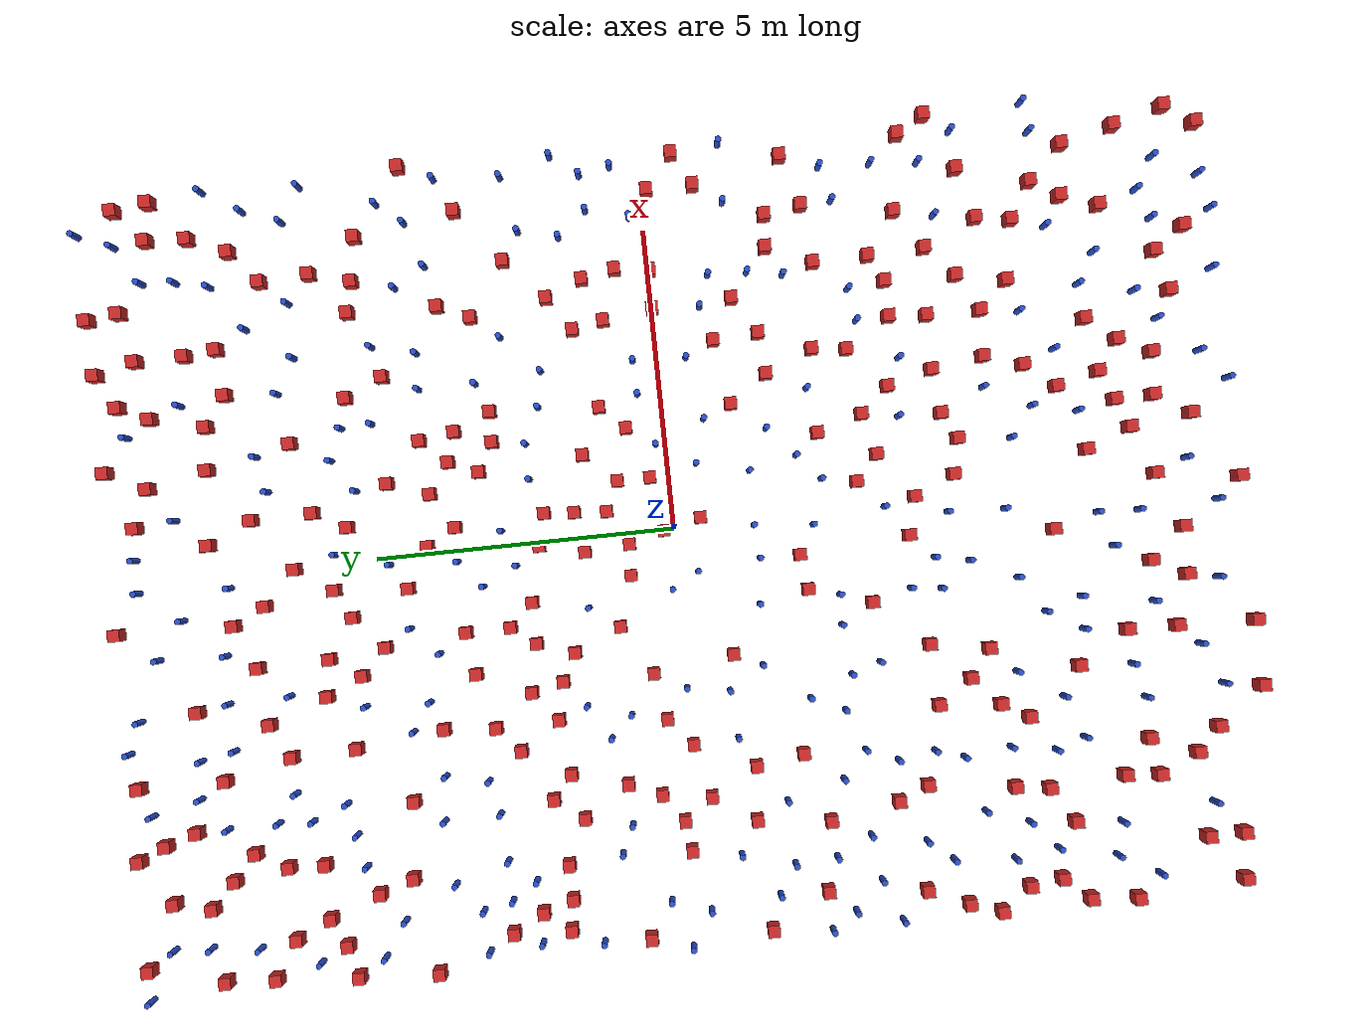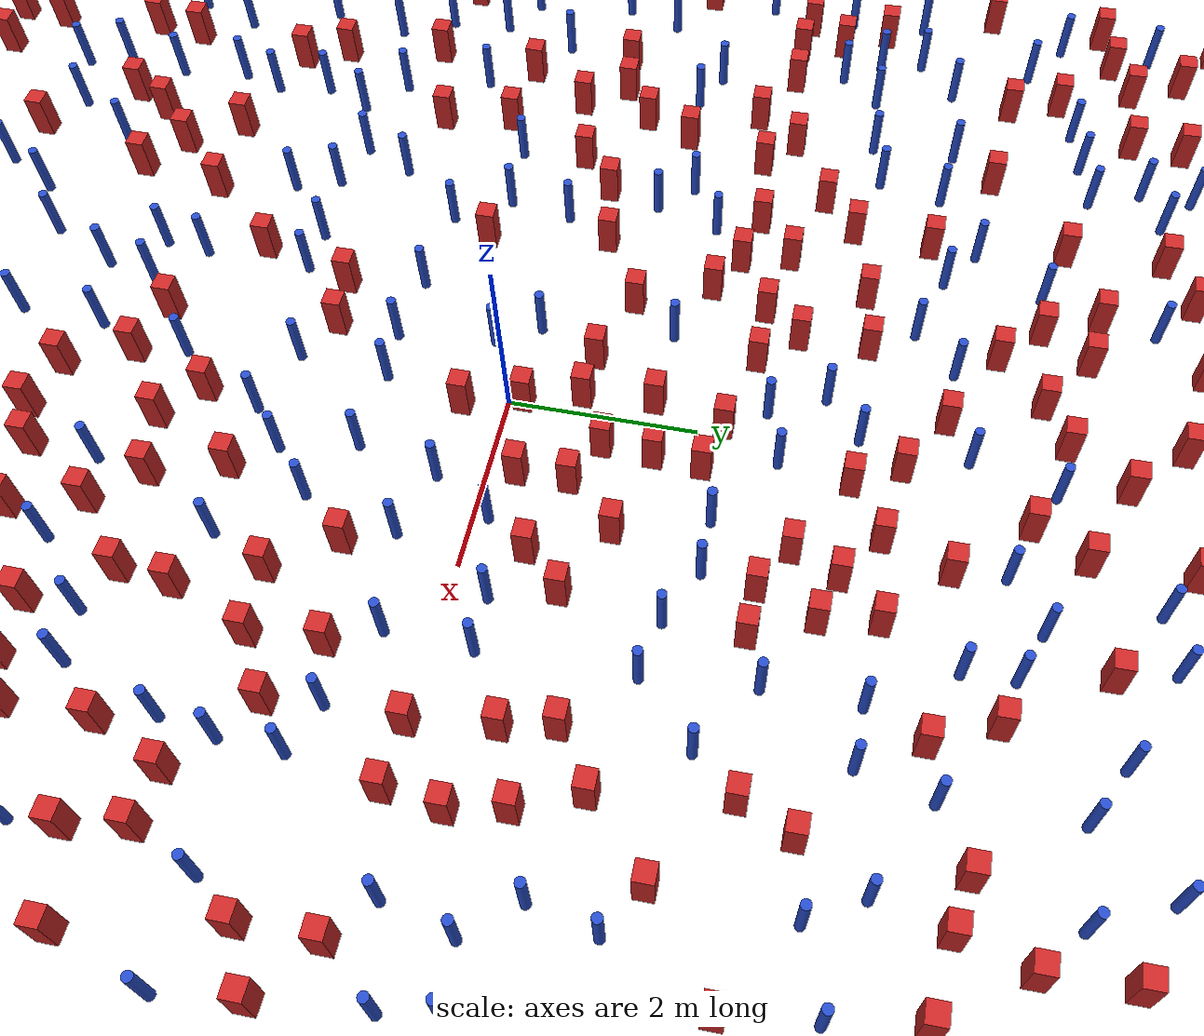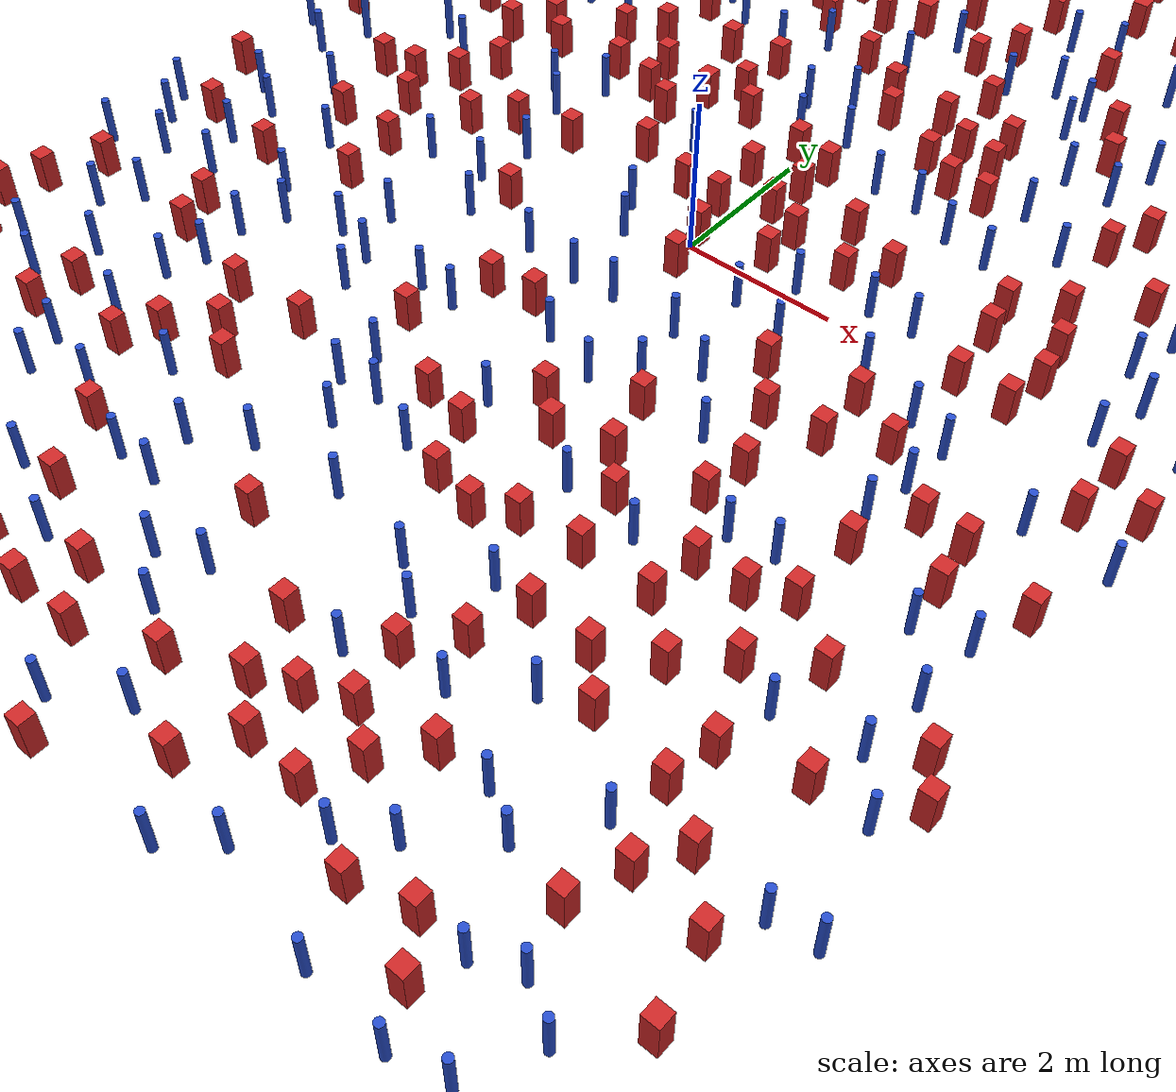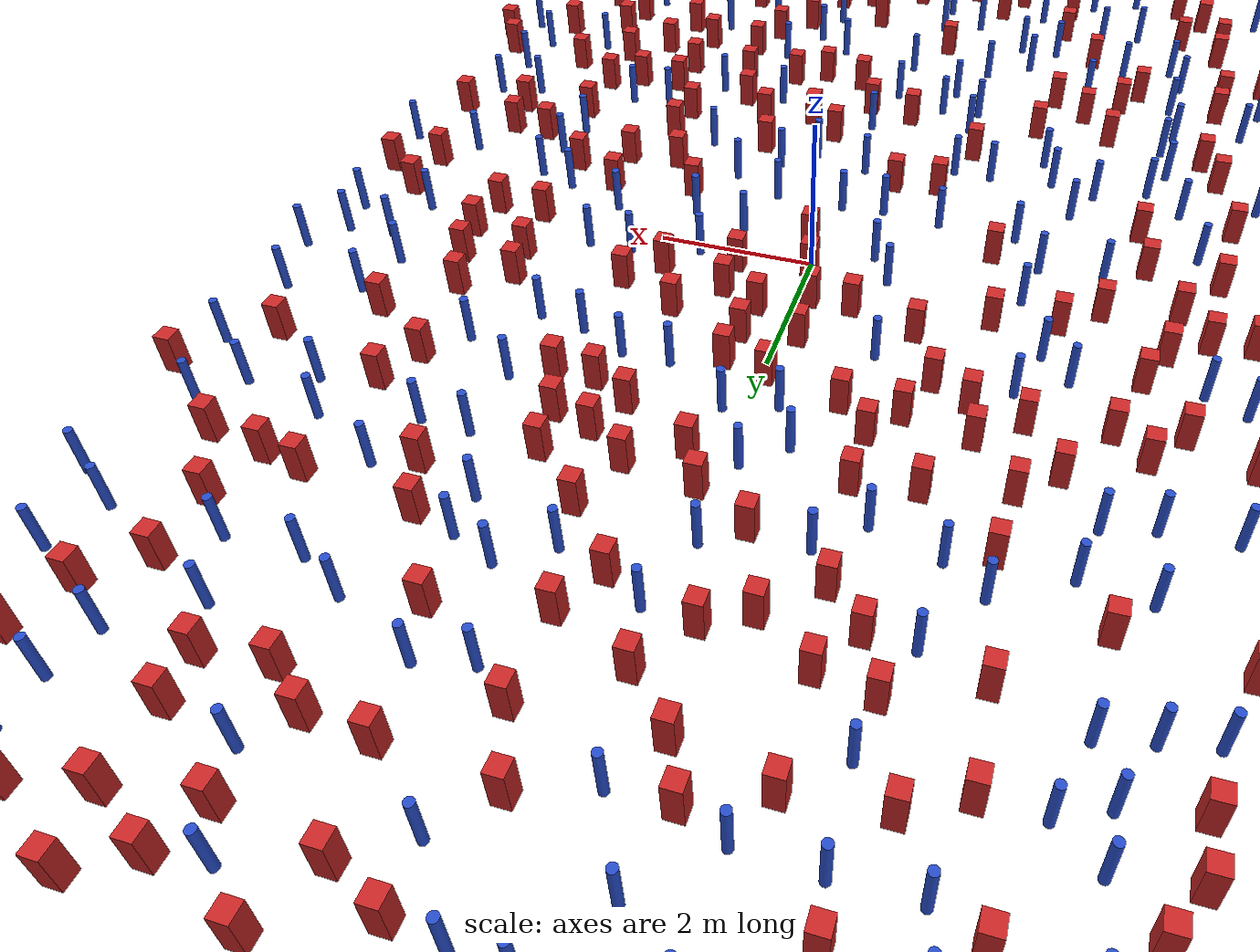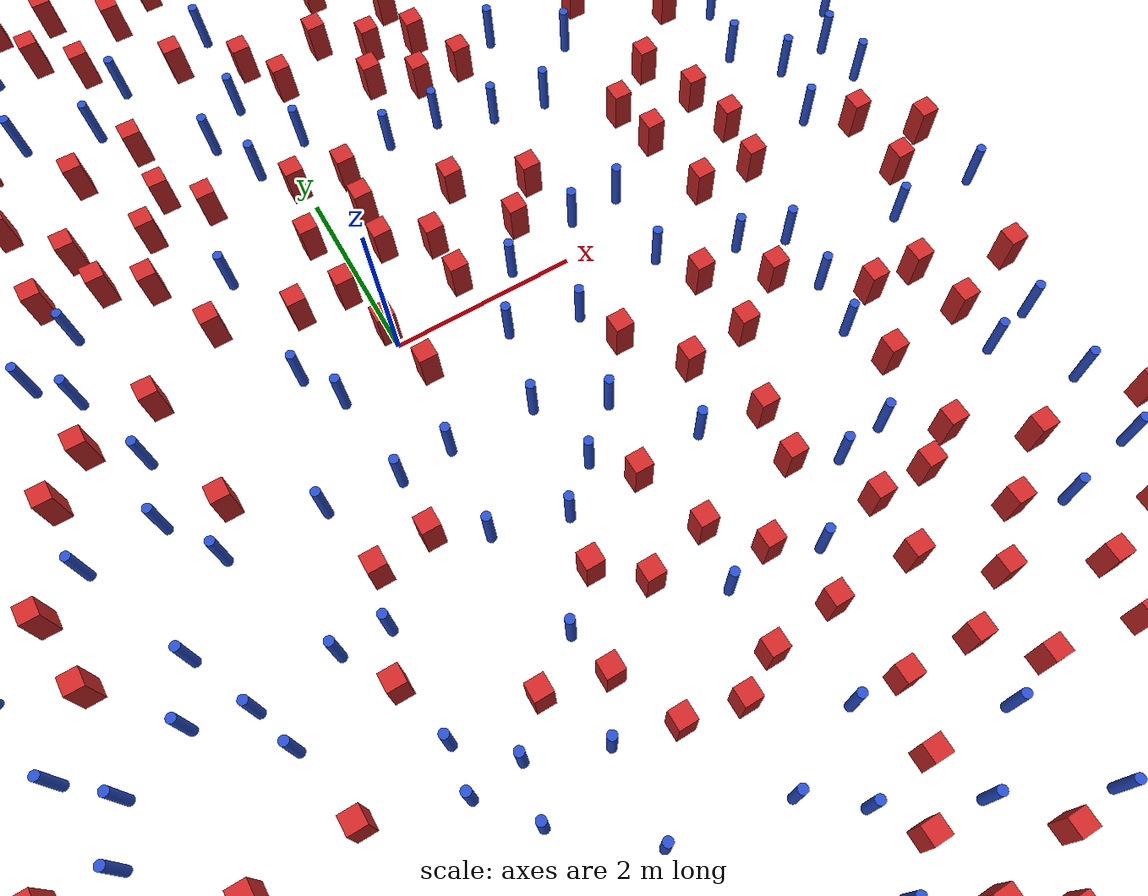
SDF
<sdf version="1.6">
  <model name="dense_13"><model name="square_post_obstacle0">
  <static>true</static>
  <pose frame="">-2.0788386926 3.51990185441 1.91545236811e-07 -7.35059704564e-06 1.12565212e-07 2.39332434364e-05</pose>
  <link name="link">
    <pose frame="">0 0 0.25 0 -0 0</pose>
    <inertial>
      <mass>100</mass>
      <inertia>
        <ixx>0.166667</ixx>
        <ixy>0</ixy>
        <ixz>0</ixz>
        <iyy>0.166667</iyy>
        <iyz>0</iyz>
        <izz>0.166667</izz>
      </inertia>
    </inertial>
    <collision name="collision">
      <geometry>
        <box>
          <size>.2 .2 .5</size>
        </box>
      </geometry>
      <max_contacts>10</max_contacts>
      <surface>
        <contact>
          <ode/>
        </contact>
        <bounce/>
        <friction>
          <torsional>
            <ode/>
          </torsional>
          <ode/>
        </friction>
      </surface>
    </collision>
    <visual name="visual">
      <geometry>
        <box>
          <size>.2 .2 .5</size>
        </box>
      </geometry>
      <material>
        <script>
          <name>Gazebo/Red</name>
          <uri>file://media/materials/scripts/gazebo.material</uri>
        </script>
      </material>
    </visual>
    <self_collide>0</self_collide>
    <kinematic>0</kinematic>
  </link>
</model>
<model name="square_post_obstacle1">
  <static>true</static>
  <pose frame="">-3.47124073159 -5.11938644158 1.91545236811e-07 -7.35059704564e-06 1.12565212e-07 2.39332434364e-05</pose>
  <link name="link">
    <pose frame="">0 0 0.25 0 -0 0</pose>
    <inertial>
      <mass>100</mass>
      <inertia>
        <ixx>0.166667</ixx>
        <ixy>0</ixy>
        <ixz>0</ixz>
        <iyy>0.166667</iyy>
        <iyz>0</iyz>
        <izz>0.166667</izz>
      </inertia>
    </inertial>
    <collision name="collision">
      <geometry>
        <box>
          <size>.2 .2 .5</size>
        </box>
      </geometry>
      <max_contacts>10</max_contacts>
      <surface>
        <contact>
          <ode/>
        </contact>
        <bounce/>
        <friction>
          <torsional>
            <ode/>
          </torsional>
          <ode/>
        </friction>
      </surface>
    </collision>
    <visual name="visual">
      <geometry>
        <box>
          <size>.2 .2 .5</size>
        </box>
      </geometry>
      <material>
        <script>
          <name>Gazebo/Red</name>
          <uri>file://media/materials/scripts/gazebo.material</uri>
        </script>
      </material>
    </visual>
    <self_collide>0</self_collide>
    <kinematic>0</kinematic>
  </link>
</model>
<model name="pole_obstacle0">
  <static>true</static>
  <pose frame="">5.99755645188 6.63738708719 7.38925637345e-09 -8.47170692796e-08 1.24976764786e-08 -1.74513093032e-07</pose>
  <link name="link">
  <pose frame="">0 0 0.3 0 -0 0</pose>
    <inertial>
      <mass>1</mass>
      <inertia>
        <ixx>0.145833</ixx>
        <ixy>0</ixy>
        <ixz>0</ixz>
        <iyy>0.145833</iyy>
        <iyz>0</iyz>
        <izz>0.125</izz>
      </inertia>
    </inertial>
    <collision name="collision">
      <geometry>
        <cylinder>
          <radius>0.05</radius>
          <length>.6</length>
        </cylinder>
      </geometry>
      <max_contacts>10</max_contacts>
      <surface>
        <contact>
          <ode/>
        </contact>
        <bounce/>
        <friction>
          <torsional>
            <ode/>
          </torsional>
          <ode/>
        </friction>
      </surface>
    </collision>
    <visual name="visual">
      <geometry>
        <cylinder>
          <radius>0.05</radius>
          <length>.6</length>
        </cylinder>
      </geometry>
      <material>
        <script>
          <name>Gazebo/Blue</name>
          <uri>file://media/materials/scripts/gazebo.material</uri>
        </script>
      </material>
    </visual>
    <self_collide>0</self_collide>
    <kinematic>0</kinematic>
  </link>
</model>
<model name="square_post_obstacle2">
  <static>true</static>
  <pose frame="">3.0949802499 -5.43575693258 1.91545236811e-07 -7.35059704564e-06 1.12565212e-07 2.39332434364e-05</pose>
  <link name="link">
    <pose frame="">0 0 0.25 0 -0 0</pose>
    <inertial>
      <mass>100</mass>
      <inertia>
        <ixx>0.166667</ixx>
        <ixy>0</ixy>
        <ixz>0</ixz>
        <iyy>0.166667</iyy>
        <iyz>0</iyz>
        <izz>0.166667</izz>
      </inertia>
    </inertial>
    <collision name="collision">
      <geometry>
        <box>
          <size>.2 .2 .5</size>
        </box>
      </geometry>
      <max_contacts>10</max_contacts>
      <surface>
        <contact>
          <ode/>
        </contact>
        <bounce/>
        <friction>
          <torsional>
            <ode/>
          </torsional>
          <ode/>
        </friction>
      </surface>
    </collision>
    <visual name="visual">
      <geometry>
        <box>
          <size>.2 .2 .5</size>
        </box>
      </geometry>
      <material>
        <script>
          <name>Gazebo/Red</name>
          <uri>file://media/materials/scripts/gazebo.material</uri>
        </script>
      </material>
    </visual>
    <self_collide>0</self_collide>
    <kinematic>0</kinematic>
  </link>
</model>
<model name="pole_obstacle1">
  <static>true</static>
  <pose frame="">-4.20396154523 -5.22190420354 7.38925637345e-09 -8.47170692796e-08 1.24976764786e-08 -1.74513093032e-07</pose>
  <link name="link">
  <pose frame="">0 0 0.3 0 -0 0</pose>
    <inertial>
      <mass>1</mass>
      <inertia>
        <ixx>0.145833</ixx>
        <ixy>0</ixy>
        <ixz>0</ixz>
        <iyy>0.145833</iyy>
        <iyz>0</iyz>
        <izz>0.125</izz>
      </inertia>
    </inertial>
    <collision name="collision">
      <geometry>
        <cylinder>
          <radius>0.05</radius>
          <length>.6</length>
        </cylinder>
      </geometry>
      <max_contacts>10</max_contacts>
      <surface>
        <contact>
          <ode/>
        </contact>
        <bounce/>
        <friction>
          <torsional>
            <ode/>
          </torsional>
          <ode/>
        </friction>
      </surface>
    </collision>
    <visual name="visual">
      <geometry>
        <cylinder>
          <radius>0.05</radius>
          <length>.6</length>
        </cylinder>
      </geometry>
      <material>
        <script>
          <name>Gazebo/Blue</name>
          <uri>file://media/materials/scripts/gazebo.material</uri>
        </script>
      </material>
    </visual>
    <self_collide>0</self_collide>
    <kinematic>0</kinematic>
  </link>
</model>
<model name="square_post_obstacle3">
  <static>true</static>
  <pose frame="">-6.72578456892 -4.25909978708 1.91545236811e-07 -7.35059704564e-06 1.12565212e-07 2.39332434364e-05</pose>
  <link name="link">
    <pose frame="">0 0 0.25 0 -0 0</pose>
    <inertial>
      <mass>100</mass>
      <inertia>
        <ixx>0.166667</ixx>
        <ixy>0</ixy>
        <ixz>0</ixz>
        <iyy>0.166667</iyy>
        <iyz>0</iyz>
        <izz>0.166667</izz>
      </inertia>
    </inertial>
    <collision name="collision">
      <geometry>
        <box>
          <size>.2 .2 .5</size>
        </box>
      </geometry>
      <max_contacts>10</max_contacts>
      <surface>
        <contact>
          <ode/>
        </contact>
        <bounce/>
        <friction>
          <torsional>
            <ode/>
          </torsional>
          <ode/>
        </friction>
      </surface>
    </collision>
    <visual name="visual">
      <geometry>
        <box>
          <size>.2 .2 .5</size>
        </box>
      </geometry>
      <material>
        <script>
          <name>Gazebo/Red</name>
          <uri>file://media/materials/scripts/gazebo.material</uri>
        </script>
      </material>
    </visual>
    <self_collide>0</self_collide>
    <kinematic>0</kinematic>
  </link>
</model>
<model name="pole_obstacle2">
  <static>true</static>
  <pose frame="">-1.40152166892 -1.29997373977 7.38925637345e-09 -8.471706928e-08 1.24976765079e-08 -1.74513093017e-07</pose>
  <link name="link">
  <pose frame="">0 0 0.3 0 -0 0</pose>
    <inertial>
      <mass>1</mass>
      <inertia>
        <ixx>0.145833</ixx>
        <ixy>0</ixy>
        <ixz>0</ixz>
        <iyy>0.145833</iyy>
        <iyz>0</iyz>
        <izz>0.125</izz>
      </inertia>
    </inertial>
    <collision name="collision">
      <geometry>
        <cylinder>
          <radius>0.05</radius>
          <length>.6</length>
        </cylinder>
      </geometry>
      <max_contacts>10</max_contacts>
      <surface>
        <contact>
          <ode/>
        </contact>
        <bounce/>
        <friction>
          <torsional>
            <ode/>
          </torsional>
          <ode/>
        </friction>
      </surface>
    </collision>
    <visual name="visual">
      <geometry>
        <cylinder>
          <radius>0.05</radius>
          <length>.6</length>
        </cylinder>
      </geometry>
      <material>
        <script>
          <name>Gazebo/Blue</name>
          <uri>file://media/materials/scripts/gazebo.material</uri>
        </script>
      </material>
    </visual>
    <self_collide>0</self_collide>
    <kinematic>0</kinematic>
  </link>
</model>
<model name="pole_obstacle3">
  <static>true</static>
  <pose frame="">-4.21250387356 7.05440987555 7.38925637345e-09 -8.47170692796e-08 1.24976764786e-08 -1.74513093032e-07</pose>
  <link name="link">
  <pose frame="">0 0 0.3 0 -0 0</pose>
    <inertial>
      <mass>1</mass>
      <inertia>
        <ixx>0.145833</ixx>
        <ixy>0</ixy>
        <ixz>0</ixz>
        <iyy>0.145833</iyy>
        <iyz>0</iyz>
        <izz>0.125</izz>
      </inertia>
    </inertial>
    <collision name="collision">
      <geometry>
        <cylinder>
          <radius>0.05</radius>
          <length>.6</length>
        </cylinder>
      </geometry>
      <max_contacts>10</max_contacts>
      <surface>
        <contact>
          <ode/>
        </contact>
        <bounce/>
        <friction>
          <torsional>
            <ode/>
          </torsional>
          <ode/>
        </friction>
      </surface>
    </collision>
    <visual name="visual">
      <geometry>
        <cylinder>
          <radius>0.05</radius>
          <length>.6</length>
        </cylinder>
      </geometry>
      <material>
        <script>
          <name>Gazebo/Blue</name>
          <uri>file://media/materials/scripts/gazebo.material</uri>
        </script>
      </material>
    </visual>
    <self_collide>0</self_collide>
    <kinematic>0</kinematic>
  </link>
</model>
<model name="square_post_obstacle4">
  <static>true</static>
  <pose frame="">3.71863333824 -1.33802473438 1.91545236811e-07 -7.35059704564e-06 1.12565212e-07 2.39332434364e-05</pose>
  <link name="link">
    <pose frame="">0 0 0.25 0 -0 0</pose>
    <inertial>
      <mass>100</mass>
      <inertia>
        <ixx>0.166667</ixx>
        <ixy>0</ixy>
        <ixz>0</ixz>
        <iyy>0.166667</iyy>
        <iyz>0</iyz>
        <izz>0.166667</izz>
      </inertia>
    </inertial>
    <collision name="collision">
      <geometry>
        <box>
          <size>.2 .2 .5</size>
        </box>
      </geometry>
      <max_contacts>10</max_contacts>
      <surface>
        <contact>
          <ode/>
        </contact>
        <bounce/>
        <friction>
          <torsional>
            <ode/>
          </torsional>
          <ode/>
        </friction>
      </surface>
    </collision>
    <visual name="visual">
      <geometry>
        <box>
          <size>.2 .2 .5</size>
        </box>
      </geometry>
      <material>
        <script>
          <name>Gazebo/Red</name>
          <uri>file://media/materials/scripts/gazebo.material</uri>
        </script>
      </material>
    </visual>
    <self_collide>0</self_collide>
    <kinematic>0</kinematic>
  </link>
</model>
<model name="square_post_obstacle5">
  <static>true</static>
  <pose frame="">-3.15009402718 0.431172714896 1.91545236811e-07 -7.35059704564e-06 1.12565212e-07 2.39332434364e-05</pose>
  <link name="link">
    <pose frame="">0 0 0.25 0 -0 0</pose>
    <inertial>
      <mass>100</mass>
      <inertia>
        <ixx>0.166667</ixx>
        <ixy>0</ixy>
        <ixz>0</ixz>
        <iyy>0.166667</iyy>
        <iyz>0</iyz>
        <izz>0.166667</izz>
      </inertia>
    </inertial>
    <collision name="collision">
      <geometry>
        <box>
          <size>.2 .2 .5</size>
        </box>
      </geometry>
      <max_contacts>10</max_contacts>
      <surface>
        <contact>
          <ode/>
        </contact>
        <bounce/>
        <friction>
          <torsional>
            <ode/>
          </torsional>
          <ode/>
        </friction>
      </surface>
    </collision>
    <visual name="visual">
      <geometry>
        <box>
          <size>.2 .2 .5</size>
        </box>
      </geometry>
      <material>
        <script>
          <name>Gazebo/Red</name>
          <uri>file://media/materials/scripts/gazebo.material</uri>
        </script>
      </material>
    </visual>
    <self_collide>0</self_collide>
    <kinematic>0</kinematic>
  </link>
</model>
<model name="square_post_obstacle6">
  <static>true</static>
  <pose frame="">-2.18707667047 -0.770278562801 1.91545236811e-07 -7.35059704564e-06 1.12565212e-07 2.39332434364e-05</pose>
  <link name="link">
    <pose frame="">0 0 0.25 0 -0 0</pose>
    <inertial>
      <mass>100</mass>
      <inertia>
        <ixx>0.166667</ixx>
        <ixy>0</ixy>
        <ixz>0</ixz>
        <iyy>0.166667</iyy>
        <iyz>0</iyz>
        <izz>0.166667</izz>
      </inertia>
    </inertial>
    <collision name="collision">
      <geometry>
        <box>
          <size>.2 .2 .5</size>
        </box>
      </geometry>
      <max_contacts>10</max_contacts>
      <surface>
        <contact>
          <ode/>
        </contact>
        <bounce/>
        <friction>
          <torsional>
            <ode/>
          </torsional>
          <ode/>
        </friction>
      </surface>
    </collision>
    <visual name="visual">
      <geometry>
        <box>
          <size>.2 .2 .5</size>
        </box>
      </geometry>
      <material>
        <script>
          <name>Gazebo/Red</name>
          <uri>file://media/materials/scripts/gazebo.material</uri>
        </script>
      </material>
    </visual>
    <self_collide>0</self_collide>
    <kinematic>0</kinematic>
  </link>
</model>
<model name="pole_obstacle4">
  <static>true</static>
  <pose frame="">-2.12254843828 6.64884126362 7.38925637345e-09 -8.47170692798e-08 1.24976765033e-08 -1.74513093019e-07</pose>
  <link name="link">
  <pose frame="">0 0 0.3 0 -0 0</pose>
    <inertial>
      <mass>1</mass>
      <inertia>
        <ixx>0.145833</ixx>
        <ixy>0</ixy>
        <ixz>0</ixz>
        <iyy>0.145833</iyy>
        <iyz>0</iyz>
        <izz>0.125</izz>
      </inertia>
    </inertial>
    <collision name="collision">
      <geometry>
        <cylinder>
          <radius>0.05</radius>
          <length>.6</length>
        </cylinder>
      </geometry>
      <max_contacts>10</max_contacts>
      <surface>
        <contact>
          <ode/>
        </contact>
        <bounce/>
        <friction>
          <torsional>
            <ode/>
          </torsional>
          <ode/>
        </friction>
      </surface>
    </collision>
    <visual name="visual">
      <geometry>
        <cylinder>
          <radius>0.05</radius>
          <length>.6</length>
        </cylinder>
      </geometry>
      <material>
        <script>
          <name>Gazebo/Blue</name>
          <uri>file://media/materials/scripts/gazebo.material</uri>
        </script>
      </material>
    </visual>
    <self_collide>0</self_collide>
    <kinematic>0</kinematic>
  </link>
</model>
<model name="pole_obstacle5">
  <static>true</static>
  <pose frame="">2.2489243772 4.84507319505 7.38925637345e-09 -8.47170692798e-08 1.24976765033e-08 -1.74513093019e-07</pose>
  <link name="link">
  <pose frame="">0 0 0.3 0 -0 0</pose>
    <inertial>
      <mass>1</mass>
      <inertia>
        <ixx>0.145833</ixx>
        <ixy>0</ixy>
        <ixz>0</ixz>
        <iyy>0.145833</iyy>
        <iyz>0</iyz>
        <izz>0.125</izz>
      </inertia>
    </inertial>
    <collision name="collision">
      <geometry>
        <cylinder>
          <radius>0.05</radius>
          <length>.6</length>
        </cylinder>
      </geometry>
      <max_contacts>10</max_contacts>
      <surface>
        <contact>
          <ode/>
        </contact>
        <bounce/>
        <friction>
          <torsional>
            <ode/>
          </torsional>
          <ode/>
        </friction>
      </surface>
    </collision>
    <visual name="visual">
      <geometry>
        <cylinder>
          <radius>0.05</radius>
          <length>.6</length>
        </cylinder>
      </geometry>
      <material>
        <script>
          <name>Gazebo/Blue</name>
          <uri>file://media/materials/scripts/gazebo.material</uri>
        </script>
      </material>
    </visual>
    <self_collide>0</self_collide>
    <kinematic>0</kinematic>
  </link>
</model>
<model name="square_post_obstacle7">
  <static>true</static>
  <pose frame="">4.50447674542 -1.98061000335 1.91545236811e-07 -7.35059704564e-06 1.12565212e-07 2.39332434364e-05</pose>
  <link name="link">
    <pose frame="">0 0 0.25 0 -0 0</pose>
    <inertial>
      <mass>100</mass>
      <inertia>
        <ixx>0.166667</ixx>
        <ixy>0</ixy>
        <ixz>0</ixz>
        <iyy>0.166667</iyy>
        <iyz>0</iyz>
        <izz>0.166667</izz>
      </inertia>
    </inertial>
    <collision name="collision">
      <geometry>
        <box>
          <size>.2 .2 .5</size>
        </box>
      </geometry>
      <max_contacts>10</max_contacts>
      <surface>
        <contact>
          <ode/>
        </contact>
        <bounce/>
        <friction>
          <torsional>
            <ode/>
          </torsional>
          <ode/>
        </friction>
      </surface>
    </collision>
    <visual name="visual">
      <geometry>
        <box>
          <size>.2 .2 .5</size>
        </box>
      </geometry>
      <material>
        <script>
          <name>Gazebo/Red</name>
          <uri>file://media/materials/scripts/gazebo.material</uri>
        </script>
      </material>
    </visual>
    <self_collide>0</self_collide>
    <kinematic>0</kinematic>
  </link>
</model>
<model name="square_post_obstacle8">
  <static>true</static>
  <pose frame="">-4.51516175834 -0.173714430252 1.91545236811e-07 -7.35059704564e-06 1.12565212e-07 2.39332434364e-05</pose>
  <link name="link">
    <pose frame="">0 0 0.25 0 -0 0</pose>
    <inertial>
      <mass>100</mass>
      <inertia>
        <ixx>0.166667</ixx>
        <ixy>0</ixy>
        <ixz>0</ixz>
        <iyy>0.166667</iyy>
        <iyz>0</iyz>
        <izz>0.166667</izz>
      </inertia>
    </inertial>
    <collision name="collision">
      <geometry>
        <box>
          <size>.2 .2 .5</size>
        </box>
      </geometry>
      <max_contacts>10</max_contacts>
      <surface>
        <contact>
          <ode/>
        </contact>
        <bounce/>
        <friction>
          <torsional>
            <ode/>
          </torsional>
          <ode/>
        </friction>
      </surface>
    </collision>
    <visual name="visual">
      <geometry>
        <box>
          <size>.2 .2 .5</size>
        </box>
      </geometry>
      <material>
        <script>
          <name>Gazebo/Red</name>
          <uri>file://media/materials/scripts/gazebo.material</uri>
        </script>
      </material>
    </visual>
    <self_collide>0</self_collide>
    <kinematic>0</kinematic>
  </link>
</model>
<model name="pole_obstacle6">
  <static>true</static>
  <pose frame="">-0.0801501112502 -1.33337683288 7.38925637345e-09 -8.47170692799e-08 1.24976765008e-08 -1.7451309302e-07</pose>
  <link name="link">
  <pose frame="">0 0 0.3 0 -0 0</pose>
    <inertial>
      <mass>1</mass>
      <inertia>
        <ixx>0.145833</ixx>
        <ixy>0</ixy>
        <ixz>0</ixz>
        <iyy>0.145833</iyy>
        <iyz>0</iyz>
        <izz>0.125</izz>
      </inertia>
    </inertial>
    <collision name="collision">
      <geometry>
        <cylinder>
          <radius>0.05</radius>
          <length>.6</length>
        </cylinder>
      </geometry>
      <max_contacts>10</max_contacts>
      <surface>
        <contact>
          <ode/>
        </contact>
        <bounce/>
        <friction>
          <torsional>
            <ode/>
          </torsional>
          <ode/>
        </friction>
      </surface>
    </collision>
    <visual name="visual">
      <geometry>
        <cylinder>
          <radius>0.05</radius>
          <length>.6</length>
        </cylinder>
      </geometry>
      <material>
        <script>
          <name>Gazebo/Blue</name>
          <uri>file://media/materials/scripts/gazebo.material</uri>
        </script>
      </material>
    </visual>
    <self_collide>0</self_collide>
    <kinematic>0</kinematic>
  </link>
</model>
<model name="pole_obstacle7">
  <static>true</static>
  <pose frame="">-1.03853403974 -7.27015901832 7.38925637345e-09 -8.47170692799e-08 1.2497676505e-08 -1.74513093018e-07</pose>
  <link name="link">
  <pose frame="">0 0 0.3 0 -0 0</pose>
    <inertial>
      <mass>1</mass>
      <inertia>
        <ixx>0.145833</ixx>
        <ixy>0</ixy>
        <ixz>0</ixz>
        <iyy>0.145833</iyy>
        <iyz>0</iyz>
        <izz>0.125</izz>
      </inertia>
    </inertial>
    <collision name="collision">
      <geometry>
        <cylinder>
          <radius>0.05</radius>
          <length>.6</length>
        </cylinder>
      </geometry>
      <max_contacts>10</max_contacts>
      <surface>
        <contact>
          <ode/>
        </contact>
        <bounce/>
        <friction>
          <torsional>
            <ode/>
          </torsional>
          <ode/>
        </friction>
      </surface>
    </collision>
    <visual name="visual">
      <geometry>
        <cylinder>
          <radius>0.05</radius>
          <length>.6</length>
        </cylinder>
      </geometry>
      <material>
        <script>
          <name>Gazebo/Blue</name>
          <uri>file://media/materials/scripts/gazebo.material</uri>
        </script>
      </material>
    </visual>
    <self_collide>0</self_collide>
    <kinematic>0</kinematic>
  </link>
</model>
<model name="square_post_obstacle9">
  <static>true</static>
  <pose frame="">-2.52650715397 -5.02211175676 1.91545236811e-07 -7.35059704564e-06 1.12565212e-07 2.39332434364e-05</pose>
  <link name="link">
    <pose frame="">0 0 0.25 0 -0 0</pose>
    <inertial>
      <mass>100</mass>
      <inertia>
        <ixx>0.166667</ixx>
        <ixy>0</ixy>
        <ixz>0</ixz>
        <iyy>0.166667</iyy>
        <iyz>0</iyz>
        <izz>0.166667</izz>
      </inertia>
    </inertial>
    <collision name="collision">
      <geometry>
        <box>
          <size>.2 .2 .5</size>
        </box>
      </geometry>
      <max_contacts>10</max_contacts>
      <surface>
        <contact>
          <ode/>
        </contact>
        <bounce/>
        <friction>
          <torsional>
            <ode/>
          </torsional>
          <ode/>
        </friction>
      </surface>
    </collision>
    <visual name="visual">
      <geometry>
        <box>
          <size>.2 .2 .5</size>
        </box>
      </geometry>
      <material>
        <script>
          <name>Gazebo/Red</name>
          <uri>file://media/materials/scripts/gazebo.material</uri>
        </script>
      </material>
    </visual>
    <self_collide>0</self_collide>
    <kinematic>0</kinematic>
  </link>
</model>
<model name="square_post_obstacle10">
  <static>true</static>
  <pose frame="">5.14205474478 -6.46462236844 1.91545236811e-07 -7.35059704564e-06 1.12565212e-07 2.39332434364e-05</pose>
  <link name="link">
    <pose frame="">0 0 0.25 0 -0 0</pose>
    <inertial>
      <mass>100</mass>
      <inertia>
        <ixx>0.166667</ixx>
        <ixy>0</ixy>
        <ixz>0</ixz>
        <iyy>0.166667</iyy>
        <iyz>0</iyz>
        <izz>0.166667</izz>
      </inertia>
    </inertial>
    <collision name="collision">
      <geometry>
        <box>
          <size>.2 .2 .5</size>
        </box>
      </geometry>
      <max_contacts>10</max_contacts>
      <surface>
        <contact>
          <ode/>
        </contact>
        <bounce/>
        <friction>
          <torsional>
            <ode/>
          </torsional>
          <ode/>
        </friction>
      </surface>
    </collision>
    <visual name="visual">
      <geometry>
        <box>
          <size>.2 .2 .5</size>
        </box>
      </geometry>
      <material>
        <script>
          <name>Gazebo/Red</name>
          <uri>file://media/materials/scripts/gazebo.material</uri>
        </script>
      </material>
    </visual>
    <self_collide>0</self_collide>
    <kinematic>0</kinematic>
  </link>
</model>
<model name="square_post_obstacle11">
  <static>true</static>
  <pose frame="">0.856327148266 6.99658887963 1.91545236811e-07 -7.35059704564e-06 1.12565212e-07 2.39332434364e-05</pose>
  <link name="link">
    <pose frame="">0 0 0.25 0 -0 0</pose>
    <inertial>
      <mass>100</mass>
      <inertia>
        <ixx>0.166667</ixx>
        <ixy>0</ixy>
        <ixz>0</ixz>
        <iyy>0.166667</iyy>
        <iyz>0</iyz>
        <izz>0.166667</izz>
      </inertia>
    </inertial>
    <collision name="collision">
      <geometry>
        <box>
          <size>.2 .2 .5</size>
        </box>
      </geometry>
      <max_contacts>10</max_contacts>
      <surface>
        <contact>
          <ode/>
        </contact>
        <bounce/>
        <friction>
          <torsional>
            <ode/>
          </torsional>
          <ode/>
        </friction>
      </surface>
    </collision>
    <visual name="visual">
      <geometry>
        <box>
          <size>.2 .2 .5</size>
        </box>
      </geometry>
      <material>
        <script>
          <name>Gazebo/Red</name>
          <uri>file://media/materials/scripts/gazebo.material</uri>
        </script>
      </material>
    </visual>
    <self_collide>0</self_collide>
    <kinematic>0</kinematic>
  </link>
</model>
<model name="square_post_obstacle12">
  <static>true</static>
  <pose frame="">-3.14189247281 6.71943012908 1.91545236811e-07 -7.35059704564e-06 1.12565212e-07 2.39332434364e-05</pose>
  <link name="link">
    <pose frame="">0 0 0.25 0 -0 0</pose>
    <inertial>
      <mass>100</mass>
      <inertia>
        <ixx>0.166667</ixx>
        <ixy>0</ixy>
        <ixz>0</ixz>
        <iyy>0.166667</iyy>
        <iyz>0</iyz>
        <izz>0.166667</izz>
      </inertia>
    </inertial>
    <collision name="collision">
      <geometry>
        <box>
          <size>.2 .2 .5</size>
        </box>
      </geometry>
      <max_contacts>10</max_contacts>
      <surface>
        <contact>
          <ode/>
        </contact>
        <bounce/>
        <friction>
          <torsional>
            <ode/>
          </torsional>
          <ode/>
        </friction>
      </surface>
    </collision>
    <visual name="visual">
      <geometry>
        <box>
          <size>.2 .2 .5</size>
        </box>
      </geometry>
      <material>
        <script>
          <name>Gazebo/Red</name>
          <uri>file://media/materials/scripts/gazebo.material</uri>
        </script>
      </material>
    </visual>
    <self_collide>0</self_collide>
    <kinematic>0</kinematic>
  </link>
</model>
<model name="square_post_obstacle13">
  <static>true</static>
  <pose frame="">0.120368586204 4.11371070803 1.91545236811e-07 -7.35059704564e-06 1.12565212e-07 2.39332434364e-05</pose>
  <link name="link">
    <pose frame="">0 0 0.25 0 -0 0</pose>
    <inertial>
      <mass>100</mass>
      <inertia>
        <ixx>0.166667</ixx>
        <ixy>0</ixy>
        <ixz>0</ixz>
        <iyy>0.166667</iyy>
        <iyz>0</iyz>
        <izz>0.166667</izz>
      </inertia>
    </inertial>
    <collision name="collision">
      <geometry>
        <box>
          <size>.2 .2 .5</size>
        </box>
      </geometry>
      <max_contacts>10</max_contacts>
      <surface>
        <contact>
          <ode/>
        </contact>
        <bounce/>
        <friction>
          <torsional>
            <ode/>
          </torsional>
          <ode/>
        </friction>
      </surface>
    </collision>
    <visual name="visual">
      <geometry>
        <box>
          <size>.2 .2 .5</size>
        </box>
      </geometry>
      <material>
        <script>
          <name>Gazebo/Red</name>
          <uri>file://media/materials/scripts/gazebo.material</uri>
        </script>
      </material>
    </visual>
    <self_collide>0</self_collide>
    <kinematic>0</kinematic>
  </link>
</model>
<model name="pole_obstacle8">
  <static>true</static>
  <pose frame="">3.53030081762 4.71981835771 7.38925637345e-09 -8.47170692798e-08 1.24976765033e-08 -1.74513093019e-07</pose>
  <link name="link">
  <pose frame="">0 0 0.3 0 -0 0</pose>
    <inertial>
      <mass>1</mass>
      <inertia>
        <ixx>0.145833</ixx>
        <ixy>0</ixy>
        <ixz>0</ixz>
        <iyy>0.145833</iyy>
        <iyz>0</iyz>
        <izz>0.125</izz>
      </inertia>
    </inertial>
    <collision name="collision">
      <geometry>
        <cylinder>
          <radius>0.05</radius>
          <length>.6</length>
        </cylinder>
      </geometry>
      <max_contacts>10</max_contacts>
      <surface>
        <contact>
          <ode/>
        </contact>
        <bounce/>
        <friction>
          <torsional>
            <ode/>
          </torsional>
          <ode/>
        </friction>
      </surface>
    </collision>
    <visual name="visual">
      <geometry>
        <cylinder>
          <radius>0.05</radius>
          <length>.6</length>
        </cylinder>
      </geometry>
      <material>
        <script>
          <name>Gazebo/Blue</name>
          <uri>file://media/materials/scripts/gazebo.material</uri>
        </script>
      </material>
    </visual>
    <self_collide>0</self_collide>
    <kinematic>0</kinematic>
  </link>
</model>
<model name="square_post_obstacle14">
  <static>true</static>
  <pose frame="">-4.39685745982 8.95476248692 1.91545236811e-07 -7.35059704564e-06 1.12565212e-07 2.39332434364e-05</pose>
  <link name="link">
    <pose frame="">0 0 0.25 0 -0 0</pose>
    <inertial>
      <mass>100</mass>
      <inertia>
        <ixx>0.166667</ixx>
        <ixy>0</ixy>
        <ixz>0</ixz>
        <iyy>0.166667</iyy>
        <iyz>0</iyz>
        <izz>0.166667</izz>
      </inertia>
    </inertial>
    <collision name="collision">
      <geometry>
        <box>
          <size>.2 .2 .5</size>
        </box>
      </geometry>
      <max_contacts>10</max_contacts>
      <surface>
        <contact>
          <ode/>
        </contact>
        <bounce/>
        <friction>
          <torsional>
            <ode/>
          </torsional>
          <ode/>
        </friction>
      </surface>
    </collision>
    <visual name="visual">
      <geometry>
        <box>
          <size>.2 .2 .5</size>
        </box>
      </geometry>
      <material>
        <script>
          <name>Gazebo/Red</name>
          <uri>file://media/materials/scripts/gazebo.material</uri>
        </script>
      </material>
    </visual>
    <self_collide>0</self_collide>
    <kinematic>0</kinematic>
  </link>
</model>
<model name="square_post_obstacle15">
  <static>true</static>
  <pose frame="">-2.97740192975 2.22756941772 1.91545236811e-07 -7.35059704564e-06 1.12565212e-07 2.39332434364e-05</pose>
  <link name="link">
    <pose frame="">0 0 0.25 0 -0 0</pose>
    <inertial>
      <mass>100</mass>
      <inertia>
        <ixx>0.166667</ixx>
        <ixy>0</ixy>
        <ixz>0</ixz>
        <iyy>0.166667</iyy>
        <iyz>0</iyz>
        <izz>0.166667</izz>
      </inertia>
    </inertial>
    <collision name="collision">
      <geometry>
        <box>
          <size>.2 .2 .5</size>
        </box>
      </geometry>
      <max_contacts>10</max_contacts>
      <surface>
        <contact>
          <ode/>
        </contact>
        <bounce/>
        <friction>
          <torsional>
            <ode/>
          </torsional>
          <ode/>
        </friction>
      </surface>
    </collision>
    <visual name="visual">
      <geometry>
        <box>
          <size>.2 .2 .5</size>
        </box>
      </geometry>
      <material>
        <script>
          <name>Gazebo/Red</name>
          <uri>file://media/materials/scripts/gazebo.material</uri>
        </script>
      </material>
    </visual>
    <self_collide>0</self_collide>
    <kinematic>0</kinematic>
  </link>
</model>
<model name="square_post_obstacle16">
  <static>true</static>
  <pose frame="">4.03661646404 1.73327467691 1.91545236811e-07 -7.35059704564e-06 1.12565212e-07 2.39332434364e-05</pose>
  <link name="link">
    <pose frame="">0 0 0.25 0 -0 0</pose>
    <inertial>
      <mass>100</mass>
      <inertia>
        <ixx>0.166667</ixx>
        <ixy>0</ixy>
        <ixz>0</ixz>
        <iyy>0.166667</iyy>
        <iyz>0</iyz>
        <izz>0.166667</izz>
      </inertia>
    </inertial>
    <collision name="collision">
      <geometry>
        <box>
          <size>.2 .2 .5</size>
        </box>
      </geometry>
      <max_contacts>10</max_contacts>
      <surface>
        <contact>
          <ode/>
        </contact>
        <bounce/>
        <friction>
          <torsional>
            <ode/>
          </torsional>
          <ode/>
        </friction>
      </surface>
    </collision>
    <visual name="visual">
      <geometry>
        <box>
          <size>.2 .2 .5</size>
        </box>
      </geometry>
      <material>
        <script>
          <name>Gazebo/Red</name>
          <uri>file://media/materials/scripts/gazebo.material</uri>
        </script>
      </material>
    </visual>
    <self_collide>0</self_collide>
    <kinematic>0</kinematic>
  </link>
</model>
<model name="pole_obstacle9">
  <static>true</static>
  <pose frame="">-4.43777852764 3.35960975766 7.38925637345e-09 -8.47170692798e-08 1.24976764937e-08 -1.74513093023e-07</pose>
  <link name="link">
  <pose frame="">0 0 0.3 0 -0 0</pose>
    <inertial>
      <mass>1</mass>
      <inertia>
        <ixx>0.145833</ixx>
        <ixy>0</ixy>
        <ixz>0</ixz>
        <iyy>0.145833</iyy>
        <iyz>0</iyz>
        <izz>0.125</izz>
      </inertia>
    </inertial>
    <collision name="collision">
      <geometry>
        <cylinder>
          <radius>0.05</radius>
          <length>.6</length>
        </cylinder>
      </geometry>
      <max_contacts>10</max_contacts>
      <surface>
        <contact>
          <ode/>
        </contact>
        <bounce/>
        <friction>
          <torsional>
            <ode/>
          </torsional>
          <ode/>
        </friction>
      </surface>
    </collision>
    <visual name="visual">
      <geometry>
        <cylinder>
          <radius>0.05</radius>
          <length>.6</length>
        </cylinder>
      </geometry>
      <material>
        <script>
          <name>Gazebo/Blue</name>
          <uri>file://media/materials/scripts/gazebo.material</uri>
        </script>
      </material>
    </visual>
    <self_collide>0</self_collide>
    <kinematic>0</kinematic>
  </link>
</model>
<model name="square_post_obstacle17">
  <static>true</static>
  <pose frame="">-0.514656128458 -3.88882364284 1.91545236811e-07 -7.35059704564e-06 1.12565212e-07 2.39332434364e-05</pose>
  <link name="link">
    <pose frame="">0 0 0.25 0 -0 0</pose>
    <inertial>
      <mass>100</mass>
      <inertia>
        <ixx>0.166667</ixx>
        <ixy>0</ixy>
        <ixz>0</ixz>
        <iyy>0.166667</iyy>
        <iyz>0</iyz>
        <izz>0.166667</izz>
      </inertia>
    </inertial>
    <collision name="collision">
      <geometry>
        <box>
          <size>.2 .2 .5</size>
        </box>
      </geometry>
      <max_contacts>10</max_contacts>
      <surface>
        <contact>
          <ode/>
        </contact>
        <bounce/>
        <friction>
          <torsional>
            <ode/>
          </torsional>
          <ode/>
        </friction>
      </surface>
    </collision>
    <visual name="visual">
      <geometry>
        <box>
          <size>.2 .2 .5</size>
        </box>
      </geometry>
      <material>
        <script>
          <name>Gazebo/Red</name>
          <uri>file://media/materials/scripts/gazebo.material</uri>
        </script>
      </material>
    </visual>
    <self_collide>0</self_collide>
    <kinematic>0</kinematic>
  </link>
</model>
<model name="square_post_obstacle18">
  <static>true</static>
  <pose frame="">-4.86705667237 -5.21440921292 1.91545236811e-07 -7.35059704564e-06 1.12565212e-07 2.39332434364e-05</pose>
  <link name="link">
    <pose frame="">0 0 0.25 0 -0 0</pose>
    <inertial>
      <mass>100</mass>
      <inertia>
        <ixx>0.166667</ixx>
        <ixy>0</ixy>
        <ixz>0</ixz>
        <iyy>0.166667</iyy>
        <iyz>0</iyz>
        <izz>0.166667</izz>
      </inertia>
    </inertial>
    <collision name="collision">
      <geometry>
        <box>
          <size>.2 .2 .5</size>
        </box>
      </geometry>
      <max_contacts>10</max_contacts>
      <surface>
        <contact>
          <ode/>
        </contact>
        <bounce/>
        <friction>
          <torsional>
            <ode/>
          </torsional>
          <ode/>
        </friction>
      </surface>
    </collision>
    <visual name="visual">
      <geometry>
        <box>
          <size>.2 .2 .5</size>
        </box>
      </geometry>
      <material>
        <script>
          <name>Gazebo/Red</name>
          <uri>file://media/materials/scripts/gazebo.material</uri>
        </script>
      </material>
    </visual>
    <self_collide>0</self_collide>
    <kinematic>0</kinematic>
  </link>
</model>
<model name="pole_obstacle10">
  <static>true</static>
  <pose frame="">1.42459915182 -6.14395877449 7.38925637345e-09 -8.47170692799e-08 1.24976765033e-08 -1.74513093018e-07</pose>
  <link name="link">
  <pose frame="">0 0 0.3 0 -0 0</pose>
    <inertial>
      <mass>1</mass>
      <inertia>
        <ixx>0.145833</ixx>
        <ixy>0</ixy>
        <ixz>0</ixz>
        <iyy>0.145833</iyy>
        <iyz>0</iyz>
        <izz>0.125</izz>
      </inertia>
    </inertial>
    <collision name="collision">
      <geometry>
        <cylinder>
          <radius>0.05</radius>
          <length>.6</length>
        </cylinder>
      </geometry>
      <max_contacts>10</max_contacts>
      <surface>
        <contact>
          <ode/>
        </contact>
        <bounce/>
        <friction>
          <torsional>
            <ode/>
          </torsional>
          <ode/>
        </friction>
      </surface>
    </collision>
    <visual name="visual">
      <geometry>
        <cylinder>
          <radius>0.05</radius>
          <length>.6</length>
        </cylinder>
      </geometry>
      <material>
        <script>
          <name>Gazebo/Blue</name>
          <uri>file://media/materials/scripts/gazebo.material</uri>
        </script>
      </material>
    </visual>
    <self_collide>0</self_collide>
    <kinematic>0</kinematic>
  </link>
</model>
<model name="square_post_obstacle19">
  <static>true</static>
  <pose frame="">3.56690678454 0.822996285619 1.91545236811e-07 -7.35059704564e-06 1.12565212e-07 2.39332434364e-05</pose>
  <link name="link">
    <pose frame="">0 0 0.25 0 -0 0</pose>
    <inertial>
      <mass>100</mass>
      <inertia>
        <ixx>0.166667</ixx>
        <ixy>0</ixy>
        <ixz>0</ixz>
        <iyy>0.166667</iyy>
        <iyz>0</iyz>
        <izz>0.166667</izz>
      </inertia>
    </inertial>
    <collision name="collision">
      <geometry>
        <box>
          <size>.2 .2 .5</size>
        </box>
      </geometry>
      <max_contacts>10</max_contacts>
      <surface>
        <contact>
          <ode/>
        </contact>
        <bounce/>
        <friction>
          <torsional>
            <ode/>
          </torsional>
          <ode/>
        </friction>
      </surface>
    </collision>
    <visual name="visual">
      <geometry>
        <box>
          <size>.2 .2 .5</size>
        </box>
      </geometry>
      <material>
        <script>
          <name>Gazebo/Red</name>
          <uri>file://media/materials/scripts/gazebo.material</uri>
        </script>
      </material>
    </visual>
    <self_collide>0</self_collide>
    <kinematic>0</kinematic>
  </link>
</model>
<model name="pole_obstacle11">
  <static>true</static>
  <pose frame="">-3.30508993108 -2.53764169454 7.38925637345e-09 -8.47170692798e-08 1.24976764939e-08 -1.74513093025e-07</pose>
  <link name="link">
  <pose frame="">0 0 0.3 0 -0 0</pose>
    <inertial>
      <mass>1</mass>
      <inertia>
        <ixx>0.145833</ixx>
        <ixy>0</ixy>
        <ixz>0</ixz>
        <iyy>0.145833</iyy>
        <iyz>0</iyz>
        <izz>0.125</izz>
      </inertia>
    </inertial>
    <collision name="collision">
      <geometry>
        <cylinder>
          <radius>0.05</radius>
          <length>.6</length>
        </cylinder>
      </geometry>
      <max_contacts>10</max_contacts>
      <surface>
        <contact>
          <ode/>
        </contact>
        <bounce/>
        <friction>
          <torsional>
            <ode/>
          </torsional>
          <ode/>
        </friction>
      </surface>
    </collision>
    <visual name="visual">
      <geometry>
        <cylinder>
          <radius>0.05</radius>
          <length>.6</length>
        </cylinder>
      </geometry>
      <material>
        <script>
          <name>Gazebo/Blue</name>
          <uri>file://media/materials/scripts/gazebo.material</uri>
        </script>
      </material>
    </visual>
    <self_collide>0</self_collide>
    <kinematic>0</kinematic>
  </link>
</model>
<model name="square_post_obstacle20">
  <static>true</static>
  <pose frame="">-4.69119235852 -3.77144085148 1.91545236811e-07 -7.35059704564e-06 1.12565212e-07 2.39332434364e-05</pose>
  <link name="link">
    <pose frame="">0 0 0.25 0 -0 0</pose>
    <inertial>
      <mass>100</mass>
      <inertia>
        <ixx>0.166667</ixx>
        <ixy>0</ixy>
        <ixz>0</ixz>
        <iyy>0.166667</iyy>
        <iyz>0</iyz>
        <izz>0.166667</izz>
      </inertia>
    </inertial>
    <collision name="collision">
      <geometry>
        <box>
          <size>.2 .2 .5</size>
        </box>
      </geometry>
      <max_contacts>10</max_contacts>
      <surface>
        <contact>
          <ode/>
        </contact>
        <bounce/>
        <friction>
          <torsional>
            <ode/>
          </torsional>
          <ode/>
        </friction>
      </surface>
    </collision>
    <visual name="visual">
      <geometry>
        <box>
          <size>.2 .2 .5</size>
        </box>
      </geometry>
      <material>
        <script>
          <name>Gazebo/Red</name>
          <uri>file://media/materials/scripts/gazebo.material</uri>
        </script>
      </material>
    </visual>
    <self_collide>0</self_collide>
    <kinematic>0</kinematic>
  </link>
</model>
<model name="pole_obstacle12">
  <static>true</static>
  <pose frame="">-5.60776020987 2.87340365903 7.38925637345e-09 -8.47170692798e-08 1.24976764937e-08 -1.74513093023e-07</pose>
  <link name="link">
  <pose frame="">0 0 0.3 0 -0 0</pose>
    <inertial>
      <mass>1</mass>
      <inertia>
        <ixx>0.145833</ixx>
        <ixy>0</ixy>
        <ixz>0</ixz>
        <iyy>0.145833</iyy>
        <iyz>0</iyz>
        <izz>0.125</izz>
      </inertia>
    </inertial>
    <collision name="collision">
      <geometry>
        <cylinder>
          <radius>0.05</radius>
          <length>.6</length>
        </cylinder>
      </geometry>
      <max_contacts>10</max_contacts>
      <surface>
        <contact>
          <ode/>
        </contact>
        <bounce/>
        <friction>
          <torsional>
            <ode/>
          </torsional>
          <ode/>
        </friction>
      </surface>
    </collision>
    <visual name="visual">
      <geometry>
        <cylinder>
          <radius>0.05</radius>
          <length>.6</length>
        </cylinder>
      </geometry>
      <material>
        <script>
          <name>Gazebo/Blue</name>
          <uri>file://media/materials/scripts/gazebo.material</uri>
        </script>
      </material>
    </visual>
    <self_collide>0</self_collide>
    <kinematic>0</kinematic>
  </link>
</model>
<model name="square_post_obstacle21">
  <static>true</static>
  <pose frame="">-1.89005795857 1.84791924567 1.91545236811e-07 -7.35059704564e-06 1.12565212e-07 2.39332434364e-05</pose>
  <link name="link">
    <pose frame="">0 0 0.25 0 -0 0</pose>
    <inertial>
      <mass>100</mass>
      <inertia>
        <ixx>0.166667</ixx>
        <ixy>0</ixy>
        <ixz>0</ixz>
        <iyy>0.166667</iyy>
        <iyz>0</iyz>
        <izz>0.166667</izz>
      </inertia>
    </inertial>
    <collision name="collision">
      <geometry>
        <box>
          <size>.2 .2 .5</size>
        </box>
      </geometry>
      <max_contacts>10</max_contacts>
      <surface>
        <contact>
          <ode/>
        </contact>
        <bounce/>
        <friction>
          <torsional>
            <ode/>
          </torsional>
          <ode/>
        </friction>
      </surface>
    </collision>
    <visual name="visual">
      <geometry>
        <box>
          <size>.2 .2 .5</size>
        </box>
      </geometry>
      <material>
        <script>
          <name>Gazebo/Red</name>
          <uri>file://media/materials/scripts/gazebo.material</uri>
        </script>
      </material>
    </visual>
    <self_collide>0</self_collide>
    <kinematic>0</kinematic>
  </link>
</model>
<model name="pole_obstacle13">
  <static>true</static>
  <pose frame="">-6.17903770835 -6.80683427116 7.38925637345e-09 -8.47170692796e-08 1.24976764786e-08 -1.74513093032e-07</pose>
  <link name="link">
  <pose frame="">0 0 0.3 0 -0 0</pose>
    <inertial>
      <mass>1</mass>
      <inertia>
        <ixx>0.145833</ixx>
        <ixy>0</ixy>
        <ixz>0</ixz>
        <iyy>0.145833</iyy>
        <iyz>0</iyz>
        <izz>0.125</izz>
      </inertia>
    </inertial>
    <collision name="collision">
      <geometry>
        <cylinder>
          <radius>0.05</radius>
          <length>.6</length>
        </cylinder>
      </geometry>
      <max_contacts>10</max_contacts>
      <surface>
        <contact>
          <ode/>
        </contact>
        <bounce/>
        <friction>
          <torsional>
            <ode/>
          </torsional>
          <ode/>
        </friction>
      </surface>
    </collision>
    <visual name="visual">
      <geometry>
        <cylinder>
          <radius>0.05</radius>
          <length>.6</length>
        </cylinder>
      </geometry>
      <material>
        <script>
          <name>Gazebo/Blue</name>
          <uri>file://media/materials/scripts/gazebo.material</uri>
        </script>
      </material>
    </visual>
    <self_collide>0</self_collide>
    <kinematic>0</kinematic>
  </link>
</model>
<model name="square_post_obstacle22">
  <static>true</static>
  <pose frame="">-0.0327427874717 6.35556425959 1.91545236811e-07 -7.35059704564e-06 1.12565212e-07 2.39332434364e-05</pose>
  <link name="link">
    <pose frame="">0 0 0.25 0 -0 0</pose>
    <inertial>
      <mass>100</mass>
      <inertia>
        <ixx>0.166667</ixx>
        <ixy>0</ixy>
        <ixz>0</ixz>
        <iyy>0.166667</iyy>
        <iyz>0</iyz>
        <izz>0.166667</izz>
      </inertia>
    </inertial>
    <collision name="collision">
      <geometry>
        <box>
          <size>.2 .2 .5</size>
        </box>
      </geometry>
      <max_contacts>10</max_contacts>
      <surface>
        <contact>
          <ode/>
        </contact>
        <bounce/>
        <friction>
          <torsional>
            <ode/>
          </torsional>
          <ode/>
        </friction>
      </surface>
    </collision>
    <visual name="visual">
      <geometry>
        <box>
          <size>.2 .2 .5</size>
        </box>
      </geometry>
      <material>
        <script>
          <name>Gazebo/Red</name>
          <uri>file://media/materials/scripts/gazebo.material</uri>
        </script>
      </material>
    </visual>
    <self_collide>0</self_collide>
    <kinematic>0</kinematic>
  </link>
</model>
<model name="pole_obstacle14">
  <static>true</static>
  <pose frame="">4.46650006474 4.23157202616 7.38925637345e-09 -8.47170692796e-08 1.24976764786e-08 -1.74513093032e-07</pose>
  <link name="link">
  <pose frame="">0 0 0.3 0 -0 0</pose>
    <inertial>
      <mass>1</mass>
      <inertia>
        <ixx>0.145833</ixx>
        <ixy>0</ixy>
        <ixz>0</ixz>
        <iyy>0.145833</iyy>
        <iyz>0</iyz>
        <izz>0.125</izz>
      </inertia>
    </inertial>
    <collision name="collision">
      <geometry>
        <cylinder>
          <radius>0.05</radius>
          <length>.6</length>
        </cylinder>
      </geometry>
      <max_contacts>10</max_contacts>
      <surface>
        <contact>
          <ode/>
        </contact>
        <bounce/>
        <friction>
          <torsional>
            <ode/>
          </torsional>
          <ode/>
        </friction>
      </surface>
    </collision>
    <visual name="visual">
      <geometry>
        <cylinder>
          <radius>0.05</radius>
          <length>.6</length>
        </cylinder>
      </geometry>
      <material>
        <script>
          <name>Gazebo/Blue</name>
          <uri>file://media/materials/scripts/gazebo.material</uri>
        </script>
      </material>
    </visual>
    <self_collide>0</self_collide>
    <kinematic>0</kinematic>
  </link>
</model>
<model name="pole_obstacle15">
  <static>true</static>
  <pose frame="">-3.87481474693 3.49659423783 7.38925637345e-09 -8.471706928e-08 1.24976765098e-08 -1.74513093016e-07</pose>
  <link name="link">
  <pose frame="">0 0 0.3 0 -0 0</pose>
    <inertial>
      <mass>1</mass>
      <inertia>
        <ixx>0.145833</ixx>
        <ixy>0</ixy>
        <ixz>0</ixz>
        <iyy>0.145833</iyy>
        <iyz>0</iyz>
        <izz>0.125</izz>
      </inertia>
    </inertial>
    <collision name="collision">
      <geometry>
        <cylinder>
          <radius>0.05</radius>
          <length>.6</length>
        </cylinder>
      </geometry>
      <max_contacts>10</max_contacts>
      <surface>
        <contact>
          <ode/>
        </contact>
        <bounce/>
        <friction>
          <torsional>
            <ode/>
          </torsional>
          <ode/>
        </friction>
      </surface>
    </collision>
    <visual name="visual">
      <geometry>
        <cylinder>
          <radius>0.05</radius>
          <length>.6</length>
        </cylinder>
      </geometry>
      <material>
        <script>
          <name>Gazebo/Blue</name>
          <uri>file://media/materials/scripts/gazebo.material</uri>
        </script>
      </material>
    </visual>
    <self_collide>0</self_collide>
    <kinematic>0</kinematic>
  </link>
</model>
<model name="pole_obstacle16">
  <static>true</static>
  <pose frame="">-6.26227761257 -1.14777854479 7.38925637345e-09 -8.471706928e-08 1.24976765134e-08 -1.74513093015e-07</pose>
  <link name="link">
  <pose frame="">0 0 0.3 0 -0 0</pose>
    <inertial>
      <mass>1</mass>
      <inertia>
        <ixx>0.145833</ixx>
        <ixy>0</ixy>
        <ixz>0</ixz>
        <iyy>0.145833</iyy>
        <iyz>0</iyz>
        <izz>0.125</izz>
      </inertia>
    </inertial>
    <collision name="collision">
      <geometry>
        <cylinder>
          <radius>0.05</radius>
          <length>.6</length>
        </cylinder>
      </geometry>
      <max_contacts>10</max_contacts>
      <surface>
        <contact>
          <ode/>
        </contact>
        <bounce/>
        <friction>
          <torsional>
            <ode/>
          </torsional>
          <ode/>
        </friction>
      </surface>
    </collision>
    <visual name="visual">
      <geometry>
        <cylinder>
          <radius>0.05</radius>
          <length>.6</length>
        </cylinder>
      </geometry>
      <material>
        <script>
          <name>Gazebo/Blue</name>
          <uri>file://media/materials/scripts/gazebo.material</uri>
        </script>
      </material>
    </visual>
    <self_collide>0</self_collide>
    <kinematic>0</kinematic>
  </link>
</model>
<model name="square_post_obstacle23">
  <static>true</static>
  <pose frame="">4.17222592053 -2.74427034642 1.91545236811e-07 -7.35059704564e-06 1.12565212e-07 2.39332434364e-05</pose>
  <link name="link">
    <pose frame="">0 0 0.25 0 -0 0</pose>
    <inertial>
      <mass>100</mass>
      <inertia>
        <ixx>0.166667</ixx>
        <ixy>0</ixy>
        <ixz>0</ixz>
        <iyy>0.166667</iyy>
        <iyz>0</iyz>
        <izz>0.166667</izz>
      </inertia>
    </inertial>
    <collision name="collision">
      <geometry>
        <box>
          <size>.2 .2 .5</size>
        </box>
      </geometry>
      <max_contacts>10</max_contacts>
      <surface>
        <contact>
          <ode/>
        </contact>
        <bounce/>
        <friction>
          <torsional>
            <ode/>
          </torsional>
          <ode/>
        </friction>
      </surface>
    </collision>
    <visual name="visual">
      <geometry>
        <box>
          <size>.2 .2 .5</size>
        </box>
      </geometry>
      <material>
        <script>
          <name>Gazebo/Red</name>
          <uri>file://media/materials/scripts/gazebo.material</uri>
        </script>
      </material>
    </visual>
    <self_collide>0</self_collide>
    <kinematic>0</kinematic>
  </link>
</model>
<model name="pole_obstacle17">
  <static>true</static>
  <pose frame="">-0.48187798603 -7.73942333613 7.38925637345e-09 -8.471706928e-08 1.24976765062e-08 -1.74513093016e-07</pose>
  <link name="link">
  <pose frame="">0 0 0.3 0 -0 0</pose>
    <inertial>
      <mass>1</mass>
      <inertia>
        <ixx>0.145833</ixx>
        <ixy>0</ixy>
        <ixz>0</ixz>
        <iyy>0.145833</iyy>
        <iyz>0</iyz>
        <izz>0.125</izz>
      </inertia>
    </inertial>
    <collision name="collision">
      <geometry>
        <cylinder>
          <radius>0.05</radius>
          <length>.6</length>
        </cylinder>
      </geometry>
      <max_contacts>10</max_contacts>
      <surface>
        <contact>
          <ode/>
        </contact>
        <bounce/>
        <friction>
          <torsional>
            <ode/>
          </torsional>
          <ode/>
        </friction>
      </surface>
    </collision>
    <visual name="visual">
      <geometry>
        <cylinder>
          <radius>0.05</radius>
          <length>.6</length>
        </cylinder>
      </geometry>
      <material>
        <script>
          <name>Gazebo/Blue</name>
          <uri>file://media/materials/scripts/gazebo.material</uri>
        </script>
      </material>
    </visual>
    <self_collide>0</self_collide>
    <kinematic>0</kinematic>
  </link>
</model>
<model name="square_post_obstacle24">
  <static>true</static>
  <pose frame="">-2.35909466799 -4.04027551018 1.91545236811e-07 -7.35059704564e-06 1.12565212e-07 2.39332434364e-05</pose>
  <link name="link">
    <pose frame="">0 0 0.25 0 -0 0</pose>
    <inertial>
      <mass>100</mass>
      <inertia>
        <ixx>0.166667</ixx>
        <ixy>0</ixy>
        <ixz>0</ixz>
        <iyy>0.166667</iyy>
        <iyz>0</iyz>
        <izz>0.166667</izz>
      </inertia>
    </inertial>
    <collision name="collision">
      <geometry>
        <box>
          <size>.2 .2 .5</size>
        </box>
      </geometry>
      <max_contacts>10</max_contacts>
      <surface>
        <contact>
          <ode/>
        </contact>
        <bounce/>
        <friction>
          <torsional>
            <ode/>
          </torsional>
          <ode/>
        </friction>
      </surface>
    </collision>
    <visual name="visual">
      <geometry>
        <box>
          <size>.2 .2 .5</size>
        </box>
      </geometry>
      <material>
        <script>
          <name>Gazebo/Red</name>
          <uri>file://media/materials/scripts/gazebo.material</uri>
        </script>
      </material>
    </visual>
    <self_collide>0</self_collide>
    <kinematic>0</kinematic>
  </link>
</model>
<model name="square_post_obstacle25">
  <static>true</static>
  <pose frame="">-6.27596698479 -1.94494362061 1.91545236811e-07 -7.35059704564e-06 1.12565212e-07 2.39332434364e-05</pose>
  <link name="link">
    <pose frame="">0 0 0.25 0 -0 0</pose>
    <inertial>
      <mass>100</mass>
      <inertia>
        <ixx>0.166667</ixx>
        <ixy>0</ixy>
        <ixz>0</ixz>
        <iyy>0.166667</iyy>
        <iyz>0</iyz>
        <izz>0.166667</izz>
      </inertia>
    </inertial>
    <collision name="collision">
      <geometry>
        <box>
          <size>.2 .2 .5</size>
        </box>
      </geometry>
      <max_contacts>10</max_contacts>
      <surface>
        <contact>
          <ode/>
        </contact>
        <bounce/>
        <friction>
          <torsional>
            <ode/>
          </torsional>
          <ode/>
        </friction>
      </surface>
    </collision>
    <visual name="visual">
      <geometry>
        <box>
          <size>.2 .2 .5</size>
        </box>
      </geometry>
      <material>
        <script>
          <name>Gazebo/Red</name>
          <uri>file://media/materials/scripts/gazebo.material</uri>
        </script>
      </material>
    </visual>
    <self_collide>0</self_collide>
    <kinematic>0</kinematic>
  </link>
</model>
<model name="square_post_obstacle26">
  <static>true</static>
  <pose frame="">-5.35161694453 4.90478112747 1.91545236811e-07 -7.35059704564e-06 1.12565212e-07 2.39332434364e-05</pose>
  <link name="link">
    <pose frame="">0 0 0.25 0 -0 0</pose>
    <inertial>
      <mass>100</mass>
      <inertia>
        <ixx>0.166667</ixx>
        <ixy>0</ixy>
        <ixz>0</ixz>
        <iyy>0.166667</iyy>
        <iyz>0</iyz>
        <izz>0.166667</izz>
      </inertia>
    </inertial>
    <collision name="collision">
      <geometry>
        <box>
          <size>.2 .2 .5</size>
        </box>
      </geometry>
      <max_contacts>10</max_contacts>
      <surface>
        <contact>
          <ode/>
        </contact>
        <bounce/>
        <friction>
          <torsional>
            <ode/>
          </torsional>
          <ode/>
        </friction>
      </surface>
    </collision>
    <visual name="visual">
      <geometry>
        <box>
          <size>.2 .2 .5</size>
        </box>
      </geometry>
      <material>
        <script>
          <name>Gazebo/Red</name>
          <uri>file://media/materials/scripts/gazebo.material</uri>
        </script>
      </material>
    </visual>
    <self_collide>0</self_collide>
    <kinematic>0</kinematic>
  </link>
</model>
<model name="square_post_obstacle27">
  <static>true</static>
  <pose frame="">2.1339538553 1.03794251236 1.91545236811e-07 -7.35059704564e-06 1.12565212e-07 2.39332434364e-05</pose>
  <link name="link">
    <pose frame="">0 0 0.25 0 -0 0</pose>
    <inertial>
      <mass>100</mass>
      <inertia>
        <ixx>0.166667</ixx>
        <ixy>0</ixy>
        <ixz>0</ixz>
        <iyy>0.166667</iyy>
        <iyz>0</iyz>
        <izz>0.166667</izz>
      </inertia>
    </inertial>
    <collision name="collision">
      <geometry>
        <box>
          <size>.2 .2 .5</size>
        </box>
      </geometry>
      <max_contacts>10</max_contacts>
      <surface>
        <contact>
          <ode/>
        </contact>
        <bounce/>
        <friction>
          <torsional>
            <ode/>
          </torsional>
          <ode/>
        </friction>
      </surface>
    </collision>
    <visual name="visual">
      <geometry>
        <box>
          <size>.2 .2 .5</size>
        </box>
      </geometry>
      <material>
        <script>
          <name>Gazebo/Red</name>
          <uri>file://media/materials/scripts/gazebo.material</uri>
        </script>
      </material>
    </visual>
    <self_collide>0</self_collide>
    <kinematic>0</kinematic>
  </link>
</model>
<model name="pole_obstacle18">
  <static>true</static>
  <pose frame="">-6.94348371261 9.46036170192 7.38925637345e-09 -8.471706928e-08 1.24976765081e-08 -1.74513093015e-07</pose>
  <link name="link">
  <pose frame="">0 0 0.3 0 -0 0</pose>
    <inertial>
      <mass>1</mass>
      <inertia>
        <ixx>0.145833</ixx>
        <ixy>0</ixy>
        <ixz>0</ixz>
        <iyy>0.145833</iyy>
        <iyz>0</iyz>
        <izz>0.125</izz>
      </inertia>
    </inertial>
    <collision name="collision">
      <geometry>
        <cylinder>
          <radius>0.05</radius>
          <length>.6</length>
        </cylinder>
      </geometry>
      <max_contacts>10</max_contacts>
      <surface>
        <contact>
          <ode/>
        </contact>
        <bounce/>
        <friction>
          <torsional>
            <ode/>
          </torsional>
          <ode/>
        </friction>
      </surface>
    </collision>
    <visual name="visual">
      <geometry>
        <cylinder>
          <radius>0.05</radius>
          <length>.6</length>
        </cylinder>
      </geometry>
      <material>
        <script>
          <name>Gazebo/Blue</name>
          <uri>file://media/materials/scripts/gazebo.material</uri>
        </script>
      </material>
    </visual>
    <self_collide>0</self_collide>
    <kinematic>0</kinematic>
  </link>
</model>
<model name="square_post_obstacle28">
  <static>true</static>
  <pose frame="">-1.23628763305 -2.12147902751 1.91545236811e-07 -7.35059704564e-06 1.12565212e-07 2.39332434364e-05</pose>
  <link name="link">
    <pose frame="">0 0 0.25 0 -0 0</pose>
    <inertial>
      <mass>100</mass>
      <inertia>
        <ixx>0.166667</ixx>
        <ixy>0</ixy>
        <ixz>0</ixz>
        <iyy>0.166667</iyy>
        <iyz>0</iyz>
        <izz>0.166667</izz>
      </inertia>
    </inertial>
    <collision name="collision">
      <geometry>
        <box>
          <size>.2 .2 .5</size>
        </box>
      </geometry>
      <max_contacts>10</max_contacts>
      <surface>
        <contact>
          <ode/>
        </contact>
        <bounce/>
        <friction>
          <torsional>
            <ode/>
          </torsional>
          <ode/>
        </friction>
      </surface>
    </collision>
    <visual name="visual">
      <geometry>
        <box>
          <size>.2 .2 .5</size>
        </box>
      </geometry>
      <material>
        <script>
          <name>Gazebo/Red</name>
          <uri>file://media/materials/scripts/gazebo.material</uri>
        </script>
      </material>
    </visual>
    <self_collide>0</self_collide>
    <kinematic>0</kinematic>
  </link>
</model>
<model name="pole_obstacle19">
  <static>true</static>
  <pose frame="">-5.52888162349 -0.572080167326 7.38925637345e-09 -8.47170692799e-08 1.24976765038e-08 -1.74513093018e-07</pose>
  <link name="link">
  <pose frame="">0 0 0.3 0 -0 0</pose>
    <inertial>
      <mass>1</mass>
      <inertia>
        <ixx>0.145833</ixx>
        <ixy>0</ixy>
        <ixz>0</ixz>
        <iyy>0.145833</iyy>
        <iyz>0</iyz>
        <izz>0.125</izz>
      </inertia>
    </inertial>
    <collision name="collision">
      <geometry>
        <cylinder>
          <radius>0.05</radius>
          <length>.6</length>
        </cylinder>
      </geometry>
      <max_contacts>10</max_contacts>
      <surface>
        <contact>
          <ode/>
        </contact>
        <bounce/>
        <friction>
          <torsional>
            <ode/>
          </torsional>
          <ode/>
        </friction>
      </surface>
    </collision>
    <visual name="visual">
      <geometry>
        <cylinder>
          <radius>0.05</radius>
          <length>.6</length>
        </cylinder>
      </geometry>
      <material>
        <script>
          <name>Gazebo/Blue</name>
          <uri>file://media/materials/scripts/gazebo.material</uri>
        </script>
      </material>
    </visual>
    <self_collide>0</self_collide>
    <kinematic>0</kinematic>
  </link>
</model>
<model name="square_post_obstacle29">
  <static>true</static>
  <pose frame="">-0.868433852179 7.46505476726 1.91545236811e-07 -7.35059704564e-06 1.12565212e-07 2.39332434364e-05</pose>
  <link name="link">
    <pose frame="">0 0 0.25 0 -0 0</pose>
    <inertial>
      <mass>100</mass>
      <inertia>
        <ixx>0.166667</ixx>
        <ixy>0</ixy>
        <ixz>0</ixz>
        <iyy>0.166667</iyy>
        <iyz>0</iyz>
        <izz>0.166667</izz>
      </inertia>
    </inertial>
    <collision name="collision">
      <geometry>
        <box>
          <size>.2 .2 .5</size>
        </box>
      </geometry>
      <max_contacts>10</max_contacts>
      <surface>
        <contact>
          <ode/>
        </contact>
        <bounce/>
        <friction>
          <torsional>
            <ode/>
          </torsional>
          <ode/>
        </friction>
      </surface>
    </collision>
    <visual name="visual">
      <geometry>
        <box>
          <size>.2 .2 .5</size>
        </box>
      </geometry>
      <material>
        <script>
          <name>Gazebo/Red</name>
          <uri>file://media/materials/scripts/gazebo.material</uri>
        </script>
      </material>
    </visual>
    <self_collide>0</self_collide>
    <kinematic>0</kinematic>
  </link>
</model>
<model name="square_post_obstacle30">
  <static>true</static>
  <pose frame="">-6.90616150743 -4.78568812657 1.91545236811e-07 -7.35059704564e-06 1.12565212e-07 2.39332434364e-05</pose>
  <link name="link">
    <pose frame="">0 0 0.25 0 -0 0</pose>
    <inertial>
      <mass>100</mass>
      <inertia>
        <ixx>0.166667</ixx>
        <ixy>0</ixy>
        <ixz>0</ixz>
        <iyy>0.166667</iyy>
        <iyz>0</iyz>
        <izz>0.166667</izz>
      </inertia>
    </inertial>
    <collision name="collision">
      <geometry>
        <box>
          <size>.2 .2 .5</size>
        </box>
      </geometry>
      <max_contacts>10</max_contacts>
      <surface>
        <contact>
          <ode/>
        </contact>
        <bounce/>
        <friction>
          <torsional>
            <ode/>
          </torsional>
          <ode/>
        </friction>
      </surface>
    </collision>
    <visual name="visual">
      <geometry>
        <box>
          <size>.2 .2 .5</size>
        </box>
      </geometry>
      <material>
        <script>
          <name>Gazebo/Red</name>
          <uri>file://media/materials/scripts/gazebo.material</uri>
        </script>
      </material>
    </visual>
    <self_collide>0</self_collide>
    <kinematic>0</kinematic>
  </link>
</model>
<model name="pole_obstacle20">
  <static>true</static>
  <pose frame="">-6.89139644534 -3.13969735998 7.38925637345e-09 -8.47170692798e-08 1.24976764937e-08 -1.74513093023e-07</pose>
  <link name="link">
  <pose frame="">0 0 0.3 0 -0 0</pose>
    <inertial>
      <mass>1</mass>
      <inertia>
        <ixx>0.145833</ixx>
        <ixy>0</ixy>
        <ixz>0</ixz>
        <iyy>0.145833</iyy>
        <iyz>0</iyz>
        <izz>0.125</izz>
      </inertia>
    </inertial>
    <collision name="collision">
      <geometry>
        <cylinder>
          <radius>0.05</radius>
          <length>.6</length>
        </cylinder>
      </geometry>
      <max_contacts>10</max_contacts>
      <surface>
        <contact>
          <ode/>
        </contact>
        <bounce/>
        <friction>
          <torsional>
            <ode/>
          </torsional>
          <ode/>
        </friction>
      </surface>
    </collision>
    <visual name="visual">
      <geometry>
        <cylinder>
          <radius>0.05</radius>
          <length>.6</length>
        </cylinder>
      </geometry>
      <material>
        <script>
          <name>Gazebo/Blue</name>
          <uri>file://media/materials/scripts/gazebo.material</uri>
        </script>
      </material>
    </visual>
    <self_collide>0</self_collide>
    <kinematic>0</kinematic>
  </link>
</model>
<model name="pole_obstacle21">
  <static>true</static>
  <pose frame="">2.43462324083 8.92595893079 7.38925637345e-09 -8.47170692793e-08 1.24976764408e-08 -1.74513093041e-07</pose>
  <link name="link">
  <pose frame="">0 0 0.3 0 -0 0</pose>
    <inertial>
      <mass>1</mass>
      <inertia>
        <ixx>0.145833</ixx>
        <ixy>0</ixy>
        <ixz>0</ixz>
        <iyy>0.145833</iyy>
        <iyz>0</iyz>
        <izz>0.125</izz>
      </inertia>
    </inertial>
    <collision name="collision">
      <geometry>
        <cylinder>
          <radius>0.05</radius>
          <length>.6</length>
        </cylinder>
      </geometry>
      <max_contacts>10</max_contacts>
      <surface>
        <contact>
          <ode/>
        </contact>
        <bounce/>
        <friction>
          <torsional>
            <ode/>
          </torsional>
          <ode/>
        </friction>
      </surface>
    </collision>
    <visual name="visual">
      <geometry>
        <cylinder>
          <radius>0.05</radius>
          <length>.6</length>
        </cylinder>
      </geometry>
      <material>
        <script>
          <name>Gazebo/Blue</name>
          <uri>file://media/materials/scripts/gazebo.material</uri>
        </script>
      </material>
    </visual>
    <self_collide>0</self_collide>
    <kinematic>0</kinematic>
  </link>
</model>
<model name="square_post_obstacle31">
  <static>true</static>
  <pose frame="">-0.445517426033 5.73391807086 1.91545236811e-07 -7.35059704564e-06 1.12565212e-07 2.39332434364e-05</pose>
  <link name="link">
    <pose frame="">0 0 0.25 0 -0 0</pose>
    <inertial>
      <mass>100</mass>
      <inertia>
        <ixx>0.166667</ixx>
        <ixy>0</ixy>
        <ixz>0</ixz>
        <iyy>0.166667</iyy>
        <iyz>0</iyz>
        <izz>0.166667</izz>
      </inertia>
    </inertial>
    <collision name="collision">
      <geometry>
        <box>
          <size>.2 .2 .5</size>
        </box>
      </geometry>
      <max_contacts>10</max_contacts>
      <surface>
        <contact>
          <ode/>
        </contact>
        <bounce/>
        <friction>
          <torsional>
            <ode/>
          </torsional>
          <ode/>
        </friction>
      </surface>
    </collision>
    <visual name="visual">
      <geometry>
        <box>
          <size>.2 .2 .5</size>
        </box>
      </geometry>
      <material>
        <script>
          <name>Gazebo/Red</name>
          <uri>file://media/materials/scripts/gazebo.material</uri>
        </script>
      </material>
    </visual>
    <self_collide>0</self_collide>
    <kinematic>0</kinematic>
  </link>
</model>
<model name="pole_obstacle22">
  <static>true</static>
  <pose frame="">2.81704417577 -0.489775918221 7.38925637345e-09 -8.471706928e-08 1.2497676509e-08 -1.74513093016e-07</pose>
  <link name="link">
  <pose frame="">0 0 0.3 0 -0 0</pose>
    <inertial>
      <mass>1</mass>
      <inertia>
        <ixx>0.145833</ixx>
        <ixy>0</ixy>
        <ixz>0</ixz>
        <iyy>0.145833</iyy>
        <iyz>0</iyz>
        <izz>0.125</izz>
      </inertia>
    </inertial>
    <collision name="collision">
      <geometry>
        <cylinder>
          <radius>0.05</radius>
          <length>.6</length>
        </cylinder>
      </geometry>
      <max_contacts>10</max_contacts>
      <surface>
        <contact>
          <ode/>
        </contact>
        <bounce/>
        <friction>
          <torsional>
            <ode/>
          </torsional>
          <ode/>
        </friction>
      </surface>
    </collision>
    <visual name="visual">
      <geometry>
        <cylinder>
          <radius>0.05</radius>
          <length>.6</length>
        </cylinder>
      </geometry>
      <material>
        <script>
          <name>Gazebo/Blue</name>
          <uri>file://media/materials/scripts/gazebo.material</uri>
        </script>
      </material>
    </visual>
    <self_collide>0</self_collide>
    <kinematic>0</kinematic>
  </link>
</model>
<model name="pole_obstacle23">
  <static>true</static>
  <pose frame="">5.72053813355 -3.86543438608 7.38925637345e-09 -8.47170692798e-08 1.24976764937e-08 -1.74513093023e-07</pose>
  <link name="link">
  <pose frame="">0 0 0.3 0 -0 0</pose>
    <inertial>
      <mass>1</mass>
      <inertia>
        <ixx>0.145833</ixx>
        <ixy>0</ixy>
        <ixz>0</ixz>
        <iyy>0.145833</iyy>
        <iyz>0</iyz>
        <izz>0.125</izz>
      </inertia>
    </inertial>
    <collision name="collision">
      <geometry>
        <cylinder>
          <radius>0.05</radius>
          <length>.6</length>
        </cylinder>
      </geometry>
      <max_contacts>10</max_contacts>
      <surface>
        <contact>
          <ode/>
        </contact>
        <bounce/>
        <friction>
          <torsional>
            <ode/>
          </torsional>
          <ode/>
        </friction>
      </surface>
    </collision>
    <visual name="visual">
      <geometry>
        <cylinder>
          <radius>0.05</radius>
          <length>.6</length>
        </cylinder>
      </geometry>
      <material>
        <script>
          <name>Gazebo/Blue</name>
          <uri>file://media/materials/scripts/gazebo.material</uri>
        </script>
      </material>
    </visual>
    <self_collide>0</self_collide>
    <kinematic>0</kinematic>
  </link>
</model>
<model name="pole_obstacle24">
  <static>true</static>
  <pose frame="">-6.39694442278 0.0261572030149 7.38925637345e-09 -8.47170692801e-08 1.24976765199e-08 -1.74513093011e-07</pose>
  <link name="link">
  <pose frame="">0 0 0.3 0 -0 0</pose>
    <inertial>
      <mass>1</mass>
      <inertia>
        <ixx>0.145833</ixx>
        <ixy>0</ixy>
        <ixz>0</ixz>
        <iyy>0.145833</iyy>
        <iyz>0</iyz>
        <izz>0.125</izz>
      </inertia>
    </inertial>
    <collision name="collision">
      <geometry>
        <cylinder>
          <radius>0.05</radius>
          <length>.6</length>
        </cylinder>
      </geometry>
      <max_contacts>10</max_contacts>
      <surface>
        <contact>
          <ode/>
        </contact>
        <bounce/>
        <friction>
          <torsional>
            <ode/>
          </torsional>
          <ode/>
        </friction>
      </surface>
    </collision>
    <visual name="visual">
      <geometry>
        <cylinder>
          <radius>0.05</radius>
          <length>.6</length>
        </cylinder>
      </geometry>
      <material>
        <script>
          <name>Gazebo/Blue</name>
          <uri>file://media/materials/scripts/gazebo.material</uri>
        </script>
      </material>
    </visual>
    <self_collide>0</self_collide>
    <kinematic>0</kinematic>
  </link>
</model>
<model name="pole_obstacle25">
  <static>true</static>
  <pose frame="">4.39637110971 -9.42218067346 7.38925637345e-09 -8.471706928e-08 1.24976765081e-08 -1.74513093015e-07</pose>
  <link name="link">
  <pose frame="">0 0 0.3 0 -0 0</pose>
    <inertial>
      <mass>1</mass>
      <inertia>
        <ixx>0.145833</ixx>
        <ixy>0</ixy>
        <ixz>0</ixz>
        <iyy>0.145833</iyy>
        <iyz>0</iyz>
        <izz>0.125</izz>
      </inertia>
    </inertial>
    <collision name="collision">
      <geometry>
        <cylinder>
          <radius>0.05</radius>
          <length>.6</length>
        </cylinder>
      </geometry>
      <max_contacts>10</max_contacts>
      <surface>
        <contact>
          <ode/>
        </contact>
        <bounce/>
        <friction>
          <torsional>
            <ode/>
          </torsional>
          <ode/>
        </friction>
      </surface>
    </collision>
    <visual name="visual">
      <geometry>
        <cylinder>
          <radius>0.05</radius>
          <length>.6</length>
        </cylinder>
      </geometry>
      <material>
        <script>
          <name>Gazebo/Blue</name>
          <uri>file://media/materials/scripts/gazebo.material</uri>
        </script>
      </material>
    </visual>
    <self_collide>0</self_collide>
    <kinematic>0</kinematic>
  </link>
</model>
<model name="pole_obstacle26">
  <static>true</static>
  <pose frame="">1.26426336441 -6.89721934044 7.38925637345e-09 -8.47170692799e-08 1.24976765033e-08 -1.74513093018e-07</pose>
  <link name="link">
  <pose frame="">0 0 0.3 0 -0 0</pose>
    <inertial>
      <mass>1</mass>
      <inertia>
        <ixx>0.145833</ixx>
        <ixy>0</ixy>
        <ixz>0</ixz>
        <iyy>0.145833</iyy>
        <iyz>0</iyz>
        <izz>0.125</izz>
      </inertia>
    </inertial>
    <collision name="collision">
      <geometry>
        <cylinder>
          <radius>0.05</radius>
          <length>.6</length>
        </cylinder>
      </geometry>
      <max_contacts>10</max_contacts>
      <surface>
        <contact>
          <ode/>
        </contact>
        <bounce/>
        <friction>
          <torsional>
            <ode/>
          </torsional>
          <ode/>
        </friction>
      </surface>
    </collision>
    <visual name="visual">
      <geometry>
        <cylinder>
          <radius>0.05</radius>
          <length>.6</length>
        </cylinder>
      </geometry>
      <material>
        <script>
          <name>Gazebo/Blue</name>
          <uri>file://media/materials/scripts/gazebo.material</uri>
        </script>
      </material>
    </visual>
    <self_collide>0</self_collide>
    <kinematic>0</kinematic>
  </link>
</model>
<model name="pole_obstacle27">
  <static>true</static>
  <pose frame="">-6.17206566814 0.665995876516 7.38925637345e-09 -8.47170692799e-08 1.24976765038e-08 -1.74513093018e-07</pose>
  <link name="link">
  <pose frame="">0 0 0.3 0 -0 0</pose>
    <inertial>
      <mass>1</mass>
      <inertia>
        <ixx>0.145833</ixx>
        <ixy>0</ixy>
        <ixz>0</ixz>
        <iyy>0.145833</iyy>
        <iyz>0</iyz>
        <izz>0.125</izz>
      </inertia>
    </inertial>
    <collision name="collision">
      <geometry>
        <cylinder>
          <radius>0.05</radius>
          <length>.6</length>
        </cylinder>
      </geometry>
      <max_contacts>10</max_contacts>
      <surface>
        <contact>
          <ode/>
        </contact>
        <bounce/>
        <friction>
          <torsional>
            <ode/>
          </torsional>
          <ode/>
        </friction>
      </surface>
    </collision>
    <visual name="visual">
      <geometry>
        <cylinder>
          <radius>0.05</radius>
          <length>.6</length>
        </cylinder>
      </geometry>
      <material>
        <script>
          <name>Gazebo/Blue</name>
          <uri>file://media/materials/scripts/gazebo.material</uri>
        </script>
      </material>
    </visual>
    <self_collide>0</self_collide>
    <kinematic>0</kinematic>
  </link>
</model>
<model name="square_post_obstacle32">
  <static>true</static>
  <pose frame="">-2.93864829713 4.14911817699 1.91545236811e-07 -7.35059704564e-06 1.12565212e-07 2.39332434364e-05</pose>
  <link name="link">
    <pose frame="">0 0 0.25 0 -0 0</pose>
    <inertial>
      <mass>100</mass>
      <inertia>
        <ixx>0.166667</ixx>
        <ixy>0</ixy>
        <ixz>0</ixz>
        <iyy>0.166667</iyy>
        <iyz>0</iyz>
        <izz>0.166667</izz>
      </inertia>
    </inertial>
    <collision name="collision">
      <geometry>
        <box>
          <size>.2 .2 .5</size>
        </box>
      </geometry>
      <max_contacts>10</max_contacts>
      <surface>
        <contact>
          <ode/>
        </contact>
        <bounce/>
        <friction>
          <torsional>
            <ode/>
          </torsional>
          <ode/>
        </friction>
      </surface>
    </collision>
    <visual name="visual">
      <geometry>
        <box>
          <size>.2 .2 .5</size>
        </box>
      </geometry>
      <material>
        <script>
          <name>Gazebo/Red</name>
          <uri>file://media/materials/scripts/gazebo.material</uri>
        </script>
      </material>
    </visual>
    <self_collide>0</self_collide>
    <kinematic>0</kinematic>
  </link>
</model>
<model name="square_post_obstacle33">
  <static>true</static>
  <pose frame="">5.6651623324 8.2715726043 1.91545236811e-07 -7.35059704564e-06 1.12565212e-07 2.39332434364e-05</pose>
  <link name="link">
    <pose frame="">0 0 0.25 0 -0 0</pose>
    <inertial>
      <mass>100</mass>
      <inertia>
        <ixx>0.166667</ixx>
        <ixy>0</ixy>
        <ixz>0</ixz>
        <iyy>0.166667</iyy>
        <iyz>0</iyz>
        <izz>0.166667</izz>
      </inertia>
    </inertial>
    <collision name="collision">
      <geometry>
        <box>
          <size>.2 .2 .5</size>
        </box>
      </geometry>
      <max_contacts>10</max_contacts>
      <surface>
        <contact>
          <ode/>
        </contact>
        <bounce/>
        <friction>
          <torsional>
            <ode/>
          </torsional>
          <ode/>
        </friction>
      </surface>
    </collision>
    <visual name="visual">
      <geometry>
        <box>
          <size>.2 .2 .5</size>
        </box>
      </geometry>
      <material>
        <script>
          <name>Gazebo/Red</name>
          <uri>file://media/materials/scripts/gazebo.material</uri>
        </script>
      </material>
    </visual>
    <self_collide>0</self_collide>
    <kinematic>0</kinematic>
  </link>
</model>
<model name="pole_obstacle28">
  <static>true</static>
  <pose frame="">-4.54223732897 5.76973137799 7.38925637345e-09 -8.47170692796e-08 1.24976764786e-08 -1.74513093032e-07</pose>
  <link name="link">
  <pose frame="">0 0 0.3 0 -0 0</pose>
    <inertial>
      <mass>1</mass>
      <inertia>
        <ixx>0.145833</ixx>
        <ixy>0</ixy>
        <ixz>0</ixz>
        <iyy>0.145833</iyy>
        <iyz>0</iyz>
        <izz>0.125</izz>
      </inertia>
    </inertial>
    <collision name="collision">
      <geometry>
        <cylinder>
          <radius>0.05</radius>
          <length>.6</length>
        </cylinder>
      </geometry>
      <max_contacts>10</max_contacts>
      <surface>
        <contact>
          <ode/>
        </contact>
        <bounce/>
        <friction>
          <torsional>
            <ode/>
          </torsional>
          <ode/>
        </friction>
      </surface>
    </collision>
    <visual name="visual">
      <geometry>
        <cylinder>
          <radius>0.05</radius>
          <length>.6</length>
        </cylinder>
      </geometry>
      <material>
        <script>
          <name>Gazebo/Blue</name>
          <uri>file://media/materials/scripts/gazebo.material</uri>
        </script>
      </material>
    </visual>
    <self_collide>0</self_collide>
    <kinematic>0</kinematic>
  </link>
</model>
<model name="pole_obstacle29">
  <static>true</static>
  <pose frame="">3.36265435322 -7.11291917463 7.38925637345e-09 -8.47170692798e-08 1.24976765033e-08 -1.74513093019e-07</pose>
  <link name="link">
  <pose frame="">0 0 0.3 0 -0 0</pose>
    <inertial>
      <mass>1</mass>
      <inertia>
        <ixx>0.145833</ixx>
        <ixy>0</ixy>
        <ixz>0</ixz>
        <iyy>0.145833</iyy>
        <iyz>0</iyz>
        <izz>0.125</izz>
      </inertia>
    </inertial>
    <collision name="collision">
      <geometry>
        <cylinder>
          <radius>0.05</radius>
          <length>.6</length>
        </cylinder>
      </geometry>
      <max_contacts>10</max_contacts>
      <surface>
        <contact>
          <ode/>
        </contact>
        <bounce/>
        <friction>
          <torsional>
            <ode/>
          </torsional>
          <ode/>
        </friction>
      </surface>
    </collision>
    <visual name="visual">
      <geometry>
        <cylinder>
          <radius>0.05</radius>
          <length>.6</length>
        </cylinder>
      </geometry>
      <material>
        <script>
          <name>Gazebo/Blue</name>
          <uri>file://media/materials/scripts/gazebo.material</uri>
        </script>
      </material>
    </visual>
    <self_collide>0</self_collide>
    <kinematic>0</kinematic>
  </link>
</model>
<model name="square_post_obstacle34">
  <static>true</static>
  <pose frame="">1.37013246106 1.39222518257 1.91545236811e-07 -7.35059704564e-06 1.12565212e-07 2.39332434364e-05</pose>
  <link name="link">
    <pose frame="">0 0 0.25 0 -0 0</pose>
    <inertial>
      <mass>100</mass>
      <inertia>
        <ixx>0.166667</ixx>
        <ixy>0</ixy>
        <ixz>0</ixz>
        <iyy>0.166667</iyy>
        <iyz>0</iyz>
        <izz>0.166667</izz>
      </inertia>
    </inertial>
    <collision name="collision">
      <geometry>
        <box>
          <size>.2 .2 .5</size>
        </box>
      </geometry>
      <max_contacts>10</max_contacts>
      <surface>
        <contact>
          <ode/>
        </contact>
        <bounce/>
        <friction>
          <torsional>
            <ode/>
          </torsional>
          <ode/>
        </friction>
      </surface>
    </collision>
    <visual name="visual">
      <geometry>
        <box>
          <size>.2 .2 .5</size>
        </box>
      </geometry>
      <material>
        <script>
          <name>Gazebo/Red</name>
          <uri>file://media/materials/scripts/gazebo.material</uri>
        </script>
      </material>
    </visual>
    <self_collide>0</self_collide>
    <kinematic>0</kinematic>
  </link>
</model>
<model name="pole_obstacle30">
  <static>true</static>
  <pose frame="">2.09955300384 -2.43860249127 7.38925637345e-09 -8.47170692798e-08 1.24976764939e-08 -1.74513093025e-07</pose>
  <link name="link">
  <pose frame="">0 0 0.3 0 -0 0</pose>
    <inertial>
      <mass>1</mass>
      <inertia>
        <ixx>0.145833</ixx>
        <ixy>0</ixy>
        <ixz>0</ixz>
        <iyy>0.145833</iyy>
        <iyz>0</iyz>
        <izz>0.125</izz>
      </inertia>
    </inertial>
    <collision name="collision">
      <geometry>
        <cylinder>
          <radius>0.05</radius>
          <length>.6</length>
        </cylinder>
      </geometry>
      <max_contacts>10</max_contacts>
      <surface>
        <contact>
          <ode/>
        </contact>
        <bounce/>
        <friction>
          <torsional>
            <ode/>
          </torsional>
          <ode/>
        </friction>
      </surface>
    </collision>
    <visual name="visual">
      <geometry>
        <cylinder>
          <radius>0.05</radius>
          <length>.6</length>
        </cylinder>
      </geometry>
      <material>
        <script>
          <name>Gazebo/Blue</name>
          <uri>file://media/materials/scripts/gazebo.material</uri>
        </script>
      </material>
    </visual>
    <self_collide>0</self_collide>
    <kinematic>0</kinematic>
  </link>
</model>
<model name="pole_obstacle31">
  <static>true</static>
  <pose frame="">2.8780213015 7.98847032559 7.38925637345e-09 -8.47170692799e-08 1.24976765031e-08 -1.7451309302e-07</pose>
  <link name="link">
  <pose frame="">0 0 0.3 0 -0 0</pose>
    <inertial>
      <mass>1</mass>
      <inertia>
        <ixx>0.145833</ixx>
        <ixy>0</ixy>
        <ixz>0</ixz>
        <iyy>0.145833</iyy>
        <iyz>0</iyz>
        <izz>0.125</izz>
      </inertia>
    </inertial>
    <collision name="collision">
      <geometry>
        <cylinder>
          <radius>0.05</radius>
          <length>.6</length>
        </cylinder>
      </geometry>
      <max_contacts>10</max_contacts>
      <surface>
        <contact>
          <ode/>
        </contact>
        <bounce/>
        <friction>
          <torsional>
            <ode/>
          </torsional>
          <ode/>
        </friction>
      </surface>
    </collision>
    <visual name="visual">
      <geometry>
        <cylinder>
          <radius>0.05</radius>
          <length>.6</length>
        </cylinder>
      </geometry>
      <material>
        <script>
          <name>Gazebo/Blue</name>
          <uri>file://media/materials/scripts/gazebo.material</uri>
        </script>
      </material>
    </visual>
    <self_collide>0</self_collide>
    <kinematic>0</kinematic>
  </link>
</model>
<model name="pole_obstacle32">
  <static>true</static>
  <pose frame="">-1.30925387058 8.77531718577 7.38925637345e-09 -8.47170692798e-08 1.24976764881e-08 -1.74513093027e-07</pose>
  <link name="link">
  <pose frame="">0 0 0.3 0 -0 0</pose>
    <inertial>
      <mass>1</mass>
      <inertia>
        <ixx>0.145833</ixx>
        <ixy>0</ixy>
        <ixz>0</ixz>
        <iyy>0.145833</iyy>
        <iyz>0</iyz>
        <izz>0.125</izz>
      </inertia>
    </inertial>
    <collision name="collision">
      <geometry>
        <cylinder>
          <radius>0.05</radius>
          <length>.6</length>
        </cylinder>
      </geometry>
      <max_contacts>10</max_contacts>
      <surface>
        <contact>
          <ode/>
        </contact>
        <bounce/>
        <friction>
          <torsional>
            <ode/>
          </torsional>
          <ode/>
        </friction>
      </surface>
    </collision>
    <visual name="visual">
      <geometry>
        <cylinder>
          <radius>0.05</radius>
          <length>.6</length>
        </cylinder>
      </geometry>
      <material>
        <script>
          <name>Gazebo/Blue</name>
          <uri>file://media/materials/scripts/gazebo.material</uri>
        </script>
      </material>
    </visual>
    <self_collide>0</self_collide>
    <kinematic>0</kinematic>
  </link>
</model>
<model name="pole_obstacle33">
  <static>true</static>
  <pose frame="">1.06263178837 2.32051331843 7.38925637345e-09 -8.47170692799e-08 1.24976765053e-08 -1.74513093017e-07</pose>
  <link name="link">
  <pose frame="">0 0 0.3 0 -0 0</pose>
    <inertial>
      <mass>1</mass>
      <inertia>
        <ixx>0.145833</ixx>
        <ixy>0</ixy>
        <ixz>0</ixz>
        <iyy>0.145833</iyy>
        <iyz>0</iyz>
        <izz>0.125</izz>
      </inertia>
    </inertial>
    <collision name="collision">
      <geometry>
        <cylinder>
          <radius>0.05</radius>
          <length>.6</length>
        </cylinder>
      </geometry>
      <max_contacts>10</max_contacts>
      <surface>
        <contact>
          <ode/>
        </contact>
        <bounce/>
        <friction>
          <torsional>
            <ode/>
          </torsional>
          <ode/>
        </friction>
      </surface>
    </collision>
    <visual name="visual">
      <geometry>
        <cylinder>
          <radius>0.05</radius>
          <length>.6</length>
        </cylinder>
      </geometry>
      <material>
        <script>
          <name>Gazebo/Blue</name>
          <uri>file://media/materials/scripts/gazebo.material</uri>
        </script>
      </material>
    </visual>
    <self_collide>0</self_collide>
    <kinematic>0</kinematic>
  </link>
</model>
<model name="square_post_obstacle35">
  <static>true</static>
  <pose frame="">4.79144498934 6.45345675793 1.91545236811e-07 -7.35059704564e-06 1.12565212e-07 2.39332434364e-05</pose>
  <link name="link">
    <pose frame="">0 0 0.25 0 -0 0</pose>
    <inertial>
      <mass>100</mass>
      <inertia>
        <ixx>0.166667</ixx>
        <ixy>0</ixy>
        <ixz>0</ixz>
        <iyy>0.166667</iyy>
        <iyz>0</iyz>
        <izz>0.166667</izz>
      </inertia>
    </inertial>
    <collision name="collision">
      <geometry>
        <box>
          <size>.2 .2 .5</size>
        </box>
      </geometry>
      <max_contacts>10</max_contacts>
      <surface>
        <contact>
          <ode/>
        </contact>
        <bounce/>
        <friction>
          <torsional>
            <ode/>
          </torsional>
          <ode/>
        </friction>
      </surface>
    </collision>
    <visual name="visual">
      <geometry>
        <box>
          <size>.2 .2 .5</size>
        </box>
      </geometry>
      <material>
        <script>
          <name>Gazebo/Red</name>
          <uri>file://media/materials/scripts/gazebo.material</uri>
        </script>
      </material>
    </visual>
    <self_collide>0</self_collide>
    <kinematic>0</kinematic>
  </link>
</model>
<model name="pole_obstacle34">
  <static>true</static>
  <pose frame="">1.55352257194 -9.43023254134 7.38925637345e-09 -8.47170692798e-08 1.24976764881e-08 -1.74513093027e-07</pose>
  <link name="link">
  <pose frame="">0 0 0.3 0 -0 0</pose>
    <inertial>
      <mass>1</mass>
      <inertia>
        <ixx>0.145833</ixx>
        <ixy>0</ixy>
        <ixz>0</ixz>
        <iyy>0.145833</iyy>
        <iyz>0</iyz>
        <izz>0.125</izz>
      </inertia>
    </inertial>
    <collision name="collision">
      <geometry>
        <cylinder>
          <radius>0.05</radius>
          <length>.6</length>
        </cylinder>
      </geometry>
      <max_contacts>10</max_contacts>
      <surface>
        <contact>
          <ode/>
        </contact>
        <bounce/>
        <friction>
          <torsional>
            <ode/>
          </torsional>
          <ode/>
        </friction>
      </surface>
    </collision>
    <visual name="visual">
      <geometry>
        <cylinder>
          <radius>0.05</radius>
          <length>.6</length>
        </cylinder>
      </geometry>
      <material>
        <script>
          <name>Gazebo/Blue</name>
          <uri>file://media/materials/scripts/gazebo.material</uri>
        </script>
      </material>
    </visual>
    <self_collide>0</self_collide>
    <kinematic>0</kinematic>
  </link>
</model>
<model name="pole_obstacle35">
  <static>true</static>
  <pose frame="">-0.692903074726 8.30785724253 7.38925637345e-09 -8.47170692797e-08 1.249767648e-08 -1.74513093032e-07</pose>
  <link name="link">
  <pose frame="">0 0 0.3 0 -0 0</pose>
    <inertial>
      <mass>1</mass>
      <inertia>
        <ixx>0.145833</ixx>
        <ixy>0</ixy>
        <ixz>0</ixz>
        <iyy>0.145833</iyy>
        <iyz>0</iyz>
        <izz>0.125</izz>
      </inertia>
    </inertial>
    <collision name="collision">
      <geometry>
        <cylinder>
          <radius>0.05</radius>
          <length>.6</length>
        </cylinder>
      </geometry>
      <max_contacts>10</max_contacts>
      <surface>
        <contact>
          <ode/>
        </contact>
        <bounce/>
        <friction>
          <torsional>
            <ode/>
          </torsional>
          <ode/>
        </friction>
      </surface>
    </collision>
    <visual name="visual">
      <geometry>
        <cylinder>
          <radius>0.05</radius>
          <length>.6</length>
        </cylinder>
      </geometry>
      <material>
        <script>
          <name>Gazebo/Blue</name>
          <uri>file://media/materials/scripts/gazebo.material</uri>
        </script>
      </material>
    </visual>
    <self_collide>0</self_collide>
    <kinematic>0</kinematic>
  </link>
</model>
<model name="pole_obstacle36">
  <static>true</static>
  <pose frame="">-3.37634958448 1.38578737526 7.38925637345e-09 -8.471706928e-08 1.24976765152e-08 -1.74513093012e-07</pose>
  <link name="link">
  <pose frame="">0 0 0.3 0 -0 0</pose>
    <inertial>
      <mass>1</mass>
      <inertia>
        <ixx>0.145833</ixx>
        <ixy>0</ixy>
        <ixz>0</ixz>
        <iyy>0.145833</iyy>
        <iyz>0</iyz>
        <izz>0.125</izz>
      </inertia>
    </inertial>
    <collision name="collision">
      <geometry>
        <cylinder>
          <radius>0.05</radius>
          <length>.6</length>
        </cylinder>
      </geometry>
      <max_contacts>10</max_contacts>
      <surface>
        <contact>
          <ode/>
        </contact>
        <bounce/>
        <friction>
          <torsional>
            <ode/>
          </torsional>
          <ode/>
        </friction>
      </surface>
    </collision>
    <visual name="visual">
      <geometry>
        <cylinder>
          <radius>0.05</radius>
          <length>.6</length>
        </cylinder>
      </geometry>
      <material>
        <script>
          <name>Gazebo/Blue</name>
          <uri>file://media/materials/scripts/gazebo.material</uri>
        </script>
      </material>
    </visual>
    <self_collide>0</self_collide>
    <kinematic>0</kinematic>
  </link>
</model>
<model name="square_post_obstacle36">
  <static>true</static>
  <pose frame="">-4.3939298303 0.643161265851 1.91545236811e-07 -7.35059704564e-06 1.12565212e-07 2.39332434364e-05</pose>
  <link name="link">
    <pose frame="">0 0 0.25 0 -0 0</pose>
    <inertial>
      <mass>100</mass>
      <inertia>
        <ixx>0.166667</ixx>
        <ixy>0</ixy>
        <ixz>0</ixz>
        <iyy>0.166667</iyy>
        <iyz>0</iyz>
        <izz>0.166667</izz>
      </inertia>
    </inertial>
    <collision name="collision">
      <geometry>
        <box>
          <size>.2 .2 .5</size>
        </box>
      </geometry>
      <max_contacts>10</max_contacts>
      <surface>
        <contact>
          <ode/>
        </contact>
        <bounce/>
        <friction>
          <torsional>
            <ode/>
          </torsional>
          <ode/>
        </friction>
      </surface>
    </collision>
    <visual name="visual">
      <geometry>
        <box>
          <size>.2 .2 .5</size>
        </box>
      </geometry>
      <material>
        <script>
          <name>Gazebo/Red</name>
          <uri>file://media/materials/scripts/gazebo.material</uri>
        </script>
      </material>
    </visual>
    <self_collide>0</self_collide>
    <kinematic>0</kinematic>
  </link>
</model>
<model name="square_post_obstacle37">
  <static>true</static>
  <pose frame="">-1.34081266648 -7.84919222086 1.91545236811e-07 -7.35059704564e-06 1.12565212e-07 2.39332434364e-05</pose>
  <link name="link">
    <pose frame="">0 0 0.25 0 -0 0</pose>
    <inertial>
      <mass>100</mass>
      <inertia>
        <ixx>0.166667</ixx>
        <ixy>0</ixy>
        <ixz>0</ixz>
        <iyy>0.166667</iyy>
        <iyz>0</iyz>
        <izz>0.166667</izz>
      </inertia>
    </inertial>
    <collision name="collision">
      <geometry>
        <box>
          <size>.2 .2 .5</size>
        </box>
      </geometry>
      <max_contacts>10</max_contacts>
      <surface>
        <contact>
          <ode/>
        </contact>
        <bounce/>
        <friction>
          <torsional>
            <ode/>
          </torsional>
          <ode/>
        </friction>
      </surface>
    </collision>
    <visual name="visual">
      <geometry>
        <box>
          <size>.2 .2 .5</size>
        </box>
      </geometry>
      <material>
        <script>
          <name>Gazebo/Red</name>
          <uri>file://media/materials/scripts/gazebo.material</uri>
        </script>
      </material>
    </visual>
    <self_collide>0</self_collide>
    <kinematic>0</kinematic>
  </link>
</model>
<model name="pole_obstacle37">
  <static>true</static>
  <pose frame="">-3.60440481703 -7.54532200177 7.38925637345e-09 -8.47170692798e-08 1.24976765033e-08 -1.74513093019e-07</pose>
  <link name="link">
  <pose frame="">0 0 0.3 0 -0 0</pose>
    <inertial>
      <mass>1</mass>
      <inertia>
        <ixx>0.145833</ixx>
        <ixy>0</ixy>
        <ixz>0</ixz>
        <iyy>0.145833</iyy>
        <iyz>0</iyz>
        <izz>0.125</izz>
      </inertia>
    </inertial>
    <collision name="collision">
      <geometry>
        <cylinder>
          <radius>0.05</radius>
          <length>.6</length>
        </cylinder>
      </geometry>
      <max_contacts>10</max_contacts>
      <surface>
        <contact>
          <ode/>
        </contact>
        <bounce/>
        <friction>
          <torsional>
            <ode/>
          </torsional>
          <ode/>
        </friction>
      </surface>
    </collision>
    <visual name="visual">
      <geometry>
        <cylinder>
          <radius>0.05</radius>
          <length>.6</length>
        </cylinder>
      </geometry>
      <material>
        <script>
          <name>Gazebo/Blue</name>
          <uri>file://media/materials/scripts/gazebo.material</uri>
        </script>
      </material>
    </visual>
    <self_collide>0</self_collide>
    <kinematic>0</kinematic>
  </link>
</model>
<model name="pole_obstacle38">
  <static>true</static>
  <pose frame="">2.90637058805 6.35592456789 7.38925637345e-09 -8.47170692798e-08 1.24976765033e-08 -1.74513093019e-07</pose>
  <link name="link">
  <pose frame="">0 0 0.3 0 -0 0</pose>
    <inertial>
      <mass>1</mass>
      <inertia>
        <ixx>0.145833</ixx>
        <ixy>0</ixy>
        <ixz>0</ixz>
        <iyy>0.145833</iyy>
        <iyz>0</iyz>
        <izz>0.125</izz>
      </inertia>
    </inertial>
    <collision name="collision">
      <geometry>
        <cylinder>
          <radius>0.05</radius>
          <length>.6</length>
        </cylinder>
      </geometry>
      <max_contacts>10</max_contacts>
      <surface>
        <contact>
          <ode/>
        </contact>
        <bounce/>
        <friction>
          <torsional>
            <ode/>
          </torsional>
          <ode/>
        </friction>
      </surface>
    </collision>
    <visual name="visual">
      <geometry>
        <cylinder>
          <radius>0.05</radius>
          <length>.6</length>
        </cylinder>
      </geometry>
      <material>
        <script>
          <name>Gazebo/Blue</name>
          <uri>file://media/materials/scripts/gazebo.material</uri>
        </script>
      </material>
    </visual>
    <self_collide>0</self_collide>
    <kinematic>0</kinematic>
  </link>
</model>
<model name="square_post_obstacle38">
  <static>true</static>
  <pose frame="">-6.01038113252 -8.92228871156 1.91545236811e-07 -7.35059704564e-06 1.12565212e-07 2.39332434364e-05</pose>
  <link name="link">
    <pose frame="">0 0 0.25 0 -0 0</pose>
    <inertial>
      <mass>100</mass>
      <inertia>
        <ixx>0.166667</ixx>
        <ixy>0</ixy>
        <ixz>0</ixz>
        <iyy>0.166667</iyy>
        <iyz>0</iyz>
        <izz>0.166667</izz>
      </inertia>
    </inertial>
    <collision name="collision">
      <geometry>
        <box>
          <size>.2 .2 .5</size>
        </box>
      </geometry>
      <max_contacts>10</max_contacts>
      <surface>
        <contact>
          <ode/>
        </contact>
        <bounce/>
        <friction>
          <torsional>
            <ode/>
          </torsional>
          <ode/>
        </friction>
      </surface>
    </collision>
    <visual name="visual">
      <geometry>
        <box>
          <size>.2 .2 .5</size>
        </box>
      </geometry>
      <material>
        <script>
          <name>Gazebo/Red</name>
          <uri>file://media/materials/scripts/gazebo.material</uri>
        </script>
      </material>
    </visual>
    <self_collide>0</self_collide>
    <kinematic>0</kinematic>
  </link>
</model>
<model name="square_post_obstacle39">
  <static>true</static>
  <pose frame="">-1.48181132432 4.9781287102 1.91545236811e-07 -7.35059704564e-06 1.12565212e-07 2.39332434364e-05</pose>
  <link name="link">
    <pose frame="">0 0 0.25 0 -0 0</pose>
    <inertial>
      <mass>100</mass>
      <inertia>
        <ixx>0.166667</ixx>
        <ixy>0</ixy>
        <ixz>0</ixz>
        <iyy>0.166667</iyy>
        <iyz>0</iyz>
        <izz>0.166667</izz>
      </inertia>
    </inertial>
    <collision name="collision">
      <geometry>
        <box>
          <size>.2 .2 .5</size>
        </box>
      </geometry>
      <max_contacts>10</max_contacts>
      <surface>
        <contact>
          <ode/>
        </contact>
        <bounce/>
        <friction>
          <torsional>
            <ode/>
          </torsional>
          <ode/>
        </friction>
      </surface>
    </collision>
    <visual name="visual">
      <geometry>
        <box>
          <size>.2 .2 .5</size>
        </box>
      </geometry>
      <material>
        <script>
          <name>Gazebo/Red</name>
          <uri>file://media/materials/scripts/gazebo.material</uri>
        </script>
      </material>
    </visual>
    <self_collide>0</self_collide>
    <kinematic>0</kinematic>
  </link>
</model>
<model name="pole_obstacle39">
  <static>true</static>
  <pose frame="">-2.92828843975 4.661589057 7.38925637345e-09 -8.47170692798e-08 1.24976765033e-08 -1.74513093019e-07</pose>
  <link name="link">
  <pose frame="">0 0 0.3 0 -0 0</pose>
    <inertial>
      <mass>1</mass>
      <inertia>
        <ixx>0.145833</ixx>
        <ixy>0</ixy>
        <ixz>0</ixz>
        <iyy>0.145833</iyy>
        <iyz>0</iyz>
        <izz>0.125</izz>
      </inertia>
    </inertial>
    <collision name="collision">
      <geometry>
        <cylinder>
          <radius>0.05</radius>
          <length>.6</length>
        </cylinder>
      </geometry>
      <max_contacts>10</max_contacts>
      <surface>
        <contact>
          <ode/>
        </contact>
        <bounce/>
        <friction>
          <torsional>
            <ode/>
          </torsional>
          <ode/>
        </friction>
      </surface>
    </collision>
    <visual name="visual">
      <geometry>
        <cylinder>
          <radius>0.05</radius>
          <length>.6</length>
        </cylinder>
      </geometry>
      <material>
        <script>
          <name>Gazebo/Blue</name>
          <uri>file://media/materials/scripts/gazebo.material</uri>
        </script>
      </material>
    </visual>
    <self_collide>0</self_collide>
    <kinematic>0</kinematic>
  </link>
</model>
<model name="pole_obstacle40">
  <static>true</static>
  <pose frame="">5.33174224511 -1.35963224394 7.38925637345e-09 -8.471706928e-08 1.24976765134e-08 -1.74513093015e-07</pose>
  <link name="link">
  <pose frame="">0 0 0.3 0 -0 0</pose>
    <inertial>
      <mass>1</mass>
      <inertia>
        <ixx>0.145833</ixx>
        <ixy>0</ixy>
        <ixz>0</ixz>
        <iyy>0.145833</iyy>
        <iyz>0</iyz>
        <izz>0.125</izz>
      </inertia>
    </inertial>
    <collision name="collision">
      <geometry>
        <cylinder>
          <radius>0.05</radius>
          <length>.6</length>
        </cylinder>
      </geometry>
      <max_contacts>10</max_contacts>
      <surface>
        <contact>
          <ode/>
        </contact>
        <bounce/>
        <friction>
          <torsional>
            <ode/>
          </torsional>
          <ode/>
        </friction>
      </surface>
    </collision>
    <visual name="visual">
      <geometry>
        <cylinder>
          <radius>0.05</radius>
          <length>.6</length>
        </cylinder>
      </geometry>
      <material>
        <script>
          <name>Gazebo/Blue</name>
          <uri>file://media/materials/scripts/gazebo.material</uri>
        </script>
      </material>
    </visual>
    <self_collide>0</self_collide>
    <kinematic>0</kinematic>
  </link>
</model>
<model name="pole_obstacle41">
  <static>true</static>
  <pose frame="">2.24314573179 2.05285384189 7.38925637345e-09 -8.47170692798e-08 1.24976764939e-08 -1.74513093025e-07</pose>
  <link name="link">
  <pose frame="">0 0 0.3 0 -0 0</pose>
    <inertial>
      <mass>1</mass>
      <inertia>
        <ixx>0.145833</ixx>
        <ixy>0</ixy>
        <ixz>0</ixz>
        <iyy>0.145833</iyy>
        <iyz>0</iyz>
        <izz>0.125</izz>
      </inertia>
    </inertial>
    <collision name="collision">
      <geometry>
        <cylinder>
          <radius>0.05</radius>
          <length>.6</length>
        </cylinder>
      </geometry>
      <max_contacts>10</max_contacts>
      <surface>
        <contact>
          <ode/>
        </contact>
        <bounce/>
        <friction>
          <torsional>
            <ode/>
          </torsional>
          <ode/>
        </friction>
      </surface>
    </collision>
    <visual name="visual">
      <geometry>
        <cylinder>
          <radius>0.05</radius>
          <length>.6</length>
        </cylinder>
      </geometry>
      <material>
        <script>
          <name>Gazebo/Blue</name>
          <uri>file://media/materials/scripts/gazebo.material</uri>
        </script>
      </material>
    </visual>
    <self_collide>0</self_collide>
    <kinematic>0</kinematic>
  </link>
</model>
<model name="pole_obstacle42">
  <static>true</static>
  <pose frame="">-2.8115767625 -8.53429334047 7.38925637345e-09 -8.47170692793e-08 1.24976764408e-08 -1.74513093041e-07</pose>
  <link name="link">
  <pose frame="">0 0 0.3 0 -0 0</pose>
    <inertial>
      <mass>1</mass>
      <inertia>
        <ixx>0.145833</ixx>
        <ixy>0</ixy>
        <ixz>0</ixz>
        <iyy>0.145833</iyy>
        <iyz>0</iyz>
        <izz>0.125</izz>
      </inertia>
    </inertial>
    <collision name="collision">
      <geometry>
        <cylinder>
          <radius>0.05</radius>
          <length>.6</length>
        </cylinder>
      </geometry>
      <max_contacts>10</max_contacts>
      <surface>
        <contact>
          <ode/>
        </contact>
        <bounce/>
        <friction>
          <torsional>
            <ode/>
          </torsional>
          <ode/>
        </friction>
      </surface>
    </collision>
    <visual name="visual">
      <geometry>
        <cylinder>
          <radius>0.05</radius>
          <length>.6</length>
        </cylinder>
      </geometry>
      <material>
        <script>
          <name>Gazebo/Blue</name>
          <uri>file://media/materials/scripts/gazebo.material</uri>
        </script>
      </material>
    </visual>
    <self_collide>0</self_collide>
    <kinematic>0</kinematic>
  </link>
</model>
<model name="pole_obstacle43">
  <static>true</static>
  <pose frame="">6.31140960115 -1.3834381084 7.38925637345e-09 -8.471706928e-08 1.24976765134e-08 -1.74513093015e-07</pose>
  <link name="link">
  <pose frame="">0 0 0.3 0 -0 0</pose>
    <inertial>
      <mass>1</mass>
      <inertia>
        <ixx>0.145833</ixx>
        <ixy>0</ixy>
        <ixz>0</ixz>
        <iyy>0.145833</iyy>
        <iyz>0</iyz>
        <izz>0.125</izz>
      </inertia>
    </inertial>
    <collision name="collision">
      <geometry>
        <cylinder>
          <radius>0.05</radius>
          <length>.6</length>
        </cylinder>
      </geometry>
      <max_contacts>10</max_contacts>
      <surface>
        <contact>
          <ode/>
        </contact>
        <bounce/>
        <friction>
          <torsional>
            <ode/>
          </torsional>
          <ode/>
        </friction>
      </surface>
    </collision>
    <visual name="visual">
      <geometry>
        <cylinder>
          <radius>0.05</radius>
          <length>.6</length>
        </cylinder>
      </geometry>
      <material>
        <script>
          <name>Gazebo/Blue</name>
          <uri>file://media/materials/scripts/gazebo.material</uri>
        </script>
      </material>
    </visual>
    <self_collide>0</self_collide>
    <kinematic>0</kinematic>
  </link>
</model>
<model name="square_post_obstacle40">
  <static>true</static>
  <pose frame="">-1.91253889991 5.41171020449 1.91545236811e-07 -7.35059704564e-06 1.12565212e-07 2.39332434364e-05</pose>
  <link name="link">
    <pose frame="">0 0 0.25 0 -0 0</pose>
    <inertial>
      <mass>100</mass>
      <inertia>
        <ixx>0.166667</ixx>
        <ixy>0</ixy>
        <ixz>0</ixz>
        <iyy>0.166667</iyy>
        <iyz>0</iyz>
        <izz>0.166667</izz>
      </inertia>
    </inertial>
    <collision name="collision">
      <geometry>
        <box>
          <size>.2 .2 .5</size>
        </box>
      </geometry>
      <max_contacts>10</max_contacts>
      <surface>
        <contact>
          <ode/>
        </contact>
        <bounce/>
        <friction>
          <torsional>
            <ode/>
          </torsional>
          <ode/>
        </friction>
      </surface>
    </collision>
    <visual name="visual">
      <geometry>
        <box>
          <size>.2 .2 .5</size>
        </box>
      </geometry>
      <material>
        <script>
          <name>Gazebo/Red</name>
          <uri>file://media/materials/scripts/gazebo.material</uri>
        </script>
      </material>
    </visual>
    <self_collide>0</self_collide>
    <kinematic>0</kinematic>
  </link>
</model>
<model name="square_post_obstacle41">
  <static>true</static>
  <pose frame="">2.19690369852 -4.53238713483 1.91545236811e-07 -7.35059704564e-06 1.12565212e-07 2.39332434364e-05</pose>
  <link name="link">
    <pose frame="">0 0 0.25 0 -0 0</pose>
    <inertial>
      <mass>100</mass>
      <inertia>
        <ixx>0.166667</ixx>
        <ixy>0</ixy>
        <ixz>0</ixz>
        <iyy>0.166667</iyy>
        <iyz>0</iyz>
        <izz>0.166667</izz>
      </inertia>
    </inertial>
    <collision name="collision">
      <geometry>
        <box>
          <size>.2 .2 .5</size>
        </box>
      </geometry>
      <max_contacts>10</max_contacts>
      <surface>
        <contact>
          <ode/>
        </contact>
        <bounce/>
        <friction>
          <torsional>
            <ode/>
          </torsional>
          <ode/>
        </friction>
      </surface>
    </collision>
    <visual name="visual">
      <geometry>
        <box>
          <size>.2 .2 .5</size>
        </box>
      </geometry>
      <material>
        <script>
          <name>Gazebo/Red</name>
          <uri>file://media/materials/scripts/gazebo.material</uri>
        </script>
      </material>
    </visual>
    <self_collide>0</self_collide>
    <kinematic>0</kinematic>
  </link>
</model>
<model name="pole_obstacle44">
  <static>true</static>
  <pose frame="">-4.46295803288 4.29784023895 7.38925637345e-09 -8.47170692796e-08 1.24976764786e-08 -1.74513093032e-07</pose>
  <link name="link">
  <pose frame="">0 0 0.3 0 -0 0</pose>
    <inertial>
      <mass>1</mass>
      <inertia>
        <ixx>0.145833</ixx>
        <ixy>0</ixy>
        <ixz>0</ixz>
        <iyy>0.145833</iyy>
        <iyz>0</iyz>
        <izz>0.125</izz>
      </inertia>
    </inertial>
    <collision name="collision">
      <geometry>
        <cylinder>
          <radius>0.05</radius>
          <length>.6</length>
        </cylinder>
      </geometry>
      <max_contacts>10</max_contacts>
      <surface>
        <contact>
          <ode/>
        </contact>
        <bounce/>
        <friction>
          <torsional>
            <ode/>
          </torsional>
          <ode/>
        </friction>
      </surface>
    </collision>
    <visual name="visual">
      <geometry>
        <cylinder>
          <radius>0.05</radius>
          <length>.6</length>
        </cylinder>
      </geometry>
      <material>
        <script>
          <name>Gazebo/Blue</name>
          <uri>file://media/materials/scripts/gazebo.material</uri>
        </script>
      </material>
    </visual>
    <self_collide>0</self_collide>
    <kinematic>0</kinematic>
  </link>
</model>
<model name="pole_obstacle45">
  <static>true</static>
  <pose frame="">4.33398476444 -8.42729301618 7.38925637345e-09 -8.471706928e-08 1.24976765081e-08 -1.74513093015e-07</pose>
  <link name="link">
  <pose frame="">0 0 0.3 0 -0 0</pose>
    <inertial>
      <mass>1</mass>
      <inertia>
        <ixx>0.145833</ixx>
        <ixy>0</ixy>
        <ixz>0</ixz>
        <iyy>0.145833</iyy>
        <iyz>0</iyz>
        <izz>0.125</izz>
      </inertia>
    </inertial>
    <collision name="collision">
      <geometry>
        <cylinder>
          <radius>0.05</radius>
          <length>.6</length>
        </cylinder>
      </geometry>
      <max_contacts>10</max_contacts>
      <surface>
        <contact>
          <ode/>
        </contact>
        <bounce/>
        <friction>
          <torsional>
            <ode/>
          </torsional>
          <ode/>
        </friction>
      </surface>
    </collision>
    <visual name="visual">
      <geometry>
        <cylinder>
          <radius>0.05</radius>
          <length>.6</length>
        </cylinder>
      </geometry>
      <material>
        <script>
          <name>Gazebo/Blue</name>
          <uri>file://media/materials/scripts/gazebo.material</uri>
        </script>
      </material>
    </visual>
    <self_collide>0</self_collide>
    <kinematic>0</kinematic>
  </link>
</model>
<model name="square_post_obstacle42">
  <static>true</static>
  <pose frame="">1.76039730953 7.63891847881 1.91545236811e-07 -7.35059704564e-06 1.12565212e-07 2.39332434364e-05</pose>
  <link name="link">
    <pose frame="">0 0 0.25 0 -0 0</pose>
    <inertial>
      <mass>100</mass>
      <inertia>
        <ixx>0.166667</ixx>
        <ixy>0</ixy>
        <ixz>0</ixz>
        <iyy>0.166667</iyy>
        <iyz>0</iyz>
        <izz>0.166667</izz>
      </inertia>
    </inertial>
    <collision name="collision">
      <geometry>
        <box>
          <size>.2 .2 .5</size>
        </box>
      </geometry>
      <max_contacts>10</max_contacts>
      <surface>
        <contact>
          <ode/>
        </contact>
        <bounce/>
        <friction>
          <torsional>
            <ode/>
          </torsional>
          <ode/>
        </friction>
      </surface>
    </collision>
    <visual name="visual">
      <geometry>
        <box>
          <size>.2 .2 .5</size>
        </box>
      </geometry>
      <material>
        <script>
          <name>Gazebo/Red</name>
          <uri>file://media/materials/scripts/gazebo.material</uri>
        </script>
      </material>
    </visual>
    <self_collide>0</self_collide>
    <kinematic>0</kinematic>
  </link>
</model>
<model name="square_post_obstacle43">
  <static>true</static>
  <pose frame="">0.135842933089 -0.454012735212 1.91545236811e-07 -7.35059704564e-06 1.12565212e-07 2.39332434364e-05</pose>
  <link name="link">
    <pose frame="">0 0 0.25 0 -0 0</pose>
    <inertial>
      <mass>100</mass>
      <inertia>
        <ixx>0.166667</ixx>
        <ixy>0</ixy>
        <ixz>0</ixz>
        <iyy>0.166667</iyy>
        <iyz>0</iyz>
        <izz>0.166667</izz>
      </inertia>
    </inertial>
    <collision name="collision">
      <geometry>
        <box>
          <size>.2 .2 .5</size>
        </box>
      </geometry>
      <max_contacts>10</max_contacts>
      <surface>
        <contact>
          <ode/>
        </contact>
        <bounce/>
        <friction>
          <torsional>
            <ode/>
          </torsional>
          <ode/>
        </friction>
      </surface>
    </collision>
    <visual name="visual">
      <geometry>
        <box>
          <size>.2 .2 .5</size>
        </box>
      </geometry>
      <material>
        <script>
          <name>Gazebo/Red</name>
          <uri>file://media/materials/scripts/gazebo.material</uri>
        </script>
      </material>
    </visual>
    <self_collide>0</self_collide>
    <kinematic>0</kinematic>
  </link>
</model>
<model name="square_post_obstacle44">
  <static>true</static>
  <pose frame="">-6.35034907287 6.10343025562 1.91545236811e-07 -7.35059704564e-06 1.12565212e-07 2.39332434364e-05</pose>
  <link name="link">
    <pose frame="">0 0 0.25 0 -0 0</pose>
    <inertial>
      <mass>100</mass>
      <inertia>
        <ixx>0.166667</ixx>
        <ixy>0</ixy>
        <ixz>0</ixz>
        <iyy>0.166667</iyy>
        <iyz>0</iyz>
        <izz>0.166667</izz>
      </inertia>
    </inertial>
    <collision name="collision">
      <geometry>
        <box>
          <size>.2 .2 .5</size>
        </box>
      </geometry>
      <max_contacts>10</max_contacts>
      <surface>
        <contact>
          <ode/>
        </contact>
        <bounce/>
        <friction>
          <torsional>
            <ode/>
          </torsional>
          <ode/>
        </friction>
      </surface>
    </collision>
    <visual name="visual">
      <geometry>
        <box>
          <size>.2 .2 .5</size>
        </box>
      </geometry>
      <material>
        <script>
          <name>Gazebo/Red</name>
          <uri>file://media/materials/scripts/gazebo.material</uri>
        </script>
      </material>
    </visual>
    <self_collide>0</self_collide>
    <kinematic>0</kinematic>
  </link>
</model>
<model name="square_post_obstacle45">
  <static>true</static>
  <pose frame="">4.18853118868 -3.66178340515 1.91545236811e-07 -7.35059704564e-06 1.12565212e-07 2.39332434364e-05</pose>
  <link name="link">
    <pose frame="">0 0 0.25 0 -0 0</pose>
    <inertial>
      <mass>100</mass>
      <inertia>
        <ixx>0.166667</ixx>
        <ixy>0</ixy>
        <ixz>0</ixz>
        <iyy>0.166667</iyy>
        <iyz>0</iyz>
        <izz>0.166667</izz>
      </inertia>
    </inertial>
    <collision name="collision">
      <geometry>
        <box>
          <size>.2 .2 .5</size>
        </box>
      </geometry>
      <max_contacts>10</max_contacts>
      <surface>
        <contact>
          <ode/>
        </contact>
        <bounce/>
        <friction>
          <torsional>
            <ode/>
          </torsional>
          <ode/>
        </friction>
      </surface>
    </collision>
    <visual name="visual">
      <geometry>
        <box>
          <size>.2 .2 .5</size>
        </box>
      </geometry>
      <material>
        <script>
          <name>Gazebo/Red</name>
          <uri>file://media/materials/scripts/gazebo.material</uri>
        </script>
      </material>
    </visual>
    <self_collide>0</self_collide>
    <kinematic>0</kinematic>
  </link>
</model>
<model name="square_post_obstacle46">
  <static>true</static>
  <pose frame="">-2.37031426812 0.576771087767 1.91545236811e-07 -7.35059704564e-06 1.12565212e-07 2.39332434364e-05</pose>
  <link name="link">
    <pose frame="">0 0 0.25 0 -0 0</pose>
    <inertial>
      <mass>100</mass>
      <inertia>
        <ixx>0.166667</ixx>
        <ixy>0</ixy>
        <ixz>0</ixz>
        <iyy>0.166667</iyy>
        <iyz>0</iyz>
        <izz>0.166667</izz>
      </inertia>
    </inertial>
    <collision name="collision">
      <geometry>
        <box>
          <size>.2 .2 .5</size>
        </box>
      </geometry>
      <max_contacts>10</max_contacts>
      <surface>
        <contact>
          <ode/>
        </contact>
        <bounce/>
        <friction>
          <torsional>
            <ode/>
          </torsional>
          <ode/>
        </friction>
      </surface>
    </collision>
    <visual name="visual">
      <geometry>
        <box>
          <size>.2 .2 .5</size>
        </box>
      </geometry>
      <material>
        <script>
          <name>Gazebo/Red</name>
          <uri>file://media/materials/scripts/gazebo.material</uri>
        </script>
      </material>
    </visual>
    <self_collide>0</self_collide>
    <kinematic>0</kinematic>
  </link>
</model>
<model name="square_post_obstacle47">
  <static>true</static>
  <pose frame="">-6.81778217009 -0.961645913509 1.91545236811e-07 -7.35059704564e-06 1.12565212e-07 2.39332434364e-05</pose>
  <link name="link">
    <pose frame="">0 0 0.25 0 -0 0</pose>
    <inertial>
      <mass>100</mass>
      <inertia>
        <ixx>0.166667</ixx>
        <ixy>0</ixy>
        <ixz>0</ixz>
        <iyy>0.166667</iyy>
        <iyz>0</iyz>
        <izz>0.166667</izz>
      </inertia>
    </inertial>
    <collision name="collision">
      <geometry>
        <box>
          <size>.2 .2 .5</size>
        </box>
      </geometry>
      <max_contacts>10</max_contacts>
      <surface>
        <contact>
          <ode/>
        </contact>
        <bounce/>
        <friction>
          <torsional>
            <ode/>
          </torsional>
          <ode/>
        </friction>
      </surface>
    </collision>
    <visual name="visual">
      <geometry>
        <box>
          <size>.2 .2 .5</size>
        </box>
      </geometry>
      <material>
        <script>
          <name>Gazebo/Red</name>
          <uri>file://media/materials/scripts/gazebo.material</uri>
        </script>
      </material>
    </visual>
    <self_collide>0</self_collide>
    <kinematic>0</kinematic>
  </link>
</model>
<model name="square_post_obstacle48">
  <static>true</static>
  <pose frame="">-5.09256092245 7.86908513471 1.91545236811e-07 -7.35059704564e-06 1.12565212e-07 2.39332434364e-05</pose>
  <link name="link">
    <pose frame="">0 0 0.25 0 -0 0</pose>
    <inertial>
      <mass>100</mass>
      <inertia>
        <ixx>0.166667</ixx>
        <ixy>0</ixy>
        <ixz>0</ixz>
        <iyy>0.166667</iyy>
        <iyz>0</iyz>
        <izz>0.166667</izz>
      </inertia>
    </inertial>
    <collision name="collision">
      <geometry>
        <box>
          <size>.2 .2 .5</size>
        </box>
      </geometry>
      <max_contacts>10</max_contacts>
      <surface>
        <contact>
          <ode/>
        </contact>
        <bounce/>
        <friction>
          <torsional>
            <ode/>
          </torsional>
          <ode/>
        </friction>
      </surface>
    </collision>
    <visual name="visual">
      <geometry>
        <box>
          <size>.2 .2 .5</size>
        </box>
      </geometry>
      <material>
        <script>
          <name>Gazebo/Red</name>
          <uri>file://media/materials/scripts/gazebo.material</uri>
        </script>
      </material>
    </visual>
    <self_collide>0</self_collide>
    <kinematic>0</kinematic>
  </link>
</model>
<model name="pole_obstacle46">
  <static>true</static>
  <pose frame="">5.19227680547 2.09107300461 7.38925637345e-09 -8.47170692798e-08 1.24976764937e-08 -1.74513093023e-07</pose>
  <link name="link">
  <pose frame="">0 0 0.3 0 -0 0</pose>
    <inertial>
      <mass>1</mass>
      <inertia>
        <ixx>0.145833</ixx>
        <ixy>0</ixy>
        <ixz>0</ixz>
        <iyy>0.145833</iyy>
        <iyz>0</iyz>
        <izz>0.125</izz>
      </inertia>
    </inertial>
    <collision name="collision">
      <geometry>
        <cylinder>
          <radius>0.05</radius>
          <length>.6</length>
        </cylinder>
      </geometry>
      <max_contacts>10</max_contacts>
      <surface>
        <contact>
          <ode/>
        </contact>
        <bounce/>
        <friction>
          <torsional>
            <ode/>
          </torsional>
          <ode/>
        </friction>
      </surface>
    </collision>
    <visual name="visual">
      <geometry>
        <cylinder>
          <radius>0.05</radius>
          <length>.6</length>
        </cylinder>
      </geometry>
      <material>
        <script>
          <name>Gazebo/Blue</name>
          <uri>file://media/materials/scripts/gazebo.material</uri>
        </script>
      </material>
    </visual>
    <self_collide>0</self_collide>
    <kinematic>0</kinematic>
  </link>
</model>
<model name="pole_obstacle47">
  <static>true</static>
  <pose frame="">1.50661732768 -1.70029809373 7.38925637345e-09 -8.471706928e-08 1.24976765079e-08 -1.74513093017e-07</pose>
  <link name="link">
  <pose frame="">0 0 0.3 0 -0 0</pose>
    <inertial>
      <mass>1</mass>
      <inertia>
        <ixx>0.145833</ixx>
        <ixy>0</ixy>
        <ixz>0</ixz>
        <iyy>0.145833</iyy>
        <iyz>0</iyz>
        <izz>0.125</izz>
      </inertia>
    </inertial>
    <collision name="collision">
      <geometry>
        <cylinder>
          <radius>0.05</radius>
          <length>.6</length>
        </cylinder>
      </geometry>
      <max_contacts>10</max_contacts>
      <surface>
        <contact>
          <ode/>
        </contact>
        <bounce/>
        <friction>
          <torsional>
            <ode/>
          </torsional>
          <ode/>
        </friction>
      </surface>
    </collision>
    <visual name="visual">
      <geometry>
        <cylinder>
          <radius>0.05</radius>
          <length>.6</length>
        </cylinder>
      </geometry>
      <material>
        <script>
          <name>Gazebo/Blue</name>
          <uri>file://media/materials/scripts/gazebo.material</uri>
        </script>
      </material>
    </visual>
    <self_collide>0</self_collide>
    <kinematic>0</kinematic>
  </link>
</model>
<model name="pole_obstacle48">
  <static>true</static>
  <pose frame="">-5.48146075723 -5.40567217134 7.38925637345e-09 -8.47170692796e-08 1.24976764786e-08 -1.74513093032e-07</pose>
  <link name="link">
  <pose frame="">0 0 0.3 0 -0 0</pose>
    <inertial>
      <mass>1</mass>
      <inertia>
        <ixx>0.145833</ixx>
        <ixy>0</ixy>
        <ixz>0</ixz>
        <iyy>0.145833</iyy>
        <iyz>0</iyz>
        <izz>0.125</izz>
      </inertia>
    </inertial>
    <collision name="collision">
      <geometry>
        <cylinder>
          <radius>0.05</radius>
          <length>.6</length>
        </cylinder>
      </geometry>
      <max_contacts>10</max_contacts>
      <surface>
        <contact>
          <ode/>
        </contact>
        <bounce/>
        <friction>
          <torsional>
            <ode/>
          </torsional>
          <ode/>
        </friction>
      </surface>
    </collision>
    <visual name="visual">
      <geometry>
        <cylinder>
          <radius>0.05</radius>
          <length>.6</length>
        </cylinder>
      </geometry>
      <material>
        <script>
          <name>Gazebo/Blue</name>
          <uri>file://media/materials/scripts/gazebo.material</uri>
        </script>
      </material>
    </visual>
    <self_collide>0</self_collide>
    <kinematic>0</kinematic>
  </link>
</model>
<model name="pole_obstacle49">
  <static>true</static>
  <pose frame="">-4.22984772622 -3.3323636457 7.38925637345e-09 -8.47170692798e-08 1.24976764937e-08 -1.74513093023e-07</pose>
  <link name="link">
  <pose frame="">0 0 0.3 0 -0 0</pose>
    <inertial>
      <mass>1</mass>
      <inertia>
        <ixx>0.145833</ixx>
        <ixy>0</ixy>
        <ixz>0</ixz>
        <iyy>0.145833</iyy>
        <iyz>0</iyz>
        <izz>0.125</izz>
      </inertia>
    </inertial>
    <collision name="collision">
      <geometry>
        <cylinder>
          <radius>0.05</radius>
          <length>.6</length>
        </cylinder>
      </geometry>
      <max_contacts>10</max_contacts>
      <surface>
        <contact>
          <ode/>
        </contact>
        <bounce/>
        <friction>
          <torsional>
            <ode/>
          </torsional>
          <ode/>
        </friction>
      </surface>
    </collision>
    <visual name="visual">
      <geometry>
        <cylinder>
          <radius>0.05</radius>
          <length>.6</length>
        </cylinder>
      </geometry>
      <material>
        <script>
          <name>Gazebo/Blue</name>
          <uri>file://media/materials/scripts/gazebo.material</uri>
        </script>
      </material>
    </visual>
    <self_collide>0</self_collide>
    <kinematic>0</kinematic>
  </link>
</model>
<model name="pole_obstacle50">
  <static>true</static>
  <pose frame="">-3.05288058905 8.2361662869 7.38925637345e-09 -8.47170692799e-08 1.24976765012e-08 -1.74513093021e-07</pose>
  <link name="link">
  <pose frame="">0 0 0.3 0 -0 0</pose>
    <inertial>
      <mass>1</mass>
      <inertia>
        <ixx>0.145833</ixx>
        <ixy>0</ixy>
        <ixz>0</ixz>
        <iyy>0.145833</iyy>
        <iyz>0</iyz>
        <izz>0.125</izz>
      </inertia>
    </inertial>
    <collision name="collision">
      <geometry>
        <cylinder>
          <radius>0.05</radius>
          <length>.6</length>
        </cylinder>
      </geometry>
      <max_contacts>10</max_contacts>
      <surface>
        <contact>
          <ode/>
        </contact>
        <bounce/>
        <friction>
          <torsional>
            <ode/>
          </torsional>
          <ode/>
        </friction>
      </surface>
    </collision>
    <visual name="visual">
      <geometry>
        <cylinder>
          <radius>0.05</radius>
          <length>.6</length>
        </cylinder>
      </geometry>
      <material>
        <script>
          <name>Gazebo/Blue</name>
          <uri>file://media/materials/scripts/gazebo.material</uri>
        </script>
      </material>
    </visual>
    <self_collide>0</self_collide>
    <kinematic>0</kinematic>
  </link>
</model>
<model name="square_post_obstacle49">
  <static>true</static>
  <pose frame="">4.22348359257 -4.61324119609 1.91545236811e-07 -7.35059704564e-06 1.12565212e-07 2.39332434364e-05</pose>
  <link name="link">
    <pose frame="">0 0 0.25 0 -0 0</pose>
    <inertial>
      <mass>100</mass>
      <inertia>
        <ixx>0.166667</ixx>
        <ixy>0</ixy>
        <ixz>0</ixz>
        <iyy>0.166667</iyy>
        <iyz>0</iyz>
        <izz>0.166667</izz>
      </inertia>
    </inertial>
    <collision name="collision">
      <geometry>
        <box>
          <size>.2 .2 .5</size>
        </box>
      </geometry>
      <max_contacts>10</max_contacts>
      <surface>
        <contact>
          <ode/>
        </contact>
        <bounce/>
        <friction>
          <torsional>
            <ode/>
          </torsional>
          <ode/>
        </friction>
      </surface>
    </collision>
    <visual name="visual">
      <geometry>
        <box>
          <size>.2 .2 .5</size>
        </box>
      </geometry>
      <material>
        <script>
          <name>Gazebo/Red</name>
          <uri>file://media/materials/scripts/gazebo.material</uri>
        </script>
      </material>
    </visual>
    <self_collide>0</self_collide>
    <kinematic>0</kinematic>
  </link>
</model>
<model name="square_post_obstacle50">
  <static>true</static>
  <pose frame="">2.71956268527 5.22555508597 1.91545236811e-07 -7.35059704564e-06 1.12565212e-07 2.39332434364e-05</pose>
  <link name="link">
    <pose frame="">0 0 0.25 0 -0 0</pose>
    <inertial>
      <mass>100</mass>
      <inertia>
        <ixx>0.166667</ixx>
        <ixy>0</ixy>
        <ixz>0</ixz>
        <iyy>0.166667</iyy>
        <iyz>0</iyz>
        <izz>0.166667</izz>
      </inertia>
    </inertial>
    <collision name="collision">
      <geometry>
        <box>
          <size>.2 .2 .5</size>
        </box>
      </geometry>
      <max_contacts>10</max_contacts>
      <surface>
        <contact>
          <ode/>
        </contact>
        <bounce/>
        <friction>
          <torsional>
            <ode/>
          </torsional>
          <ode/>
        </friction>
      </surface>
    </collision>
    <visual name="visual">
      <geometry>
        <box>
          <size>.2 .2 .5</size>
        </box>
      </geometry>
      <material>
        <script>
          <name>Gazebo/Red</name>
          <uri>file://media/materials/scripts/gazebo.material</uri>
        </script>
      </material>
    </visual>
    <self_collide>0</self_collide>
    <kinematic>0</kinematic>
  </link>
</model>
<model name="square_post_obstacle51">
  <static>true</static>
  <pose frame="">5.98912921172 -2.36923768804 1.91545236811e-07 -7.35059704564e-06 1.12565212e-07 2.39332434364e-05</pose>
  <link name="link">
    <pose frame="">0 0 0.25 0 -0 0</pose>
    <inertial>
      <mass>100</mass>
      <inertia>
        <ixx>0.166667</ixx>
        <ixy>0</ixy>
        <ixz>0</ixz>
        <iyy>0.166667</iyy>
        <iyz>0</iyz>
        <izz>0.166667</izz>
      </inertia>
    </inertial>
    <collision name="collision">
      <geometry>
        <box>
          <size>.2 .2 .5</size>
        </box>
      </geometry>
      <max_contacts>10</max_contacts>
      <surface>
        <contact>
          <ode/>
        </contact>
        <bounce/>
        <friction>
          <torsional>
            <ode/>
          </torsional>
          <ode/>
        </friction>
      </surface>
    </collision>
    <visual name="visual">
      <geometry>
        <box>
          <size>.2 .2 .5</size>
        </box>
      </geometry>
      <material>
        <script>
          <name>Gazebo/Red</name>
          <uri>file://media/materials/scripts/gazebo.material</uri>
        </script>
      </material>
    </visual>
    <self_collide>0</self_collide>
    <kinematic>0</kinematic>
  </link>
</model>
<model name="square_post_obstacle52">
  <static>true</static>
  <pose frame="">0.871663667104 5.9669803458 1.91545236811e-07 -7.35059704564e-06 1.12565212e-07 2.39332434364e-05</pose>
  <link name="link">
    <pose frame="">0 0 0.25 0 -0 0</pose>
    <inertial>
      <mass>100</mass>
      <inertia>
        <ixx>0.166667</ixx>
        <ixy>0</ixy>
        <ixz>0</ixz>
        <iyy>0.166667</iyy>
        <iyz>0</iyz>
        <izz>0.166667</izz>
      </inertia>
    </inertial>
    <collision name="collision">
      <geometry>
        <box>
          <size>.2 .2 .5</size>
        </box>
      </geometry>
      <max_contacts>10</max_contacts>
      <surface>
        <contact>
          <ode/>
        </contact>
        <bounce/>
        <friction>
          <torsional>
            <ode/>
          </torsional>
          <ode/>
        </friction>
      </surface>
    </collision>
    <visual name="visual">
      <geometry>
        <box>
          <size>.2 .2 .5</size>
        </box>
      </geometry>
      <material>
        <script>
          <name>Gazebo/Red</name>
          <uri>file://media/materials/scripts/gazebo.material</uri>
        </script>
      </material>
    </visual>
    <self_collide>0</self_collide>
    <kinematic>0</kinematic>
  </link>
</model>
<model name="square_post_obstacle53">
  <static>true</static>
  <pose frame="">-4.85539108707 -7.05669922708 1.91545236811e-07 -7.35059704564e-06 1.12565212e-07 2.39332434364e-05</pose>
  <link name="link">
    <pose frame="">0 0 0.25 0 -0 0</pose>
    <inertial>
      <mass>100</mass>
      <inertia>
        <ixx>0.166667</ixx>
        <ixy>0</ixy>
        <ixz>0</ixz>
        <iyy>0.166667</iyy>
        <iyz>0</iyz>
        <izz>0.166667</izz>
      </inertia>
    </inertial>
    <collision name="collision">
      <geometry>
        <box>
          <size>.2 .2 .5</size>
        </box>
      </geometry>
      <max_contacts>10</max_contacts>
      <surface>
        <contact>
          <ode/>
        </contact>
        <bounce/>
        <friction>
          <torsional>
            <ode/>
          </torsional>
          <ode/>
        </friction>
      </surface>
    </collision>
    <visual name="visual">
      <geometry>
        <box>
          <size>.2 .2 .5</size>
        </box>
      </geometry>
      <material>
        <script>
          <name>Gazebo/Red</name>
          <uri>file://media/materials/scripts/gazebo.material</uri>
        </script>
      </material>
    </visual>
    <self_collide>0</self_collide>
    <kinematic>0</kinematic>
  </link>
</model>
<model name="pole_obstacle51">
  <static>true</static>
  <pose frame="">-1.40260815248 -5.6270193179 7.38925637345e-09 -8.47170692799e-08 1.24976765033e-08 -1.74513093018e-07</pose>
  <link name="link">
  <pose frame="">0 0 0.3 0 -0 0</pose>
    <inertial>
      <mass>1</mass>
      <inertia>
        <ixx>0.145833</ixx>
        <ixy>0</ixy>
        <ixz>0</ixz>
        <iyy>0.145833</iyy>
        <iyz>0</iyz>
        <izz>0.125</izz>
      </inertia>
    </inertial>
    <collision name="collision">
      <geometry>
        <cylinder>
          <radius>0.05</radius>
          <length>.6</length>
        </cylinder>
      </geometry>
      <max_contacts>10</max_contacts>
      <surface>
        <contact>
          <ode/>
        </contact>
        <bounce/>
        <friction>
          <torsional>
            <ode/>
          </torsional>
          <ode/>
        </friction>
      </surface>
    </collision>
    <visual name="visual">
      <geometry>
        <cylinder>
          <radius>0.05</radius>
          <length>.6</length>
        </cylinder>
      </geometry>
      <material>
        <script>
          <name>Gazebo/Blue</name>
          <uri>file://media/materials/scripts/gazebo.material</uri>
        </script>
      </material>
    </visual>
    <self_collide>0</self_collide>
    <kinematic>0</kinematic>
  </link>
</model>
<model name="square_post_obstacle54">
  <static>true</static>
  <pose frame="">-2.96467949278 -6.47701076238 1.91545236811e-07 -7.35059704564e-06 1.12565212e-07 2.39332434364e-05</pose>
  <link name="link">
    <pose frame="">0 0 0.25 0 -0 0</pose>
    <inertial>
      <mass>100</mass>
      <inertia>
        <ixx>0.166667</ixx>
        <ixy>0</ixy>
        <ixz>0</ixz>
        <iyy>0.166667</iyy>
        <iyz>0</iyz>
        <izz>0.166667</izz>
      </inertia>
    </inertial>
    <collision name="collision">
      <geometry>
        <box>
          <size>.2 .2 .5</size>
        </box>
      </geometry>
      <max_contacts>10</max_contacts>
      <surface>
        <contact>
          <ode/>
        </contact>
        <bounce/>
        <friction>
          <torsional>
            <ode/>
          </torsional>
          <ode/>
        </friction>
      </surface>
    </collision>
    <visual name="visual">
      <geometry>
        <box>
          <size>.2 .2 .5</size>
        </box>
      </geometry>
      <material>
        <script>
          <name>Gazebo/Red</name>
          <uri>file://media/materials/scripts/gazebo.material</uri>
        </script>
      </material>
    </visual>
    <self_collide>0</self_collide>
    <kinematic>0</kinematic>
  </link>
</model>
<model name="square_post_obstacle55">
  <static>true</static>
  <pose frame="">3.74349272994 7.28651393045 1.91545236811e-07 -7.35059704564e-06 1.12565212e-07 2.39332434364e-05</pose>
  <link name="link">
    <pose frame="">0 0 0.25 0 -0 0</pose>
    <inertial>
      <mass>100</mass>
      <inertia>
        <ixx>0.166667</ixx>
        <ixy>0</ixy>
        <ixz>0</ixz>
        <iyy>0.166667</iyy>
        <iyz>0</iyz>
        <izz>0.166667</izz>
      </inertia>
    </inertial>
    <collision name="collision">
      <geometry>
        <box>
          <size>.2 .2 .5</size>
        </box>
      </geometry>
      <max_contacts>10</max_contacts>
      <surface>
        <contact>
          <ode/>
        </contact>
        <bounce/>
        <friction>
          <torsional>
            <ode/>
          </torsional>
          <ode/>
        </friction>
      </surface>
    </collision>
    <visual name="visual">
      <geometry>
        <box>
          <size>.2 .2 .5</size>
        </box>
      </geometry>
      <material>
        <script>
          <name>Gazebo/Red</name>
          <uri>file://media/materials/scripts/gazebo.material</uri>
        </script>
      </material>
    </visual>
    <self_collide>0</self_collide>
    <kinematic>0</kinematic>
  </link>
</model>
<model name="pole_obstacle52">
  <static>true</static>
  <pose frame="">-5.7286179228 -2.15368351549 7.38925637345e-09 -8.47170692798e-08 1.24976764937e-08 -1.74513093023e-07</pose>
  <link name="link">
  <pose frame="">0 0 0.3 0 -0 0</pose>
    <inertial>
      <mass>1</mass>
      <inertia>
        <ixx>0.145833</ixx>
        <ixy>0</ixy>
        <ixz>0</ixz>
        <iyy>0.145833</iyy>
        <iyz>0</iyz>
        <izz>0.125</izz>
      </inertia>
    </inertial>
    <collision name="collision">
      <geometry>
        <cylinder>
          <radius>0.05</radius>
          <length>.6</length>
        </cylinder>
      </geometry>
      <max_contacts>10</max_contacts>
      <surface>
        <contact>
          <ode/>
        </contact>
        <bounce/>
        <friction>
          <torsional>
            <ode/>
          </torsional>
          <ode/>
        </friction>
      </surface>
    </collision>
    <visual name="visual">
      <geometry>
        <cylinder>
          <radius>0.05</radius>
          <length>.6</length>
        </cylinder>
      </geometry>
      <material>
        <script>
          <name>Gazebo/Blue</name>
          <uri>file://media/materials/scripts/gazebo.material</uri>
        </script>
      </material>
    </visual>
    <self_collide>0</self_collide>
    <kinematic>0</kinematic>
  </link>
</model>
<model name="square_post_obstacle56">
  <static>true</static>
  <pose frame="">-5.97337149902 2.29753610033 1.91545236811e-07 -7.35059704564e-06 1.12565212e-07 2.39332434364e-05</pose>
  <link name="link">
    <pose frame="">0 0 0.25 0 -0 0</pose>
    <inertial>
      <mass>100</mass>
      <inertia>
        <ixx>0.166667</ixx>
        <ixy>0</ixy>
        <ixz>0</ixz>
        <iyy>0.166667</iyy>
        <iyz>0</iyz>
        <izz>0.166667</izz>
      </inertia>
    </inertial>
    <collision name="collision">
      <geometry>
        <box>
          <size>.2 .2 .5</size>
        </box>
      </geometry>
      <max_contacts>10</max_contacts>
      <surface>
        <contact>
          <ode/>
        </contact>
        <bounce/>
        <friction>
          <torsional>
            <ode/>
          </torsional>
          <ode/>
        </friction>
      </surface>
    </collision>
    <visual name="visual">
      <geometry>
        <box>
          <size>.2 .2 .5</size>
        </box>
      </geometry>
      <material>
        <script>
          <name>Gazebo/Red</name>
          <uri>file://media/materials/scripts/gazebo.material</uri>
        </script>
      </material>
    </visual>
    <self_collide>0</self_collide>
    <kinematic>0</kinematic>
  </link>
</model>
<model name="pole_obstacle53">
  <static>true</static>
  <pose frame="">-6.70213673022 3.76641503206 7.38925637345e-09 -8.47170692798e-08 1.24976764937e-08 -1.74513093023e-07</pose>
  <link name="link">
  <pose frame="">0 0 0.3 0 -0 0</pose>
    <inertial>
      <mass>1</mass>
      <inertia>
        <ixx>0.145833</ixx>
        <ixy>0</ixy>
        <ixz>0</ixz>
        <iyy>0.145833</iyy>
        <iyz>0</iyz>
        <izz>0.125</izz>
      </inertia>
    </inertial>
    <collision name="collision">
      <geometry>
        <cylinder>
          <radius>0.05</radius>
          <length>.6</length>
        </cylinder>
      </geometry>
      <max_contacts>10</max_contacts>
      <surface>
        <contact>
          <ode/>
        </contact>
        <bounce/>
        <friction>
          <torsional>
            <ode/>
          </torsional>
          <ode/>
        </friction>
      </surface>
    </collision>
    <visual name="visual">
      <geometry>
        <cylinder>
          <radius>0.05</radius>
          <length>.6</length>
        </cylinder>
      </geometry>
      <material>
        <script>
          <name>Gazebo/Blue</name>
          <uri>file://media/materials/scripts/gazebo.material</uri>
        </script>
      </material>
    </visual>
    <self_collide>0</self_collide>
    <kinematic>0</kinematic>
  </link>
</model>
<model name="square_post_obstacle57">
  <static>true</static>
  <pose frame="">1.01087903177 -4.85073947621 1.91545236811e-07 -7.35059704564e-06 1.12565212e-07 2.39332434364e-05</pose>
  <link name="link">
    <pose frame="">0 0 0.25 0 -0 0</pose>
    <inertial>
      <mass>100</mass>
      <inertia>
        <ixx>0.166667</ixx>
        <ixy>0</ixy>
        <ixz>0</ixz>
        <iyy>0.166667</iyy>
        <iyz>0</iyz>
        <izz>0.166667</izz>
      </inertia>
    </inertial>
    <collision name="collision">
      <geometry>
        <box>
          <size>.2 .2 .5</size>
        </box>
      </geometry>
      <max_contacts>10</max_contacts>
      <surface>
        <contact>
          <ode/>
        </contact>
        <bounce/>
        <friction>
          <torsional>
            <ode/>
          </torsional>
          <ode/>
        </friction>
      </surface>
    </collision>
    <visual name="visual">
      <geometry>
        <box>
          <size>.2 .2 .5</size>
        </box>
      </geometry>
      <material>
        <script>
          <name>Gazebo/Red</name>
          <uri>file://media/materials/scripts/gazebo.material</uri>
        </script>
      </material>
    </visual>
    <self_collide>0</self_collide>
    <kinematic>0</kinematic>
  </link>
</model>
<model name="pole_obstacle54">
  <static>true</static>
  <pose frame="">-6.06363618865 -5.10291878804 7.38925637345e-09 -8.47170692796e-08 1.24976764786e-08 -1.74513093032e-07</pose>
  <link name="link">
  <pose frame="">0 0 0.3 0 -0 0</pose>
    <inertial>
      <mass>1</mass>
      <inertia>
        <ixx>0.145833</ixx>
        <ixy>0</ixy>
        <ixz>0</ixz>
        <iyy>0.145833</iyy>
        <iyz>0</iyz>
        <izz>0.125</izz>
      </inertia>
    </inertial>
    <collision name="collision">
      <geometry>
        <cylinder>
          <radius>0.05</radius>
          <length>.6</length>
        </cylinder>
      </geometry>
      <max_contacts>10</max_contacts>
      <surface>
        <contact>
          <ode/>
        </contact>
        <bounce/>
        <friction>
          <torsional>
            <ode/>
          </torsional>
          <ode/>
        </friction>
      </surface>
    </collision>
    <visual name="visual">
      <geometry>
        <cylinder>
          <radius>0.05</radius>
          <length>.6</length>
        </cylinder>
      </geometry>
      <material>
        <script>
          <name>Gazebo/Blue</name>
          <uri>file://media/materials/scripts/gazebo.material</uri>
        </script>
      </material>
    </visual>
    <self_collide>0</self_collide>
    <kinematic>0</kinematic>
  </link>
</model>
<model name="pole_obstacle55">
  <static>true</static>
  <pose frame="">5.52945134723 3.96751100248 7.38925637345e-09 -8.47170692798e-08 1.2497676496e-08 -1.74513093023e-07</pose>
  <link name="link">
  <pose frame="">0 0 0.3 0 -0 0</pose>
    <inertial>
      <mass>1</mass>
      <inertia>
        <ixx>0.145833</ixx>
        <ixy>0</ixy>
        <ixz>0</ixz>
        <iyy>0.145833</iyy>
        <iyz>0</iyz>
        <izz>0.125</izz>
      </inertia>
    </inertial>
    <collision name="collision">
      <geometry>
        <cylinder>
          <radius>0.05</radius>
          <length>.6</length>
        </cylinder>
      </geometry>
      <max_contacts>10</max_contacts>
      <surface>
        <contact>
          <ode/>
        </contact>
        <bounce/>
        <friction>
          <torsional>
            <ode/>
          </torsional>
          <ode/>
        </friction>
      </surface>
    </collision>
    <visual name="visual">
      <geometry>
        <cylinder>
          <radius>0.05</radius>
          <length>.6</length>
        </cylinder>
      </geometry>
      <material>
        <script>
          <name>Gazebo/Blue</name>
          <uri>file://media/materials/scripts/gazebo.material</uri>
        </script>
      </material>
    </visual>
    <self_collide>0</self_collide>
    <kinematic>0</kinematic>
  </link>
</model>
<model name="square_post_obstacle58">
  <static>true</static>
  <pose frame="">1.38880696634 -7.5175477544 1.91545236811e-07 -7.35059704564e-06 1.12565212e-07 2.39332434364e-05</pose>
  <link name="link">
    <pose frame="">0 0 0.25 0 -0 0</pose>
    <inertial>
      <mass>100</mass>
      <inertia>
        <ixx>0.166667</ixx>
        <ixy>0</ixy>
        <ixz>0</ixz>
        <iyy>0.166667</iyy>
        <iyz>0</iyz>
        <izz>0.166667</izz>
      </inertia>
    </inertial>
    <collision name="collision">
      <geometry>
        <box>
          <size>.2 .2 .5</size>
        </box>
      </geometry>
      <max_contacts>10</max_contacts>
      <surface>
        <contact>
          <ode/>
        </contact>
        <bounce/>
        <friction>
          <torsional>
            <ode/>
          </torsional>
          <ode/>
        </friction>
      </surface>
    </collision>
    <visual name="visual">
      <geometry>
        <box>
          <size>.2 .2 .5</size>
        </box>
      </geometry>
      <material>
        <script>
          <name>Gazebo/Red</name>
          <uri>file://media/materials/scripts/gazebo.material</uri>
        </script>
      </material>
    </visual>
    <self_collide>0</self_collide>
    <kinematic>0</kinematic>
  </link>
</model>
<model name="square_post_obstacle59">
  <static>true</static>
  <pose frame="">0.981902032165 3.9878752416 1.91545236811e-07 -7.35059704564e-06 1.12565212e-07 2.39332434364e-05</pose>
  <link name="link">
    <pose frame="">0 0 0.25 0 -0 0</pose>
    <inertial>
      <mass>100</mass>
      <inertia>
        <ixx>0.166667</ixx>
        <ixy>0</ixy>
        <ixz>0</ixz>
        <iyy>0.166667</iyy>
        <iyz>0</iyz>
        <izz>0.166667</izz>
      </inertia>
    </inertial>
    <collision name="collision">
      <geometry>
        <box>
          <size>.2 .2 .5</size>
        </box>
      </geometry>
      <max_contacts>10</max_contacts>
      <surface>
        <contact>
          <ode/>
        </contact>
        <bounce/>
        <friction>
          <torsional>
            <ode/>
          </torsional>
          <ode/>
        </friction>
      </surface>
    </collision>
    <visual name="visual">
      <geometry>
        <box>
          <size>.2 .2 .5</size>
        </box>
      </geometry>
      <material>
        <script>
          <name>Gazebo/Red</name>
          <uri>file://media/materials/scripts/gazebo.material</uri>
        </script>
      </material>
    </visual>
    <self_collide>0</self_collide>
    <kinematic>0</kinematic>
  </link>
</model>
<model name="square_post_obstacle60">
  <static>true</static>
  <pose frame="">-0.0926624190122 -9.46136238472 1.91545236811e-07 -7.35059704564e-06 1.12565212e-07 2.39332434364e-05</pose>
  <link name="link">
    <pose frame="">0 0 0.25 0 -0 0</pose>
    <inertial>
      <mass>100</mass>
      <inertia>
        <ixx>0.166667</ixx>
        <ixy>0</ixy>
        <ixz>0</ixz>
        <iyy>0.166667</iyy>
        <iyz>0</iyz>
        <izz>0.166667</izz>
      </inertia>
    </inertial>
    <collision name="collision">
      <geometry>
        <box>
          <size>.2 .2 .5</size>
        </box>
      </geometry>
      <max_contacts>10</max_contacts>
      <surface>
        <contact>
          <ode/>
        </contact>
        <bounce/>
        <friction>
          <torsional>
            <ode/>
          </torsional>
          <ode/>
        </friction>
      </surface>
    </collision>
    <visual name="visual">
      <geometry>
        <box>
          <size>.2 .2 .5</size>
        </box>
      </geometry>
      <material>
        <script>
          <name>Gazebo/Red</name>
          <uri>file://media/materials/scripts/gazebo.material</uri>
        </script>
      </material>
    </visual>
    <self_collide>0</self_collide>
    <kinematic>0</kinematic>
  </link>
</model>
<model name="pole_obstacle56">
  <static>true</static>
  <pose frame="">6.31050475551 5.64583340317 7.38925637345e-09 -8.47170692796e-08 1.24976764786e-08 -1.74513093032e-07</pose>
  <link name="link">
  <pose frame="">0 0 0.3 0 -0 0</pose>
    <inertial>
      <mass>1</mass>
      <inertia>
        <ixx>0.145833</ixx>
        <ixy>0</ixy>
        <ixz>0</ixz>
        <iyy>0.145833</iyy>
        <iyz>0</iyz>
        <izz>0.125</izz>
      </inertia>
    </inertial>
    <collision name="collision">
      <geometry>
        <cylinder>
          <radius>0.05</radius>
          <length>.6</length>
        </cylinder>
      </geometry>
      <max_contacts>10</max_contacts>
      <surface>
        <contact>
          <ode/>
        </contact>
        <bounce/>
        <friction>
          <torsional>
            <ode/>
          </torsional>
          <ode/>
        </friction>
      </surface>
    </collision>
    <visual name="visual">
      <geometry>
        <cylinder>
          <radius>0.05</radius>
          <length>.6</length>
        </cylinder>
      </geometry>
      <material>
        <script>
          <name>Gazebo/Blue</name>
          <uri>file://media/materials/scripts/gazebo.material</uri>
        </script>
      </material>
    </visual>
    <self_collide>0</self_collide>
    <kinematic>0</kinematic>
  </link>
</model>
<model name="pole_obstacle57">
  <static>true</static>
  <pose frame="">2.85758994423 0.398614194864 7.38925637345e-09 -8.471706928e-08 1.24976765172e-08 -1.74513093013e-07</pose>
  <link name="link">
  <pose frame="">0 0 0.3 0 -0 0</pose>
    <inertial>
      <mass>1</mass>
      <inertia>
        <ixx>0.145833</ixx>
        <ixy>0</ixy>
        <ixz>0</ixz>
        <iyy>0.145833</iyy>
        <iyz>0</iyz>
        <izz>0.125</izz>
      </inertia>
    </inertial>
    <collision name="collision">
      <geometry>
        <cylinder>
          <radius>0.05</radius>
          <length>.6</length>
        </cylinder>
      </geometry>
      <max_contacts>10</max_contacts>
      <surface>
        <contact>
          <ode/>
        </contact>
        <bounce/>
        <friction>
          <torsional>
            <ode/>
          </torsional>
          <ode/>
        </friction>
      </surface>
    </collision>
    <visual name="visual">
      <geometry>
        <cylinder>
          <radius>0.05</radius>
          <length>.6</length>
        </cylinder>
      </geometry>
      <material>
        <script>
          <name>Gazebo/Blue</name>
          <uri>file://media/materials/scripts/gazebo.material</uri>
        </script>
      </material>
    </visual>
    <self_collide>0</self_collide>
    <kinematic>0</kinematic>
  </link>
</model>
<model name="square_post_obstacle61">
  <static>true</static>
  <pose frame="">-1.53680280742 1.05163356665 1.91545236811e-07 -7.35059704564e-06 1.12565212e-07 2.39332434364e-05</pose>
  <link name="link">
    <pose frame="">0 0 0.25 0 -0 0</pose>
    <inertial>
      <mass>100</mass>
      <inertia>
        <ixx>0.166667</ixx>
        <ixy>0</ixy>
        <ixz>0</ixz>
        <iyy>0.166667</iyy>
        <iyz>0</iyz>
        <izz>0.166667</izz>
      </inertia>
    </inertial>
    <collision name="collision">
      <geometry>
        <box>
          <size>.2 .2 .5</size>
        </box>
      </geometry>
      <max_contacts>10</max_contacts>
      <surface>
        <contact>
          <ode/>
        </contact>
        <bounce/>
        <friction>
          <torsional>
            <ode/>
          </torsional>
          <ode/>
        </friction>
      </surface>
    </collision>
    <visual name="visual">
      <geometry>
        <box>
          <size>.2 .2 .5</size>
        </box>
      </geometry>
      <material>
        <script>
          <name>Gazebo/Red</name>
          <uri>file://media/materials/scripts/gazebo.material</uri>
        </script>
      </material>
    </visual>
    <self_collide>0</self_collide>
    <kinematic>0</kinematic>
  </link>
</model>
<model name="pole_obstacle58">
  <static>true</static>
  <pose frame="">-1.67661485518 4.09693031619 7.38925637345e-09 -8.47170692799e-08 1.24976765033e-08 -1.74513093018e-07</pose>
  <link name="link">
  <pose frame="">0 0 0.3 0 -0 0</pose>
    <inertial>
      <mass>1</mass>
      <inertia>
        <ixx>0.145833</ixx>
        <ixy>0</ixy>
        <ixz>0</ixz>
        <iyy>0.145833</iyy>
        <iyz>0</iyz>
        <izz>0.125</izz>
      </inertia>
    </inertial>
    <collision name="collision">
      <geometry>
        <cylinder>
          <radius>0.05</radius>
          <length>.6</length>
        </cylinder>
      </geometry>
      <max_contacts>10</max_contacts>
      <surface>
        <contact>
          <ode/>
        </contact>
        <bounce/>
        <friction>
          <torsional>
            <ode/>
          </torsional>
          <ode/>
        </friction>
      </surface>
    </collision>
    <visual name="visual">
      <geometry>
        <cylinder>
          <radius>0.05</radius>
          <length>.6</length>
        </cylinder>
      </geometry>
      <material>
        <script>
          <name>Gazebo/Blue</name>
          <uri>file://media/materials/scripts/gazebo.material</uri>
        </script>
      </material>
    </visual>
    <self_collide>0</self_collide>
    <kinematic>0</kinematic>
  </link>
</model>
<model name="pole_obstacle59">
  <static>true</static>
  <pose frame="">6.38331480544 1.43465235193 7.38925637345e-09 -8.471706928e-08 1.24976765134e-08 -1.74513093015e-07</pose>
  <link name="link">
  <pose frame="">0 0 0.3 0 -0 0</pose>
    <inertial>
      <mass>1</mass>
      <inertia>
        <ixx>0.145833</ixx>
        <ixy>0</ixy>
        <ixz>0</ixz>
        <iyy>0.145833</iyy>
        <iyz>0</iyz>
        <izz>0.125</izz>
      </inertia>
    </inertial>
    <collision name="collision">
      <geometry>
        <cylinder>
          <radius>0.05</radius>
          <length>.6</length>
        </cylinder>
      </geometry>
      <max_contacts>10</max_contacts>
      <surface>
        <contact>
          <ode/>
        </contact>
        <bounce/>
        <friction>
          <torsional>
            <ode/>
          </torsional>
          <ode/>
        </friction>
      </surface>
    </collision>
    <visual name="visual">
      <geometry>
        <cylinder>
          <radius>0.05</radius>
          <length>.6</length>
        </cylinder>
      </geometry>
      <material>
        <script>
          <name>Gazebo/Blue</name>
          <uri>file://media/materials/scripts/gazebo.material</uri>
        </script>
      </material>
    </visual>
    <self_collide>0</self_collide>
    <kinematic>0</kinematic>
  </link>
</model>
<model name="pole_obstacle60">
  <static>true</static>
  <pose frame="">-2.56644233786 -3.19795613906 7.38925637345e-09 -8.47170692798e-08 1.24976764939e-08 -1.74513093025e-07</pose>
  <link name="link">
  <pose frame="">0 0 0.3 0 -0 0</pose>
    <inertial>
      <mass>1</mass>
      <inertia>
        <ixx>0.145833</ixx>
        <ixy>0</ixy>
        <ixz>0</ixz>
        <iyy>0.145833</iyy>
        <iyz>0</iyz>
        <izz>0.125</izz>
      </inertia>
    </inertial>
    <collision name="collision">
      <geometry>
        <cylinder>
          <radius>0.05</radius>
          <length>.6</length>
        </cylinder>
      </geometry>
      <max_contacts>10</max_contacts>
      <surface>
        <contact>
          <ode/>
        </contact>
        <bounce/>
        <friction>
          <torsional>
            <ode/>
          </torsional>
          <ode/>
        </friction>
      </surface>
    </collision>
    <visual name="visual">
      <geometry>
        <cylinder>
          <radius>0.05</radius>
          <length>.6</length>
        </cylinder>
      </geometry>
      <material>
        <script>
          <name>Gazebo/Blue</name>
          <uri>file://media/materials/scripts/gazebo.material</uri>
        </script>
      </material>
    </visual>
    <self_collide>0</self_collide>
    <kinematic>0</kinematic>
  </link>
</model>
<model name="square_post_obstacle62">
  <static>true</static>
  <pose frame="">4.2881562676 1.10900680971 1.91545236811e-07 -7.35059704564e-06 1.12565212e-07 2.39332434364e-05</pose>
  <link name="link">
    <pose frame="">0 0 0.25 0 -0 0</pose>
    <inertial>
      <mass>100</mass>
      <inertia>
        <ixx>0.166667</ixx>
        <ixy>0</ixy>
        <ixz>0</ixz>
        <iyy>0.166667</iyy>
        <iyz>0</iyz>
        <izz>0.166667</izz>
      </inertia>
    </inertial>
    <collision name="collision">
      <geometry>
        <box>
          <size>.2 .2 .5</size>
        </box>
      </geometry>
      <max_contacts>10</max_contacts>
      <surface>
        <contact>
          <ode/>
        </contact>
        <bounce/>
        <friction>
          <torsional>
            <ode/>
          </torsional>
          <ode/>
        </friction>
      </surface>
    </collision>
    <visual name="visual">
      <geometry>
        <box>
          <size>.2 .2 .5</size>
        </box>
      </geometry>
      <material>
        <script>
          <name>Gazebo/Red</name>
          <uri>file://media/materials/scripts/gazebo.material</uri>
        </script>
      </material>
    </visual>
    <self_collide>0</self_collide>
    <kinematic>0</kinematic>
  </link>
</model>
<model name="square_post_obstacle63">
  <static>true</static>
  <pose frame="">3.54826460039 -5.91992180861 1.91545236811e-07 -7.35059704564e-06 1.12565212e-07 2.39332434364e-05</pose>
  <link name="link">
    <pose frame="">0 0 0.25 0 -0 0</pose>
    <inertial>
      <mass>100</mass>
      <inertia>
        <ixx>0.166667</ixx>
        <ixy>0</ixy>
        <ixz>0</ixz>
        <iyy>0.166667</iyy>
        <iyz>0</iyz>
        <izz>0.166667</izz>
      </inertia>
    </inertial>
    <collision name="collision">
      <geometry>
        <box>
          <size>.2 .2 .5</size>
        </box>
      </geometry>
      <max_contacts>10</max_contacts>
      <surface>
        <contact>
          <ode/>
        </contact>
        <bounce/>
        <friction>
          <torsional>
            <ode/>
          </torsional>
          <ode/>
        </friction>
      </surface>
    </collision>
    <visual name="visual">
      <geometry>
        <box>
          <size>.2 .2 .5</size>
        </box>
      </geometry>
      <material>
        <script>
          <name>Gazebo/Red</name>
          <uri>file://media/materials/scripts/gazebo.material</uri>
        </script>
      </material>
    </visual>
    <self_collide>0</self_collide>
    <kinematic>0</kinematic>
  </link>
</model>
<model name="pole_obstacle61">
  <static>true</static>
  <pose frame="">-5.07855618817 5.65930029785 7.38925637345e-09 -8.47170692796e-08 1.24976764786e-08 -1.74513093032e-07</pose>
  <link name="link">
  <pose frame="">0 0 0.3 0 -0 0</pose>
    <inertial>
      <mass>1</mass>
      <inertia>
        <ixx>0.145833</ixx>
        <ixy>0</ixy>
        <ixz>0</ixz>
        <iyy>0.145833</iyy>
        <iyz>0</iyz>
        <izz>0.125</izz>
      </inertia>
    </inertial>
    <collision name="collision">
      <geometry>
        <cylinder>
          <radius>0.05</radius>
          <length>.6</length>
        </cylinder>
      </geometry>
      <max_contacts>10</max_contacts>
      <surface>
        <contact>
          <ode/>
        </contact>
        <bounce/>
        <friction>
          <torsional>
            <ode/>
          </torsional>
          <ode/>
        </friction>
      </surface>
    </collision>
    <visual name="visual">
      <geometry>
        <cylinder>
          <radius>0.05</radius>
          <length>.6</length>
        </cylinder>
      </geometry>
      <material>
        <script>
          <name>Gazebo/Blue</name>
          <uri>file://media/materials/scripts/gazebo.material</uri>
        </script>
      </material>
    </visual>
    <self_collide>0</self_collide>
    <kinematic>0</kinematic>
  </link>
</model>
<model name="pole_obstacle62">
  <static>true</static>
  <pose frame="">-6.97689643283 0.389306891371 7.38925637345e-09 -8.47170692798e-08 1.24976765003e-08 -1.7451309302e-07</pose>
  <link name="link">
  <pose frame="">0 0 0.3 0 -0 0</pose>
    <inertial>
      <mass>1</mass>
      <inertia>
        <ixx>0.145833</ixx>
        <ixy>0</ixy>
        <ixz>0</ixz>
        <iyy>0.145833</iyy>
        <iyz>0</iyz>
        <izz>0.125</izz>
      </inertia>
    </inertial>
    <collision name="collision">
      <geometry>
        <cylinder>
          <radius>0.05</radius>
          <length>.6</length>
        </cylinder>
      </geometry>
      <max_contacts>10</max_contacts>
      <surface>
        <contact>
          <ode/>
        </contact>
        <bounce/>
        <friction>
          <torsional>
            <ode/>
          </torsional>
          <ode/>
        </friction>
      </surface>
    </collision>
    <visual name="visual">
      <geometry>
        <cylinder>
          <radius>0.05</radius>
          <length>.6</length>
        </cylinder>
      </geometry>
      <material>
        <script>
          <name>Gazebo/Blue</name>
          <uri>file://media/materials/scripts/gazebo.material</uri>
        </script>
      </material>
    </visual>
    <self_collide>0</self_collide>
    <kinematic>0</kinematic>
  </link>
</model>
<model name="square_post_obstacle64">
  <static>true</static>
  <pose frame="">2.47729177372 7.58631149283 1.91545236811e-07 -7.35059704564e-06 1.12565212e-07 2.39332434364e-05</pose>
  <link name="link">
    <pose frame="">0 0 0.25 0 -0 0</pose>
    <inertial>
      <mass>100</mass>
      <inertia>
        <ixx>0.166667</ixx>
        <ixy>0</ixy>
        <ixz>0</ixz>
        <iyy>0.166667</iyy>
        <iyz>0</iyz>
        <izz>0.166667</izz>
      </inertia>
    </inertial>
    <collision name="collision">
      <geometry>
        <box>
          <size>.2 .2 .5</size>
        </box>
      </geometry>
      <max_contacts>10</max_contacts>
      <surface>
        <contact>
          <ode/>
        </contact>
        <bounce/>
        <friction>
          <torsional>
            <ode/>
          </torsional>
          <ode/>
        </friction>
      </surface>
    </collision>
    <visual name="visual">
      <geometry>
        <box>
          <size>.2 .2 .5</size>
        </box>
      </geometry>
      <material>
        <script>
          <name>Gazebo/Red</name>
          <uri>file://media/materials/scripts/gazebo.material</uri>
        </script>
      </material>
    </visual>
    <self_collide>0</self_collide>
    <kinematic>0</kinematic>
  </link>
</model>
<model name="square_post_obstacle65">
  <static>true</static>
  <pose frame="">3.78336911461 -8.41792272162 1.91545236811e-07 -7.35059704564e-06 1.12565212e-07 2.39332434364e-05</pose>
  <link name="link">
    <pose frame="">0 0 0.25 0 -0 0</pose>
    <inertial>
      <mass>100</mass>
      <inertia>
        <ixx>0.166667</ixx>
        <ixy>0</ixy>
        <ixz>0</ixz>
        <iyy>0.166667</iyy>
        <iyz>0</iyz>
        <izz>0.166667</izz>
      </inertia>
    </inertial>
    <collision name="collision">
      <geometry>
        <box>
          <size>.2 .2 .5</size>
        </box>
      </geometry>
      <max_contacts>10</max_contacts>
      <surface>
        <contact>
          <ode/>
        </contact>
        <bounce/>
        <friction>
          <torsional>
            <ode/>
          </torsional>
          <ode/>
        </friction>
      </surface>
    </collision>
    <visual name="visual">
      <geometry>
        <box>
          <size>.2 .2 .5</size>
        </box>
      </geometry>
      <material>
        <script>
          <name>Gazebo/Red</name>
          <uri>file://media/materials/scripts/gazebo.material</uri>
        </script>
      </material>
    </visual>
    <self_collide>0</self_collide>
    <kinematic>0</kinematic>
  </link>
</model>
<model name="pole_obstacle63">
  <static>true</static>
  <pose frame="">-2.3676688679 -6.63044513068 7.38925637345e-09 -8.47170692798e-08 1.24976765033e-08 -1.74513093019e-07</pose>
  <link name="link">
  <pose frame="">0 0 0.3 0 -0 0</pose>
    <inertial>
      <mass>1</mass>
      <inertia>
        <ixx>0.145833</ixx>
        <ixy>0</ixy>
        <ixz>0</ixz>
        <iyy>0.145833</iyy>
        <iyz>0</iyz>
        <izz>0.125</izz>
      </inertia>
    </inertial>
    <collision name="collision">
      <geometry>
        <cylinder>
          <radius>0.05</radius>
          <length>.6</length>
        </cylinder>
      </geometry>
      <max_contacts>10</max_contacts>
      <surface>
        <contact>
          <ode/>
        </contact>
        <bounce/>
        <friction>
          <torsional>
            <ode/>
          </torsional>
          <ode/>
        </friction>
      </surface>
    </collision>
    <visual name="visual">
      <geometry>
        <cylinder>
          <radius>0.05</radius>
          <length>.6</length>
        </cylinder>
      </geometry>
      <material>
        <script>
          <name>Gazebo/Blue</name>
          <uri>file://media/materials/scripts/gazebo.material</uri>
        </script>
      </material>
    </visual>
    <self_collide>0</self_collide>
    <kinematic>0</kinematic>
  </link>
</model>
<model name="square_post_obstacle66">
  <static>true</static>
  <pose frame="">1.0357514334 -8.75890266817 1.91545236811e-07 -7.35059704564e-06 1.12565212e-07 2.39332434364e-05</pose>
  <link name="link">
    <pose frame="">0 0 0.25 0 -0 0</pose>
    <inertial>
      <mass>100</mass>
      <inertia>
        <ixx>0.166667</ixx>
        <ixy>0</ixy>
        <ixz>0</ixz>
        <iyy>0.166667</iyy>
        <iyz>0</iyz>
        <izz>0.166667</izz>
      </inertia>
    </inertial>
    <collision name="collision">
      <geometry>
        <box>
          <size>.2 .2 .5</size>
        </box>
      </geometry>
      <max_contacts>10</max_contacts>
      <surface>
        <contact>
          <ode/>
        </contact>
        <bounce/>
        <friction>
          <torsional>
            <ode/>
          </torsional>
          <ode/>
        </friction>
      </surface>
    </collision>
    <visual name="visual">
      <geometry>
        <box>
          <size>.2 .2 .5</size>
        </box>
      </geometry>
      <material>
        <script>
          <name>Gazebo/Red</name>
          <uri>file://media/materials/scripts/gazebo.material</uri>
        </script>
      </material>
    </visual>
    <self_collide>0</self_collide>
    <kinematic>0</kinematic>
  </link>
</model>
<model name="pole_obstacle64">
  <static>true</static>
  <pose frame="">-0.11627415921 4.77974275067 7.38925637345e-09 -8.47170692798e-08 1.2497676502e-08 -1.7451309302e-07</pose>
  <link name="link">
  <pose frame="">0 0 0.3 0 -0 0</pose>
    <inertial>
      <mass>1</mass>
      <inertia>
        <ixx>0.145833</ixx>
        <ixy>0</ixy>
        <ixz>0</ixz>
        <iyy>0.145833</iyy>
        <iyz>0</iyz>
        <izz>0.125</izz>
      </inertia>
    </inertial>
    <collision name="collision">
      <geometry>
        <cylinder>
          <radius>0.05</radius>
          <length>.6</length>
        </cylinder>
      </geometry>
      <max_contacts>10</max_contacts>
      <surface>
        <contact>
          <ode/>
        </contact>
        <bounce/>
        <friction>
          <torsional>
            <ode/>
          </torsional>
          <ode/>
        </friction>
      </surface>
    </collision>
    <visual name="visual">
      <geometry>
        <cylinder>
          <radius>0.05</radius>
          <length>.6</length>
        </cylinder>
      </geometry>
      <material>
        <script>
          <name>Gazebo/Blue</name>
          <uri>file://media/materials/scripts/gazebo.material</uri>
        </script>
      </material>
    </visual>
    <self_collide>0</self_collide>
    <kinematic>0</kinematic>
  </link>
</model>
<model name="square_post_obstacle67">
  <static>true</static>
  <pose frame="">-5.3651662571 8.91382258164 1.91545236811e-07 -7.35059704564e-06 1.12565212e-07 2.39332434364e-05</pose>
  <link name="link">
    <pose frame="">0 0 0.25 0 -0 0</pose>
    <inertial>
      <mass>100</mass>
      <inertia>
        <ixx>0.166667</ixx>
        <ixy>0</ixy>
        <ixz>0</ixz>
        <iyy>0.166667</iyy>
        <iyz>0</iyz>
        <izz>0.166667</izz>
      </inertia>
    </inertial>
    <collision name="collision">
      <geometry>
        <box>
          <size>.2 .2 .5</size>
        </box>
      </geometry>
      <max_contacts>10</max_contacts>
      <surface>
        <contact>
          <ode/>
        </contact>
        <bounce/>
        <friction>
          <torsional>
            <ode/>
          </torsional>
          <ode/>
        </friction>
      </surface>
    </collision>
    <visual name="visual">
      <geometry>
        <box>
          <size>.2 .2 .5</size>
        </box>
      </geometry>
      <material>
        <script>
          <name>Gazebo/Red</name>
          <uri>file://media/materials/scripts/gazebo.material</uri>
        </script>
      </material>
    </visual>
    <self_collide>0</self_collide>
    <kinematic>0</kinematic>
  </link>
</model>
<model name="pole_obstacle65">
  <static>true</static>
  <pose frame="">4.96928665343 8.42317923804 7.38925637345e-09 -8.471706928e-08 1.24976765081e-08 -1.74513093015e-07</pose>
  <link name="link">
  <pose frame="">0 0 0.3 0 -0 0</pose>
    <inertial>
      <mass>1</mass>
      <inertia>
        <ixx>0.145833</ixx>
        <ixy>0</ixy>
        <ixz>0</ixz>
        <iyy>0.145833</iyy>
        <iyz>0</iyz>
        <izz>0.125</izz>
      </inertia>
    </inertial>
    <collision name="collision">
      <geometry>
        <cylinder>
          <radius>0.05</radius>
          <length>.6</length>
        </cylinder>
      </geometry>
      <max_contacts>10</max_contacts>
      <surface>
        <contact>
          <ode/>
        </contact>
        <bounce/>
        <friction>
          <torsional>
            <ode/>
          </torsional>
          <ode/>
        </friction>
      </surface>
    </collision>
    <visual name="visual">
      <geometry>
        <cylinder>
          <radius>0.05</radius>
          <length>.6</length>
        </cylinder>
      </geometry>
      <material>
        <script>
          <name>Gazebo/Blue</name>
          <uri>file://media/materials/scripts/gazebo.material</uri>
        </script>
      </material>
    </visual>
    <self_collide>0</self_collide>
    <kinematic>0</kinematic>
  </link>
</model>
<model name="square_post_obstacle68">
  <static>true</static>
  <pose frame="">-2.44752796722 -7.34015522212 1.91545236811e-07 -7.35059704564e-06 1.12565212e-07 2.39332434364e-05</pose>
  <link name="link">
    <pose frame="">0 0 0.25 0 -0 0</pose>
    <inertial>
      <mass>100</mass>
      <inertia>
        <ixx>0.166667</ixx>
        <ixy>0</ixy>
        <ixz>0</ixz>
        <iyy>0.166667</iyy>
        <iyz>0</iyz>
        <izz>0.166667</izz>
      </inertia>
    </inertial>
    <collision name="collision">
      <geometry>
        <box>
          <size>.2 .2 .5</size>
        </box>
      </geometry>
      <max_contacts>10</max_contacts>
      <surface>
        <contact>
          <ode/>
        </contact>
        <bounce/>
        <friction>
          <torsional>
            <ode/>
          </torsional>
          <ode/>
        </friction>
      </surface>
    </collision>
    <visual name="visual">
      <geometry>
        <box>
          <size>.2 .2 .5</size>
        </box>
      </geometry>
      <material>
        <script>
          <name>Gazebo/Red</name>
          <uri>file://media/materials/scripts/gazebo.material</uri>
        </script>
      </material>
    </visual>
    <self_collide>0</self_collide>
    <kinematic>0</kinematic>
  </link>
</model>
<model name="pole_obstacle66">
  <static>true</static>
  <pose frame="">3.48145555141 6.03117012768 7.38925637345e-09 -8.47170692798e-08 1.24976765033e-08 -1.74513093019e-07</pose>
  <link name="link">
  <pose frame="">0 0 0.3 0 -0 0</pose>
    <inertial>
      <mass>1</mass>
      <inertia>
        <ixx>0.145833</ixx>
        <ixy>0</ixy>
        <ixz>0</ixz>
        <iyy>0.145833</iyy>
        <iyz>0</iyz>
        <izz>0.125</izz>
      </inertia>
    </inertial>
    <collision name="collision">
      <geometry>
        <cylinder>
          <radius>0.05</radius>
          <length>.6</length>
        </cylinder>
      </geometry>
      <max_contacts>10</max_contacts>
      <surface>
        <contact>
          <ode/>
        </contact>
        <bounce/>
        <friction>
          <torsional>
            <ode/>
          </torsional>
          <ode/>
        </friction>
      </surface>
    </collision>
    <visual name="visual">
      <geometry>
        <cylinder>
          <radius>0.05</radius>
          <length>.6</length>
        </cylinder>
      </geometry>
      <material>
        <script>
          <name>Gazebo/Blue</name>
          <uri>file://media/materials/scripts/gazebo.material</uri>
        </script>
      </material>
    </visual>
    <self_collide>0</self_collide>
    <kinematic>0</kinematic>
  </link>
</model>
<model name="square_post_obstacle69">
  <static>true</static>
  <pose frame="">3.74224842 -3.89838014834 1.91545236811e-07 -7.35059704564e-06 1.12565212e-07 2.39332434364e-05</pose>
  <link name="link">
    <pose frame="">0 0 0.25 0 -0 0</pose>
    <inertial>
      <mass>100</mass>
      <inertia>
        <ixx>0.166667</ixx>
        <ixy>0</ixy>
        <ixz>0</ixz>
        <iyy>0.166667</iyy>
        <iyz>0</iyz>
        <izz>0.166667</izz>
      </inertia>
    </inertial>
    <collision name="collision">
      <geometry>
        <box>
          <size>.2 .2 .5</size>
        </box>
      </geometry>
      <max_contacts>10</max_contacts>
      <surface>
        <contact>
          <ode/>
        </contact>
        <bounce/>
        <friction>
          <torsional>
            <ode/>
          </torsional>
          <ode/>
        </friction>
      </surface>
    </collision>
    <visual name="visual">
      <geometry>
        <box>
          <size>.2 .2 .5</size>
        </box>
      </geometry>
      <material>
        <script>
          <name>Gazebo/Red</name>
          <uri>file://media/materials/scripts/gazebo.material</uri>
        </script>
      </material>
    </visual>
    <self_collide>0</self_collide>
    <kinematic>0</kinematic>
  </link>
</model>
<model name="square_post_obstacle70">
  <static>true</static>
  <pose frame="">6.21128463983 8.76555066621 1.91545236811e-07 -7.35059704564e-06 1.12565212e-07 2.39332434364e-05</pose>
  <link name="link">
    <pose frame="">0 0 0.25 0 -0 0</pose>
    <inertial>
      <mass>100</mass>
      <inertia>
        <ixx>0.166667</ixx>
        <ixy>0</ixy>
        <ixz>0</ixz>
        <iyy>0.166667</iyy>
        <iyz>0</iyz>
        <izz>0.166667</izz>
      </inertia>
    </inertial>
    <collision name="collision">
      <geometry>
        <box>
          <size>.2 .2 .5</size>
        </box>
      </geometry>
      <max_contacts>10</max_contacts>
      <surface>
        <contact>
          <ode/>
        </contact>
        <bounce/>
        <friction>
          <torsional>
            <ode/>
          </torsional>
          <ode/>
        </friction>
      </surface>
    </collision>
    <visual name="visual">
      <geometry>
        <box>
          <size>.2 .2 .5</size>
        </box>
      </geometry>
      <material>
        <script>
          <name>Gazebo/Red</name>
          <uri>file://media/materials/scripts/gazebo.material</uri>
        </script>
      </material>
    </visual>
    <self_collide>0</self_collide>
    <kinematic>0</kinematic>
  </link>
</model>
<model name="pole_obstacle67">
  <static>true</static>
  <pose frame="">-6.61263077073 5.50355209612 7.38925637345e-09 -8.47170692796e-08 1.24976764786e-08 -1.74513093032e-07</pose>
  <link name="link">
  <pose frame="">0 0 0.3 0 -0 0</pose>
    <inertial>
      <mass>1</mass>
      <inertia>
        <ixx>0.145833</ixx>
        <ixy>0</ixy>
        <ixz>0</ixz>
        <iyy>0.145833</iyy>
        <iyz>0</iyz>
        <izz>0.125</izz>
      </inertia>
    </inertial>
    <collision name="collision">
      <geometry>
        <cylinder>
          <radius>0.05</radius>
          <length>.6</length>
        </cylinder>
      </geometry>
      <max_contacts>10</max_contacts>
      <surface>
        <contact>
          <ode/>
        </contact>
        <bounce/>
        <friction>
          <torsional>
            <ode/>
          </torsional>
          <ode/>
        </friction>
      </surface>
    </collision>
    <visual name="visual">
      <geometry>
        <cylinder>
          <radius>0.05</radius>
          <length>.6</length>
        </cylinder>
      </geometry>
      <material>
        <script>
          <name>Gazebo/Blue</name>
          <uri>file://media/materials/scripts/gazebo.material</uri>
        </script>
      </material>
    </visual>
    <self_collide>0</self_collide>
    <kinematic>0</kinematic>
  </link>
</model>
<model name="square_post_obstacle71">
  <static>true</static>
  <pose frame="">5.6562285807 -0.113850046416 1.91545236811e-07 -7.35059704564e-06 1.12565212e-07 2.39332434364e-05</pose>
  <link name="link">
    <pose frame="">0 0 0.25 0 -0 0</pose>
    <inertial>
      <mass>100</mass>
      <inertia>
        <ixx>0.166667</ixx>
        <ixy>0</ixy>
        <ixz>0</ixz>
        <iyy>0.166667</iyy>
        <iyz>0</iyz>
        <izz>0.166667</izz>
      </inertia>
    </inertial>
    <collision name="collision">
      <geometry>
        <box>
          <size>.2 .2 .5</size>
        </box>
      </geometry>
      <max_contacts>10</max_contacts>
      <surface>
        <contact>
          <ode/>
        </contact>
        <bounce/>
        <friction>
          <torsional>
            <ode/>
          </torsional>
          <ode/>
        </friction>
      </surface>
    </collision>
    <visual name="visual">
      <geometry>
        <box>
          <size>.2 .2 .5</size>
        </box>
      </geometry>
      <material>
        <script>
          <name>Gazebo/Red</name>
          <uri>file://media/materials/scripts/gazebo.material</uri>
        </script>
      </material>
    </visual>
    <self_collide>0</self_collide>
    <kinematic>0</kinematic>
  </link>
</model>
<model name="pole_obstacle68">
  <static>true</static>
  <pose frame="">-2.41719164136 -1.24448720635 7.38925637345e-09 -8.471706928e-08 1.24976765152e-08 -1.74513093012e-07</pose>
  <link name="link">
  <pose frame="">0 0 0.3 0 -0 0</pose>
    <inertial>
      <mass>1</mass>
      <inertia>
        <ixx>0.145833</ixx>
        <ixy>0</ixy>
        <ixz>0</ixz>
        <iyy>0.145833</iyy>
        <iyz>0</iyz>
        <izz>0.125</izz>
      </inertia>
    </inertial>
    <collision name="collision">
      <geometry>
        <cylinder>
          <radius>0.05</radius>
          <length>.6</length>
        </cylinder>
      </geometry>
      <max_contacts>10</max_contacts>
      <surface>
        <contact>
          <ode/>
        </contact>
        <bounce/>
        <friction>
          <torsional>
            <ode/>
          </torsional>
          <ode/>
        </friction>
      </surface>
    </collision>
    <visual name="visual">
      <geometry>
        <cylinder>
          <radius>0.05</radius>
          <length>.6</length>
        </cylinder>
      </geometry>
      <material>
        <script>
          <name>Gazebo/Blue</name>
          <uri>file://media/materials/scripts/gazebo.material</uri>
        </script>
      </material>
    </visual>
    <self_collide>0</self_collide>
    <kinematic>0</kinematic>
  </link>
</model>
<model name="square_post_obstacle72">
  <static>true</static>
  <pose frame="">1.88515252701 -7.28772171864 1.91545236811e-07 -7.35059704564e-06 1.12565212e-07 2.39332434364e-05</pose>
  <link name="link">
    <pose frame="">0 0 0.25 0 -0 0</pose>
    <inertial>
      <mass>100</mass>
      <inertia>
        <ixx>0.166667</ixx>
        <ixy>0</ixy>
        <ixz>0</ixz>
        <iyy>0.166667</iyy>
        <iyz>0</iyz>
        <izz>0.166667</izz>
      </inertia>
    </inertial>
    <collision name="collision">
      <geometry>
        <box>
          <size>.2 .2 .5</size>
        </box>
      </geometry>
      <max_contacts>10</max_contacts>
      <surface>
        <contact>
          <ode/>
        </contact>
        <bounce/>
        <friction>
          <torsional>
            <ode/>
          </torsional>
          <ode/>
        </friction>
      </surface>
    </collision>
    <visual name="visual">
      <geometry>
        <box>
          <size>.2 .2 .5</size>
        </box>
      </geometry>
      <material>
        <script>
          <name>Gazebo/Red</name>
          <uri>file://media/materials/scripts/gazebo.material</uri>
        </script>
      </material>
    </visual>
    <self_collide>0</self_collide>
    <kinematic>0</kinematic>
  </link>
</model>
<model name="square_post_obstacle73">
  <static>true</static>
  <pose frame="">-6.47840363882 2.37284517514 1.91545236811e-07 -7.35059704564e-06 1.12565212e-07 2.39332434364e-05</pose>
  <link name="link">
    <pose frame="">0 0 0.25 0 -0 0</pose>
    <inertial>
      <mass>100</mass>
      <inertia>
        <ixx>0.166667</ixx>
        <ixy>0</ixy>
        <ixz>0</ixz>
        <iyy>0.166667</iyy>
        <iyz>0</iyz>
        <izz>0.166667</izz>
      </inertia>
    </inertial>
    <collision name="collision">
      <geometry>
        <box>
          <size>.2 .2 .5</size>
        </box>
      </geometry>
      <max_contacts>10</max_contacts>
      <surface>
        <contact>
          <ode/>
        </contact>
        <bounce/>
        <friction>
          <torsional>
            <ode/>
          </torsional>
          <ode/>
        </friction>
      </surface>
    </collision>
    <visual name="visual">
      <geometry>
        <box>
          <size>.2 .2 .5</size>
        </box>
      </geometry>
      <material>
        <script>
          <name>Gazebo/Red</name>
          <uri>file://media/materials/scripts/gazebo.material</uri>
        </script>
      </material>
    </visual>
    <self_collide>0</self_collide>
    <kinematic>0</kinematic>
  </link>
</model>
<model name="square_post_obstacle74">
  <static>true</static>
  <pose frame="">-4.28874255128 2.44807260338 1.91545236811e-07 -7.35059704564e-06 1.12565212e-07 2.39332434364e-05</pose>
  <link name="link">
    <pose frame="">0 0 0.25 0 -0 0</pose>
    <inertial>
      <mass>100</mass>
      <inertia>
        <ixx>0.166667</ixx>
        <ixy>0</ixy>
        <ixz>0</ixz>
        <iyy>0.166667</iyy>
        <iyz>0</iyz>
        <izz>0.166667</izz>
      </inertia>
    </inertial>
    <collision name="collision">
      <geometry>
        <box>
          <size>.2 .2 .5</size>
        </box>
      </geometry>
      <max_contacts>10</max_contacts>
      <surface>
        <contact>
          <ode/>
        </contact>
        <bounce/>
        <friction>
          <torsional>
            <ode/>
          </torsional>
          <ode/>
        </friction>
      </surface>
    </collision>
    <visual name="visual">
      <geometry>
        <box>
          <size>.2 .2 .5</size>
        </box>
      </geometry>
      <material>
        <script>
          <name>Gazebo/Red</name>
          <uri>file://media/materials/scripts/gazebo.material</uri>
        </script>
      </material>
    </visual>
    <self_collide>0</self_collide>
    <kinematic>0</kinematic>
  </link>
</model>
<model name="square_post_obstacle75">
  <static>true</static>
  <pose frame="">6.14947851651 -4.34877087692 1.91545236811e-07 -7.35059704564e-06 1.12565212e-07 2.39332434364e-05</pose>
  <link name="link">
    <pose frame="">0 0 0.25 0 -0 0</pose>
    <inertial>
      <mass>100</mass>
      <inertia>
        <ixx>0.166667</ixx>
        <ixy>0</ixy>
        <ixz>0</ixz>
        <iyy>0.166667</iyy>
        <iyz>0</iyz>
        <izz>0.166667</izz>
      </inertia>
    </inertial>
    <collision name="collision">
      <geometry>
        <box>
          <size>.2 .2 .5</size>
        </box>
      </geometry>
      <max_contacts>10</max_contacts>
      <surface>
        <contact>
          <ode/>
        </contact>
        <bounce/>
        <friction>
          <torsional>
            <ode/>
          </torsional>
          <ode/>
        </friction>
      </surface>
    </collision>
    <visual name="visual">
      <geometry>
        <box>
          <size>.2 .2 .5</size>
        </box>
      </geometry>
      <material>
        <script>
          <name>Gazebo/Red</name>
          <uri>file://media/materials/scripts/gazebo.material</uri>
        </script>
      </material>
    </visual>
    <self_collide>0</self_collide>
    <kinematic>0</kinematic>
  </link>
</model>
<model name="pole_obstacle69">
  <static>true</static>
  <pose frame="">-6.19016517694 -2.85698270491 7.38925637345e-09 -8.47170692798e-08 1.24976764937e-08 -1.74513093023e-07</pose>
  <link name="link">
  <pose frame="">0 0 0.3 0 -0 0</pose>
    <inertial>
      <mass>1</mass>
      <inertia>
        <ixx>0.145833</ixx>
        <ixy>0</ixy>
        <ixz>0</ixz>
        <iyy>0.145833</iyy>
        <iyz>0</iyz>
        <izz>0.125</izz>
      </inertia>
    </inertial>
    <collision name="collision">
      <geometry>
        <cylinder>
          <radius>0.05</radius>
          <length>.6</length>
        </cylinder>
      </geometry>
      <max_contacts>10</max_contacts>
      <surface>
        <contact>
          <ode/>
        </contact>
        <bounce/>
        <friction>
          <torsional>
            <ode/>
          </torsional>
          <ode/>
        </friction>
      </surface>
    </collision>
    <visual name="visual">
      <geometry>
        <cylinder>
          <radius>0.05</radius>
          <length>.6</length>
        </cylinder>
      </geometry>
      <material>
        <script>
          <name>Gazebo/Blue</name>
          <uri>file://media/materials/scripts/gazebo.material</uri>
        </script>
      </material>
    </visual>
    <self_collide>0</self_collide>
    <kinematic>0</kinematic>
  </link>
</model>
<model name="pole_obstacle70">
  <static>true</static>
  <pose frame="">4.14983361388 -0.992908050601 7.38925637345e-09 -8.47170692799e-08 1.24976765054e-08 -1.74513093018e-07</pose>
  <link name="link">
  <pose frame="">0 0 0.3 0 -0 0</pose>
    <inertial>
      <mass>1</mass>
      <inertia>
        <ixx>0.145833</ixx>
        <ixy>0</ixy>
        <ixz>0</ixz>
        <iyy>0.145833</iyy>
        <iyz>0</iyz>
        <izz>0.125</izz>
      </inertia>
    </inertial>
    <collision name="collision">
      <geometry>
        <cylinder>
          <radius>0.05</radius>
          <length>.6</length>
        </cylinder>
      </geometry>
      <max_contacts>10</max_contacts>
      <surface>
        <contact>
          <ode/>
        </contact>
        <bounce/>
        <friction>
          <torsional>
            <ode/>
          </torsional>
          <ode/>
        </friction>
      </surface>
    </collision>
    <visual name="visual">
      <geometry>
        <cylinder>
          <radius>0.05</radius>
          <length>.6</length>
        </cylinder>
      </geometry>
      <material>
        <script>
          <name>Gazebo/Blue</name>
          <uri>file://media/materials/scripts/gazebo.material</uri>
        </script>
      </material>
    </visual>
    <self_collide>0</self_collide>
    <kinematic>0</kinematic>
  </link>
</model>
<model name="pole_obstacle71">
  <static>true</static>
  <pose frame="">2.66010086639 -8.36164038407 7.38925637345e-09 -8.47170692793e-08 1.24976764408e-08 -1.74513093041e-07</pose>
  <link name="link">
  <pose frame="">0 0 0.3 0 -0 0</pose>
    <inertial>
      <mass>1</mass>
      <inertia>
        <ixx>0.145833</ixx>
        <ixy>0</ixy>
        <ixz>0</ixz>
        <iyy>0.145833</iyy>
        <iyz>0</iyz>
        <izz>0.125</izz>
      </inertia>
    </inertial>
    <collision name="collision">
      <geometry>
        <cylinder>
          <radius>0.05</radius>
          <length>.6</length>
        </cylinder>
      </geometry>
      <max_contacts>10</max_contacts>
      <surface>
        <contact>
          <ode/>
        </contact>
        <bounce/>
        <friction>
          <torsional>
            <ode/>
          </torsional>
          <ode/>
        </friction>
      </surface>
    </collision>
    <visual name="visual">
      <geometry>
        <cylinder>
          <radius>0.05</radius>
          <length>.6</length>
        </cylinder>
      </geometry>
      <material>
        <script>
          <name>Gazebo/Blue</name>
          <uri>file://media/materials/scripts/gazebo.material</uri>
        </script>
      </material>
    </visual>
    <self_collide>0</self_collide>
    <kinematic>0</kinematic>
  </link>
</model>
<model name="square_post_obstacle76">
  <static>true</static>
  <pose frame="">1.39970000695 -8.1584104265 1.91545236811e-07 -7.35059704564e-06 1.12565212e-07 2.39332434364e-05</pose>
  <link name="link">
    <pose frame="">0 0 0.25 0 -0 0</pose>
    <inertial>
      <mass>100</mass>
      <inertia>
        <ixx>0.166667</ixx>
        <ixy>0</ixy>
        <ixz>0</ixz>
        <iyy>0.166667</iyy>
        <iyz>0</iyz>
        <izz>0.166667</izz>
      </inertia>
    </inertial>
    <collision name="collision">
      <geometry>
        <box>
          <size>.2 .2 .5</size>
        </box>
      </geometry>
      <max_contacts>10</max_contacts>
      <surface>
        <contact>
          <ode/>
        </contact>
        <bounce/>
        <friction>
          <torsional>
            <ode/>
          </torsional>
          <ode/>
        </friction>
      </surface>
    </collision>
    <visual name="visual">
      <geometry>
        <box>
          <size>.2 .2 .5</size>
        </box>
      </geometry>
      <material>
        <script>
          <name>Gazebo/Red</name>
          <uri>file://media/materials/scripts/gazebo.material</uri>
        </script>
      </material>
    </visual>
    <self_collide>0</self_collide>
    <kinematic>0</kinematic>
  </link>
</model>
<model name="pole_obstacle72">
  <static>true</static>
  <pose frame="">0.981182885316 8.26852996969 7.38925637345e-09 -8.47170692796e-08 1.24976764734e-08 -1.74513093035e-07</pose>
  <link name="link">
  <pose frame="">0 0 0.3 0 -0 0</pose>
    <inertial>
      <mass>1</mass>
      <inertia>
        <ixx>0.145833</ixx>
        <ixy>0</ixy>
        <ixz>0</ixz>
        <iyy>0.145833</iyy>
        <iyz>0</iyz>
        <izz>0.125</izz>
      </inertia>
    </inertial>
    <collision name="collision">
      <geometry>
        <cylinder>
          <radius>0.05</radius>
          <length>.6</length>
        </cylinder>
      </geometry>
      <max_contacts>10</max_contacts>
      <surface>
        <contact>
          <ode/>
        </contact>
        <bounce/>
        <friction>
          <torsional>
            <ode/>
          </torsional>
          <ode/>
        </friction>
      </surface>
    </collision>
    <visual name="visual">
      <geometry>
        <cylinder>
          <radius>0.05</radius>
          <length>.6</length>
        </cylinder>
      </geometry>
      <material>
        <script>
          <name>Gazebo/Blue</name>
          <uri>file://media/materials/scripts/gazebo.material</uri>
        </script>
      </material>
    </visual>
    <self_collide>0</self_collide>
    <kinematic>0</kinematic>
  </link>
</model>
<model name="pole_obstacle73">
  <static>true</static>
  <pose frame="">3.01275752136 -6.08886436792 7.38925637345e-09 -8.47170692798e-08 1.24976765033e-08 -1.74513093019e-07</pose>
  <link name="link">
  <pose frame="">0 0 0.3 0 -0 0</pose>
    <inertial>
      <mass>1</mass>
      <inertia>
        <ixx>0.145833</ixx>
        <ixy>0</ixy>
        <ixz>0</ixz>
        <iyy>0.145833</iyy>
        <iyz>0</iyz>
        <izz>0.125</izz>
      </inertia>
    </inertial>
    <collision name="collision">
      <geometry>
        <cylinder>
          <radius>0.05</radius>
          <length>.6</length>
        </cylinder>
      </geometry>
      <max_contacts>10</max_contacts>
      <surface>
        <contact>
          <ode/>
        </contact>
        <bounce/>
        <friction>
          <torsional>
            <ode/>
          </torsional>
          <ode/>
        </friction>
      </surface>
    </collision>
    <visual name="visual">
      <geometry>
        <cylinder>
          <radius>0.05</radius>
          <length>.6</length>
        </cylinder>
      </geometry>
      <material>
        <script>
          <name>Gazebo/Blue</name>
          <uri>file://media/materials/scripts/gazebo.material</uri>
        </script>
      </material>
    </visual>
    <self_collide>0</self_collide>
    <kinematic>0</kinematic>
  </link>
</model>
<model name="pole_obstacle74">
  <static>true</static>
  <pose frame="">5.86839361911 9.41769860707 7.38925637345e-09 -8.471706928e-08 1.24976765081e-08 -1.74513093015e-07</pose>
  <link name="link">
  <pose frame="">0 0 0.3 0 -0 0</pose>
    <inertial>
      <mass>1</mass>
      <inertia>
        <ixx>0.145833</ixx>
        <ixy>0</ixy>
        <ixz>0</ixz>
        <iyy>0.145833</iyy>
        <iyz>0</iyz>
        <izz>0.125</izz>
      </inertia>
    </inertial>
    <collision name="collision">
      <geometry>
        <cylinder>
          <radius>0.05</radius>
          <length>.6</length>
        </cylinder>
      </geometry>
      <max_contacts>10</max_contacts>
      <surface>
        <contact>
          <ode/>
        </contact>
        <bounce/>
        <friction>
          <torsional>
            <ode/>
          </torsional>
          <ode/>
        </friction>
      </surface>
    </collision>
    <visual name="visual">
      <geometry>
        <cylinder>
          <radius>0.05</radius>
          <length>.6</length>
        </cylinder>
      </geometry>
      <material>
        <script>
          <name>Gazebo/Blue</name>
          <uri>file://media/materials/scripts/gazebo.material</uri>
        </script>
      </material>
    </visual>
    <self_collide>0</self_collide>
    <kinematic>0</kinematic>
  </link>
</model>
<model name="pole_obstacle75">
  <static>true</static>
  <pose frame="">-5.52735862987 4.21523077751 7.38925637345e-09 -8.47170692796e-08 1.24976764786e-08 -1.74513093032e-07</pose>
  <link name="link">
  <pose frame="">0 0 0.3 0 -0 0</pose>
    <inertial>
      <mass>1</mass>
      <inertia>
        <ixx>0.145833</ixx>
        <ixy>0</ixy>
        <ixz>0</ixz>
        <iyy>0.145833</iyy>
        <iyz>0</iyz>
        <izz>0.125</izz>
      </inertia>
    </inertial>
    <collision name="collision">
      <geometry>
        <cylinder>
          <radius>0.05</radius>
          <length>.6</length>
        </cylinder>
      </geometry>
      <max_contacts>10</max_contacts>
      <surface>
        <contact>
          <ode/>
        </contact>
        <bounce/>
        <friction>
          <torsional>
            <ode/>
          </torsional>
          <ode/>
        </friction>
      </surface>
    </collision>
    <visual name="visual">
      <geometry>
        <cylinder>
          <radius>0.05</radius>
          <length>.6</length>
        </cylinder>
      </geometry>
      <material>
        <script>
          <name>Gazebo/Blue</name>
          <uri>file://media/materials/scripts/gazebo.material</uri>
        </script>
      </material>
    </visual>
    <self_collide>0</self_collide>
    <kinematic>0</kinematic>
  </link>
</model>
<model name="pole_obstacle76">
  <static>true</static>
  <pose frame="">4.74667555947 -4.83272827735 7.38925637345e-09 -8.47170692796e-08 1.24976764786e-08 -1.74513093032e-07</pose>
  <link name="link">
  <pose frame="">0 0 0.3 0 -0 0</pose>
    <inertial>
      <mass>1</mass>
      <inertia>
        <ixx>0.145833</ixx>
        <ixy>0</ixy>
        <ixz>0</ixz>
        <iyy>0.145833</iyy>
        <iyz>0</iyz>
        <izz>0.125</izz>
      </inertia>
    </inertial>
    <collision name="collision">
      <geometry>
        <cylinder>
          <radius>0.05</radius>
          <length>.6</length>
        </cylinder>
      </geometry>
      <max_contacts>10</max_contacts>
      <surface>
        <contact>
          <ode/>
        </contact>
        <bounce/>
        <friction>
          <torsional>
            <ode/>
          </torsional>
          <ode/>
        </friction>
      </surface>
    </collision>
    <visual name="visual">
      <geometry>
        <cylinder>
          <radius>0.05</radius>
          <length>.6</length>
        </cylinder>
      </geometry>
      <material>
        <script>
          <name>Gazebo/Blue</name>
          <uri>file://media/materials/scripts/gazebo.material</uri>
        </script>
      </material>
    </visual>
    <self_collide>0</self_collide>
    <kinematic>0</kinematic>
  </link>
</model>
<model name="pole_obstacle77">
  <static>true</static>
  <pose frame="">5.74904492945 5.99995068693 7.38925637345e-09 -8.47170692796e-08 1.24976764786e-08 -1.74513093032e-07</pose>
  <link name="link">
  <pose frame="">0 0 0.3 0 -0 0</pose>
    <inertial>
      <mass>1</mass>
      <inertia>
        <ixx>0.145833</ixx>
        <ixy>0</ixy>
        <ixz>0</ixz>
        <iyy>0.145833</iyy>
        <iyz>0</iyz>
        <izz>0.125</izz>
      </inertia>
    </inertial>
    <collision name="collision">
      <geometry>
        <cylinder>
          <radius>0.05</radius>
          <length>.6</length>
        </cylinder>
      </geometry>
      <max_contacts>10</max_contacts>
      <surface>
        <contact>
          <ode/>
        </contact>
        <bounce/>
        <friction>
          <torsional>
            <ode/>
          </torsional>
          <ode/>
        </friction>
      </surface>
    </collision>
    <visual name="visual">
      <geometry>
        <cylinder>
          <radius>0.05</radius>
          <length>.6</length>
        </cylinder>
      </geometry>
      <material>
        <script>
          <name>Gazebo/Blue</name>
          <uri>file://media/materials/scripts/gazebo.material</uri>
        </script>
      </material>
    </visual>
    <self_collide>0</self_collide>
    <kinematic>0</kinematic>
  </link>
</model>
<model name="pole_obstacle78">
  <static>true</static>
  <pose frame="">1.8158244975 -5.3648206932 7.38925637345e-09 -8.47170692799e-08 1.24976765033e-08 -1.74513093018e-07</pose>
  <link name="link">
  <pose frame="">0 0 0.3 0 -0 0</pose>
    <inertial>
      <mass>1</mass>
      <inertia>
        <ixx>0.145833</ixx>
        <ixy>0</ixy>
        <ixz>0</ixz>
        <iyy>0.145833</iyy>
        <iyz>0</iyz>
        <izz>0.125</izz>
      </inertia>
    </inertial>
    <collision name="collision">
      <geometry>
        <cylinder>
          <radius>0.05</radius>
          <length>.6</length>
        </cylinder>
      </geometry>
      <max_contacts>10</max_contacts>
      <surface>
        <contact>
          <ode/>
        </contact>
        <bounce/>
        <friction>
          <torsional>
            <ode/>
          </torsional>
          <ode/>
        </friction>
      </surface>
    </collision>
    <visual name="visual">
      <geometry>
        <cylinder>
          <radius>0.05</radius>
          <length>.6</length>
        </cylinder>
      </geometry>
      <material>
        <script>
          <name>Gazebo/Blue</name>
          <uri>file://media/materials/scripts/gazebo.material</uri>
        </script>
      </material>
    </visual>
    <self_collide>0</self_collide>
    <kinematic>0</kinematic>
  </link>
</model>
<model name="square_post_obstacle77">
  <static>true</static>
  <pose frame="">-0.0677738719482 2.26297407549 1.91545236811e-07 -7.35059704564e-06 1.12565212e-07 2.39332434364e-05</pose>
  <link name="link">
    <pose frame="">0 0 0.25 0 -0 0</pose>
    <inertial>
      <mass>100</mass>
      <inertia>
        <ixx>0.166667</ixx>
        <ixy>0</ixy>
        <ixz>0</ixz>
        <iyy>0.166667</iyy>
        <iyz>0</iyz>
        <izz>0.166667</izz>
      </inertia>
    </inertial>
    <collision name="collision">
      <geometry>
        <box>
          <size>.2 .2 .5</size>
        </box>
      </geometry>
      <max_contacts>10</max_contacts>
      <surface>
        <contact>
          <ode/>
        </contact>
        <bounce/>
        <friction>
          <torsional>
            <ode/>
          </torsional>
          <ode/>
        </friction>
      </surface>
    </collision>
    <visual name="visual">
      <geometry>
        <box>
          <size>.2 .2 .5</size>
        </box>
      </geometry>
      <material>
        <script>
          <name>Gazebo/Red</name>
          <uri>file://media/materials/scripts/gazebo.material</uri>
        </script>
      </material>
    </visual>
    <self_collide>0</self_collide>
    <kinematic>0</kinematic>
  </link>
</model>
<model name="pole_obstacle79">
  <static>true</static>
  <pose frame="">0.930131605165 -5.74885850974 7.38925637345e-09 -8.471706928e-08 1.24976765086e-08 -1.74513093015e-07</pose>
  <link name="link">
  <pose frame="">0 0 0.3 0 -0 0</pose>
    <inertial>
      <mass>1</mass>
      <inertia>
        <ixx>0.145833</ixx>
        <ixy>0</ixy>
        <ixz>0</ixz>
        <iyy>0.145833</iyy>
        <iyz>0</iyz>
        <izz>0.125</izz>
      </inertia>
    </inertial>
    <collision name="collision">
      <geometry>
        <cylinder>
          <radius>0.05</radius>
          <length>.6</length>
        </cylinder>
      </geometry>
      <max_contacts>10</max_contacts>
      <surface>
        <contact>
          <ode/>
        </contact>
        <bounce/>
        <friction>
          <torsional>
            <ode/>
          </torsional>
          <ode/>
        </friction>
      </surface>
    </collision>
    <visual name="visual">
      <geometry>
        <cylinder>
          <radius>0.05</radius>
          <length>.6</length>
        </cylinder>
      </geometry>
      <material>
        <script>
          <name>Gazebo/Blue</name>
          <uri>file://media/materials/scripts/gazebo.material</uri>
        </script>
      </material>
    </visual>
    <self_collide>0</self_collide>
    <kinematic>0</kinematic>
  </link>
</model>
<model name="square_post_obstacle78">
  <static>true</static>
  <pose frame="">5.62128902166 7.58069230801 1.91545236811e-07 -7.35059704564e-06 1.12565212e-07 2.39332434364e-05</pose>
  <link name="link">
    <pose frame="">0 0 0.25 0 -0 0</pose>
    <inertial>
      <mass>100</mass>
      <inertia>
        <ixx>0.166667</ixx>
        <ixy>0</ixy>
        <ixz>0</ixz>
        <iyy>0.166667</iyy>
        <iyz>0</iyz>
        <izz>0.166667</izz>
      </inertia>
    </inertial>
    <collision name="collision">
      <geometry>
        <box>
          <size>.2 .2 .5</size>
        </box>
      </geometry>
      <max_contacts>10</max_contacts>
      <surface>
        <contact>
          <ode/>
        </contact>
        <bounce/>
        <friction>
          <torsional>
            <ode/>
          </torsional>
          <ode/>
        </friction>
      </surface>
    </collision>
    <visual name="visual">
      <geometry>
        <box>
          <size>.2 .2 .5</size>
        </box>
      </geometry>
      <material>
        <script>
          <name>Gazebo/Red</name>
          <uri>file://media/materials/scripts/gazebo.material</uri>
        </script>
      </material>
    </visual>
    <self_collide>0</self_collide>
    <kinematic>0</kinematic>
  </link>
</model>
<model name="square_post_obstacle79">
  <static>true</static>
  <pose frame="">-0.54347139013 4.50416707764 1.91545236811e-07 -7.35059704564e-06 1.12565212e-07 2.39332434364e-05</pose>
  <link name="link">
    <pose frame="">0 0 0.25 0 -0 0</pose>
    <inertial>
      <mass>100</mass>
      <inertia>
        <ixx>0.166667</ixx>
        <ixy>0</ixy>
        <ixz>0</ixz>
        <iyy>0.166667</iyy>
        <iyz>0</iyz>
        <izz>0.166667</izz>
      </inertia>
    </inertial>
    <collision name="collision">
      <geometry>
        <box>
          <size>.2 .2 .5</size>
        </box>
      </geometry>
      <max_contacts>10</max_contacts>
      <surface>
        <contact>
          <ode/>
        </contact>
        <bounce/>
        <friction>
          <torsional>
            <ode/>
          </torsional>
          <ode/>
        </friction>
      </surface>
    </collision>
    <visual name="visual">
      <geometry>
        <box>
          <size>.2 .2 .5</size>
        </box>
      </geometry>
      <material>
        <script>
          <name>Gazebo/Red</name>
          <uri>file://media/materials/scripts/gazebo.material</uri>
        </script>
      </material>
    </visual>
    <self_collide>0</self_collide>
    <kinematic>0</kinematic>
  </link>
</model>
<model name="pole_obstacle80">
  <static>true</static>
  <pose frame="">0.300215378569 -8.61033234547 7.38925637345e-09 -8.47170692796e-08 1.24976764724e-08 -1.74513093036e-07</pose>
  <link name="link">
  <pose frame="">0 0 0.3 0 -0 0</pose>
    <inertial>
      <mass>1</mass>
      <inertia>
        <ixx>0.145833</ixx>
        <ixy>0</ixy>
        <ixz>0</ixz>
        <iyy>0.145833</iyy>
        <iyz>0</iyz>
        <izz>0.125</izz>
      </inertia>
    </inertial>
    <collision name="collision">
      <geometry>
        <cylinder>
          <radius>0.05</radius>
          <length>.6</length>
        </cylinder>
      </geometry>
      <max_contacts>10</max_contacts>
      <surface>
        <contact>
          <ode/>
        </contact>
        <bounce/>
        <friction>
          <torsional>
            <ode/>
          </torsional>
          <ode/>
        </friction>
      </surface>
    </collision>
    <visual name="visual">
      <geometry>
        <cylinder>
          <radius>0.05</radius>
          <length>.6</length>
        </cylinder>
      </geometry>
      <material>
        <script>
          <name>Gazebo/Blue</name>
          <uri>file://media/materials/scripts/gazebo.material</uri>
        </script>
      </material>
    </visual>
    <self_collide>0</self_collide>
    <kinematic>0</kinematic>
  </link>
</model>
<model name="pole_obstacle81">
  <static>true</static>
  <pose frame="">-0.229649474006 7.47274732644 7.38925637345e-09 -8.47170692799e-08 1.2497676507e-08 -1.74513093018e-07</pose>
  <link name="link">
  <pose frame="">0 0 0.3 0 -0 0</pose>
    <inertial>
      <mass>1</mass>
      <inertia>
        <ixx>0.145833</ixx>
        <ixy>0</ixy>
        <ixz>0</ixz>
        <iyy>0.145833</iyy>
        <iyz>0</iyz>
        <izz>0.125</izz>
      </inertia>
    </inertial>
    <collision name="collision">
      <geometry>
        <cylinder>
          <radius>0.05</radius>
          <length>.6</length>
        </cylinder>
      </geometry>
      <max_contacts>10</max_contacts>
      <surface>
        <contact>
          <ode/>
        </contact>
        <bounce/>
        <friction>
          <torsional>
            <ode/>
          </torsional>
          <ode/>
        </friction>
      </surface>
    </collision>
    <visual name="visual">
      <geometry>
        <cylinder>
          <radius>0.05</radius>
          <length>.6</length>
        </cylinder>
      </geometry>
      <material>
        <script>
          <name>Gazebo/Blue</name>
          <uri>file://media/materials/scripts/gazebo.material</uri>
        </script>
      </material>
    </visual>
    <self_collide>0</self_collide>
    <kinematic>0</kinematic>
  </link>
</model>
<model name="pole_obstacle82">
  <static>true</static>
  <pose frame="">4.98760250756 -9.28034326388 7.38925637345e-09 -8.471706928e-08 1.24976765081e-08 -1.74513093015e-07</pose>
  <link name="link">
  <pose frame="">0 0 0.3 0 -0 0</pose>
    <inertial>
      <mass>1</mass>
      <inertia>
        <ixx>0.145833</ixx>
        <ixy>0</ixy>
        <ixz>0</ixz>
        <iyy>0.145833</iyy>
        <iyz>0</iyz>
        <izz>0.125</izz>
      </inertia>
    </inertial>
    <collision name="collision">
      <geometry>
        <cylinder>
          <radius>0.05</radius>
          <length>.6</length>
        </cylinder>
      </geometry>
      <max_contacts>10</max_contacts>
      <surface>
        <contact>
          <ode/>
        </contact>
        <bounce/>
        <friction>
          <torsional>
            <ode/>
          </torsional>
          <ode/>
        </friction>
      </surface>
    </collision>
    <visual name="visual">
      <geometry>
        <cylinder>
          <radius>0.05</radius>
          <length>.6</length>
        </cylinder>
      </geometry>
      <material>
        <script>
          <name>Gazebo/Blue</name>
          <uri>file://media/materials/scripts/gazebo.material</uri>
        </script>
      </material>
    </visual>
    <self_collide>0</self_collide>
    <kinematic>0</kinematic>
  </link>
</model>
<model name="pole_obstacle83">
  <static>true</static>
  <pose frame="">-5.7751702484 -1.44829216469 7.38925637345e-09 -8.471706928e-08 1.24976765134e-08 -1.74513093015e-07</pose>
  <link name="link">
  <pose frame="">0 0 0.3 0 -0 0</pose>
    <inertial>
      <mass>1</mass>
      <inertia>
        <ixx>0.145833</ixx>
        <ixy>0</ixy>
        <ixz>0</ixz>
        <iyy>0.145833</iyy>
        <iyz>0</iyz>
        <izz>0.125</izz>
      </inertia>
    </inertial>
    <collision name="collision">
      <geometry>
        <cylinder>
          <radius>0.05</radius>
          <length>.6</length>
        </cylinder>
      </geometry>
      <max_contacts>10</max_contacts>
      <surface>
        <contact>
          <ode/>
        </contact>
        <bounce/>
        <friction>
          <torsional>
            <ode/>
          </torsional>
          <ode/>
        </friction>
      </surface>
    </collision>
    <visual name="visual">
      <geometry>
        <cylinder>
          <radius>0.05</radius>
          <length>.6</length>
        </cylinder>
      </geometry>
      <material>
        <script>
          <name>Gazebo/Blue</name>
          <uri>file://media/materials/scripts/gazebo.material</uri>
        </script>
      </material>
    </visual>
    <self_collide>0</self_collide>
    <kinematic>0</kinematic>
  </link>
</model>
<model name="pole_obstacle84">
  <static>true</static>
  <pose frame="">0.574053270509 -2.53474685124 7.38925637345e-09 -8.47170692799e-08 1.2497676509e-08 -1.74513093016e-07</pose>
  <link name="link">
  <pose frame="">0 0 0.3 0 -0 0</pose>
    <inertial>
      <mass>1</mass>
      <inertia>
        <ixx>0.145833</ixx>
        <ixy>0</ixy>
        <ixz>0</ixz>
        <iyy>0.145833</iyy>
        <iyz>0</iyz>
        <izz>0.125</izz>
      </inertia>
    </inertial>
    <collision name="collision">
      <geometry>
        <cylinder>
          <radius>0.05</radius>
          <length>.6</length>
        </cylinder>
      </geometry>
      <max_contacts>10</max_contacts>
      <surface>
        <contact>
          <ode/>
        </contact>
        <bounce/>
        <friction>
          <torsional>
            <ode/>
          </torsional>
          <ode/>
        </friction>
      </surface>
    </collision>
    <visual name="visual">
      <geometry>
        <cylinder>
          <radius>0.05</radius>
          <length>.6</length>
        </cylinder>
      </geometry>
      <material>
        <script>
          <name>Gazebo/Blue</name>
          <uri>file://media/materials/scripts/gazebo.material</uri>
        </script>
      </material>
    </visual>
    <self_collide>0</self_collide>
    <kinematic>0</kinematic>
  </link>
</model>
<model name="pole_obstacle85">
  <static>true</static>
  <pose frame="">-4.24014368975 6.47820569607 7.38925637345e-09 -8.47170692796e-08 1.24976764786e-08 -1.74513093032e-07</pose>
  <link name="link">
  <pose frame="">0 0 0.3 0 -0 0</pose>
    <inertial>
      <mass>1</mass>
      <inertia>
        <ixx>0.145833</ixx>
        <ixy>0</ixy>
        <ixz>0</ixz>
        <iyy>0.145833</iyy>
        <iyz>0</iyz>
        <izz>0.125</izz>
      </inertia>
    </inertial>
    <collision name="collision">
      <geometry>
        <cylinder>
          <radius>0.05</radius>
          <length>.6</length>
        </cylinder>
      </geometry>
      <max_contacts>10</max_contacts>
      <surface>
        <contact>
          <ode/>
        </contact>
        <bounce/>
        <friction>
          <torsional>
            <ode/>
          </torsional>
          <ode/>
        </friction>
      </surface>
    </collision>
    <visual name="visual">
      <geometry>
        <cylinder>
          <radius>0.05</radius>
          <length>.6</length>
        </cylinder>
      </geometry>
      <material>
        <script>
          <name>Gazebo/Blue</name>
          <uri>file://media/materials/scripts/gazebo.material</uri>
        </script>
      </material>
    </visual>
    <self_collide>0</self_collide>
    <kinematic>0</kinematic>
  </link>
</model>
<model name="square_post_obstacle80">
  <static>true</static>
  <pose frame="">4.08032705508 3.55443886536 1.91545236811e-07 -7.35059704564e-06 1.12565212e-07 2.39332434364e-05</pose>
  <link name="link">
    <pose frame="">0 0 0.25 0 -0 0</pose>
    <inertial>
      <mass>100</mass>
      <inertia>
        <ixx>0.166667</ixx>
        <ixy>0</ixy>
        <ixz>0</ixz>
        <iyy>0.166667</iyy>
        <iyz>0</iyz>
        <izz>0.166667</izz>
      </inertia>
    </inertial>
    <collision name="collision">
      <geometry>
        <box>
          <size>.2 .2 .5</size>
        </box>
      </geometry>
      <max_contacts>10</max_contacts>
      <surface>
        <contact>
          <ode/>
        </contact>
        <bounce/>
        <friction>
          <torsional>
            <ode/>
          </torsional>
          <ode/>
        </friction>
      </surface>
    </collision>
    <visual name="visual">
      <geometry>
        <box>
          <size>.2 .2 .5</size>
        </box>
      </geometry>
      <material>
        <script>
          <name>Gazebo/Red</name>
          <uri>file://media/materials/scripts/gazebo.material</uri>
        </script>
      </material>
    </visual>
    <self_collide>0</self_collide>
    <kinematic>0</kinematic>
  </link>
</model>
<model name="pole_obstacle86">
  <static>true</static>
  <pose frame="">-2.9412845565 7.66277448444 7.38925637345e-09 -8.47170692798e-08 1.24976765033e-08 -1.74513093019e-07</pose>
  <link name="link">
  <pose frame="">0 0 0.3 0 -0 0</pose>
    <inertial>
      <mass>1</mass>
      <inertia>
        <ixx>0.145833</ixx>
        <ixy>0</ixy>
        <ixz>0</ixz>
        <iyy>0.145833</iyy>
        <iyz>0</iyz>
        <izz>0.125</izz>
      </inertia>
    </inertial>
    <collision name="collision">
      <geometry>
        <cylinder>
          <radius>0.05</radius>
          <length>.6</length>
        </cylinder>
      </geometry>
      <max_contacts>10</max_contacts>
      <surface>
        <contact>
          <ode/>
        </contact>
        <bounce/>
        <friction>
          <torsional>
            <ode/>
          </torsional>
          <ode/>
        </friction>
      </surface>
    </collision>
    <visual name="visual">
      <geometry>
        <cylinder>
          <radius>0.05</radius>
          <length>.6</length>
        </cylinder>
      </geometry>
      <material>
        <script>
          <name>Gazebo/Blue</name>
          <uri>file://media/materials/scripts/gazebo.material</uri>
        </script>
      </material>
    </visual>
    <self_collide>0</self_collide>
    <kinematic>0</kinematic>
  </link>
</model>
<model name="pole_obstacle87">
  <static>true</static>
  <pose frame="">2.29442885568 0.380179138892 7.38925637345e-09 -8.471706928e-08 1.24976765172e-08 -1.74513093013e-07</pose>
  <link name="link">
  <pose frame="">0 0 0.3 0 -0 0</pose>
    <inertial>
      <mass>1</mass>
      <inertia>
        <ixx>0.145833</ixx>
        <ixy>0</ixy>
        <ixz>0</ixz>
        <iyy>0.145833</iyy>
        <iyz>0</iyz>
        <izz>0.125</izz>
      </inertia>
    </inertial>
    <collision name="collision">
      <geometry>
        <cylinder>
          <radius>0.05</radius>
          <length>.6</length>
        </cylinder>
      </geometry>
      <max_contacts>10</max_contacts>
      <surface>
        <contact>
          <ode/>
        </contact>
        <bounce/>
        <friction>
          <torsional>
            <ode/>
          </torsional>
          <ode/>
        </friction>
      </surface>
    </collision>
    <visual name="visual">
      <geometry>
        <cylinder>
          <radius>0.05</radius>
          <length>.6</length>
        </cylinder>
      </geometry>
      <material>
        <script>
          <name>Gazebo/Blue</name>
          <uri>file://media/materials/scripts/gazebo.material</uri>
        </script>
      </material>
    </visual>
    <self_collide>0</self_collide>
    <kinematic>0</kinematic>
  </link>
</model>
<model name="square_post_obstacle81">
  <static>true</static>
  <pose frame="">-1.58127793357 5.92906814144 1.91545236811e-07 -7.35059704564e-06 1.12565212e-07 2.39332434364e-05</pose>
  <link name="link">
    <pose frame="">0 0 0.25 0 -0 0</pose>
    <inertial>
      <mass>100</mass>
      <inertia>
        <ixx>0.166667</ixx>
        <ixy>0</ixy>
        <ixz>0</ixz>
        <iyy>0.166667</iyy>
        <iyz>0</iyz>
        <izz>0.166667</izz>
      </inertia>
    </inertial>
    <collision name="collision">
      <geometry>
        <box>
          <size>.2 .2 .5</size>
        </box>
      </geometry>
      <max_contacts>10</max_contacts>
      <surface>
        <contact>
          <ode/>
        </contact>
        <bounce/>
        <friction>
          <torsional>
            <ode/>
          </torsional>
          <ode/>
        </friction>
      </surface>
    </collision>
    <visual name="visual">
      <geometry>
        <box>
          <size>.2 .2 .5</size>
        </box>
      </geometry>
      <material>
        <script>
          <name>Gazebo/Red</name>
          <uri>file://media/materials/scripts/gazebo.material</uri>
        </script>
      </material>
    </visual>
    <self_collide>0</self_collide>
    <kinematic>0</kinematic>
  </link>
</model>
<model name="pole_obstacle88">
  <static>true</static>
  <pose frame="">-2.01427456803 -6.03172738387 7.38925637345e-09 -8.471706928e-08 1.24976765103e-08 -1.74513093015e-07</pose>
  <link name="link">
  <pose frame="">0 0 0.3 0 -0 0</pose>
    <inertial>
      <mass>1</mass>
      <inertia>
        <ixx>0.145833</ixx>
        <ixy>0</ixy>
        <ixz>0</ixz>
        <iyy>0.145833</iyy>
        <iyz>0</iyz>
        <izz>0.125</izz>
      </inertia>
    </inertial>
    <collision name="collision">
      <geometry>
        <cylinder>
          <radius>0.05</radius>
          <length>.6</length>
        </cylinder>
      </geometry>
      <max_contacts>10</max_contacts>
      <surface>
        <contact>
          <ode/>
        </contact>
        <bounce/>
        <friction>
          <torsional>
            <ode/>
          </torsional>
          <ode/>
        </friction>
      </surface>
    </collision>
    <visual name="visual">
      <geometry>
        <cylinder>
          <radius>0.05</radius>
          <length>.6</length>
        </cylinder>
      </geometry>
      <material>
        <script>
          <name>Gazebo/Blue</name>
          <uri>file://media/materials/scripts/gazebo.material</uri>
        </script>
      </material>
    </visual>
    <self_collide>0</self_collide>
    <kinematic>0</kinematic>
  </link>
</model>
<model name="pole_obstacle89">
  <static>true</static>
  <pose frame="">-5.30793893598 1.3982674629 7.38925637345e-09 -8.471706928e-08 1.24976765134e-08 -1.74513093015e-07</pose>
  <link name="link">
  <pose frame="">0 0 0.3 0 -0 0</pose>
    <inertial>
      <mass>1</mass>
      <inertia>
        <ixx>0.145833</ixx>
        <ixy>0</ixy>
        <ixz>0</ixz>
        <iyy>0.145833</iyy>
        <iyz>0</iyz>
        <izz>0.125</izz>
      </inertia>
    </inertial>
    <collision name="collision">
      <geometry>
        <cylinder>
          <radius>0.05</radius>
          <length>.6</length>
        </cylinder>
      </geometry>
      <max_contacts>10</max_contacts>
      <surface>
        <contact>
          <ode/>
        </contact>
        <bounce/>
        <friction>
          <torsional>
            <ode/>
          </torsional>
          <ode/>
        </friction>
      </surface>
    </collision>
    <visual name="visual">
      <geometry>
        <cylinder>
          <radius>0.05</radius>
          <length>.6</length>
        </cylinder>
      </geometry>
      <material>
        <script>
          <name>Gazebo/Blue</name>
          <uri>file://media/materials/scripts/gazebo.material</uri>
        </script>
      </material>
    </visual>
    <self_collide>0</self_collide>
    <kinematic>0</kinematic>
  </link>
</model>
<model name="square_post_obstacle82">
  <static>true</static>
  <pose frame="">1.97479735634 3.47989304587 1.91545236811e-07 -7.35059704564e-06 1.12565212e-07 2.39332434364e-05</pose>
  <link name="link">
    <pose frame="">0 0 0.25 0 -0 0</pose>
    <inertial>
      <mass>100</mass>
      <inertia>
        <ixx>0.166667</ixx>
        <ixy>0</ixy>
        <ixz>0</ixz>
        <iyy>0.166667</iyy>
        <iyz>0</iyz>
        <izz>0.166667</izz>
      </inertia>
    </inertial>
    <collision name="collision">
      <geometry>
        <box>
          <size>.2 .2 .5</size>
        </box>
      </geometry>
      <max_contacts>10</max_contacts>
      <surface>
        <contact>
          <ode/>
        </contact>
        <bounce/>
        <friction>
          <torsional>
            <ode/>
          </torsional>
          <ode/>
        </friction>
      </surface>
    </collision>
    <visual name="visual">
      <geometry>
        <box>
          <size>.2 .2 .5</size>
        </box>
      </geometry>
      <material>
        <script>
          <name>Gazebo/Red</name>
          <uri>file://media/materials/scripts/gazebo.material</uri>
        </script>
      </material>
    </visual>
    <self_collide>0</self_collide>
    <kinematic>0</kinematic>
  </link>
</model>
<model name="pole_obstacle90">
  <static>true</static>
  <pose frame="">1.47961067431 -3.91612197463 7.38925637345e-09 -8.47170692799e-08 1.24976765053e-08 -1.74513093017e-07</pose>
  <link name="link">
  <pose frame="">0 0 0.3 0 -0 0</pose>
    <inertial>
      <mass>1</mass>
      <inertia>
        <ixx>0.145833</ixx>
        <ixy>0</ixy>
        <ixz>0</ixz>
        <iyy>0.145833</iyy>
        <iyz>0</iyz>
        <izz>0.125</izz>
      </inertia>
    </inertial>
    <collision name="collision">
      <geometry>
        <cylinder>
          <radius>0.05</radius>
          <length>.6</length>
        </cylinder>
      </geometry>
      <max_contacts>10</max_contacts>
      <surface>
        <contact>
          <ode/>
        </contact>
        <bounce/>
        <friction>
          <torsional>
            <ode/>
          </torsional>
          <ode/>
        </friction>
      </surface>
    </collision>
    <visual name="visual">
      <geometry>
        <cylinder>
          <radius>0.05</radius>
          <length>.6</length>
        </cylinder>
      </geometry>
      <material>
        <script>
          <name>Gazebo/Blue</name>
          <uri>file://media/materials/scripts/gazebo.material</uri>
        </script>
      </material>
    </visual>
    <self_collide>0</self_collide>
    <kinematic>0</kinematic>
  </link>
</model>
<model name="pole_obstacle91">
  <static>true</static>
  <pose frame="">-2.1507137256 7.68168808465 7.38925637345e-09 -8.47170692798e-08 1.24976765033e-08 -1.74513093019e-07</pose>
  <link name="link">
  <pose frame="">0 0 0.3 0 -0 0</pose>
    <inertial>
      <mass>1</mass>
      <inertia>
        <ixx>0.145833</ixx>
        <ixy>0</ixy>
        <ixz>0</ixz>
        <iyy>0.145833</iyy>
        <iyz>0</iyz>
        <izz>0.125</izz>
      </inertia>
    </inertial>
    <collision name="collision">
      <geometry>
        <cylinder>
          <radius>0.05</radius>
          <length>.6</length>
        </cylinder>
      </geometry>
      <max_contacts>10</max_contacts>
      <surface>
        <contact>
          <ode/>
        </contact>
        <bounce/>
        <friction>
          <torsional>
            <ode/>
          </torsional>
          <ode/>
        </friction>
      </surface>
    </collision>
    <visual name="visual">
      <geometry>
        <cylinder>
          <radius>0.05</radius>
          <length>.6</length>
        </cylinder>
      </geometry>
      <material>
        <script>
          <name>Gazebo/Blue</name>
          <uri>file://media/materials/scripts/gazebo.material</uri>
        </script>
      </material>
    </visual>
    <self_collide>0</self_collide>
    <kinematic>0</kinematic>
  </link>
</model>
<model name="pole_obstacle92">
  <static>true</static>
  <pose frame="">1.89892607171 6.81845488688 7.38925637345e-09 -8.47170692799e-08 1.24976765033e-08 -1.74513093018e-07</pose>
  <link name="link">
  <pose frame="">0 0 0.3 0 -0 0</pose>
    <inertial>
      <mass>1</mass>
      <inertia>
        <ixx>0.145833</ixx>
        <ixy>0</ixy>
        <ixz>0</ixz>
        <iyy>0.145833</iyy>
        <iyz>0</iyz>
        <izz>0.125</izz>
      </inertia>
    </inertial>
    <collision name="collision">
      <geometry>
        <cylinder>
          <radius>0.05</radius>
          <length>.6</length>
        </cylinder>
      </geometry>
      <max_contacts>10</max_contacts>
      <surface>
        <contact>
          <ode/>
        </contact>
        <bounce/>
        <friction>
          <torsional>
            <ode/>
          </torsional>
          <ode/>
        </friction>
      </surface>
    </collision>
    <visual name="visual">
      <geometry>
        <cylinder>
          <radius>0.05</radius>
          <length>.6</length>
        </cylinder>
      </geometry>
      <material>
        <script>
          <name>Gazebo/Blue</name>
          <uri>file://media/materials/scripts/gazebo.material</uri>
        </script>
      </material>
    </visual>
    <self_collide>0</self_collide>
    <kinematic>0</kinematic>
  </link>
</model>
<model name="pole_obstacle93">
  <static>true</static>
  <pose frame="">5.34126819799 -8.5443962346 7.38925637345e-09 -8.471706928e-08 1.24976765081e-08 -1.74513093015e-07</pose>
  <link name="link">
  <pose frame="">0 0 0.3 0 -0 0</pose>
    <inertial>
      <mass>1</mass>
      <inertia>
        <ixx>0.145833</ixx>
        <ixy>0</ixy>
        <ixz>0</ixz>
        <iyy>0.145833</iyy>
        <iyz>0</iyz>
        <izz>0.125</izz>
      </inertia>
    </inertial>
    <collision name="collision">
      <geometry>
        <cylinder>
          <radius>0.05</radius>
          <length>.6</length>
        </cylinder>
      </geometry>
      <max_contacts>10</max_contacts>
      <surface>
        <contact>
          <ode/>
        </contact>
        <bounce/>
        <friction>
          <torsional>
            <ode/>
          </torsional>
          <ode/>
        </friction>
      </surface>
    </collision>
    <visual name="visual">
      <geometry>
        <cylinder>
          <radius>0.05</radius>
          <length>.6</length>
        </cylinder>
      </geometry>
      <material>
        <script>
          <name>Gazebo/Blue</name>
          <uri>file://media/materials/scripts/gazebo.material</uri>
        </script>
      </material>
    </visual>
    <self_collide>0</self_collide>
    <kinematic>0</kinematic>
  </link>
</model>
<model name="pole_obstacle94">
  <static>true</static>
  <pose frame="">-2.42653018251 5.41245888715 7.38925637345e-09 -8.47170692798e-08 1.24976765033e-08 -1.74513093019e-07</pose>
  <link name="link">
  <pose frame="">0 0 0.3 0 -0 0</pose>
    <inertial>
      <mass>1</mass>
      <inertia>
        <ixx>0.145833</ixx>
        <ixy>0</ixy>
        <ixz>0</ixz>
        <iyy>0.145833</iyy>
        <iyz>0</iyz>
        <izz>0.125</izz>
      </inertia>
    </inertial>
    <collision name="collision">
      <geometry>
        <cylinder>
          <radius>0.05</radius>
          <length>.6</length>
        </cylinder>
      </geometry>
      <max_contacts>10</max_contacts>
      <surface>
        <contact>
          <ode/>
        </contact>
        <bounce/>
        <friction>
          <torsional>
            <ode/>
          </torsional>
          <ode/>
        </friction>
      </surface>
    </collision>
    <visual name="visual">
      <geometry>
        <cylinder>
          <radius>0.05</radius>
          <length>.6</length>
        </cylinder>
      </geometry>
      <material>
        <script>
          <name>Gazebo/Blue</name>
          <uri>file://media/materials/scripts/gazebo.material</uri>
        </script>
      </material>
    </visual>
    <self_collide>0</self_collide>
    <kinematic>0</kinematic>
  </link>
</model>
<model name="square_post_obstacle83">
  <static>true</static>
  <pose frame="">4.63092217658 -5.50765069884 1.91545236811e-07 -7.35059704564e-06 1.12565212e-07 2.39332434364e-05</pose>
  <link name="link">
    <pose frame="">0 0 0.25 0 -0 0</pose>
    <inertial>
      <mass>100</mass>
      <inertia>
        <ixx>0.166667</ixx>
        <ixy>0</ixy>
        <ixz>0</ixz>
        <iyy>0.166667</iyy>
        <iyz>0</iyz>
        <izz>0.166667</izz>
      </inertia>
    </inertial>
    <collision name="collision">
      <geometry>
        <box>
          <size>.2 .2 .5</size>
        </box>
      </geometry>
      <max_contacts>10</max_contacts>
      <surface>
        <contact>
          <ode/>
        </contact>
        <bounce/>
        <friction>
          <torsional>
            <ode/>
          </torsional>
          <ode/>
        </friction>
      </surface>
    </collision>
    <visual name="visual">
      <geometry>
        <box>
          <size>.2 .2 .5</size>
        </box>
      </geometry>
      <material>
        <script>
          <name>Gazebo/Red</name>
          <uri>file://media/materials/scripts/gazebo.material</uri>
        </script>
      </material>
    </visual>
    <self_collide>0</self_collide>
    <kinematic>0</kinematic>
  </link>
</model>
<model name="pole_obstacle95">
  <static>true</static>
  <pose frame="">-3.02015909037 1.01647949326 7.38925637345e-09 -8.47170692793e-08 1.2497676438e-08 -1.74513093043e-07</pose>
  <link name="link">
  <pose frame="">0 0 0.3 0 -0 0</pose>
    <inertial>
      <mass>1</mass>
      <inertia>
        <ixx>0.145833</ixx>
        <ixy>0</ixy>
        <ixz>0</ixz>
        <iyy>0.145833</iyy>
        <iyz>0</iyz>
        <izz>0.125</izz>
      </inertia>
    </inertial>
    <collision name="collision">
      <geometry>
        <cylinder>
          <radius>0.05</radius>
          <length>.6</length>
        </cylinder>
      </geometry>
      <max_contacts>10</max_contacts>
      <surface>
        <contact>
          <ode/>
        </contact>
        <bounce/>
        <friction>
          <torsional>
            <ode/>
          </torsional>
          <ode/>
        </friction>
      </surface>
    </collision>
    <visual name="visual">
      <geometry>
        <cylinder>
          <radius>0.05</radius>
          <length>.6</length>
        </cylinder>
      </geometry>
      <material>
        <script>
          <name>Gazebo/Blue</name>
          <uri>file://media/materials/scripts/gazebo.material</uri>
        </script>
      </material>
    </visual>
    <self_collide>0</self_collide>
    <kinematic>0</kinematic>
  </link>
</model>
<model name="pole_obstacle96">
  <static>true</static>
  <pose frame="">-1.39470637935 -3.83533578736 7.38925637345e-09 -8.47170692799e-08 1.24976765053e-08 -1.74513093017e-07</pose>
  <link name="link">
  <pose frame="">0 0 0.3 0 -0 0</pose>
    <inertial>
      <mass>1</mass>
      <inertia>
        <ixx>0.145833</ixx>
        <ixy>0</ixy>
        <ixz>0</ixz>
        <iyy>0.145833</iyy>
        <iyz>0</iyz>
        <izz>0.125</izz>
      </inertia>
    </inertial>
    <collision name="collision">
      <geometry>
        <cylinder>
          <radius>0.05</radius>
          <length>.6</length>
        </cylinder>
      </geometry>
      <max_contacts>10</max_contacts>
      <surface>
        <contact>
          <ode/>
        </contact>
        <bounce/>
        <friction>
          <torsional>
            <ode/>
          </torsional>
          <ode/>
        </friction>
      </surface>
    </collision>
    <visual name="visual">
      <geometry>
        <cylinder>
          <radius>0.05</radius>
          <length>.6</length>
        </cylinder>
      </geometry>
      <material>
        <script>
          <name>Gazebo/Blue</name>
          <uri>file://media/materials/scripts/gazebo.material</uri>
        </script>
      </material>
    </visual>
    <self_collide>0</self_collide>
    <kinematic>0</kinematic>
  </link>
</model>
<model name="square_post_obstacle84">
  <static>true</static>
  <pose frame="">5.83674867015 -9.29695657548 1.91545236811e-07 -7.35059704564e-06 1.12565212e-07 2.39332434364e-05</pose>
  <link name="link">
    <pose frame="">0 0 0.25 0 -0 0</pose>
    <inertial>
      <mass>100</mass>
      <inertia>
        <ixx>0.166667</ixx>
        <ixy>0</ixy>
        <ixz>0</ixz>
        <iyy>0.166667</iyy>
        <iyz>0</iyz>
        <izz>0.166667</izz>
      </inertia>
    </inertial>
    <collision name="collision">
      <geometry>
        <box>
          <size>.2 .2 .5</size>
        </box>
      </geometry>
      <max_contacts>10</max_contacts>
      <surface>
        <contact>
          <ode/>
        </contact>
        <bounce/>
        <friction>
          <torsional>
            <ode/>
          </torsional>
          <ode/>
        </friction>
      </surface>
    </collision>
    <visual name="visual">
      <geometry>
        <box>
          <size>.2 .2 .5</size>
        </box>
      </geometry>
      <material>
        <script>
          <name>Gazebo/Red</name>
          <uri>file://media/materials/scripts/gazebo.material</uri>
        </script>
      </material>
    </visual>
    <self_collide>0</self_collide>
    <kinematic>0</kinematic>
  </link>
</model>
<model name="square_post_obstacle85">
  <static>true</static>
  <pose frame="">-4.08175941229 4.76768794901 1.91545236811e-07 -7.35059704564e-06 1.12565212e-07 2.39332434364e-05</pose>
  <link name="link">
    <pose frame="">0 0 0.25 0 -0 0</pose>
    <inertial>
      <mass>100</mass>
      <inertia>
        <ixx>0.166667</ixx>
        <ixy>0</ixy>
        <ixz>0</ixz>
        <iyy>0.166667</iyy>
        <iyz>0</iyz>
        <izz>0.166667</izz>
      </inertia>
    </inertial>
    <collision name="collision">
      <geometry>
        <box>
          <size>.2 .2 .5</size>
        </box>
      </geometry>
      <max_contacts>10</max_contacts>
      <surface>
        <contact>
          <ode/>
        </contact>
        <bounce/>
        <friction>
          <torsional>
            <ode/>
          </torsional>
          <ode/>
        </friction>
      </surface>
    </collision>
    <visual name="visual">
      <geometry>
        <box>
          <size>.2 .2 .5</size>
        </box>
      </geometry>
      <material>
        <script>
          <name>Gazebo/Red</name>
          <uri>file://media/materials/scripts/gazebo.material</uri>
        </script>
      </material>
    </visual>
    <self_collide>0</self_collide>
    <kinematic>0</kinematic>
  </link>
</model>
<model name="square_post_obstacle86">
  <static>true</static>
  <pose frame="">5.34016076921 6.9235717256 1.91545236811e-07 -7.35059704564e-06 1.12565212e-07 2.39332434364e-05</pose>
  <link name="link">
    <pose frame="">0 0 0.25 0 -0 0</pose>
    <inertial>
      <mass>100</mass>
      <inertia>
        <ixx>0.166667</ixx>
        <ixy>0</ixy>
        <ixz>0</ixz>
        <iyy>0.166667</iyy>
        <iyz>0</iyz>
        <izz>0.166667</izz>
      </inertia>
    </inertial>
    <collision name="collision">
      <geometry>
        <box>
          <size>.2 .2 .5</size>
        </box>
      </geometry>
      <max_contacts>10</max_contacts>
      <surface>
        <contact>
          <ode/>
        </contact>
        <bounce/>
        <friction>
          <torsional>
            <ode/>
          </torsional>
          <ode/>
        </friction>
      </surface>
    </collision>
    <visual name="visual">
      <geometry>
        <box>
          <size>.2 .2 .5</size>
        </box>
      </geometry>
      <material>
        <script>
          <name>Gazebo/Red</name>
          <uri>file://media/materials/scripts/gazebo.material</uri>
        </script>
      </material>
    </visual>
    <self_collide>0</self_collide>
    <kinematic>0</kinematic>
  </link>
</model>
<model name="square_post_obstacle87">
  <static>true</static>
  <pose frame="">-4.67158444647 7.48112963935 1.91545236811e-07 -7.35059704564e-06 1.12565212e-07 2.39332434364e-05</pose>
  <link name="link">
    <pose frame="">0 0 0.25 0 -0 0</pose>
    <inertial>
      <mass>100</mass>
      <inertia>
        <ixx>0.166667</ixx>
        <ixy>0</ixy>
        <ixz>0</ixz>
        <iyy>0.166667</iyy>
        <iyz>0</iyz>
        <izz>0.166667</izz>
      </inertia>
    </inertial>
    <collision name="collision">
      <geometry>
        <box>
          <size>.2 .2 .5</size>
        </box>
      </geometry>
      <max_contacts>10</max_contacts>
      <surface>
        <contact>
          <ode/>
        </contact>
        <bounce/>
        <friction>
          <torsional>
            <ode/>
          </torsional>
          <ode/>
        </friction>
      </surface>
    </collision>
    <visual name="visual">
      <geometry>
        <box>
          <size>.2 .2 .5</size>
        </box>
      </geometry>
      <material>
        <script>
          <name>Gazebo/Red</name>
          <uri>file://media/materials/scripts/gazebo.material</uri>
        </script>
      </material>
    </visual>
    <self_collide>0</self_collide>
    <kinematic>0</kinematic>
  </link>
</model>
<model name="pole_obstacle97">
  <static>true</static>
  <pose frame="">2.22989353165 5.36313278845 7.38925637345e-09 -8.47170692798e-08 1.24976765033e-08 -1.74513093019e-07</pose>
  <link name="link">
  <pose frame="">0 0 0.3 0 -0 0</pose>
    <inertial>
      <mass>1</mass>
      <inertia>
        <ixx>0.145833</ixx>
        <ixy>0</ixy>
        <ixz>0</ixz>
        <iyy>0.145833</iyy>
        <iyz>0</iyz>
        <izz>0.125</izz>
      </inertia>
    </inertial>
    <collision name="collision">
      <geometry>
        <cylinder>
          <radius>0.05</radius>
          <length>.6</length>
        </cylinder>
      </geometry>
      <max_contacts>10</max_contacts>
      <surface>
        <contact>
          <ode/>
        </contact>
        <bounce/>
        <friction>
          <torsional>
            <ode/>
          </torsional>
          <ode/>
        </friction>
      </surface>
    </collision>
    <visual name="visual">
      <geometry>
        <cylinder>
          <radius>0.05</radius>
          <length>.6</length>
        </cylinder>
      </geometry>
      <material>
        <script>
          <name>Gazebo/Blue</name>
          <uri>file://media/materials/scripts/gazebo.material</uri>
        </script>
      </material>
    </visual>
    <self_collide>0</self_collide>
    <kinematic>0</kinematic>
  </link>
</model>
<model name="pole_obstacle98">
  <static>true</static>
  <pose frame="">5.75214173576 -3.01406670248 7.38925637345e-09 -8.47170692798e-08 1.24976764937e-08 -1.74513093023e-07</pose>
  <link name="link">
  <pose frame="">0 0 0.3 0 -0 0</pose>
    <inertial>
      <mass>1</mass>
      <inertia>
        <ixx>0.145833</ixx>
        <ixy>0</ixy>
        <ixz>0</ixz>
        <iyy>0.145833</iyy>
        <iyz>0</iyz>
        <izz>0.125</izz>
      </inertia>
    </inertial>
    <collision name="collision">
      <geometry>
        <cylinder>
          <radius>0.05</radius>
          <length>.6</length>
        </cylinder>
      </geometry>
      <max_contacts>10</max_contacts>
      <surface>
        <contact>
          <ode/>
        </contact>
        <bounce/>
        <friction>
          <torsional>
            <ode/>
          </torsional>
          <ode/>
        </friction>
      </surface>
    </collision>
    <visual name="visual">
      <geometry>
        <cylinder>
          <radius>0.05</radius>
          <length>.6</length>
        </cylinder>
      </geometry>
      <material>
        <script>
          <name>Gazebo/Blue</name>
          <uri>file://media/materials/scripts/gazebo.material</uri>
        </script>
      </material>
    </visual>
    <self_collide>0</self_collide>
    <kinematic>0</kinematic>
  </link>
</model>
<model name="pole_obstacle99">
  <static>true</static>
  <pose frame="">-0.237233686462 -5.52424549186 7.38925637345e-09 -8.47170692799e-08 1.2497676507e-08 -1.74513093018e-07</pose>
  <link name="link">
  <pose frame="">0 0 0.3 0 -0 0</pose>
    <inertial>
      <mass>1</mass>
      <inertia>
        <ixx>0.145833</ixx>
        <ixy>0</ixy>
        <ixz>0</ixz>
        <iyy>0.145833</iyy>
        <iyz>0</iyz>
        <izz>0.125</izz>
      </inertia>
    </inertial>
    <collision name="collision">
      <geometry>
        <cylinder>
          <radius>0.05</radius>
          <length>.6</length>
        </cylinder>
      </geometry>
      <max_contacts>10</max_contacts>
      <surface>
        <contact>
          <ode/>
        </contact>
        <bounce/>
        <friction>
          <torsional>
            <ode/>
          </torsional>
          <ode/>
        </friction>
      </surface>
    </collision>
    <visual name="visual">
      <geometry>
        <cylinder>
          <radius>0.05</radius>
          <length>.6</length>
        </cylinder>
      </geometry>
      <material>
        <script>
          <name>Gazebo/Blue</name>
          <uri>file://media/materials/scripts/gazebo.material</uri>
        </script>
      </material>
    </visual>
    <self_collide>0</self_collide>
    <kinematic>0</kinematic>
  </link>
</model>
<model name="pole_obstacle100">
  <static>true</static>
  <pose frame="">3.67606983754 -3.29273047336 7.38925637345e-09 -8.47170692798e-08 1.24976764939e-08 -1.74513093025e-07</pose>
  <link name="link">
  <pose frame="">0 0 0.3 0 -0 0</pose>
    <inertial>
      <mass>1</mass>
      <inertia>
        <ixx>0.145833</ixx>
        <ixy>0</ixy>
        <ixz>0</ixz>
        <iyy>0.145833</iyy>
        <iyz>0</iyz>
        <izz>0.125</izz>
      </inertia>
    </inertial>
    <collision name="collision">
      <geometry>
        <cylinder>
          <radius>0.05</radius>
          <length>.6</length>
        </cylinder>
      </geometry>
      <max_contacts>10</max_contacts>
      <surface>
        <contact>
          <ode/>
        </contact>
        <bounce/>
        <friction>
          <torsional>
            <ode/>
          </torsional>
          <ode/>
        </friction>
      </surface>
    </collision>
    <visual name="visual">
      <geometry>
        <cylinder>
          <radius>0.05</radius>
          <length>.6</length>
        </cylinder>
      </geometry>
      <material>
        <script>
          <name>Gazebo/Blue</name>
          <uri>file://media/materials/scripts/gazebo.material</uri>
        </script>
      </material>
    </visual>
    <self_collide>0</self_collide>
    <kinematic>0</kinematic>
  </link>
</model>
<model name="square_post_obstacle88">
  <static>true</static>
  <pose frame="">-0.659591120304 -6.29064669999 1.91545236811e-07 -7.35059704564e-06 1.12565212e-07 2.39332434364e-05</pose>
  <link name="link">
    <pose frame="">0 0 0.25 0 -0 0</pose>
    <inertial>
      <mass>100</mass>
      <inertia>
        <ixx>0.166667</ixx>
        <ixy>0</ixy>
        <ixz>0</ixz>
        <iyy>0.166667</iyy>
        <iyz>0</iyz>
        <izz>0.166667</izz>
      </inertia>
    </inertial>
    <collision name="collision">
      <geometry>
        <box>
          <size>.2 .2 .5</size>
        </box>
      </geometry>
      <max_contacts>10</max_contacts>
      <surface>
        <contact>
          <ode/>
        </contact>
        <bounce/>
        <friction>
          <torsional>
            <ode/>
          </torsional>
          <ode/>
        </friction>
      </surface>
    </collision>
    <visual name="visual">
      <geometry>
        <box>
          <size>.2 .2 .5</size>
        </box>
      </geometry>
      <material>
        <script>
          <name>Gazebo/Red</name>
          <uri>file://media/materials/scripts/gazebo.material</uri>
        </script>
      </material>
    </visual>
    <self_collide>0</self_collide>
    <kinematic>0</kinematic>
  </link>
</model>
<model name="pole_obstacle101">
  <static>true</static>
  <pose frame="">-6.25589998211 7.56285176361 7.38925637345e-09 -8.47170692796e-08 1.24976764786e-08 -1.74513093032e-07</pose>
  <link name="link">
  <pose frame="">0 0 0.3 0 -0 0</pose>
    <inertial>
      <mass>1</mass>
      <inertia>
        <ixx>0.145833</ixx>
        <ixy>0</ixy>
        <ixz>0</ixz>
        <iyy>0.145833</iyy>
        <iyz>0</iyz>
        <izz>0.125</izz>
      </inertia>
    </inertial>
    <collision name="collision">
      <geometry>
        <cylinder>
          <radius>0.05</radius>
          <length>.6</length>
        </cylinder>
      </geometry>
      <max_contacts>10</max_contacts>
      <surface>
        <contact>
          <ode/>
        </contact>
        <bounce/>
        <friction>
          <torsional>
            <ode/>
          </torsional>
          <ode/>
        </friction>
      </surface>
    </collision>
    <visual name="visual">
      <geometry>
        <cylinder>
          <radius>0.05</radius>
          <length>.6</length>
        </cylinder>
      </geometry>
      <material>
        <script>
          <name>Gazebo/Blue</name>
          <uri>file://media/materials/scripts/gazebo.material</uri>
        </script>
      </material>
    </visual>
    <self_collide>0</self_collide>
    <kinematic>0</kinematic>
  </link>
</model>
<model name="square_post_obstacle89">
  <static>true</static>
  <pose frame="">2.77939321353 -7.14564625248 1.91545236811e-07 -7.35059704564e-06 1.12565212e-07 2.39332434364e-05</pose>
  <link name="link">
    <pose frame="">0 0 0.25 0 -0 0</pose>
    <inertial>
      <mass>100</mass>
      <inertia>
        <ixx>0.166667</ixx>
        <ixy>0</ixy>
        <ixz>0</ixz>
        <iyy>0.166667</iyy>
        <iyz>0</iyz>
        <izz>0.166667</izz>
      </inertia>
    </inertial>
    <collision name="collision">
      <geometry>
        <box>
          <size>.2 .2 .5</size>
        </box>
      </geometry>
      <max_contacts>10</max_contacts>
      <surface>
        <contact>
          <ode/>
        </contact>
        <bounce/>
        <friction>
          <torsional>
            <ode/>
          </torsional>
          <ode/>
        </friction>
      </surface>
    </collision>
    <visual name="visual">
      <geometry>
        <box>
          <size>.2 .2 .5</size>
        </box>
      </geometry>
      <material>
        <script>
          <name>Gazebo/Red</name>
          <uri>file://media/materials/scripts/gazebo.material</uri>
        </script>
      </material>
    </visual>
    <self_collide>0</self_collide>
    <kinematic>0</kinematic>
  </link>
</model>
<model name="square_post_obstacle90">
  <static>true</static>
  <pose frame="">-1.37208795451 3.62086848564 1.91545236811e-07 -7.35059704564e-06 1.12565212e-07 2.39332434364e-05</pose>
  <link name="link">
    <pose frame="">0 0 0.25 0 -0 0</pose>
    <inertial>
      <mass>100</mass>
      <inertia>
        <ixx>0.166667</ixx>
        <ixy>0</ixy>
        <ixz>0</ixz>
        <iyy>0.166667</iyy>
        <iyz>0</iyz>
        <izz>0.166667</izz>
      </inertia>
    </inertial>
    <collision name="collision">
      <geometry>
        <box>
          <size>.2 .2 .5</size>
        </box>
      </geometry>
      <max_contacts>10</max_contacts>
      <surface>
        <contact>
          <ode/>
        </contact>
        <bounce/>
        <friction>
          <torsional>
            <ode/>
          </torsional>
          <ode/>
        </friction>
      </surface>
    </collision>
    <visual name="visual">
      <geometry>
        <box>
          <size>.2 .2 .5</size>
        </box>
      </geometry>
      <material>
        <script>
          <name>Gazebo/Red</name>
          <uri>file://media/materials/scripts/gazebo.material</uri>
        </script>
      </material>
    </visual>
    <self_collide>0</self_collide>
    <kinematic>0</kinematic>
  </link>
</model>
<model name="pole_obstacle102">
  <static>true</static>
  <pose frame="">6.20858520013 3.40559494392 7.38925637345e-09 -8.47170692798e-08 1.24976764937e-08 -1.74513093023e-07</pose>
  <link name="link">
  <pose frame="">0 0 0.3 0 -0 0</pose>
    <inertial>
      <mass>1</mass>
      <inertia>
        <ixx>0.145833</ixx>
        <ixy>0</ixy>
        <ixz>0</ixz>
        <iyy>0.145833</iyy>
        <iyz>0</iyz>
        <izz>0.125</izz>
      </inertia>
    </inertial>
    <collision name="collision">
      <geometry>
        <cylinder>
          <radius>0.05</radius>
          <length>.6</length>
        </cylinder>
      </geometry>
      <max_contacts>10</max_contacts>
      <surface>
        <contact>
          <ode/>
        </contact>
        <bounce/>
        <friction>
          <torsional>
            <ode/>
          </torsional>
          <ode/>
        </friction>
      </surface>
    </collision>
    <visual name="visual">
      <geometry>
        <cylinder>
          <radius>0.05</radius>
          <length>.6</length>
        </cylinder>
      </geometry>
      <material>
        <script>
          <name>Gazebo/Blue</name>
          <uri>file://media/materials/scripts/gazebo.material</uri>
        </script>
      </material>
    </visual>
    <self_collide>0</self_collide>
    <kinematic>0</kinematic>
  </link>
</model>
<model name="square_post_obstacle91">
  <static>true</static>
  <pose frame="">2.1122686241 -8.20818644392 1.91545236811e-07 -7.35059704564e-06 1.12565212e-07 2.39332434364e-05</pose>
  <link name="link">
    <pose frame="">0 0 0.25 0 -0 0</pose>
    <inertial>
      <mass>100</mass>
      <inertia>
        <ixx>0.166667</ixx>
        <ixy>0</ixy>
        <ixz>0</ixz>
        <iyy>0.166667</iyy>
        <iyz>0</iyz>
        <izz>0.166667</izz>
      </inertia>
    </inertial>
    <collision name="collision">
      <geometry>
        <box>
          <size>.2 .2 .5</size>
        </box>
      </geometry>
      <max_contacts>10</max_contacts>
      <surface>
        <contact>
          <ode/>
        </contact>
        <bounce/>
        <friction>
          <torsional>
            <ode/>
          </torsional>
          <ode/>
        </friction>
      </surface>
    </collision>
    <visual name="visual">
      <geometry>
        <box>
          <size>.2 .2 .5</size>
        </box>
      </geometry>
      <material>
        <script>
          <name>Gazebo/Red</name>
          <uri>file://media/materials/scripts/gazebo.material</uri>
        </script>
      </material>
    </visual>
    <self_collide>0</self_collide>
    <kinematic>0</kinematic>
  </link>
</model>
<model name="pole_obstacle103">
  <static>true</static>
  <pose frame="">0.831314692516 -1.35470343554 7.38925637345e-09 -8.47170692799e-08 1.24976765033e-08 -1.7451309302e-07</pose>
  <link name="link">
  <pose frame="">0 0 0.3 0 -0 0</pose>
    <inertial>
      <mass>1</mass>
      <inertia>
        <ixx>0.145833</ixx>
        <ixy>0</ixy>
        <ixz>0</ixz>
        <iyy>0.145833</iyy>
        <iyz>0</iyz>
        <izz>0.125</izz>
      </inertia>
    </inertial>
    <collision name="collision">
      <geometry>
        <cylinder>
          <radius>0.05</radius>
          <length>.6</length>
        </cylinder>
      </geometry>
      <max_contacts>10</max_contacts>
      <surface>
        <contact>
          <ode/>
        </contact>
        <bounce/>
        <friction>
          <torsional>
            <ode/>
          </torsional>
          <ode/>
        </friction>
      </surface>
    </collision>
    <visual name="visual">
      <geometry>
        <cylinder>
          <radius>0.05</radius>
          <length>.6</length>
        </cylinder>
      </geometry>
      <material>
        <script>
          <name>Gazebo/Blue</name>
          <uri>file://media/materials/scripts/gazebo.material</uri>
        </script>
      </material>
    </visual>
    <self_collide>0</self_collide>
    <kinematic>0</kinematic>
  </link>
</model>
<model name="pole_obstacle104">
  <static>true</static>
  <pose frame="">6.11435137283 0.454639483458 7.38925637345e-09 -8.47170692799e-08 1.24976765124e-08 -1.74513093015e-07</pose>
  <link name="link">
  <pose frame="">0 0 0.3 0 -0 0</pose>
    <inertial>
      <mass>1</mass>
      <inertia>
        <ixx>0.145833</ixx>
        <ixy>0</ixy>
        <ixz>0</ixz>
        <iyy>0.145833</iyy>
        <iyz>0</iyz>
        <izz>0.125</izz>
      </inertia>
    </inertial>
    <collision name="collision">
      <geometry>
        <cylinder>
          <radius>0.05</radius>
          <length>.6</length>
        </cylinder>
      </geometry>
      <max_contacts>10</max_contacts>
      <surface>
        <contact>
          <ode/>
        </contact>
        <bounce/>
        <friction>
          <torsional>
            <ode/>
          </torsional>
          <ode/>
        </friction>
      </surface>
    </collision>
    <visual name="visual">
      <geometry>
        <cylinder>
          <radius>0.05</radius>
          <length>.6</length>
        </cylinder>
      </geometry>
      <material>
        <script>
          <name>Gazebo/Blue</name>
          <uri>file://media/materials/scripts/gazebo.material</uri>
        </script>
      </material>
    </visual>
    <self_collide>0</self_collide>
    <kinematic>0</kinematic>
  </link>
</model>
<model name="square_post_obstacle92">
  <static>true</static>
  <pose frame="">4.72504804673 2.38423844962 1.91545236811e-07 -7.35059704564e-06 1.12565212e-07 2.39332434364e-05</pose>
  <link name="link">
    <pose frame="">0 0 0.25 0 -0 0</pose>
    <inertial>
      <mass>100</mass>
      <inertia>
        <ixx>0.166667</ixx>
        <ixy>0</ixy>
        <ixz>0</ixz>
        <iyy>0.166667</iyy>
        <iyz>0</iyz>
        <izz>0.166667</izz>
      </inertia>
    </inertial>
    <collision name="collision">
      <geometry>
        <box>
          <size>.2 .2 .5</size>
        </box>
      </geometry>
      <max_contacts>10</max_contacts>
      <surface>
        <contact>
          <ode/>
        </contact>
        <bounce/>
        <friction>
          <torsional>
            <ode/>
          </torsional>
          <ode/>
        </friction>
      </surface>
    </collision>
    <visual name="visual">
      <geometry>
        <box>
          <size>.2 .2 .5</size>
        </box>
      </geometry>
      <material>
        <script>
          <name>Gazebo/Red</name>
          <uri>file://media/materials/scripts/gazebo.material</uri>
        </script>
      </material>
    </visual>
    <self_collide>0</self_collide>
    <kinematic>0</kinematic>
  </link>
</model>
<model name="square_post_obstacle93">
  <static>true</static>
  <pose frame="">-0.242364583825 1.51413110034 1.91545236811e-07 -7.35059704564e-06 1.12565212e-07 2.39332434364e-05</pose>
  <link name="link">
    <pose frame="">0 0 0.25 0 -0 0</pose>
    <inertial>
      <mass>100</mass>
      <inertia>
        <ixx>0.166667</ixx>
        <ixy>0</ixy>
        <ixz>0</ixz>
        <iyy>0.166667</iyy>
        <iyz>0</iyz>
        <izz>0.166667</izz>
      </inertia>
    </inertial>
    <collision name="collision">
      <geometry>
        <box>
          <size>.2 .2 .5</size>
        </box>
      </geometry>
      <max_contacts>10</max_contacts>
      <surface>
        <contact>
          <ode/>
        </contact>
        <bounce/>
        <friction>
          <torsional>
            <ode/>
          </torsional>
          <ode/>
        </friction>
      </surface>
    </collision>
    <visual name="visual">
      <geometry>
        <box>
          <size>.2 .2 .5</size>
        </box>
      </geometry>
      <material>
        <script>
          <name>Gazebo/Red</name>
          <uri>file://media/materials/scripts/gazebo.material</uri>
        </script>
      </material>
    </visual>
    <self_collide>0</self_collide>
    <kinematic>0</kinematic>
  </link>
</model>
<model name="pole_obstacle105">
  <static>true</static>
  <pose frame="">6.39057079345 7.27377109398 7.38925637345e-09 -8.47170692796e-08 1.24976764786e-08 -1.74513093032e-07</pose>
  <link name="link">
  <pose frame="">0 0 0.3 0 -0 0</pose>
    <inertial>
      <mass>1</mass>
      <inertia>
        <ixx>0.145833</ixx>
        <ixy>0</ixy>
        <ixz>0</ixz>
        <iyy>0.145833</iyy>
        <iyz>0</iyz>
        <izz>0.125</izz>
      </inertia>
    </inertial>
    <collision name="collision">
      <geometry>
        <cylinder>
          <radius>0.05</radius>
          <length>.6</length>
        </cylinder>
      </geometry>
      <max_contacts>10</max_contacts>
      <surface>
        <contact>
          <ode/>
        </contact>
        <bounce/>
        <friction>
          <torsional>
            <ode/>
          </torsional>
          <ode/>
        </friction>
      </surface>
    </collision>
    <visual name="visual">
      <geometry>
        <cylinder>
          <radius>0.05</radius>
          <length>.6</length>
        </cylinder>
      </geometry>
      <material>
        <script>
          <name>Gazebo/Blue</name>
          <uri>file://media/materials/scripts/gazebo.material</uri>
        </script>
      </material>
    </visual>
    <self_collide>0</self_collide>
    <kinematic>0</kinematic>
  </link>
</model>
<model name="pole_obstacle106">
  <static>true</static>
  <pose frame="">-6.14672542695 9.00383483299 7.38925637345e-09 -8.471706928e-08 1.24976765081e-08 -1.74513093015e-07</pose>
  <link name="link">
  <pose frame="">0 0 0.3 0 -0 0</pose>
    <inertial>
      <mass>1</mass>
      <inertia>
        <ixx>0.145833</ixx>
        <ixy>0</ixy>
        <ixz>0</ixz>
        <iyy>0.145833</iyy>
        <iyz>0</iyz>
        <izz>0.125</izz>
      </inertia>
    </inertial>
    <collision name="collision">
      <geometry>
        <cylinder>
          <radius>0.05</radius>
          <length>.6</length>
        </cylinder>
      </geometry>
      <max_contacts>10</max_contacts>
      <surface>
        <contact>
          <ode/>
        </contact>
        <bounce/>
        <friction>
          <torsional>
            <ode/>
          </torsional>
          <ode/>
        </friction>
      </surface>
    </collision>
    <visual name="visual">
      <geometry>
        <cylinder>
          <radius>0.05</radius>
          <length>.6</length>
        </cylinder>
      </geometry>
      <material>
        <script>
          <name>Gazebo/Blue</name>
          <uri>file://media/materials/scripts/gazebo.material</uri>
        </script>
      </material>
    </visual>
    <self_collide>0</self_collide>
    <kinematic>0</kinematic>
  </link>
</model>
<model name="square_post_obstacle94">
  <static>true</static>
  <pose frame="">0.882953080885 0.314373968212 1.91545236811e-07 -7.35059704564e-06 1.12565212e-07 2.39332434364e-05</pose>
  <link name="link">
    <pose frame="">0 0 0.25 0 -0 0</pose>
    <inertial>
      <mass>100</mass>
      <inertia>
        <ixx>0.166667</ixx>
        <ixy>0</ixy>
        <ixz>0</ixz>
        <iyy>0.166667</iyy>
        <iyz>0</iyz>
        <izz>0.166667</izz>
      </inertia>
    </inertial>
    <collision name="collision">
      <geometry>
        <box>
          <size>.2 .2 .5</size>
        </box>
      </geometry>
      <max_contacts>10</max_contacts>
      <surface>
        <contact>
          <ode/>
        </contact>
        <bounce/>
        <friction>
          <torsional>
            <ode/>
          </torsional>
          <ode/>
        </friction>
      </surface>
    </collision>
    <visual name="visual">
      <geometry>
        <box>
          <size>.2 .2 .5</size>
        </box>
      </geometry>
      <material>
        <script>
          <name>Gazebo/Red</name>
          <uri>file://media/materials/scripts/gazebo.material</uri>
        </script>
      </material>
    </visual>
    <self_collide>0</self_collide>
    <kinematic>0</kinematic>
  </link>
</model>
<model name="pole_obstacle107">
  <static>true</static>
  <pose frame="">-1.73333901471 -8.94248636781 7.38925637345e-09 -8.47170692798e-08 1.24976764881e-08 -1.74513093027e-07</pose>
  <link name="link">
  <pose frame="">0 0 0.3 0 -0 0</pose>
    <inertial>
      <mass>1</mass>
      <inertia>
        <ixx>0.145833</ixx>
        <ixy>0</ixy>
        <ixz>0</ixz>
        <iyy>0.145833</iyy>
        <iyz>0</iyz>
        <izz>0.125</izz>
      </inertia>
    </inertial>
    <collision name="collision">
      <geometry>
        <cylinder>
          <radius>0.05</radius>
          <length>.6</length>
        </cylinder>
      </geometry>
      <max_contacts>10</max_contacts>
      <surface>
        <contact>
          <ode/>
        </contact>
        <bounce/>
        <friction>
          <torsional>
            <ode/>
          </torsional>
          <ode/>
        </friction>
      </surface>
    </collision>
    <visual name="visual">
      <geometry>
        <cylinder>
          <radius>0.05</radius>
          <length>.6</length>
        </cylinder>
      </geometry>
      <material>
        <script>
          <name>Gazebo/Blue</name>
          <uri>file://media/materials/scripts/gazebo.material</uri>
        </script>
      </material>
    </visual>
    <self_collide>0</self_collide>
    <kinematic>0</kinematic>
  </link>
</model>
<model name="square_post_obstacle95">
  <static>true</static>
  <pose frame="">1.33881672779 -2.53437425877 1.91545236811e-07 -7.35059704564e-06 1.12565212e-07 2.39332434364e-05</pose>
  <link name="link">
    <pose frame="">0 0 0.25 0 -0 0</pose>
    <inertial>
      <mass>100</mass>
      <inertia>
        <ixx>0.166667</ixx>
        <ixy>0</ixy>
        <ixz>0</ixz>
        <iyy>0.166667</iyy>
        <iyz>0</iyz>
        <izz>0.166667</izz>
      </inertia>
    </inertial>
    <collision name="collision">
      <geometry>
        <box>
          <size>.2 .2 .5</size>
        </box>
      </geometry>
      <max_contacts>10</max_contacts>
      <surface>
        <contact>
          <ode/>
        </contact>
        <bounce/>
        <friction>
          <torsional>
            <ode/>
          </torsional>
          <ode/>
        </friction>
      </surface>
    </collision>
    <visual name="visual">
      <geometry>
        <box>
          <size>.2 .2 .5</size>
        </box>
      </geometry>
      <material>
        <script>
          <name>Gazebo/Red</name>
          <uri>file://media/materials/scripts/gazebo.material</uri>
        </script>
      </material>
    </visual>
    <self_collide>0</self_collide>
    <kinematic>0</kinematic>
  </link>
</model>
<model name="pole_obstacle108">
  <static>true</static>
  <pose frame="">0.383739081918 8.99588017691 7.38925637345e-09 -8.47170692796e-08 1.24976764724e-08 -1.74513093036e-07</pose>
  <link name="link">
  <pose frame="">0 0 0.3 0 -0 0</pose>
    <inertial>
      <mass>1</mass>
      <inertia>
        <ixx>0.145833</ixx>
        <ixy>0</ixy>
        <ixz>0</ixz>
        <iyy>0.145833</iyy>
        <iyz>0</iyz>
        <izz>0.125</izz>
      </inertia>
    </inertial>
    <collision name="collision">
      <geometry>
        <cylinder>
          <radius>0.05</radius>
          <length>.6</length>
        </cylinder>
      </geometry>
      <max_contacts>10</max_contacts>
      <surface>
        <contact>
          <ode/>
        </contact>
        <bounce/>
        <friction>
          <torsional>
            <ode/>
          </torsional>
          <ode/>
        </friction>
      </surface>
    </collision>
    <visual name="visual">
      <geometry>
        <cylinder>
          <radius>0.05</radius>
          <length>.6</length>
        </cylinder>
      </geometry>
      <material>
        <script>
          <name>Gazebo/Blue</name>
          <uri>file://media/materials/scripts/gazebo.material</uri>
        </script>
      </material>
    </visual>
    <self_collide>0</self_collide>
    <kinematic>0</kinematic>
  </link>
</model>
<model name="square_post_obstacle96">
  <static>true</static>
  <pose frame="">-3.3791587954 -4.09292487905 1.91545236811e-07 -7.35059704564e-06 1.12565212e-07 2.39332434364e-05</pose>
  <link name="link">
    <pose frame="">0 0 0.25 0 -0 0</pose>
    <inertial>
      <mass>100</mass>
      <inertia>
        <ixx>0.166667</ixx>
        <ixy>0</ixy>
        <ixz>0</ixz>
        <iyy>0.166667</iyy>
        <iyz>0</iyz>
        <izz>0.166667</izz>
      </inertia>
    </inertial>
    <collision name="collision">
      <geometry>
        <box>
          <size>.2 .2 .5</size>
        </box>
      </geometry>
      <max_contacts>10</max_contacts>
      <surface>
        <contact>
          <ode/>
        </contact>
        <bounce/>
        <friction>
          <torsional>
            <ode/>
          </torsional>
          <ode/>
        </friction>
      </surface>
    </collision>
    <visual name="visual">
      <geometry>
        <box>
          <size>.2 .2 .5</size>
        </box>
      </geometry>
      <material>
        <script>
          <name>Gazebo/Red</name>
          <uri>file://media/materials/scripts/gazebo.material</uri>
        </script>
      </material>
    </visual>
    <self_collide>0</self_collide>
    <kinematic>0</kinematic>
  </link>
</model>
<model name="pole_obstacle109">
  <static>true</static>
  <pose frame="">-5.22694905315 -4.6928620951 7.38925637345e-09 -8.47170692796e-08 1.24976764786e-08 -1.74513093032e-07</pose>
  <link name="link">
  <pose frame="">0 0 0.3 0 -0 0</pose>
    <inertial>
      <mass>1</mass>
      <inertia>
        <ixx>0.145833</ixx>
        <ixy>0</ixy>
        <ixz>0</ixz>
        <iyy>0.145833</iyy>
        <iyz>0</iyz>
        <izz>0.125</izz>
      </inertia>
    </inertial>
    <collision name="collision">
      <geometry>
        <cylinder>
          <radius>0.05</radius>
          <length>.6</length>
        </cylinder>
      </geometry>
      <max_contacts>10</max_contacts>
      <surface>
        <contact>
          <ode/>
        </contact>
        <bounce/>
        <friction>
          <torsional>
            <ode/>
          </torsional>
          <ode/>
        </friction>
      </surface>
    </collision>
    <visual name="visual">
      <geometry>
        <cylinder>
          <radius>0.05</radius>
          <length>.6</length>
        </cylinder>
      </geometry>
      <material>
        <script>
          <name>Gazebo/Blue</name>
          <uri>file://media/materials/scripts/gazebo.material</uri>
        </script>
      </material>
    </visual>
    <self_collide>0</self_collide>
    <kinematic>0</kinematic>
  </link>
</model>
<model name="square_post_obstacle97">
  <static>true</static>
  <pose frame="">0.118160823223 -4.04125096551 1.91545236811e-07 -7.35059704564e-06 1.12565212e-07 2.39332434364e-05</pose>
  <link name="link">
    <pose frame="">0 0 0.25 0 -0 0</pose>
    <inertial>
      <mass>100</mass>
      <inertia>
        <ixx>0.166667</ixx>
        <ixy>0</ixy>
        <ixz>0</ixz>
        <iyy>0.166667</iyy>
        <iyz>0</iyz>
        <izz>0.166667</izz>
      </inertia>
    </inertial>
    <collision name="collision">
      <geometry>
        <box>
          <size>.2 .2 .5</size>
        </box>
      </geometry>
      <max_contacts>10</max_contacts>
      <surface>
        <contact>
          <ode/>
        </contact>
        <bounce/>
        <friction>
          <torsional>
            <ode/>
          </torsional>
          <ode/>
        </friction>
      </surface>
    </collision>
    <visual name="visual">
      <geometry>
        <box>
          <size>.2 .2 .5</size>
        </box>
      </geometry>
      <material>
        <script>
          <name>Gazebo/Red</name>
          <uri>file://media/materials/scripts/gazebo.material</uri>
        </script>
      </material>
    </visual>
    <self_collide>0</self_collide>
    <kinematic>0</kinematic>
  </link>
</model>
<model name="square_post_obstacle98">
  <static>true</static>
  <pose frame="">-0.593999998448 6.91072029652 1.91545236811e-07 -7.35059704564e-06 1.12565212e-07 2.39332434364e-05</pose>
  <link name="link">
    <pose frame="">0 0 0.25 0 -0 0</pose>
    <inertial>
      <mass>100</mass>
      <inertia>
        <ixx>0.166667</ixx>
        <ixy>0</ixy>
        <ixz>0</ixz>
        <iyy>0.166667</iyy>
        <iyz>0</iyz>
        <izz>0.166667</izz>
      </inertia>
    </inertial>
    <collision name="collision">
      <geometry>
        <box>
          <size>.2 .2 .5</size>
        </box>
      </geometry>
      <max_contacts>10</max_contacts>
      <surface>
        <contact>
          <ode/>
        </contact>
        <bounce/>
        <friction>
          <torsional>
            <ode/>
          </torsional>
          <ode/>
        </friction>
      </surface>
    </collision>
    <visual name="visual">
      <geometry>
        <box>
          <size>.2 .2 .5</size>
        </box>
      </geometry>
      <material>
        <script>
          <name>Gazebo/Red</name>
          <uri>file://media/materials/scripts/gazebo.material</uri>
        </script>
      </material>
    </visual>
    <self_collide>0</self_collide>
    <kinematic>0</kinematic>
  </link>
</model>
<model name="pole_obstacle110">
  <static>true</static>
  <pose frame="">5.96784936227 -6.54412490008 7.38925637345e-09 -8.47170692796e-08 1.24976764786e-08 -1.74513093032e-07</pose>
  <link name="link">
  <pose frame="">0 0 0.3 0 -0 0</pose>
    <inertial>
      <mass>1</mass>
      <inertia>
        <ixx>0.145833</ixx>
        <ixy>0</ixy>
        <ixz>0</ixz>
        <iyy>0.145833</iyy>
        <iyz>0</iyz>
        <izz>0.125</izz>
      </inertia>
    </inertial>
    <collision name="collision">
      <geometry>
        <cylinder>
          <radius>0.05</radius>
          <length>.6</length>
        </cylinder>
      </geometry>
      <max_contacts>10</max_contacts>
      <surface>
        <contact>
          <ode/>
        </contact>
        <bounce/>
        <friction>
          <torsional>
            <ode/>
          </torsional>
          <ode/>
        </friction>
      </surface>
    </collision>
    <visual name="visual">
      <geometry>
        <cylinder>
          <radius>0.05</radius>
          <length>.6</length>
        </cylinder>
      </geometry>
      <material>
        <script>
          <name>Gazebo/Blue</name>
          <uri>file://media/materials/scripts/gazebo.material</uri>
        </script>
      </material>
    </visual>
    <self_collide>0</self_collide>
    <kinematic>0</kinematic>
  </link>
</model>
<model name="pole_obstacle111">
  <static>true</static>
  <pose frame="">-4.28963346825 -4.43289529993 7.38925637345e-09 -8.47170692796e-08 1.24976764786e-08 -1.74513093032e-07</pose>
  <link name="link">
  <pose frame="">0 0 0.3 0 -0 0</pose>
    <inertial>
      <mass>1</mass>
      <inertia>
        <ixx>0.145833</ixx>
        <ixy>0</ixy>
        <ixz>0</ixz>
        <iyy>0.145833</iyy>
        <iyz>0</iyz>
        <izz>0.125</izz>
      </inertia>
    </inertial>
    <collision name="collision">
      <geometry>
        <cylinder>
          <radius>0.05</radius>
          <length>.6</length>
        </cylinder>
      </geometry>
      <max_contacts>10</max_contacts>
      <surface>
        <contact>
          <ode/>
        </contact>
        <bounce/>
        <friction>
          <torsional>
            <ode/>
          </torsional>
          <ode/>
        </friction>
      </surface>
    </collision>
    <visual name="visual">
      <geometry>
        <cylinder>
          <radius>0.05</radius>
          <length>.6</length>
        </cylinder>
      </geometry>
      <material>
        <script>
          <name>Gazebo/Blue</name>
          <uri>file://media/materials/scripts/gazebo.material</uri>
        </script>
      </material>
    </visual>
    <self_collide>0</self_collide>
    <kinematic>0</kinematic>
  </link>
</model>
<model name="pole_obstacle112">
  <static>true</static>
  <pose frame="">0.142752068096 5.66250880578 7.38925637345e-09 -8.471706928e-08 1.24976765036e-08 -1.74513093019e-07</pose>
  <link name="link">
  <pose frame="">0 0 0.3 0 -0 0</pose>
    <inertial>
      <mass>1</mass>
      <inertia>
        <ixx>0.145833</ixx>
        <ixy>0</ixy>
        <ixz>0</ixz>
        <iyy>0.145833</iyy>
        <iyz>0</iyz>
        <izz>0.125</izz>
      </inertia>
    </inertial>
    <collision name="collision">
      <geometry>
        <cylinder>
          <radius>0.05</radius>
          <length>.6</length>
        </cylinder>
      </geometry>
      <max_contacts>10</max_contacts>
      <surface>
        <contact>
          <ode/>
        </contact>
        <bounce/>
        <friction>
          <torsional>
            <ode/>
          </torsional>
          <ode/>
        </friction>
      </surface>
    </collision>
    <visual name="visual">
      <geometry>
        <cylinder>
          <radius>0.05</radius>
          <length>.6</length>
        </cylinder>
      </geometry>
      <material>
        <script>
          <name>Gazebo/Blue</name>
          <uri>file://media/materials/scripts/gazebo.material</uri>
        </script>
      </material>
    </visual>
    <self_collide>0</self_collide>
    <kinematic>0</kinematic>
  </link>
</model>
<model name="square_post_obstacle99">
  <static>true</static>
  <pose frame="">4.15160304473 -8.93442625195 1.91545236811e-07 -7.35059704564e-06 1.12565212e-07 2.39332434364e-05</pose>
  <link name="link">
    <pose frame="">0 0 0.25 0 -0 0</pose>
    <inertial>
      <mass>100</mass>
      <inertia>
        <ixx>0.166667</ixx>
        <ixy>0</ixy>
        <ixz>0</ixz>
        <iyy>0.166667</iyy>
        <iyz>0</iyz>
        <izz>0.166667</izz>
      </inertia>
    </inertial>
    <collision name="collision">
      <geometry>
        <box>
          <size>.2 .2 .5</size>
        </box>
      </geometry>
      <max_contacts>10</max_contacts>
      <surface>
        <contact>
          <ode/>
        </contact>
        <bounce/>
        <friction>
          <torsional>
            <ode/>
          </torsional>
          <ode/>
        </friction>
      </surface>
    </collision>
    <visual name="visual">
      <geometry>
        <box>
          <size>.2 .2 .5</size>
        </box>
      </geometry>
      <material>
        <script>
          <name>Gazebo/Red</name>
          <uri>file://media/materials/scripts/gazebo.material</uri>
        </script>
      </material>
    </visual>
    <self_collide>0</self_collide>
    <kinematic>0</kinematic>
  </link>
</model>
<model name="pole_obstacle113">
  <static>true</static>
  <pose frame="">4.79475426662 7.29764167727 7.38925637345e-09 -8.47170692796e-08 1.24976764786e-08 -1.74513093032e-07</pose>
  <link name="link">
  <pose frame="">0 0 0.3 0 -0 0</pose>
    <inertial>
      <mass>1</mass>
      <inertia>
        <ixx>0.145833</ixx>
        <ixy>0</ixy>
        <ixz>0</ixz>
        <iyy>0.145833</iyy>
        <iyz>0</iyz>
        <izz>0.125</izz>
      </inertia>
    </inertial>
    <collision name="collision">
      <geometry>
        <cylinder>
          <radius>0.05</radius>
          <length>.6</length>
        </cylinder>
      </geometry>
      <max_contacts>10</max_contacts>
      <surface>
        <contact>
          <ode/>
        </contact>
        <bounce/>
        <friction>
          <torsional>
            <ode/>
          </torsional>
          <ode/>
        </friction>
      </surface>
    </collision>
    <visual name="visual">
      <geometry>
        <cylinder>
          <radius>0.05</radius>
          <length>.6</length>
        </cylinder>
      </geometry>
      <material>
        <script>
          <name>Gazebo/Blue</name>
          <uri>file://media/materials/scripts/gazebo.material</uri>
        </script>
      </material>
    </visual>
    <self_collide>0</self_collide>
    <kinematic>0</kinematic>
  </link>
</model>
<model name="square_post_obstacle100">
  <static>true</static>
  <pose frame="">-2.46404812975 -8.17245809366 1.91545236811e-07 -7.35059704564e-06 1.12565212e-07 2.39332434364e-05</pose>
  <link name="link">
    <pose frame="">0 0 0.25 0 -0 0</pose>
    <inertial>
      <mass>100</mass>
      <inertia>
        <ixx>0.166667</ixx>
        <ixy>0</ixy>
        <ixz>0</ixz>
        <iyy>0.166667</iyy>
        <iyz>0</iyz>
        <izz>0.166667</izz>
      </inertia>
    </inertial>
    <collision name="collision">
      <geometry>
        <box>
          <size>.2 .2 .5</size>
        </box>
      </geometry>
      <max_contacts>10</max_contacts>
      <surface>
        <contact>
          <ode/>
        </contact>
        <bounce/>
        <friction>
          <torsional>
            <ode/>
          </torsional>
          <ode/>
        </friction>
      </surface>
    </collision>
    <visual name="visual">
      <geometry>
        <box>
          <size>.2 .2 .5</size>
        </box>
      </geometry>
      <material>
        <script>
          <name>Gazebo/Red</name>
          <uri>file://media/materials/scripts/gazebo.material</uri>
        </script>
      </material>
    </visual>
    <self_collide>0</self_collide>
    <kinematic>0</kinematic>
  </link>
</model>
<model name="square_post_obstacle101">
  <static>true</static>
  <pose frame="">-0.708535437977 0.791151154313 1.91545236811e-07 -7.35059704564e-06 1.12565212e-07 2.39332434364e-05</pose>
  <link name="link">
    <pose frame="">0 0 0.25 0 -0 0</pose>
    <inertial>
      <mass>100</mass>
      <inertia>
        <ixx>0.166667</ixx>
        <ixy>0</ixy>
        <ixz>0</ixz>
        <iyy>0.166667</iyy>
        <iyz>0</iyz>
        <izz>0.166667</izz>
      </inertia>
    </inertial>
    <collision name="collision">
      <geometry>
        <box>
          <size>.2 .2 .5</size>
        </box>
      </geometry>
      <max_contacts>10</max_contacts>
      <surface>
        <contact>
          <ode/>
        </contact>
        <bounce/>
        <friction>
          <torsional>
            <ode/>
          </torsional>
          <ode/>
        </friction>
      </surface>
    </collision>
    <visual name="visual">
      <geometry>
        <box>
          <size>.2 .2 .5</size>
        </box>
      </geometry>
      <material>
        <script>
          <name>Gazebo/Red</name>
          <uri>file://media/materials/scripts/gazebo.material</uri>
        </script>
      </material>
    </visual>
    <self_collide>0</self_collide>
    <kinematic>0</kinematic>
  </link>
</model>
<model name="pole_obstacle114">
  <static>true</static>
  <pose frame="">-0.455853155985 -7.05583491724 7.38925637345e-09 -8.471706928e-08 1.24976765062e-08 -1.74513093016e-07</pose>
  <link name="link">
  <pose frame="">0 0 0.3 0 -0 0</pose>
    <inertial>
      <mass>1</mass>
      <inertia>
        <ixx>0.145833</ixx>
        <ixy>0</ixy>
        <ixz>0</ixz>
        <iyy>0.145833</iyy>
        <iyz>0</iyz>
        <izz>0.125</izz>
      </inertia>
    </inertial>
    <collision name="collision">
      <geometry>
        <cylinder>
          <radius>0.05</radius>
          <length>.6</length>
        </cylinder>
      </geometry>
      <max_contacts>10</max_contacts>
      <surface>
        <contact>
          <ode/>
        </contact>
        <bounce/>
        <friction>
          <torsional>
            <ode/>
          </torsional>
          <ode/>
        </friction>
      </surface>
    </collision>
    <visual name="visual">
      <geometry>
        <cylinder>
          <radius>0.05</radius>
          <length>.6</length>
        </cylinder>
      </geometry>
      <material>
        <script>
          <name>Gazebo/Blue</name>
          <uri>file://media/materials/scripts/gazebo.material</uri>
        </script>
      </material>
    </visual>
    <self_collide>0</self_collide>
    <kinematic>0</kinematic>
  </link>
</model>
<model name="pole_obstacle115">
  <static>true</static>
  <pose frame="">-1.01069509253 0.122563615605 7.38925637345e-09 -8.47170692799e-08 1.24976765002e-08 -1.74513093022e-07</pose>
  <link name="link">
  <pose frame="">0 0 0.3 0 -0 0</pose>
    <inertial>
      <mass>1</mass>
      <inertia>
        <ixx>0.145833</ixx>
        <ixy>0</ixy>
        <ixz>0</ixz>
        <iyy>0.145833</iyy>
        <iyz>0</iyz>
        <izz>0.125</izz>
      </inertia>
    </inertial>
    <collision name="collision">
      <geometry>
        <cylinder>
          <radius>0.05</radius>
          <length>.6</length>
        </cylinder>
      </geometry>
      <max_contacts>10</max_contacts>
      <surface>
        <contact>
          <ode/>
        </contact>
        <bounce/>
        <friction>
          <torsional>
            <ode/>
          </torsional>
          <ode/>
        </friction>
      </surface>
    </collision>
    <visual name="visual">
      <geometry>
        <cylinder>
          <radius>0.05</radius>
          <length>.6</length>
        </cylinder>
      </geometry>
      <material>
        <script>
          <name>Gazebo/Blue</name>
          <uri>file://media/materials/scripts/gazebo.material</uri>
        </script>
      </material>
    </visual>
    <self_collide>0</self_collide>
    <kinematic>0</kinematic>
  </link>
</model>
<model name="square_post_obstacle102">
  <static>true</static>
  <pose frame="">0.576923624208 5.41304058156 1.91545236811e-07 -7.35059704564e-06 1.12565212e-07 2.39332434364e-05</pose>
  <link name="link">
    <pose frame="">0 0 0.25 0 -0 0</pose>
    <inertial>
      <mass>100</mass>
      <inertia>
        <ixx>0.166667</ixx>
        <ixy>0</ixy>
        <ixz>0</ixz>
        <iyy>0.166667</iyy>
        <iyz>0</iyz>
        <izz>0.166667</izz>
      </inertia>
    </inertial>
    <collision name="collision">
      <geometry>
        <box>
          <size>.2 .2 .5</size>
        </box>
      </geometry>
      <max_contacts>10</max_contacts>
      <surface>
        <contact>
          <ode/>
        </contact>
        <bounce/>
        <friction>
          <torsional>
            <ode/>
          </torsional>
          <ode/>
        </friction>
      </surface>
    </collision>
    <visual name="visual">
      <geometry>
        <box>
          <size>.2 .2 .5</size>
        </box>
      </geometry>
      <material>
        <script>
          <name>Gazebo/Red</name>
          <uri>file://media/materials/scripts/gazebo.material</uri>
        </script>
      </material>
    </visual>
    <self_collide>0</self_collide>
    <kinematic>0</kinematic>
  </link>
</model>
<model name="pole_obstacle116">
  <static>true</static>
  <pose frame="">4.92853904354 7.86114689053 7.38925637345e-09 -8.47170692796e-08 1.24976764786e-08 -1.74513093032e-07</pose>
  <link name="link">
  <pose frame="">0 0 0.3 0 -0 0</pose>
    <inertial>
      <mass>1</mass>
      <inertia>
        <ixx>0.145833</ixx>
        <ixy>0</ixy>
        <ixz>0</ixz>
        <iyy>0.145833</iyy>
        <iyz>0</iyz>
        <izz>0.125</izz>
      </inertia>
    </inertial>
    <collision name="collision">
      <geometry>
        <cylinder>
          <radius>0.05</radius>
          <length>.6</length>
        </cylinder>
      </geometry>
      <max_contacts>10</max_contacts>
      <surface>
        <contact>
          <ode/>
        </contact>
        <bounce/>
        <friction>
          <torsional>
            <ode/>
          </torsional>
          <ode/>
        </friction>
      </surface>
    </collision>
    <visual name="visual">
      <geometry>
        <cylinder>
          <radius>0.05</radius>
          <length>.6</length>
        </cylinder>
      </geometry>
      <material>
        <script>
          <name>Gazebo/Blue</name>
          <uri>file://media/materials/scripts/gazebo.material</uri>
        </script>
      </material>
    </visual>
    <self_collide>0</self_collide>
    <kinematic>0</kinematic>
  </link>
</model>
<model name="pole_obstacle117">
  <static>true</static>
  <pose frame="">-3.04638582311 -1.97978961637 7.38925637345e-09 -8.471706928e-08 1.249767651e-08 -1.74513093015e-07</pose>
  <link name="link">
  <pose frame="">0 0 0.3 0 -0 0</pose>
    <inertial>
      <mass>1</mass>
      <inertia>
        <ixx>0.145833</ixx>
        <ixy>0</ixy>
        <ixz>0</ixz>
        <iyy>0.145833</iyy>
        <iyz>0</iyz>
        <izz>0.125</izz>
      </inertia>
    </inertial>
    <collision name="collision">
      <geometry>
        <cylinder>
          <radius>0.05</radius>
          <length>.6</length>
        </cylinder>
      </geometry>
      <max_contacts>10</max_contacts>
      <surface>
        <contact>
          <ode/>
        </contact>
        <bounce/>
        <friction>
          <torsional>
            <ode/>
          </torsional>
          <ode/>
        </friction>
      </surface>
    </collision>
    <visual name="visual">
      <geometry>
        <cylinder>
          <radius>0.05</radius>
          <length>.6</length>
        </cylinder>
      </geometry>
      <material>
        <script>
          <name>Gazebo/Blue</name>
          <uri>file://media/materials/scripts/gazebo.material</uri>
        </script>
      </material>
    </visual>
    <self_collide>0</self_collide>
    <kinematic>0</kinematic>
  </link>
</model>
<model name="pole_obstacle118">
  <static>true</static>
  <pose frame="">-0.348708519306 2.68286385354 7.38925637345e-09 -8.471706928e-08 1.24976765084e-08 -1.74513093017e-07</pose>
  <link name="link">
  <pose frame="">0 0 0.3 0 -0 0</pose>
    <inertial>
      <mass>1</mass>
      <inertia>
        <ixx>0.145833</ixx>
        <ixy>0</ixy>
        <ixz>0</ixz>
        <iyy>0.145833</iyy>
        <iyz>0</iyz>
        <izz>0.125</izz>
      </inertia>
    </inertial>
    <collision name="collision">
      <geometry>
        <cylinder>
          <radius>0.05</radius>
          <length>.6</length>
        </cylinder>
      </geometry>
      <max_contacts>10</max_contacts>
      <surface>
        <contact>
          <ode/>
        </contact>
        <bounce/>
        <friction>
          <torsional>
            <ode/>
          </torsional>
          <ode/>
        </friction>
      </surface>
    </collision>
    <visual name="visual">
      <geometry>
        <cylinder>
          <radius>0.05</radius>
          <length>.6</length>
        </cylinder>
      </geometry>
      <material>
        <script>
          <name>Gazebo/Blue</name>
          <uri>file://media/materials/scripts/gazebo.material</uri>
        </script>
      </material>
    </visual>
    <self_collide>0</self_collide>
    <kinematic>0</kinematic>
  </link>
</model>
<model name="square_post_obstacle103">
  <static>true</static>
  <pose frame="">0.885248632562 -3.48122219986 1.91545236811e-07 -7.35059704564e-06 1.12565212e-07 2.39332434364e-05</pose>
  <link name="link">
    <pose frame="">0 0 0.25 0 -0 0</pose>
    <inertial>
      <mass>100</mass>
      <inertia>
        <ixx>0.166667</ixx>
        <ixy>0</ixy>
        <ixz>0</ixz>
        <iyy>0.166667</iyy>
        <iyz>0</iyz>
        <izz>0.166667</izz>
      </inertia>
    </inertial>
    <collision name="collision">
      <geometry>
        <box>
          <size>.2 .2 .5</size>
        </box>
      </geometry>
      <max_contacts>10</max_contacts>
      <surface>
        <contact>
          <ode/>
        </contact>
        <bounce/>
        <friction>
          <torsional>
            <ode/>
          </torsional>
          <ode/>
        </friction>
      </surface>
    </collision>
    <visual name="visual">
      <geometry>
        <box>
          <size>.2 .2 .5</size>
        </box>
      </geometry>
      <material>
        <script>
          <name>Gazebo/Red</name>
          <uri>file://media/materials/scripts/gazebo.material</uri>
        </script>
      </material>
    </visual>
    <self_collide>0</self_collide>
    <kinematic>0</kinematic>
  </link>
</model>
<model name="square_post_obstacle104">
  <static>true</static>
  <pose frame="">1.48257605331 3.63156597947 1.91545236811e-07 -7.35059704564e-06 1.12565212e-07 2.39332434364e-05</pose>
  <link name="link">
    <pose frame="">0 0 0.25 0 -0 0</pose>
    <inertial>
      <mass>100</mass>
      <inertia>
        <ixx>0.166667</ixx>
        <ixy>0</ixy>
        <ixz>0</ixz>
        <iyy>0.166667</iyy>
        <iyz>0</iyz>
        <izz>0.166667</izz>
      </inertia>
    </inertial>
    <collision name="collision">
      <geometry>
        <box>
          <size>.2 .2 .5</size>
        </box>
      </geometry>
      <max_contacts>10</max_contacts>
      <surface>
        <contact>
          <ode/>
        </contact>
        <bounce/>
        <friction>
          <torsional>
            <ode/>
          </torsional>
          <ode/>
        </friction>
      </surface>
    </collision>
    <visual name="visual">
      <geometry>
        <box>
          <size>.2 .2 .5</size>
        </box>
      </geometry>
      <material>
        <script>
          <name>Gazebo/Red</name>
          <uri>file://media/materials/scripts/gazebo.material</uri>
        </script>
      </material>
    </visual>
    <self_collide>0</self_collide>
    <kinematic>0</kinematic>
  </link>
</model>
<model name="square_post_obstacle105">
  <static>true</static>
  <pose frame="">-5.11487930337 -2.10931228977 1.91545236811e-07 -7.35059704564e-06 1.12565212e-07 2.39332434364e-05</pose>
  <link name="link">
    <pose frame="">0 0 0.25 0 -0 0</pose>
    <inertial>
      <mass>100</mass>
      <inertia>
        <ixx>0.166667</ixx>
        <ixy>0</ixy>
        <ixz>0</ixz>
        <iyy>0.166667</iyy>
        <iyz>0</iyz>
        <izz>0.166667</izz>
      </inertia>
    </inertial>
    <collision name="collision">
      <geometry>
        <box>
          <size>.2 .2 .5</size>
        </box>
      </geometry>
      <max_contacts>10</max_contacts>
      <surface>
        <contact>
          <ode/>
        </contact>
        <bounce/>
        <friction>
          <torsional>
            <ode/>
          </torsional>
          <ode/>
        </friction>
      </surface>
    </collision>
    <visual name="visual">
      <geometry>
        <box>
          <size>.2 .2 .5</size>
        </box>
      </geometry>
      <material>
        <script>
          <name>Gazebo/Red</name>
          <uri>file://media/materials/scripts/gazebo.material</uri>
        </script>
      </material>
    </visual>
    <self_collide>0</self_collide>
    <kinematic>0</kinematic>
  </link>
</model>
<model name="square_post_obstacle106">
  <static>true</static>
  <pose frame="">-4.28554670682 -7.51997963353 1.91545236811e-07 -7.35059704564e-06 1.12565212e-07 2.39332434364e-05</pose>
  <link name="link">
    <pose frame="">0 0 0.25 0 -0 0</pose>
    <inertial>
      <mass>100</mass>
      <inertia>
        <ixx>0.166667</ixx>
        <ixy>0</ixy>
        <ixz>0</ixz>
        <iyy>0.166667</iyy>
        <iyz>0</iyz>
        <izz>0.166667</izz>
      </inertia>
    </inertial>
    <collision name="collision">
      <geometry>
        <box>
          <size>.2 .2 .5</size>
        </box>
      </geometry>
      <max_contacts>10</max_contacts>
      <surface>
        <contact>
          <ode/>
        </contact>
        <bounce/>
        <friction>
          <torsional>
            <ode/>
          </torsional>
          <ode/>
        </friction>
      </surface>
    </collision>
    <visual name="visual">
      <geometry>
        <box>
          <size>.2 .2 .5</size>
        </box>
      </geometry>
      <material>
        <script>
          <name>Gazebo/Red</name>
          <uri>file://media/materials/scripts/gazebo.material</uri>
        </script>
      </material>
    </visual>
    <self_collide>0</self_collide>
    <kinematic>0</kinematic>
  </link>
</model>
<model name="square_post_obstacle107">
  <static>true</static>
  <pose frame="">-5.54006549317 -6.15494329559 1.91545236811e-07 -7.35059704564e-06 1.12565212e-07 2.39332434364e-05</pose>
  <link name="link">
    <pose frame="">0 0 0.25 0 -0 0</pose>
    <inertial>
      <mass>100</mass>
      <inertia>
        <ixx>0.166667</ixx>
        <ixy>0</ixy>
        <ixz>0</ixz>
        <iyy>0.166667</iyy>
        <iyz>0</iyz>
        <izz>0.166667</izz>
      </inertia>
    </inertial>
    <collision name="collision">
      <geometry>
        <box>
          <size>.2 .2 .5</size>
        </box>
      </geometry>
      <max_contacts>10</max_contacts>
      <surface>
        <contact>
          <ode/>
        </contact>
        <bounce/>
        <friction>
          <torsional>
            <ode/>
          </torsional>
          <ode/>
        </friction>
      </surface>
    </collision>
    <visual name="visual">
      <geometry>
        <box>
          <size>.2 .2 .5</size>
        </box>
      </geometry>
      <material>
        <script>
          <name>Gazebo/Red</name>
          <uri>file://media/materials/scripts/gazebo.material</uri>
        </script>
      </material>
    </visual>
    <self_collide>0</self_collide>
    <kinematic>0</kinematic>
  </link>
</model>
<model name="pole_obstacle119">
  <static>true</static>
  <pose frame="">-6.17205582778 8.37317589138 7.38925637345e-09 -8.471706928e-08 1.24976765081e-08 -1.74513093015e-07</pose>
  <link name="link">
  <pose frame="">0 0 0.3 0 -0 0</pose>
    <inertial>
      <mass>1</mass>
      <inertia>
        <ixx>0.145833</ixx>
        <ixy>0</ixy>
        <ixz>0</ixz>
        <iyy>0.145833</iyy>
        <iyz>0</iyz>
        <izz>0.125</izz>
      </inertia>
    </inertial>
    <collision name="collision">
      <geometry>
        <cylinder>
          <radius>0.05</radius>
          <length>.6</length>
        </cylinder>
      </geometry>
      <max_contacts>10</max_contacts>
      <surface>
        <contact>
          <ode/>
        </contact>
        <bounce/>
        <friction>
          <torsional>
            <ode/>
          </torsional>
          <ode/>
        </friction>
      </surface>
    </collision>
    <visual name="visual">
      <geometry>
        <cylinder>
          <radius>0.05</radius>
          <length>.6</length>
        </cylinder>
      </geometry>
      <material>
        <script>
          <name>Gazebo/Blue</name>
          <uri>file://media/materials/scripts/gazebo.material</uri>
        </script>
      </material>
    </visual>
    <self_collide>0</self_collide>
    <kinematic>0</kinematic>
  </link>
</model>
<model name="square_post_obstacle108">
  <static>true</static>
  <pose frame="">-5.39723187414 2.30531666637 1.91545236811e-07 -7.35059704564e-06 1.12565212e-07 2.39332434364e-05</pose>
  <link name="link">
    <pose frame="">0 0 0.25 0 -0 0</pose>
    <inertial>
      <mass>100</mass>
      <inertia>
        <ixx>0.166667</ixx>
        <ixy>0</ixy>
        <ixz>0</ixz>
        <iyy>0.166667</iyy>
        <iyz>0</iyz>
        <izz>0.166667</izz>
      </inertia>
    </inertial>
    <collision name="collision">
      <geometry>
        <box>
          <size>.2 .2 .5</size>
        </box>
      </geometry>
      <max_contacts>10</max_contacts>
      <surface>
        <contact>
          <ode/>
        </contact>
        <bounce/>
        <friction>
          <torsional>
            <ode/>
          </torsional>
          <ode/>
        </friction>
      </surface>
    </collision>
    <visual name="visual">
      <geometry>
        <box>
          <size>.2 .2 .5</size>
        </box>
      </geometry>
      <material>
        <script>
          <name>Gazebo/Red</name>
          <uri>file://media/materials/scripts/gazebo.material</uri>
        </script>
      </material>
    </visual>
    <self_collide>0</self_collide>
    <kinematic>0</kinematic>
  </link>
</model>
<model name="square_post_obstacle109">
  <static>true</static>
  <pose frame="">1.88378879313 9.33576052809 1.91545236811e-07 -7.35059704564e-06 1.12565212e-07 2.39332434364e-05</pose>
  <link name="link">
    <pose frame="">0 0 0.25 0 -0 0</pose>
    <inertial>
      <mass>100</mass>
      <inertia>
        <ixx>0.166667</ixx>
        <ixy>0</ixy>
        <ixz>0</ixz>
        <iyy>0.166667</iyy>
        <iyz>0</iyz>
        <izz>0.166667</izz>
      </inertia>
    </inertial>
    <collision name="collision">
      <geometry>
        <box>
          <size>.2 .2 .5</size>
        </box>
      </geometry>
      <max_contacts>10</max_contacts>
      <surface>
        <contact>
          <ode/>
        </contact>
        <bounce/>
        <friction>
          <torsional>
            <ode/>
          </torsional>
          <ode/>
        </friction>
      </surface>
    </collision>
    <visual name="visual">
      <geometry>
        <box>
          <size>.2 .2 .5</size>
        </box>
      </geometry>
      <material>
        <script>
          <name>Gazebo/Red</name>
          <uri>file://media/materials/scripts/gazebo.material</uri>
        </script>
      </material>
    </visual>
    <self_collide>0</self_collide>
    <kinematic>0</kinematic>
  </link>
</model>
<model name="square_post_obstacle110">
  <static>true</static>
  <pose frame="">-0.817348726342 9.417959516 1.91545236811e-07 -7.35059704564e-06 1.12565212e-07 2.39332434364e-05</pose>
  <link name="link">
    <pose frame="">0 0 0.25 0 -0 0</pose>
    <inertial>
      <mass>100</mass>
      <inertia>
        <ixx>0.166667</ixx>
        <ixy>0</ixy>
        <ixz>0</ixz>
        <iyy>0.166667</iyy>
        <iyz>0</iyz>
        <izz>0.166667</izz>
      </inertia>
    </inertial>
    <collision name="collision">
      <geometry>
        <box>
          <size>.2 .2 .5</size>
        </box>
      </geometry>
      <max_contacts>10</max_contacts>
      <surface>
        <contact>
          <ode/>
        </contact>
        <bounce/>
        <friction>
          <torsional>
            <ode/>
          </torsional>
          <ode/>
        </friction>
      </surface>
    </collision>
    <visual name="visual">
      <geometry>
        <box>
          <size>.2 .2 .5</size>
        </box>
      </geometry>
      <material>
        <script>
          <name>Gazebo/Red</name>
          <uri>file://media/materials/scripts/gazebo.material</uri>
        </script>
      </material>
    </visual>
    <self_collide>0</self_collide>
    <kinematic>0</kinematic>
  </link>
</model>
<model name="square_post_obstacle111">
  <static>true</static>
  <pose frame="">2.70292054728 8.50111142422 1.91545236811e-07 -7.35059704564e-06 1.12565212e-07 2.39332434364e-05</pose>
  <link name="link">
    <pose frame="">0 0 0.25 0 -0 0</pose>
    <inertial>
      <mass>100</mass>
      <inertia>
        <ixx>0.166667</ixx>
        <ixy>0</ixy>
        <ixz>0</ixz>
        <iyy>0.166667</iyy>
        <iyz>0</iyz>
        <izz>0.166667</izz>
      </inertia>
    </inertial>
    <collision name="collision">
      <geometry>
        <box>
          <size>.2 .2 .5</size>
        </box>
      </geometry>
      <max_contacts>10</max_contacts>
      <surface>
        <contact>
          <ode/>
        </contact>
        <bounce/>
        <friction>
          <torsional>
            <ode/>
          </torsional>
          <ode/>
        </friction>
      </surface>
    </collision>
    <visual name="visual">
      <geometry>
        <box>
          <size>.2 .2 .5</size>
        </box>
      </geometry>
      <material>
        <script>
          <name>Gazebo/Red</name>
          <uri>file://media/materials/scripts/gazebo.material</uri>
        </script>
      </material>
    </visual>
    <self_collide>0</self_collide>
    <kinematic>0</kinematic>
  </link>
</model>
<model name="pole_obstacle120">
  <static>true</static>
  <pose frame="">-1.17079956065 1.54534362305 7.38925637345e-09 -8.471706928e-08 1.24976765079e-08 -1.74513093017e-07</pose>
  <link name="link">
  <pose frame="">0 0 0.3 0 -0 0</pose>
    <inertial>
      <mass>1</mass>
      <inertia>
        <ixx>0.145833</ixx>
        <ixy>0</ixy>
        <ixz>0</ixz>
        <iyy>0.145833</iyy>
        <iyz>0</iyz>
        <izz>0.125</izz>
      </inertia>
    </inertial>
    <collision name="collision">
      <geometry>
        <cylinder>
          <radius>0.05</radius>
          <length>.6</length>
        </cylinder>
      </geometry>
      <max_contacts>10</max_contacts>
      <surface>
        <contact>
          <ode/>
        </contact>
        <bounce/>
        <friction>
          <torsional>
            <ode/>
          </torsional>
          <ode/>
        </friction>
      </surface>
    </collision>
    <visual name="visual">
      <geometry>
        <cylinder>
          <radius>0.05</radius>
          <length>.6</length>
        </cylinder>
      </geometry>
      <material>
        <script>
          <name>Gazebo/Blue</name>
          <uri>file://media/materials/scripts/gazebo.material</uri>
        </script>
      </material>
    </visual>
    <self_collide>0</self_collide>
    <kinematic>0</kinematic>
  </link>
</model>
<model name="square_post_obstacle112">
  <static>true</static>
  <pose frame="">2.74129988262 -2.58109546138 1.91545236811e-07 -7.35059704564e-06 1.12565212e-07 2.39332434364e-05</pose>
  <link name="link">
    <pose frame="">0 0 0.25 0 -0 0</pose>
    <inertial>
      <mass>100</mass>
      <inertia>
        <ixx>0.166667</ixx>
        <ixy>0</ixy>
        <ixz>0</ixz>
        <iyy>0.166667</iyy>
        <iyz>0</iyz>
        <izz>0.166667</izz>
      </inertia>
    </inertial>
    <collision name="collision">
      <geometry>
        <box>
          <size>.2 .2 .5</size>
        </box>
      </geometry>
      <max_contacts>10</max_contacts>
      <surface>
        <contact>
          <ode/>
        </contact>
        <bounce/>
        <friction>
          <torsional>
            <ode/>
          </torsional>
          <ode/>
        </friction>
      </surface>
    </collision>
    <visual name="visual">
      <geometry>
        <box>
          <size>.2 .2 .5</size>
        </box>
      </geometry>
      <material>
        <script>
          <name>Gazebo/Red</name>
          <uri>file://media/materials/scripts/gazebo.material</uri>
        </script>
      </material>
    </visual>
    <self_collide>0</self_collide>
    <kinematic>0</kinematic>
  </link>
</model>
<model name="pole_obstacle121">
  <static>true</static>
  <pose frame="">4.02691803334 -2.23331481966 7.38925637345e-09 -8.47170692799e-08 1.24976765e-08 -1.7451309302e-07</pose>
  <link name="link">
  <pose frame="">0 0 0.3 0 -0 0</pose>
    <inertial>
      <mass>1</mass>
      <inertia>
        <ixx>0.145833</ixx>
        <ixy>0</ixy>
        <ixz>0</ixz>
        <iyy>0.145833</iyy>
        <iyz>0</iyz>
        <izz>0.125</izz>
      </inertia>
    </inertial>
    <collision name="collision">
      <geometry>
        <cylinder>
          <radius>0.05</radius>
          <length>.6</length>
        </cylinder>
      </geometry>
      <max_contacts>10</max_contacts>
      <surface>
        <contact>
          <ode/>
        </contact>
        <bounce/>
        <friction>
          <torsional>
            <ode/>
          </torsional>
          <ode/>
        </friction>
      </surface>
    </collision>
    <visual name="visual">
      <geometry>
        <cylinder>
          <radius>0.05</radius>
          <length>.6</length>
        </cylinder>
      </geometry>
      <material>
        <script>
          <name>Gazebo/Blue</name>
          <uri>file://media/materials/scripts/gazebo.material</uri>
        </script>
      </material>
    </visual>
    <self_collide>0</self_collide>
    <kinematic>0</kinematic>
  </link>
</model>
<model name="pole_obstacle122">
  <static>true</static>
  <pose frame="">-0.639288791873 -1.3812533469 7.38925637345e-09 -8.47170692799e-08 1.24976765033e-08 -1.7451309302e-07</pose>
  <link name="link">
  <pose frame="">0 0 0.3 0 -0 0</pose>
    <inertial>
      <mass>1</mass>
      <inertia>
        <ixx>0.145833</ixx>
        <ixy>0</ixy>
        <ixz>0</ixz>
        <iyy>0.145833</iyy>
        <iyz>0</iyz>
        <izz>0.125</izz>
      </inertia>
    </inertial>
    <collision name="collision">
      <geometry>
        <cylinder>
          <radius>0.05</radius>
          <length>.6</length>
        </cylinder>
      </geometry>
      <max_contacts>10</max_contacts>
      <surface>
        <contact>
          <ode/>
        </contact>
        <bounce/>
        <friction>
          <torsional>
            <ode/>
          </torsional>
          <ode/>
        </friction>
      </surface>
    </collision>
    <visual name="visual">
      <geometry>
        <cylinder>
          <radius>0.05</radius>
          <length>.6</length>
        </cylinder>
      </geometry>
      <material>
        <script>
          <name>Gazebo/Blue</name>
          <uri>file://media/materials/scripts/gazebo.material</uri>
        </script>
      </material>
    </visual>
    <self_collide>0</self_collide>
    <kinematic>0</kinematic>
  </link>
</model>
<model name="pole_obstacle123">
  <static>true</static>
  <pose frame="">-5.97156620751 -4.08249551544 7.38925637345e-09 -8.47170692796e-08 1.24976764786e-08 -1.74513093032e-07</pose>
  <link name="link">
  <pose frame="">0 0 0.3 0 -0 0</pose>
    <inertial>
      <mass>1</mass>
      <inertia>
        <ixx>0.145833</ixx>
        <ixy>0</ixy>
        <ixz>0</ixz>
        <iyy>0.145833</iyy>
        <iyz>0</iyz>
        <izz>0.125</izz>
      </inertia>
    </inertial>
    <collision name="collision">
      <geometry>
        <cylinder>
          <radius>0.05</radius>
          <length>.6</length>
        </cylinder>
      </geometry>
      <max_contacts>10</max_contacts>
      <surface>
        <contact>
          <ode/>
        </contact>
        <bounce/>
        <friction>
          <torsional>
            <ode/>
          </torsional>
          <ode/>
        </friction>
      </surface>
    </collision>
    <visual name="visual">
      <geometry>
        <cylinder>
          <radius>0.05</radius>
          <length>.6</length>
        </cylinder>
      </geometry>
      <material>
        <script>
          <name>Gazebo/Blue</name>
          <uri>file://media/materials/scripts/gazebo.material</uri>
        </script>
      </material>
    </visual>
    <self_collide>0</self_collide>
    <kinematic>0</kinematic>
  </link>
</model>
<model name="pole_obstacle124">
  <static>true</static>
  <pose frame="">-0.437401940204 -9.06245713184 7.38925637345e-09 -8.47170692796e-08 1.24976764724e-08 -1.74513093036e-07</pose>
  <link name="link">
  <pose frame="">0 0 0.3 0 -0 0</pose>
    <inertial>
      <mass>1</mass>
      <inertia>
        <ixx>0.145833</ixx>
        <ixy>0</ixy>
        <ixz>0</ixz>
        <iyy>0.145833</iyy>
        <iyz>0</iyz>
        <izz>0.125</izz>
      </inertia>
    </inertial>
    <collision name="collision">
      <geometry>
        <cylinder>
          <radius>0.05</radius>
          <length>.6</length>
        </cylinder>
      </geometry>
      <max_contacts>10</max_contacts>
      <surface>
        <contact>
          <ode/>
        </contact>
        <bounce/>
        <friction>
          <torsional>
            <ode/>
          </torsional>
          <ode/>
        </friction>
      </surface>
    </collision>
    <visual name="visual">
      <geometry>
        <cylinder>
          <radius>0.05</radius>
          <length>.6</length>
        </cylinder>
      </geometry>
      <material>
        <script>
          <name>Gazebo/Blue</name>
          <uri>file://media/materials/scripts/gazebo.material</uri>
        </script>
      </material>
    </visual>
    <self_collide>0</self_collide>
    <kinematic>0</kinematic>
  </link>
</model>
<model name="pole_obstacle125">
  <static>true</static>
  <pose frame="">-5.46143991741 -8.50282990827 7.38925637345e-09 -8.471706928e-08 1.24976765081e-08 -1.74513093015e-07</pose>
  <link name="link">
  <pose frame="">0 0 0.3 0 -0 0</pose>
    <inertial>
      <mass>1</mass>
      <inertia>
        <ixx>0.145833</ixx>
        <ixy>0</ixy>
        <ixz>0</ixz>
        <iyy>0.145833</iyy>
        <iyz>0</iyz>
        <izz>0.125</izz>
      </inertia>
    </inertial>
    <collision name="collision">
      <geometry>
        <cylinder>
          <radius>0.05</radius>
          <length>.6</length>
        </cylinder>
      </geometry>
      <max_contacts>10</max_contacts>
      <surface>
        <contact>
          <ode/>
        </contact>
        <bounce/>
        <friction>
          <torsional>
            <ode/>
          </torsional>
          <ode/>
        </friction>
      </surface>
    </collision>
    <visual name="visual">
      <geometry>
        <cylinder>
          <radius>0.05</radius>
          <length>.6</length>
        </cylinder>
      </geometry>
      <material>
        <script>
          <name>Gazebo/Blue</name>
          <uri>file://media/materials/scripts/gazebo.material</uri>
        </script>
      </material>
    </visual>
    <self_collide>0</self_collide>
    <kinematic>0</kinematic>
  </link>
</model>
<model name="pole_obstacle126">
  <static>true</static>
  <pose frame="">1.70874282014 5.58297980614 7.38925637345e-09 -8.47170692799e-08 1.24976765033e-08 -1.74513093018e-07</pose>
  <link name="link">
  <pose frame="">0 0 0.3 0 -0 0</pose>
    <inertial>
      <mass>1</mass>
      <inertia>
        <ixx>0.145833</ixx>
        <ixy>0</ixy>
        <ixz>0</ixz>
        <iyy>0.145833</iyy>
        <iyz>0</iyz>
        <izz>0.125</izz>
      </inertia>
    </inertial>
    <collision name="collision">
      <geometry>
        <cylinder>
          <radius>0.05</radius>
          <length>.6</length>
        </cylinder>
      </geometry>
      <max_contacts>10</max_contacts>
      <surface>
        <contact>
          <ode/>
        </contact>
        <bounce/>
        <friction>
          <torsional>
            <ode/>
          </torsional>
          <ode/>
        </friction>
      </surface>
    </collision>
    <visual name="visual">
      <geometry>
        <cylinder>
          <radius>0.05</radius>
          <length>.6</length>
        </cylinder>
      </geometry>
      <material>
        <script>
          <name>Gazebo/Blue</name>
          <uri>file://media/materials/scripts/gazebo.material</uri>
        </script>
      </material>
    </visual>
    <self_collide>0</self_collide>
    <kinematic>0</kinematic>
  </link>
</model>
<model name="pole_obstacle127">
  <static>true</static>
  <pose frame="">-4.7113660434 -1.42481449206 7.38925637345e-09 -8.471706928e-08 1.24976765134e-08 -1.74513093015e-07</pose>
  <link name="link">
  <pose frame="">0 0 0.3 0 -0 0</pose>
    <inertial>
      <mass>1</mass>
      <inertia>
        <ixx>0.145833</ixx>
        <ixy>0</ixy>
        <ixz>0</ixz>
        <iyy>0.145833</iyy>
        <iyz>0</iyz>
        <izz>0.125</izz>
      </inertia>
    </inertial>
    <collision name="collision">
      <geometry>
        <cylinder>
          <radius>0.05</radius>
          <length>.6</length>
        </cylinder>
      </geometry>
      <max_contacts>10</max_contacts>
      <surface>
        <contact>
          <ode/>
        </contact>
        <bounce/>
        <friction>
          <torsional>
            <ode/>
          </torsional>
          <ode/>
        </friction>
      </surface>
    </collision>
    <visual name="visual">
      <geometry>
        <cylinder>
          <radius>0.05</radius>
          <length>.6</length>
        </cylinder>
      </geometry>
      <material>
        <script>
          <name>Gazebo/Blue</name>
          <uri>file://media/materials/scripts/gazebo.material</uri>
        </script>
      </material>
    </visual>
    <self_collide>0</self_collide>
    <kinematic>0</kinematic>
  </link>
</model>
<model name="square_post_obstacle113">
  <static>true</static>
  <pose frame="">0.421865785145 -4.72626425933 1.91545236811e-07 -7.35059704564e-06 1.12565212e-07 2.39332434364e-05</pose>
  <link name="link">
    <pose frame="">0 0 0.25 0 -0 0</pose>
    <inertial>
      <mass>100</mass>
      <inertia>
        <ixx>0.166667</ixx>
        <ixy>0</ixy>
        <ixz>0</ixz>
        <iyy>0.166667</iyy>
        <iyz>0</iyz>
        <izz>0.166667</izz>
      </inertia>
    </inertial>
    <collision name="collision">
      <geometry>
        <box>
          <size>.2 .2 .5</size>
        </box>
      </geometry>
      <max_contacts>10</max_contacts>
      <surface>
        <contact>
          <ode/>
        </contact>
        <bounce/>
        <friction>
          <torsional>
            <ode/>
          </torsional>
          <ode/>
        </friction>
      </surface>
    </collision>
    <visual name="visual">
      <geometry>
        <box>
          <size>.2 .2 .5</size>
        </box>
      </geometry>
      <material>
        <script>
          <name>Gazebo/Red</name>
          <uri>file://media/materials/scripts/gazebo.material</uri>
        </script>
      </material>
    </visual>
    <self_collide>0</self_collide>
    <kinematic>0</kinematic>
  </link>
</model>
<model name="pole_obstacle128">
  <static>true</static>
  <pose frame="">-1.88518282944 -2.62590019886 7.38925637345e-09 -8.47170692799e-08 1.24976765053e-08 -1.74513093017e-07</pose>
  <link name="link">
  <pose frame="">0 0 0.3 0 -0 0</pose>
    <inertial>
      <mass>1</mass>
      <inertia>
        <ixx>0.145833</ixx>
        <ixy>0</ixy>
        <ixz>0</ixz>
        <iyy>0.145833</iyy>
        <iyz>0</iyz>
        <izz>0.125</izz>
      </inertia>
    </inertial>
    <collision name="collision">
      <geometry>
        <cylinder>
          <radius>0.05</radius>
          <length>.6</length>
        </cylinder>
      </geometry>
      <max_contacts>10</max_contacts>
      <surface>
        <contact>
          <ode/>
        </contact>
        <bounce/>
        <friction>
          <torsional>
            <ode/>
          </torsional>
          <ode/>
        </friction>
      </surface>
    </collision>
    <visual name="visual">
      <geometry>
        <cylinder>
          <radius>0.05</radius>
          <length>.6</length>
        </cylinder>
      </geometry>
      <material>
        <script>
          <name>Gazebo/Blue</name>
          <uri>file://media/materials/scripts/gazebo.material</uri>
        </script>
      </material>
    </visual>
    <self_collide>0</self_collide>
    <kinematic>0</kinematic>
  </link>
</model>
<model name="pole_obstacle129">
  <static>true</static>
  <pose frame="">-2.79904458776 1.73741173341 7.38925637345e-09 -8.471706928e-08 1.24976765152e-08 -1.74513093012e-07</pose>
  <link name="link">
  <pose frame="">0 0 0.3 0 -0 0</pose>
    <inertial>
      <mass>1</mass>
      <inertia>
        <ixx>0.145833</ixx>
        <ixy>0</ixy>
        <ixz>0</ixz>
        <iyy>0.145833</iyy>
        <iyz>0</iyz>
        <izz>0.125</izz>
      </inertia>
    </inertial>
    <collision name="collision">
      <geometry>
        <cylinder>
          <radius>0.05</radius>
          <length>.6</length>
        </cylinder>
      </geometry>
      <max_contacts>10</max_contacts>
      <surface>
        <contact>
          <ode/>
        </contact>
        <bounce/>
        <friction>
          <torsional>
            <ode/>
          </torsional>
          <ode/>
        </friction>
      </surface>
    </collision>
    <visual name="visual">
      <geometry>
        <cylinder>
          <radius>0.05</radius>
          <length>.6</length>
        </cylinder>
      </geometry>
      <material>
        <script>
          <name>Gazebo/Blue</name>
          <uri>file://media/materials/scripts/gazebo.material</uri>
        </script>
      </material>
    </visual>
    <self_collide>0</self_collide>
    <kinematic>0</kinematic>
  </link>
</model>
<model name="square_post_obstacle114">
  <static>true</static>
  <pose frame="">1.88503265582 4.07185366877 1.91545236811e-07 -7.35059704564e-06 1.12565212e-07 2.39332434364e-05</pose>
  <link name="link">
    <pose frame="">0 0 0.25 0 -0 0</pose>
    <inertial>
      <mass>100</mass>
      <inertia>
        <ixx>0.166667</ixx>
        <ixy>0</ixy>
        <ixz>0</ixz>
        <iyy>0.166667</iyy>
        <iyz>0</iyz>
        <izz>0.166667</izz>
      </inertia>
    </inertial>
    <collision name="collision">
      <geometry>
        <box>
          <size>.2 .2 .5</size>
        </box>
      </geometry>
      <max_contacts>10</max_contacts>
      <surface>
        <contact>
          <ode/>
        </contact>
        <bounce/>
        <friction>
          <torsional>
            <ode/>
          </torsional>
          <ode/>
        </friction>
      </surface>
    </collision>
    <visual name="visual">
      <geometry>
        <box>
          <size>.2 .2 .5</size>
        </box>
      </geometry>
      <material>
        <script>
          <name>Gazebo/Red</name>
          <uri>file://media/materials/scripts/gazebo.material</uri>
        </script>
      </material>
    </visual>
    <self_collide>0</self_collide>
    <kinematic>0</kinematic>
  </link>
</model>
<model name="pole_obstacle130">
  <static>true</static>
  <pose frame="">-6.55004283047 -7.47532968398 7.38925637345e-09 -8.47170692796e-08 1.24976764786e-08 -1.74513093032e-07</pose>
  <link name="link">
  <pose frame="">0 0 0.3 0 -0 0</pose>
    <inertial>
      <mass>1</mass>
      <inertia>
        <ixx>0.145833</ixx>
        <ixy>0</ixy>
        <ixz>0</ixz>
        <iyy>0.145833</iyy>
        <iyz>0</iyz>
        <izz>0.125</izz>
      </inertia>
    </inertial>
    <collision name="collision">
      <geometry>
        <cylinder>
          <radius>0.05</radius>
          <length>.6</length>
        </cylinder>
      </geometry>
      <max_contacts>10</max_contacts>
      <surface>
        <contact>
          <ode/>
        </contact>
        <bounce/>
        <friction>
          <torsional>
            <ode/>
          </torsional>
          <ode/>
        </friction>
      </surface>
    </collision>
    <visual name="visual">
      <geometry>
        <cylinder>
          <radius>0.05</radius>
          <length>.6</length>
        </cylinder>
      </geometry>
      <material>
        <script>
          <name>Gazebo/Blue</name>
          <uri>file://media/materials/scripts/gazebo.material</uri>
        </script>
      </material>
    </visual>
    <self_collide>0</self_collide>
    <kinematic>0</kinematic>
  </link>
</model>
<model name="pole_obstacle131">
  <static>true</static>
  <pose frame="">-4.84546187899 1.18723279436 7.38925637345e-09 -8.471706928e-08 1.24976765134e-08 -1.74513093015e-07</pose>
  <link name="link">
  <pose frame="">0 0 0.3 0 -0 0</pose>
    <inertial>
      <mass>1</mass>
      <inertia>
        <ixx>0.145833</ixx>
        <ixy>0</ixy>
        <ixz>0</ixz>
        <iyy>0.145833</iyy>
        <iyz>0</iyz>
        <izz>0.125</izz>
      </inertia>
    </inertial>
    <collision name="collision">
      <geometry>
        <cylinder>
          <radius>0.05</radius>
          <length>.6</length>
        </cylinder>
      </geometry>
      <max_contacts>10</max_contacts>
      <surface>
        <contact>
          <ode/>
        </contact>
        <bounce/>
        <friction>
          <torsional>
            <ode/>
          </torsional>
          <ode/>
        </friction>
      </surface>
    </collision>
    <visual name="visual">
      <geometry>
        <cylinder>
          <radius>0.05</radius>
          <length>.6</length>
        </cylinder>
      </geometry>
      <material>
        <script>
          <name>Gazebo/Blue</name>
          <uri>file://media/materials/scripts/gazebo.material</uri>
        </script>
      </material>
    </visual>
    <self_collide>0</self_collide>
    <kinematic>0</kinematic>
  </link>
</model>
<model name="pole_obstacle132">
  <static>true</static>
  <pose frame="">-6.01234559861 3.79820238406 7.38925637345e-09 -8.47170692798e-08 1.24976764937e-08 -1.74513093023e-07</pose>
  <link name="link">
  <pose frame="">0 0 0.3 0 -0 0</pose>
    <inertial>
      <mass>1</mass>
      <inertia>
        <ixx>0.145833</ixx>
        <ixy>0</ixy>
        <ixz>0</ixz>
        <iyy>0.145833</iyy>
        <iyz>0</iyz>
        <izz>0.125</izz>
      </inertia>
    </inertial>
    <collision name="collision">
      <geometry>
        <cylinder>
          <radius>0.05</radius>
          <length>.6</length>
        </cylinder>
      </geometry>
      <max_contacts>10</max_contacts>
      <surface>
        <contact>
          <ode/>
        </contact>
        <bounce/>
        <friction>
          <torsional>
            <ode/>
          </torsional>
          <ode/>
        </friction>
      </surface>
    </collision>
    <visual name="visual">
      <geometry>
        <cylinder>
          <radius>0.05</radius>
          <length>.6</length>
        </cylinder>
      </geometry>
      <material>
        <script>
          <name>Gazebo/Blue</name>
          <uri>file://media/materials/scripts/gazebo.material</uri>
        </script>
      </material>
    </visual>
    <self_collide>0</self_collide>
    <kinematic>0</kinematic>
  </link>
</model>
<model name="pole_obstacle133">
  <static>true</static>
  <pose frame="">-3.72057758667 4.20567666945 7.38925637345e-09 -8.47170692798e-08 1.24976765033e-08 -1.74513093019e-07</pose>
  <link name="link">
  <pose frame="">0 0 0.3 0 -0 0</pose>
    <inertial>
      <mass>1</mass>
      <inertia>
        <ixx>0.145833</ixx>
        <ixy>0</ixy>
        <ixz>0</ixz>
        <iyy>0.145833</iyy>
        <iyz>0</iyz>
        <izz>0.125</izz>
      </inertia>
    </inertial>
    <collision name="collision">
      <geometry>
        <cylinder>
          <radius>0.05</radius>
          <length>.6</length>
        </cylinder>
      </geometry>
      <max_contacts>10</max_contacts>
      <surface>
        <contact>
          <ode/>
        </contact>
        <bounce/>
        <friction>
          <torsional>
            <ode/>
          </torsional>
          <ode/>
        </friction>
      </surface>
    </collision>
    <visual name="visual">
      <geometry>
        <cylinder>
          <radius>0.05</radius>
          <length>.6</length>
        </cylinder>
      </geometry>
      <material>
        <script>
          <name>Gazebo/Blue</name>
          <uri>file://media/materials/scripts/gazebo.material</uri>
        </script>
      </material>
    </visual>
    <self_collide>0</self_collide>
    <kinematic>0</kinematic>
  </link>
</model>
<model name="square_post_obstacle115">
  <static>true</static>
  <pose frame="">5.63243066551 3.11182647579 1.91545236811e-07 -7.35059704564e-06 1.12565212e-07 2.39332434364e-05</pose>
  <link name="link">
    <pose frame="">0 0 0.25 0 -0 0</pose>
    <inertial>
      <mass>100</mass>
      <inertia>
        <ixx>0.166667</ixx>
        <ixy>0</ixy>
        <ixz>0</ixz>
        <iyy>0.166667</iyy>
        <iyz>0</iyz>
        <izz>0.166667</izz>
      </inertia>
    </inertial>
    <collision name="collision">
      <geometry>
        <box>
          <size>.2 .2 .5</size>
        </box>
      </geometry>
      <max_contacts>10</max_contacts>
      <surface>
        <contact>
          <ode/>
        </contact>
        <bounce/>
        <friction>
          <torsional>
            <ode/>
          </torsional>
          <ode/>
        </friction>
      </surface>
    </collision>
    <visual name="visual">
      <geometry>
        <box>
          <size>.2 .2 .5</size>
        </box>
      </geometry>
      <material>
        <script>
          <name>Gazebo/Red</name>
          <uri>file://media/materials/scripts/gazebo.material</uri>
        </script>
      </material>
    </visual>
    <self_collide>0</self_collide>
    <kinematic>0</kinematic>
  </link>
</model>
<model name="pole_obstacle134">
  <static>true</static>
  <pose frame="">-6.04169919057 5.11598871443 7.38925637345e-09 -8.47170692796e-08 1.24976764786e-08 -1.74513093032e-07</pose>
  <link name="link">
  <pose frame="">0 0 0.3 0 -0 0</pose>
    <inertial>
      <mass>1</mass>
      <inertia>
        <ixx>0.145833</ixx>
        <ixy>0</ixy>
        <ixz>0</ixz>
        <iyy>0.145833</iyy>
        <iyz>0</iyz>
        <izz>0.125</izz>
      </inertia>
    </inertial>
    <collision name="collision">
      <geometry>
        <cylinder>
          <radius>0.05</radius>
          <length>.6</length>
        </cylinder>
      </geometry>
      <max_contacts>10</max_contacts>
      <surface>
        <contact>
          <ode/>
        </contact>
        <bounce/>
        <friction>
          <torsional>
            <ode/>
          </torsional>
          <ode/>
        </friction>
      </surface>
    </collision>
    <visual name="visual">
      <geometry>
        <cylinder>
          <radius>0.05</radius>
          <length>.6</length>
        </cylinder>
      </geometry>
      <material>
        <script>
          <name>Gazebo/Blue</name>
          <uri>file://media/materials/scripts/gazebo.material</uri>
        </script>
      </material>
    </visual>
    <self_collide>0</self_collide>
    <kinematic>0</kinematic>
  </link>
</model>
<model name="pole_obstacle135">
  <static>true</static>
  <pose frame="">4.03400162331 6.77562030227 7.38925637345e-09 -8.47170692796e-08 1.24976764793e-08 -1.74513093032e-07</pose>
  <link name="link">
  <pose frame="">0 0 0.3 0 -0 0</pose>
    <inertial>
      <mass>1</mass>
      <inertia>
        <ixx>0.145833</ixx>
        <ixy>0</ixy>
        <ixz>0</ixz>
        <iyy>0.145833</iyy>
        <iyz>0</iyz>
        <izz>0.125</izz>
      </inertia>
    </inertial>
    <collision name="collision">
      <geometry>
        <cylinder>
          <radius>0.05</radius>
          <length>.6</length>
        </cylinder>
      </geometry>
      <max_contacts>10</max_contacts>
      <surface>
        <contact>
          <ode/>
        </contact>
        <bounce/>
        <friction>
          <torsional>
            <ode/>
          </torsional>
          <ode/>
        </friction>
      </surface>
    </collision>
    <visual name="visual">
      <geometry>
        <cylinder>
          <radius>0.05</radius>
          <length>.6</length>
        </cylinder>
      </geometry>
      <material>
        <script>
          <name>Gazebo/Blue</name>
          <uri>file://media/materials/scripts/gazebo.material</uri>
        </script>
      </material>
    </visual>
    <self_collide>0</self_collide>
    <kinematic>0</kinematic>
  </link>
</model>
<model name="square_post_obstacle116">
  <static>true</static>
  <pose frame="">5.37374726148 4.80829881207 1.91545236811e-07 -7.35059704564e-06 1.12565212e-07 2.39332434364e-05</pose>
  <link name="link">
    <pose frame="">0 0 0.25 0 -0 0</pose>
    <inertial>
      <mass>100</mass>
      <inertia>
        <ixx>0.166667</ixx>
        <ixy>0</ixy>
        <ixz>0</ixz>
        <iyy>0.166667</iyy>
        <iyz>0</iyz>
        <izz>0.166667</izz>
      </inertia>
    </inertial>
    <collision name="collision">
      <geometry>
        <box>
          <size>.2 .2 .5</size>
        </box>
      </geometry>
      <max_contacts>10</max_contacts>
      <surface>
        <contact>
          <ode/>
        </contact>
        <bounce/>
        <friction>
          <torsional>
            <ode/>
          </torsional>
          <ode/>
        </friction>
      </surface>
    </collision>
    <visual name="visual">
      <geometry>
        <box>
          <size>.2 .2 .5</size>
        </box>
      </geometry>
      <material>
        <script>
          <name>Gazebo/Red</name>
          <uri>file://media/materials/scripts/gazebo.material</uri>
        </script>
      </material>
    </visual>
    <self_collide>0</self_collide>
    <kinematic>0</kinematic>
  </link>
</model>
<model name="square_post_obstacle117">
  <static>true</static>
  <pose frame="">4.54080003065 -6.09303091024 1.91545236811e-07 -7.35059704564e-06 1.12565212e-07 2.39332434364e-05</pose>
  <link name="link">
    <pose frame="">0 0 0.25 0 -0 0</pose>
    <inertial>
      <mass>100</mass>
      <inertia>
        <ixx>0.166667</ixx>
        <ixy>0</ixy>
        <ixz>0</ixz>
        <iyy>0.166667</iyy>
        <iyz>0</iyz>
        <izz>0.166667</izz>
      </inertia>
    </inertial>
    <collision name="collision">
      <geometry>
        <box>
          <size>.2 .2 .5</size>
        </box>
      </geometry>
      <max_contacts>10</max_contacts>
      <surface>
        <contact>
          <ode/>
        </contact>
        <bounce/>
        <friction>
          <torsional>
            <ode/>
          </torsional>
          <ode/>
        </friction>
      </surface>
    </collision>
    <visual name="visual">
      <geometry>
        <box>
          <size>.2 .2 .5</size>
        </box>
      </geometry>
      <material>
        <script>
          <name>Gazebo/Red</name>
          <uri>file://media/materials/scripts/gazebo.material</uri>
        </script>
      </material>
    </visual>
    <self_collide>0</self_collide>
    <kinematic>0</kinematic>
  </link>
</model>
<model name="pole_obstacle136">
  <static>true</static>
  <pose frame="">2.32871663246 -6.60151916553 7.38925637345e-09 -8.47170692798e-08 1.24976765033e-08 -1.74513093019e-07</pose>
  <link name="link">
  <pose frame="">0 0 0.3 0 -0 0</pose>
    <inertial>
      <mass>1</mass>
      <inertia>
        <ixx>0.145833</ixx>
        <ixy>0</ixy>
        <ixz>0</ixz>
        <iyy>0.145833</iyy>
        <iyz>0</iyz>
        <izz>0.125</izz>
      </inertia>
    </inertial>
    <collision name="collision">
      <geometry>
        <cylinder>
          <radius>0.05</radius>
          <length>.6</length>
        </cylinder>
      </geometry>
      <max_contacts>10</max_contacts>
      <surface>
        <contact>
          <ode/>
        </contact>
        <bounce/>
        <friction>
          <torsional>
            <ode/>
          </torsional>
          <ode/>
        </friction>
      </surface>
    </collision>
    <visual name="visual">
      <geometry>
        <cylinder>
          <radius>0.05</radius>
          <length>.6</length>
        </cylinder>
      </geometry>
      <material>
        <script>
          <name>Gazebo/Blue</name>
          <uri>file://media/materials/scripts/gazebo.material</uri>
        </script>
      </material>
    </visual>
    <self_collide>0</self_collide>
    <kinematic>0</kinematic>
  </link>
</model>
<model name="square_post_obstacle118">
  <static>true</static>
  <pose frame="">-3.61276076669 0.0403109899677 1.91545236811e-07 -7.35059704564e-06 1.12565212e-07 2.39332434364e-05</pose>
  <link name="link">
    <pose frame="">0 0 0.25 0 -0 0</pose>
    <inertial>
      <mass>100</mass>
      <inertia>
        <ixx>0.166667</ixx>
        <ixy>0</ixy>
        <ixz>0</ixz>
        <iyy>0.166667</iyy>
        <iyz>0</iyz>
        <izz>0.166667</izz>
      </inertia>
    </inertial>
    <collision name="collision">
      <geometry>
        <box>
          <size>.2 .2 .5</size>
        </box>
      </geometry>
      <max_contacts>10</max_contacts>
      <surface>
        <contact>
          <ode/>
        </contact>
        <bounce/>
        <friction>
          <torsional>
            <ode/>
          </torsional>
          <ode/>
        </friction>
      </surface>
    </collision>
    <visual name="visual">
      <geometry>
        <box>
          <size>.2 .2 .5</size>
        </box>
      </geometry>
      <material>
        <script>
          <name>Gazebo/Red</name>
          <uri>file://media/materials/scripts/gazebo.material</uri>
        </script>
      </material>
    </visual>
    <self_collide>0</self_collide>
    <kinematic>0</kinematic>
  </link>
</model>
<model name="pole_obstacle137">
  <static>true</static>
  <pose frame="">-4.0074311876 5.88955513012 7.38925637345e-09 -8.47170692795e-08 1.24976764731e-08 -1.74513093035e-07</pose>
  <link name="link">
  <pose frame="">0 0 0.3 0 -0 0</pose>
    <inertial>
      <mass>1</mass>
      <inertia>
        <ixx>0.145833</ixx>
        <ixy>0</ixy>
        <ixz>0</ixz>
        <iyy>0.145833</iyy>
        <iyz>0</iyz>
        <izz>0.125</izz>
      </inertia>
    </inertial>
    <collision name="collision">
      <geometry>
        <cylinder>
          <radius>0.05</radius>
          <length>.6</length>
        </cylinder>
      </geometry>
      <max_contacts>10</max_contacts>
      <surface>
        <contact>
          <ode/>
        </contact>
        <bounce/>
        <friction>
          <torsional>
            <ode/>
          </torsional>
          <ode/>
        </friction>
      </surface>
    </collision>
    <visual name="visual">
      <geometry>
        <cylinder>
          <radius>0.05</radius>
          <length>.6</length>
        </cylinder>
      </geometry>
      <material>
        <script>
          <name>Gazebo/Blue</name>
          <uri>file://media/materials/scripts/gazebo.material</uri>
        </script>
      </material>
    </visual>
    <self_collide>0</self_collide>
    <kinematic>0</kinematic>
  </link>
</model>
<model name="pole_obstacle138">
  <static>true</static>
  <pose frame="">-2.30431967148 9.1839504078 7.38925637345e-09 -8.47170692793e-08 1.24976764408e-08 -1.74513093041e-07</pose>
  <link name="link">
  <pose frame="">0 0 0.3 0 -0 0</pose>
    <inertial>
      <mass>1</mass>
      <inertia>
        <ixx>0.145833</ixx>
        <ixy>0</ixy>
        <ixz>0</ixz>
        <iyy>0.145833</iyy>
        <iyz>0</iyz>
        <izz>0.125</izz>
      </inertia>
    </inertial>
    <collision name="collision">
      <geometry>
        <cylinder>
          <radius>0.05</radius>
          <length>.6</length>
        </cylinder>
      </geometry>
      <max_contacts>10</max_contacts>
      <surface>
        <contact>
          <ode/>
        </contact>
        <bounce/>
        <friction>
          <torsional>
            <ode/>
          </torsional>
          <ode/>
        </friction>
      </surface>
    </collision>
    <visual name="visual">
      <geometry>
        <cylinder>
          <radius>0.05</radius>
          <length>.6</length>
        </cylinder>
      </geometry>
      <material>
        <script>
          <name>Gazebo/Blue</name>
          <uri>file://media/materials/scripts/gazebo.material</uri>
        </script>
      </material>
    </visual>
    <self_collide>0</self_collide>
    <kinematic>0</kinematic>
  </link>
</model>
<model name="square_post_obstacle119">
  <static>true</static>
  <pose frame="">3.6766508005 -0.0095552116733 1.91545236811e-07 -7.35059704564e-06 1.12565212e-07 2.39332434364e-05</pose>
  <link name="link">
    <pose frame="">0 0 0.25 0 -0 0</pose>
    <inertial>
      <mass>100</mass>
      <inertia>
        <ixx>0.166667</ixx>
        <ixy>0</ixy>
        <ixz>0</ixz>
        <iyy>0.166667</iyy>
        <iyz>0</iyz>
        <izz>0.166667</izz>
      </inertia>
    </inertial>
    <collision name="collision">
      <geometry>
        <box>
          <size>.2 .2 .5</size>
        </box>
      </geometry>
      <max_contacts>10</max_contacts>
      <surface>
        <contact>
          <ode/>
        </contact>
        <bounce/>
        <friction>
          <torsional>
            <ode/>
          </torsional>
          <ode/>
        </friction>
      </surface>
    </collision>
    <visual name="visual">
      <geometry>
        <box>
          <size>.2 .2 .5</size>
        </box>
      </geometry>
      <material>
        <script>
          <name>Gazebo/Red</name>
          <uri>file://media/materials/scripts/gazebo.material</uri>
        </script>
      </material>
    </visual>
    <self_collide>0</self_collide>
    <kinematic>0</kinematic>
  </link>
</model>
<model name="square_post_obstacle120">
  <static>true</static>
  <pose frame="">-4.90526449616 -7.63112155882 1.91545236811e-07 -7.35059704564e-06 1.12565212e-07 2.39332434364e-05</pose>
  <link name="link">
    <pose frame="">0 0 0.25 0 -0 0</pose>
    <inertial>
      <mass>100</mass>
      <inertia>
        <ixx>0.166667</ixx>
        <ixy>0</ixy>
        <ixz>0</ixz>
        <iyy>0.166667</iyy>
        <iyz>0</iyz>
        <izz>0.166667</izz>
      </inertia>
    </inertial>
    <collision name="collision">
      <geometry>
        <box>
          <size>.2 .2 .5</size>
        </box>
      </geometry>
      <max_contacts>10</max_contacts>
      <surface>
        <contact>
          <ode/>
        </contact>
        <bounce/>
        <friction>
          <torsional>
            <ode/>
          </torsional>
          <ode/>
        </friction>
      </surface>
    </collision>
    <visual name="visual">
      <geometry>
        <box>
          <size>.2 .2 .5</size>
        </box>
      </geometry>
      <material>
        <script>
          <name>Gazebo/Red</name>
          <uri>file://media/materials/scripts/gazebo.material</uri>
        </script>
      </material>
    </visual>
    <self_collide>0</self_collide>
    <kinematic>0</kinematic>
  </link>
</model>
<model name="square_post_obstacle121">
  <static>true</static>
  <pose frame="">-5.8792181397 6.33974853669 1.91545236811e-07 -7.35059704564e-06 1.12565212e-07 2.39332434364e-05</pose>
  <link name="link">
    <pose frame="">0 0 0.25 0 -0 0</pose>
    <inertial>
      <mass>100</mass>
      <inertia>
        <ixx>0.166667</ixx>
        <ixy>0</ixy>
        <ixz>0</ixz>
        <iyy>0.166667</iyy>
        <iyz>0</iyz>
        <izz>0.166667</izz>
      </inertia>
    </inertial>
    <collision name="collision">
      <geometry>
        <box>
          <size>.2 .2 .5</size>
        </box>
      </geometry>
      <max_contacts>10</max_contacts>
      <surface>
        <contact>
          <ode/>
        </contact>
        <bounce/>
        <friction>
          <torsional>
            <ode/>
          </torsional>
          <ode/>
        </friction>
      </surface>
    </collision>
    <visual name="visual">
      <geometry>
        <box>
          <size>.2 .2 .5</size>
        </box>
      </geometry>
      <material>
        <script>
          <name>Gazebo/Red</name>
          <uri>file://media/materials/scripts/gazebo.material</uri>
        </script>
      </material>
    </visual>
    <self_collide>0</self_collide>
    <kinematic>0</kinematic>
  </link>
</model>
<model name="square_post_obstacle122">
  <static>true</static>
  <pose frame="">-6.16232624778 6.93560101726 1.91545236811e-07 -7.35059704564e-06 1.12565212e-07 2.39332434364e-05</pose>
  <link name="link">
    <pose frame="">0 0 0.25 0 -0 0</pose>
    <inertial>
      <mass>100</mass>
      <inertia>
        <ixx>0.166667</ixx>
        <ixy>0</ixy>
        <ixz>0</ixz>
        <iyy>0.166667</iyy>
        <iyz>0</iyz>
        <izz>0.166667</izz>
      </inertia>
    </inertial>
    <collision name="collision">
      <geometry>
        <box>
          <size>.2 .2 .5</size>
        </box>
      </geometry>
      <max_contacts>10</max_contacts>
      <surface>
        <contact>
          <ode/>
        </contact>
        <bounce/>
        <friction>
          <torsional>
            <ode/>
          </torsional>
          <ode/>
        </friction>
      </surface>
    </collision>
    <visual name="visual">
      <geometry>
        <box>
          <size>.2 .2 .5</size>
        </box>
      </geometry>
      <material>
        <script>
          <name>Gazebo/Red</name>
          <uri>file://media/materials/scripts/gazebo.material</uri>
        </script>
      </material>
    </visual>
    <self_collide>0</self_collide>
    <kinematic>0</kinematic>
  </link>
</model>
<model name="pole_obstacle139">
  <static>true</static>
  <pose frame="">-2.81705833394 9.41263256244 7.38925637345e-09 -8.47170692793e-08 1.24976764408e-08 -1.74513093041e-07</pose>
  <link name="link">
  <pose frame="">0 0 0.3 0 -0 0</pose>
    <inertial>
      <mass>1</mass>
      <inertia>
        <ixx>0.145833</ixx>
        <ixy>0</ixy>
        <ixz>0</ixz>
        <iyy>0.145833</iyy>
        <iyz>0</iyz>
        <izz>0.125</izz>
      </inertia>
    </inertial>
    <collision name="collision">
      <geometry>
        <cylinder>
          <radius>0.05</radius>
          <length>.6</length>
        </cylinder>
      </geometry>
      <max_contacts>10</max_contacts>
      <surface>
        <contact>
          <ode/>
        </contact>
        <bounce/>
        <friction>
          <torsional>
            <ode/>
          </torsional>
          <ode/>
        </friction>
      </surface>
    </collision>
    <visual name="visual">
      <geometry>
        <cylinder>
          <radius>0.05</radius>
          <length>.6</length>
        </cylinder>
      </geometry>
      <material>
        <script>
          <name>Gazebo/Blue</name>
          <uri>file://media/materials/scripts/gazebo.material</uri>
        </script>
      </material>
    </visual>
    <self_collide>0</self_collide>
    <kinematic>0</kinematic>
  </link>
</model>
<model name="square_post_obstacle123">
  <static>true</static>
  <pose frame="">0.882068100201 0.856953571132 1.91545236811e-07 -7.35059704564e-06 1.12565212e-07 2.39332434364e-05</pose>
  <link name="link">
    <pose frame="">0 0 0.25 0 -0 0</pose>
    <inertial>
      <mass>100</mass>
      <inertia>
        <ixx>0.166667</ixx>
        <ixy>0</ixy>
        <ixz>0</ixz>
        <iyy>0.166667</iyy>
        <iyz>0</iyz>
        <izz>0.166667</izz>
      </inertia>
    </inertial>
    <collision name="collision">
      <geometry>
        <box>
          <size>.2 .2 .5</size>
        </box>
      </geometry>
      <max_contacts>10</max_contacts>
      <surface>
        <contact>
          <ode/>
        </contact>
        <bounce/>
        <friction>
          <torsional>
            <ode/>
          </torsional>
          <ode/>
        </friction>
      </surface>
    </collision>
    <visual name="visual">
      <geometry>
        <box>
          <size>.2 .2 .5</size>
        </box>
      </geometry>
      <material>
        <script>
          <name>Gazebo/Red</name>
          <uri>file://media/materials/scripts/gazebo.material</uri>
        </script>
      </material>
    </visual>
    <self_collide>0</self_collide>
    <kinematic>0</kinematic>
  </link>
</model>
<model name="square_post_obstacle124">
  <static>true</static>
  <pose frame="">-4.60544709263 9.42589373158 1.91545236811e-07 -7.35059704564e-06 1.12565212e-07 2.39332434364e-05</pose>
  <link name="link">
    <pose frame="">0 0 0.25 0 -0 0</pose>
    <inertial>
      <mass>100</mass>
      <inertia>
        <ixx>0.166667</ixx>
        <ixy>0</ixy>
        <ixz>0</ixz>
        <iyy>0.166667</iyy>
        <iyz>0</iyz>
        <izz>0.166667</izz>
      </inertia>
    </inertial>
    <collision name="collision">
      <geometry>
        <box>
          <size>.2 .2 .5</size>
        </box>
      </geometry>
      <max_contacts>10</max_contacts>
      <surface>
        <contact>
          <ode/>
        </contact>
        <bounce/>
        <friction>
          <torsional>
            <ode/>
          </torsional>
          <ode/>
        </friction>
      </surface>
    </collision>
    <visual name="visual">
      <geometry>
        <box>
          <size>.2 .2 .5</size>
        </box>
      </geometry>
      <material>
        <script>
          <name>Gazebo/Red</name>
          <uri>file://media/materials/scripts/gazebo.material</uri>
        </script>
      </material>
    </visual>
    <self_collide>0</self_collide>
    <kinematic>0</kinematic>
  </link>
</model>
<model name="square_post_obstacle125">
  <static>true</static>
  <pose frame="">5.14370532662 -2.6389546352 1.91545236811e-07 -7.35059704564e-06 1.12565212e-07 2.39332434364e-05</pose>
  <link name="link">
    <pose frame="">0 0 0.25 0 -0 0</pose>
    <inertial>
      <mass>100</mass>
      <inertia>
        <ixx>0.166667</ixx>
        <ixy>0</ixy>
        <ixz>0</ixz>
        <iyy>0.166667</iyy>
        <iyz>0</iyz>
        <izz>0.166667</izz>
      </inertia>
    </inertial>
    <collision name="collision">
      <geometry>
        <box>
          <size>.2 .2 .5</size>
        </box>
      </geometry>
      <max_contacts>10</max_contacts>
      <surface>
        <contact>
          <ode/>
        </contact>
        <bounce/>
        <friction>
          <torsional>
            <ode/>
          </torsional>
          <ode/>
        </friction>
      </surface>
    </collision>
    <visual name="visual">
      <geometry>
        <box>
          <size>.2 .2 .5</size>
        </box>
      </geometry>
      <material>
        <script>
          <name>Gazebo/Red</name>
          <uri>file://media/materials/scripts/gazebo.material</uri>
        </script>
      </material>
    </visual>
    <self_collide>0</self_collide>
    <kinematic>0</kinematic>
  </link>
</model>
<model name="pole_obstacle140">
  <static>true</static>
  <pose frame="">-3.75057997912 6.71188347238 7.38925637345e-09 -8.47170692798e-08 1.24976765033e-08 -1.74513093019e-07</pose>
  <link name="link">
  <pose frame="">0 0 0.3 0 -0 0</pose>
    <inertial>
      <mass>1</mass>
      <inertia>
        <ixx>0.145833</ixx>
        <ixy>0</ixy>
        <ixz>0</ixz>
        <iyy>0.145833</iyy>
        <iyz>0</iyz>
        <izz>0.125</izz>
      </inertia>
    </inertial>
    <collision name="collision">
      <geometry>
        <cylinder>
          <radius>0.05</radius>
          <length>.6</length>
        </cylinder>
      </geometry>
      <max_contacts>10</max_contacts>
      <surface>
        <contact>
          <ode/>
        </contact>
        <bounce/>
        <friction>
          <torsional>
            <ode/>
          </torsional>
          <ode/>
        </friction>
      </surface>
    </collision>
    <visual name="visual">
      <geometry>
        <cylinder>
          <radius>0.05</radius>
          <length>.6</length>
        </cylinder>
      </geometry>
      <material>
        <script>
          <name>Gazebo/Blue</name>
          <uri>file://media/materials/scripts/gazebo.material</uri>
        </script>
      </material>
    </visual>
    <self_collide>0</self_collide>
    <kinematic>0</kinematic>
  </link>
</model>
<model name="pole_obstacle141">
  <static>true</static>
  <pose frame="">6.462923472 -6.46608180128 7.38925637345e-09 -8.47170692796e-08 1.24976764786e-08 -1.74513093032e-07</pose>
  <link name="link">
  <pose frame="">0 0 0.3 0 -0 0</pose>
    <inertial>
      <mass>1</mass>
      <inertia>
        <ixx>0.145833</ixx>
        <ixy>0</ixy>
        <ixz>0</ixz>
        <iyy>0.145833</iyy>
        <iyz>0</iyz>
        <izz>0.125</izz>
      </inertia>
    </inertial>
    <collision name="collision">
      <geometry>
        <cylinder>
          <radius>0.05</radius>
          <length>.6</length>
        </cylinder>
      </geometry>
      <max_contacts>10</max_contacts>
      <surface>
        <contact>
          <ode/>
        </contact>
        <bounce/>
        <friction>
          <torsional>
            <ode/>
          </torsional>
          <ode/>
        </friction>
      </surface>
    </collision>
    <visual name="visual">
      <geometry>
        <cylinder>
          <radius>0.05</radius>
          <length>.6</length>
        </cylinder>
      </geometry>
      <material>
        <script>
          <name>Gazebo/Blue</name>
          <uri>file://media/materials/scripts/gazebo.material</uri>
        </script>
      </material>
    </visual>
    <self_collide>0</self_collide>
    <kinematic>0</kinematic>
  </link>
</model>
<model name="square_post_obstacle126">
  <static>true</static>
  <pose frame="">-4.65552211117 1.96336725288 1.91545236811e-07 -7.35059704564e-06 1.12565212e-07 2.39332434364e-05</pose>
  <link name="link">
    <pose frame="">0 0 0.25 0 -0 0</pose>
    <inertial>
      <mass>100</mass>
      <inertia>
        <ixx>0.166667</ixx>
        <ixy>0</ixy>
        <ixz>0</ixz>
        <iyy>0.166667</iyy>
        <iyz>0</iyz>
        <izz>0.166667</izz>
      </inertia>
    </inertial>
    <collision name="collision">
      <geometry>
        <box>
          <size>.2 .2 .5</size>
        </box>
      </geometry>
      <max_contacts>10</max_contacts>
      <surface>
        <contact>
          <ode/>
        </contact>
        <bounce/>
        <friction>
          <torsional>
            <ode/>
          </torsional>
          <ode/>
        </friction>
      </surface>
    </collision>
    <visual name="visual">
      <geometry>
        <box>
          <size>.2 .2 .5</size>
        </box>
      </geometry>
      <material>
        <script>
          <name>Gazebo/Red</name>
          <uri>file://media/materials/scripts/gazebo.material</uri>
        </script>
      </material>
    </visual>
    <self_collide>0</self_collide>
    <kinematic>0</kinematic>
  </link>
</model>
<model name="square_post_obstacle127">
  <static>true</static>
  <pose frame="">-6.75400870095 1.06617255713 1.91545236811e-07 -7.35059704564e-06 1.12565212e-07 2.39332434364e-05</pose>
  <link name="link">
    <pose frame="">0 0 0.25 0 -0 0</pose>
    <inertial>
      <mass>100</mass>
      <inertia>
        <ixx>0.166667</ixx>
        <ixy>0</ixy>
        <ixz>0</ixz>
        <iyy>0.166667</iyy>
        <iyz>0</iyz>
        <izz>0.166667</izz>
      </inertia>
    </inertial>
    <collision name="collision">
      <geometry>
        <box>
          <size>.2 .2 .5</size>
        </box>
      </geometry>
      <max_contacts>10</max_contacts>
      <surface>
        <contact>
          <ode/>
        </contact>
        <bounce/>
        <friction>
          <torsional>
            <ode/>
          </torsional>
          <ode/>
        </friction>
      </surface>
    </collision>
    <visual name="visual">
      <geometry>
        <box>
          <size>.2 .2 .5</size>
        </box>
      </geometry>
      <material>
        <script>
          <name>Gazebo/Red</name>
          <uri>file://media/materials/scripts/gazebo.material</uri>
        </script>
      </material>
    </visual>
    <self_collide>0</self_collide>
    <kinematic>0</kinematic>
  </link>
</model>
<model name="square_post_obstacle128">
  <static>true</static>
  <pose frame="">3.10650889377 -8.60576856617 1.91545236811e-07 -7.35059704564e-06 1.12565212e-07 2.39332434364e-05</pose>
  <link name="link">
    <pose frame="">0 0 0.25 0 -0 0</pose>
    <inertial>
      <mass>100</mass>
      <inertia>
        <ixx>0.166667</ixx>
        <ixy>0</ixy>
        <ixz>0</ixz>
        <iyy>0.166667</iyy>
        <iyz>0</iyz>
        <izz>0.166667</izz>
      </inertia>
    </inertial>
    <collision name="collision">
      <geometry>
        <box>
          <size>.2 .2 .5</size>
        </box>
      </geometry>
      <max_contacts>10</max_contacts>
      <surface>
        <contact>
          <ode/>
        </contact>
        <bounce/>
        <friction>
          <torsional>
            <ode/>
          </torsional>
          <ode/>
        </friction>
      </surface>
    </collision>
    <visual name="visual">
      <geometry>
        <box>
          <size>.2 .2 .5</size>
        </box>
      </geometry>
      <material>
        <script>
          <name>Gazebo/Red</name>
          <uri>file://media/materials/scripts/gazebo.material</uri>
        </script>
      </material>
    </visual>
    <self_collide>0</self_collide>
    <kinematic>0</kinematic>
  </link>
</model>
<model name="square_post_obstacle129">
  <static>true</static>
  <pose frame="">2.94358524326 9.01727191028 1.91545236811e-07 -7.35059704564e-06 1.12565212e-07 2.39332434364e-05</pose>
  <link name="link">
    <pose frame="">0 0 0.25 0 -0 0</pose>
    <inertial>
      <mass>100</mass>
      <inertia>
        <ixx>0.166667</ixx>
        <ixy>0</ixy>
        <ixz>0</ixz>
        <iyy>0.166667</iyy>
        <iyz>0</iyz>
        <izz>0.166667</izz>
      </inertia>
    </inertial>
    <collision name="collision">
      <geometry>
        <box>
          <size>.2 .2 .5</size>
        </box>
      </geometry>
      <max_contacts>10</max_contacts>
      <surface>
        <contact>
          <ode/>
        </contact>
        <bounce/>
        <friction>
          <torsional>
            <ode/>
          </torsional>
          <ode/>
        </friction>
      </surface>
    </collision>
    <visual name="visual">
      <geometry>
        <box>
          <size>.2 .2 .5</size>
        </box>
      </geometry>
      <material>
        <script>
          <name>Gazebo/Red</name>
          <uri>file://media/materials/scripts/gazebo.material</uri>
        </script>
      </material>
    </visual>
    <self_collide>0</self_collide>
    <kinematic>0</kinematic>
  </link>
</model>
<model name="pole_obstacle142">
  <static>true</static>
  <pose frame="">-1.20869760824 4.54574290457 7.38925637345e-09 -8.47170692799e-08 1.24976765033e-08 -1.74513093018e-07</pose>
  <link name="link">
  <pose frame="">0 0 0.3 0 -0 0</pose>
    <inertial>
      <mass>1</mass>
      <inertia>
        <ixx>0.145833</ixx>
        <ixy>0</ixy>
        <ixz>0</ixz>
        <iyy>0.145833</iyy>
        <iyz>0</iyz>
        <izz>0.125</izz>
      </inertia>
    </inertial>
    <collision name="collision">
      <geometry>
        <cylinder>
          <radius>0.05</radius>
          <length>.6</length>
        </cylinder>
      </geometry>
      <max_contacts>10</max_contacts>
      <surface>
        <contact>
          <ode/>
        </contact>
        <bounce/>
        <friction>
          <torsional>
            <ode/>
          </torsional>
          <ode/>
        </friction>
      </surface>
    </collision>
    <visual name="visual">
      <geometry>
        <cylinder>
          <radius>0.05</radius>
          <length>.6</length>
        </cylinder>
      </geometry>
      <material>
        <script>
          <name>Gazebo/Blue</name>
          <uri>file://media/materials/scripts/gazebo.material</uri>
        </script>
      </material>
    </visual>
    <self_collide>0</self_collide>
    <kinematic>0</kinematic>
  </link>
</model>
<model name="square_post_obstacle130">
  <static>true</static>
  <pose frame="">-2.19491162277 6.02791713795 1.91545236811e-07 -7.35059704564e-06 1.12565212e-07 2.39332434364e-05</pose>
  <link name="link">
    <pose frame="">0 0 0.25 0 -0 0</pose>
    <inertial>
      <mass>100</mass>
      <inertia>
        <ixx>0.166667</ixx>
        <ixy>0</ixy>
        <ixz>0</ixz>
        <iyy>0.166667</iyy>
        <iyz>0</iyz>
        <izz>0.166667</izz>
      </inertia>
    </inertial>
    <collision name="collision">
      <geometry>
        <box>
          <size>.2 .2 .5</size>
        </box>
      </geometry>
      <max_contacts>10</max_contacts>
      <surface>
        <contact>
          <ode/>
        </contact>
        <bounce/>
        <friction>
          <torsional>
            <ode/>
          </torsional>
          <ode/>
        </friction>
      </surface>
    </collision>
    <visual name="visual">
      <geometry>
        <box>
          <size>.2 .2 .5</size>
        </box>
      </geometry>
      <material>
        <script>
          <name>Gazebo/Red</name>
          <uri>file://media/materials/scripts/gazebo.material</uri>
        </script>
      </material>
    </visual>
    <self_collide>0</self_collide>
    <kinematic>0</kinematic>
  </link>
</model>
<model name="square_post_obstacle131">
  <static>true</static>
  <pose frame="">4.50656363587 8.83776898036 1.91545236811e-07 -7.35059704564e-06 1.12565212e-07 2.39332434364e-05</pose>
  <link name="link">
    <pose frame="">0 0 0.25 0 -0 0</pose>
    <inertial>
      <mass>100</mass>
      <inertia>
        <ixx>0.166667</ixx>
        <ixy>0</ixy>
        <ixz>0</ixz>
        <iyy>0.166667</iyy>
        <iyz>0</iyz>
        <izz>0.166667</izz>
      </inertia>
    </inertial>
    <collision name="collision">
      <geometry>
        <box>
          <size>.2 .2 .5</size>
        </box>
      </geometry>
      <max_contacts>10</max_contacts>
      <surface>
        <contact>
          <ode/>
        </contact>
        <bounce/>
        <friction>
          <torsional>
            <ode/>
          </torsional>
          <ode/>
        </friction>
      </surface>
    </collision>
    <visual name="visual">
      <geometry>
        <box>
          <size>.2 .2 .5</size>
        </box>
      </geometry>
      <material>
        <script>
          <name>Gazebo/Red</name>
          <uri>file://media/materials/scripts/gazebo.material</uri>
        </script>
      </material>
    </visual>
    <self_collide>0</self_collide>
    <kinematic>0</kinematic>
  </link>
</model>
<model name="square_post_obstacle132">
  <static>true</static>
  <pose frame="">1.74143148768 2.87021852417 1.91545236811e-07 -7.35059704564e-06 1.12565212e-07 2.39332434364e-05</pose>
  <link name="link">
    <pose frame="">0 0 0.25 0 -0 0</pose>
    <inertial>
      <mass>100</mass>
      <inertia>
        <ixx>0.166667</ixx>
        <ixy>0</ixy>
        <ixz>0</ixz>
        <iyy>0.166667</iyy>
        <iyz>0</iyz>
        <izz>0.166667</izz>
      </inertia>
    </inertial>
    <collision name="collision">
      <geometry>
        <box>
          <size>.2 .2 .5</size>
        </box>
      </geometry>
      <max_contacts>10</max_contacts>
      <surface>
        <contact>
          <ode/>
        </contact>
        <bounce/>
        <friction>
          <torsional>
            <ode/>
          </torsional>
          <ode/>
        </friction>
      </surface>
    </collision>
    <visual name="visual">
      <geometry>
        <box>
          <size>.2 .2 .5</size>
        </box>
      </geometry>
      <material>
        <script>
          <name>Gazebo/Red</name>
          <uri>file://media/materials/scripts/gazebo.material</uri>
        </script>
      </material>
    </visual>
    <self_collide>0</self_collide>
    <kinematic>0</kinematic>
  </link>
</model>
<model name="pole_obstacle143">
  <static>true</static>
  <pose frame="">-4.16246890714 -6.46052598112 7.38925637345e-09 -8.47170692796e-08 1.24976764786e-08 -1.74513093032e-07</pose>
  <link name="link">
  <pose frame="">0 0 0.3 0 -0 0</pose>
    <inertial>
      <mass>1</mass>
      <inertia>
        <ixx>0.145833</ixx>
        <ixy>0</ixy>
        <ixz>0</ixz>
        <iyy>0.145833</iyy>
        <iyz>0</iyz>
        <izz>0.125</izz>
      </inertia>
    </inertial>
    <collision name="collision">
      <geometry>
        <cylinder>
          <radius>0.05</radius>
          <length>.6</length>
        </cylinder>
      </geometry>
      <max_contacts>10</max_contacts>
      <surface>
        <contact>
          <ode/>
        </contact>
        <bounce/>
        <friction>
          <torsional>
            <ode/>
          </torsional>
          <ode/>
        </friction>
      </surface>
    </collision>
    <visual name="visual">
      <geometry>
        <cylinder>
          <radius>0.05</radius>
          <length>.6</length>
        </cylinder>
      </geometry>
      <material>
        <script>
          <name>Gazebo/Blue</name>
          <uri>file://media/materials/scripts/gazebo.material</uri>
        </script>
      </material>
    </visual>
    <self_collide>0</self_collide>
    <kinematic>0</kinematic>
  </link>
</model>
<model name="square_post_obstacle133">
  <static>true</static>
  <pose frame="">-6.88546192906 5.96710388537 1.91545236811e-07 -7.35059704564e-06 1.12565212e-07 2.39332434364e-05</pose>
  <link name="link">
    <pose frame="">0 0 0.25 0 -0 0</pose>
    <inertial>
      <mass>100</mass>
      <inertia>
        <ixx>0.166667</ixx>
        <ixy>0</ixy>
        <ixz>0</ixz>
        <iyy>0.166667</iyy>
        <iyz>0</iyz>
        <izz>0.166667</izz>
      </inertia>
    </inertial>
    <collision name="collision">
      <geometry>
        <box>
          <size>.2 .2 .5</size>
        </box>
      </geometry>
      <max_contacts>10</max_contacts>
      <surface>
        <contact>
          <ode/>
        </contact>
        <bounce/>
        <friction>
          <torsional>
            <ode/>
          </torsional>
          <ode/>
        </friction>
      </surface>
    </collision>
    <visual name="visual">
      <geometry>
        <box>
          <size>.2 .2 .5</size>
        </box>
      </geometry>
      <material>
        <script>
          <name>Gazebo/Red</name>
          <uri>file://media/materials/scripts/gazebo.material</uri>
        </script>
      </material>
    </visual>
    <self_collide>0</self_collide>
    <kinematic>0</kinematic>
  </link>
</model>
<model name="pole_obstacle144">
  <static>true</static>
  <pose frame="">6.11672895725 -5.24510683592 7.38925637345e-09 -8.47170692796e-08 1.24976764786e-08 -1.74513093032e-07</pose>
  <link name="link">
  <pose frame="">0 0 0.3 0 -0 0</pose>
    <inertial>
      <mass>1</mass>
      <inertia>
        <ixx>0.145833</ixx>
        <ixy>0</ixy>
        <ixz>0</ixz>
        <iyy>0.145833</iyy>
        <iyz>0</iyz>
        <izz>0.125</izz>
      </inertia>
    </inertial>
    <collision name="collision">
      <geometry>
        <cylinder>
          <radius>0.05</radius>
          <length>.6</length>
        </cylinder>
      </geometry>
      <max_contacts>10</max_contacts>
      <surface>
        <contact>
          <ode/>
        </contact>
        <bounce/>
        <friction>
          <torsional>
            <ode/>
          </torsional>
          <ode/>
        </friction>
      </surface>
    </collision>
    <visual name="visual">
      <geometry>
        <cylinder>
          <radius>0.05</radius>
          <length>.6</length>
        </cylinder>
      </geometry>
      <material>
        <script>
          <name>Gazebo/Blue</name>
          <uri>file://media/materials/scripts/gazebo.material</uri>
        </script>
      </material>
    </visual>
    <self_collide>0</self_collide>
    <kinematic>0</kinematic>
  </link>
</model>
<model name="square_post_obstacle134">
  <static>true</static>
  <pose frame="">5.92688078393 -7.93634643864 1.91545236811e-07 -7.35059704564e-06 1.12565212e-07 2.39332434364e-05</pose>
  <link name="link">
    <pose frame="">0 0 0.25 0 -0 0</pose>
    <inertial>
      <mass>100</mass>
      <inertia>
        <ixx>0.166667</ixx>
        <ixy>0</ixy>
        <ixz>0</ixz>
        <iyy>0.166667</iyy>
        <iyz>0</iyz>
        <izz>0.166667</izz>
      </inertia>
    </inertial>
    <collision name="collision">
      <geometry>
        <box>
          <size>.2 .2 .5</size>
        </box>
      </geometry>
      <max_contacts>10</max_contacts>
      <surface>
        <contact>
          <ode/>
        </contact>
        <bounce/>
        <friction>
          <torsional>
            <ode/>
          </torsional>
          <ode/>
        </friction>
      </surface>
    </collision>
    <visual name="visual">
      <geometry>
        <box>
          <size>.2 .2 .5</size>
        </box>
      </geometry>
      <material>
        <script>
          <name>Gazebo/Red</name>
          <uri>file://media/materials/scripts/gazebo.material</uri>
        </script>
      </material>
    </visual>
    <self_collide>0</self_collide>
    <kinematic>0</kinematic>
  </link>
</model>
<model name="square_post_obstacle135">
  <static>true</static>
  <pose frame="">3.84251247238 3.01662229569 1.91545236811e-07 -7.35059704564e-06 1.12565212e-07 2.39332434364e-05</pose>
  <link name="link">
    <pose frame="">0 0 0.25 0 -0 0</pose>
    <inertial>
      <mass>100</mass>
      <inertia>
        <ixx>0.166667</ixx>
        <ixy>0</ixy>
        <ixz>0</ixz>
        <iyy>0.166667</iyy>
        <iyz>0</iyz>
        <izz>0.166667</izz>
      </inertia>
    </inertial>
    <collision name="collision">
      <geometry>
        <box>
          <size>.2 .2 .5</size>
        </box>
      </geometry>
      <max_contacts>10</max_contacts>
      <surface>
        <contact>
          <ode/>
        </contact>
        <bounce/>
        <friction>
          <torsional>
            <ode/>
          </torsional>
          <ode/>
        </friction>
      </surface>
    </collision>
    <visual name="visual">
      <geometry>
        <box>
          <size>.2 .2 .5</size>
        </box>
      </geometry>
      <material>
        <script>
          <name>Gazebo/Red</name>
          <uri>file://media/materials/scripts/gazebo.material</uri>
        </script>
      </material>
    </visual>
    <self_collide>0</self_collide>
    <kinematic>0</kinematic>
  </link>
</model>
<model name="pole_obstacle145">
  <static>true</static>
  <pose frame="">-3.68397018193 8.31168028505 7.38925637345e-09 -8.47170692793e-08 1.24976764408e-08 -1.74513093041e-07</pose>
  <link name="link">
  <pose frame="">0 0 0.3 0 -0 0</pose>
    <inertial>
      <mass>1</mass>
      <inertia>
        <ixx>0.145833</ixx>
        <ixy>0</ixy>
        <ixz>0</ixz>
        <iyy>0.145833</iyy>
        <iyz>0</iyz>
        <izz>0.125</izz>
      </inertia>
    </inertial>
    <collision name="collision">
      <geometry>
        <cylinder>
          <radius>0.05</radius>
          <length>.6</length>
        </cylinder>
      </geometry>
      <max_contacts>10</max_contacts>
      <surface>
        <contact>
          <ode/>
        </contact>
        <bounce/>
        <friction>
          <torsional>
            <ode/>
          </torsional>
          <ode/>
        </friction>
      </surface>
    </collision>
    <visual name="visual">
      <geometry>
        <cylinder>
          <radius>0.05</radius>
          <length>.6</length>
        </cylinder>
      </geometry>
      <material>
        <script>
          <name>Gazebo/Blue</name>
          <uri>file://media/materials/scripts/gazebo.material</uri>
        </script>
      </material>
    </visual>
    <self_collide>0</self_collide>
    <kinematic>0</kinematic>
  </link>
</model>
<model name="square_post_obstacle136">
  <static>true</static>
  <pose frame="">-6.46105624407 -5.8391835546 1.91545236811e-07 -7.35059704564e-06 1.12565212e-07 2.39332434364e-05</pose>
  <link name="link">
    <pose frame="">0 0 0.25 0 -0 0</pose>
    <inertial>
      <mass>100</mass>
      <inertia>
        <ixx>0.166667</ixx>
        <ixy>0</ixy>
        <ixz>0</ixz>
        <iyy>0.166667</iyy>
        <iyz>0</iyz>
        <izz>0.166667</izz>
      </inertia>
    </inertial>
    <collision name="collision">
      <geometry>
        <box>
          <size>.2 .2 .5</size>
        </box>
      </geometry>
      <max_contacts>10</max_contacts>
      <surface>
        <contact>
          <ode/>
        </contact>
        <bounce/>
        <friction>
          <torsional>
            <ode/>
          </torsional>
          <ode/>
        </friction>
      </surface>
    </collision>
    <visual name="visual">
      <geometry>
        <box>
          <size>.2 .2 .5</size>
        </box>
      </geometry>
      <material>
        <script>
          <name>Gazebo/Red</name>
          <uri>file://media/materials/scripts/gazebo.material</uri>
        </script>
      </material>
    </visual>
    <self_collide>0</self_collide>
    <kinematic>0</kinematic>
  </link>
</model>
<model name="pole_obstacle146">
  <static>true</static>
  <pose frame="">-3.50593940057 -8.85462261079 7.38925637345e-09 -8.47170692793e-08 1.24976764408e-08 -1.74513093041e-07</pose>
  <link name="link">
  <pose frame="">0 0 0.3 0 -0 0</pose>
    <inertial>
      <mass>1</mass>
      <inertia>
        <ixx>0.145833</ixx>
        <ixy>0</ixy>
        <ixz>0</ixz>
        <iyy>0.145833</iyy>
        <iyz>0</iyz>
        <izz>0.125</izz>
      </inertia>
    </inertial>
    <collision name="collision">
      <geometry>
        <cylinder>
          <radius>0.05</radius>
          <length>.6</length>
        </cylinder>
      </geometry>
      <max_contacts>10</max_contacts>
      <surface>
        <contact>
          <ode/>
        </contact>
        <bounce/>
        <friction>
          <torsional>
            <ode/>
          </torsional>
          <ode/>
        </friction>
      </surface>
    </collision>
    <visual name="visual">
      <geometry>
        <cylinder>
          <radius>0.05</radius>
          <length>.6</length>
        </cylinder>
      </geometry>
      <material>
        <script>
          <name>Gazebo/Blue</name>
          <uri>file://media/materials/scripts/gazebo.material</uri>
        </script>
      </material>
    </visual>
    <self_collide>0</self_collide>
    <kinematic>0</kinematic>
  </link>
</model>
<model name="pole_obstacle147">
  <static>true</static>
  <pose frame="">-2.96270351176 -5.44971325095 7.38925637345e-09 -8.47170692798e-08 1.24976765033e-08 -1.74513093019e-07</pose>
  <link name="link">
  <pose frame="">0 0 0.3 0 -0 0</pose>
    <inertial>
      <mass>1</mass>
      <inertia>
        <ixx>0.145833</ixx>
        <ixy>0</ixy>
        <ixz>0</ixz>
        <iyy>0.145833</iyy>
        <iyz>0</iyz>
        <izz>0.125</izz>
      </inertia>
    </inertial>
    <collision name="collision">
      <geometry>
        <cylinder>
          <radius>0.05</radius>
          <length>.6</length>
        </cylinder>
      </geometry>
      <max_contacts>10</max_contacts>
      <surface>
        <contact>
          <ode/>
        </contact>
        <bounce/>
        <friction>
          <torsional>
            <ode/>
          </torsional>
          <ode/>
        </friction>
      </surface>
    </collision>
    <visual name="visual">
      <geometry>
        <cylinder>
          <radius>0.05</radius>
          <length>.6</length>
        </cylinder>
      </geometry>
      <material>
        <script>
          <name>Gazebo/Blue</name>
          <uri>file://media/materials/scripts/gazebo.material</uri>
        </script>
      </material>
    </visual>
    <self_collide>0</self_collide>
    <kinematic>0</kinematic>
  </link>
</model>
<model name="pole_obstacle148">
  <static>true</static>
  <pose frame="">2.74103206954 3.05652247821 7.38925637345e-09 -8.47170692798e-08 1.24976764939e-08 -1.74513093025e-07</pose>
  <link name="link">
  <pose frame="">0 0 0.3 0 -0 0</pose>
    <inertial>
      <mass>1</mass>
      <inertia>
        <ixx>0.145833</ixx>
        <ixy>0</ixy>
        <ixz>0</ixz>
        <iyy>0.145833</iyy>
        <iyz>0</iyz>
        <izz>0.125</izz>
      </inertia>
    </inertial>
    <collision name="collision">
      <geometry>
        <cylinder>
          <radius>0.05</radius>
          <length>.6</length>
        </cylinder>
      </geometry>
      <max_contacts>10</max_contacts>
      <surface>
        <contact>
          <ode/>
        </contact>
        <bounce/>
        <friction>
          <torsional>
            <ode/>
          </torsional>
          <ode/>
        </friction>
      </surface>
    </collision>
    <visual name="visual">
      <geometry>
        <cylinder>
          <radius>0.05</radius>
          <length>.6</length>
        </cylinder>
      </geometry>
      <material>
        <script>
          <name>Gazebo/Blue</name>
          <uri>file://media/materials/scripts/gazebo.material</uri>
        </script>
      </material>
    </visual>
    <self_collide>0</self_collide>
    <kinematic>0</kinematic>
  </link>
</model>
<model name="square_post_obstacle137">
  <static>true</static>
  <pose frame="">0.470571934999 2.12769048364 1.91545236811e-07 -7.35059704564e-06 1.12565212e-07 2.39332434364e-05</pose>
  <link name="link">
    <pose frame="">0 0 0.25 0 -0 0</pose>
    <inertial>
      <mass>100</mass>
      <inertia>
        <ixx>0.166667</ixx>
        <ixy>0</ixy>
        <ixz>0</ixz>
        <iyy>0.166667</iyy>
        <iyz>0</iyz>
        <izz>0.166667</izz>
      </inertia>
    </inertial>
    <collision name="collision">
      <geometry>
        <box>
          <size>.2 .2 .5</size>
        </box>
      </geometry>
      <max_contacts>10</max_contacts>
      <surface>
        <contact>
          <ode/>
        </contact>
        <bounce/>
        <friction>
          <torsional>
            <ode/>
          </torsional>
          <ode/>
        </friction>
      </surface>
    </collision>
    <visual name="visual">
      <geometry>
        <box>
          <size>.2 .2 .5</size>
        </box>
      </geometry>
      <material>
        <script>
          <name>Gazebo/Red</name>
          <uri>file://media/materials/scripts/gazebo.material</uri>
        </script>
      </material>
    </visual>
    <self_collide>0</self_collide>
    <kinematic>0</kinematic>
  </link>
</model>
<model name="square_post_obstacle138">
  <static>true</static>
  <pose frame="">4.39946070165 0.550175745786 1.91545236811e-07 -7.35059704564e-06 1.12565212e-07 2.39332434364e-05</pose>
  <link name="link">
    <pose frame="">0 0 0.25 0 -0 0</pose>
    <inertial>
      <mass>100</mass>
      <inertia>
        <ixx>0.166667</ixx>
        <ixy>0</ixy>
        <ixz>0</ixz>
        <iyy>0.166667</iyy>
        <iyz>0</iyz>
        <izz>0.166667</izz>
      </inertia>
    </inertial>
    <collision name="collision">
      <geometry>
        <box>
          <size>.2 .2 .5</size>
        </box>
      </geometry>
      <max_contacts>10</max_contacts>
      <surface>
        <contact>
          <ode/>
        </contact>
        <bounce/>
        <friction>
          <torsional>
            <ode/>
          </torsional>
          <ode/>
        </friction>
      </surface>
    </collision>
    <visual name="visual">
      <geometry>
        <box>
          <size>.2 .2 .5</size>
        </box>
      </geometry>
      <material>
        <script>
          <name>Gazebo/Red</name>
          <uri>file://media/materials/scripts/gazebo.material</uri>
        </script>
      </material>
    </visual>
    <self_collide>0</self_collide>
    <kinematic>0</kinematic>
  </link>
</model>
<model name="square_post_obstacle139">
  <static>true</static>
  <pose frame="">-2.98747233355 -4.6648887035 1.91545236811e-07 -7.35059704564e-06 1.12565212e-07 2.39332434364e-05</pose>
  <link name="link">
    <pose frame="">0 0 0.25 0 -0 0</pose>
    <inertial>
      <mass>100</mass>
      <inertia>
        <ixx>0.166667</ixx>
        <ixy>0</ixy>
        <ixz>0</ixz>
        <iyy>0.166667</iyy>
        <iyz>0</iyz>
        <izz>0.166667</izz>
      </inertia>
    </inertial>
    <collision name="collision">
      <geometry>
        <box>
          <size>.2 .2 .5</size>
        </box>
      </geometry>
      <max_contacts>10</max_contacts>
      <surface>
        <contact>
          <ode/>
        </contact>
        <bounce/>
        <friction>
          <torsional>
            <ode/>
          </torsional>
          <ode/>
        </friction>
      </surface>
    </collision>
    <visual name="visual">
      <geometry>
        <box>
          <size>.2 .2 .5</size>
        </box>
      </geometry>
      <material>
        <script>
          <name>Gazebo/Red</name>
          <uri>file://media/materials/scripts/gazebo.material</uri>
        </script>
      </material>
    </visual>
    <self_collide>0</self_collide>
    <kinematic>0</kinematic>
  </link>
</model>
<model name="square_post_obstacle140">
  <static>true</static>
  <pose frame="">-1.56179422176 -3.16438572719 1.91545236811e-07 -7.35059704564e-06 1.12565212e-07 2.39332434364e-05</pose>
  <link name="link">
    <pose frame="">0 0 0.25 0 -0 0</pose>
    <inertial>
      <mass>100</mass>
      <inertia>
        <ixx>0.166667</ixx>
        <ixy>0</ixy>
        <ixz>0</ixz>
        <iyy>0.166667</iyy>
        <iyz>0</iyz>
        <izz>0.166667</izz>
      </inertia>
    </inertial>
    <collision name="collision">
      <geometry>
        <box>
          <size>.2 .2 .5</size>
        </box>
      </geometry>
      <max_contacts>10</max_contacts>
      <surface>
        <contact>
          <ode/>
        </contact>
        <bounce/>
        <friction>
          <torsional>
            <ode/>
          </torsional>
          <ode/>
        </friction>
      </surface>
    </collision>
    <visual name="visual">
      <geometry>
        <box>
          <size>.2 .2 .5</size>
        </box>
      </geometry>
      <material>
        <script>
          <name>Gazebo/Red</name>
          <uri>file://media/materials/scripts/gazebo.material</uri>
        </script>
      </material>
    </visual>
    <self_collide>0</self_collide>
    <kinematic>0</kinematic>
  </link>
</model>
<model name="pole_obstacle149">
  <static>true</static>
  <pose frame="">-5.63185046619 -6.93547677821 7.38925637345e-09 -8.47170692796e-08 1.24976764786e-08 -1.74513093032e-07</pose>
  <link name="link">
  <pose frame="">0 0 0.3 0 -0 0</pose>
    <inertial>
      <mass>1</mass>
      <inertia>
        <ixx>0.145833</ixx>
        <ixy>0</ixy>
        <ixz>0</ixz>
        <iyy>0.145833</iyy>
        <iyz>0</iyz>
        <izz>0.125</izz>
      </inertia>
    </inertial>
    <collision name="collision">
      <geometry>
        <cylinder>
          <radius>0.05</radius>
          <length>.6</length>
        </cylinder>
      </geometry>
      <max_contacts>10</max_contacts>
      <surface>
        <contact>
          <ode/>
        </contact>
        <bounce/>
        <friction>
          <torsional>
            <ode/>
          </torsional>
          <ode/>
        </friction>
      </surface>
    </collision>
    <visual name="visual">
      <geometry>
        <cylinder>
          <radius>0.05</radius>
          <length>.6</length>
        </cylinder>
      </geometry>
      <material>
        <script>
          <name>Gazebo/Blue</name>
          <uri>file://media/materials/scripts/gazebo.material</uri>
        </script>
      </material>
    </visual>
    <self_collide>0</self_collide>
    <kinematic>0</kinematic>
  </link>
</model>
<model name="pole_obstacle150">
  <static>true</static>
  <pose frame="">-1.4522011831 -4.33743160439 7.38925637345e-09 -8.47170692799e-08 1.24976765033e-08 -1.74513093018e-07</pose>
  <link name="link">
  <pose frame="">0 0 0.3 0 -0 0</pose>
    <inertial>
      <mass>1</mass>
      <inertia>
        <ixx>0.145833</ixx>
        <ixy>0</ixy>
        <ixz>0</ixz>
        <iyy>0.145833</iyy>
        <iyz>0</iyz>
        <izz>0.125</izz>
      </inertia>
    </inertial>
    <collision name="collision">
      <geometry>
        <cylinder>
          <radius>0.05</radius>
          <length>.6</length>
        </cylinder>
      </geometry>
      <max_contacts>10</max_contacts>
      <surface>
        <contact>
          <ode/>
        </contact>
        <bounce/>
        <friction>
          <torsional>
            <ode/>
          </torsional>
          <ode/>
        </friction>
      </surface>
    </collision>
    <visual name="visual">
      <geometry>
        <cylinder>
          <radius>0.05</radius>
          <length>.6</length>
        </cylinder>
      </geometry>
      <material>
        <script>
          <name>Gazebo/Blue</name>
          <uri>file://media/materials/scripts/gazebo.material</uri>
        </script>
      </material>
    </visual>
    <self_collide>0</self_collide>
    <kinematic>0</kinematic>
  </link>
</model>
<model name="pole_obstacle151">
  <static>true</static>
  <pose frame="">-5.42992772742 -2.75170162017 7.38925637345e-09 -8.47170692798e-08 1.24976764937e-08 -1.74513093023e-07</pose>
  <link name="link">
  <pose frame="">0 0 0.3 0 -0 0</pose>
    <inertial>
      <mass>1</mass>
      <inertia>
        <ixx>0.145833</ixx>
        <ixy>0</ixy>
        <ixz>0</ixz>
        <iyy>0.145833</iyy>
        <iyz>0</iyz>
        <izz>0.125</izz>
      </inertia>
    </inertial>
    <collision name="collision">
      <geometry>
        <cylinder>
          <radius>0.05</radius>
          <length>.6</length>
        </cylinder>
      </geometry>
      <max_contacts>10</max_contacts>
      <surface>
        <contact>
          <ode/>
        </contact>
        <bounce/>
        <friction>
          <torsional>
            <ode/>
          </torsional>
          <ode/>
        </friction>
      </surface>
    </collision>
    <visual name="visual">
      <geometry>
        <cylinder>
          <radius>0.05</radius>
          <length>.6</length>
        </cylinder>
      </geometry>
      <material>
        <script>
          <name>Gazebo/Blue</name>
          <uri>file://media/materials/scripts/gazebo.material</uri>
        </script>
      </material>
    </visual>
    <self_collide>0</self_collide>
    <kinematic>0</kinematic>
  </link>
</model>
<model name="square_post_obstacle141">
  <static>true</static>
  <pose frame="">2.06073555695 6.22179712234 1.91545236811e-07 -7.35059704564e-06 1.12565212e-07 2.39332434364e-05</pose>
  <link name="link">
    <pose frame="">0 0 0.25 0 -0 0</pose>
    <inertial>
      <mass>100</mass>
      <inertia>
        <ixx>0.166667</ixx>
        <ixy>0</ixy>
        <ixz>0</ixz>
        <iyy>0.166667</iyy>
        <iyz>0</iyz>
        <izz>0.166667</izz>
      </inertia>
    </inertial>
    <collision name="collision">
      <geometry>
        <box>
          <size>.2 .2 .5</size>
        </box>
      </geometry>
      <max_contacts>10</max_contacts>
      <surface>
        <contact>
          <ode/>
        </contact>
        <bounce/>
        <friction>
          <torsional>
            <ode/>
          </torsional>
          <ode/>
        </friction>
      </surface>
    </collision>
    <visual name="visual">
      <geometry>
        <box>
          <size>.2 .2 .5</size>
        </box>
      </geometry>
      <material>
        <script>
          <name>Gazebo/Red</name>
          <uri>file://media/materials/scripts/gazebo.material</uri>
        </script>
      </material>
    </visual>
    <self_collide>0</self_collide>
    <kinematic>0</kinematic>
  </link>
</model>
<model name="pole_obstacle152">
  <static>true</static>
  <pose frame="">3.63625834366 -0.801707942494 7.38925637345e-09 -8.471706928e-08 1.24976765177e-08 -1.74513093012e-07</pose>
  <link name="link">
  <pose frame="">0 0 0.3 0 -0 0</pose>
    <inertial>
      <mass>1</mass>
      <inertia>
        <ixx>0.145833</ixx>
        <ixy>0</ixy>
        <ixz>0</ixz>
        <iyy>0.145833</iyy>
        <iyz>0</iyz>
        <izz>0.125</izz>
      </inertia>
    </inertial>
    <collision name="collision">
      <geometry>
        <cylinder>
          <radius>0.05</radius>
          <length>.6</length>
        </cylinder>
      </geometry>
      <max_contacts>10</max_contacts>
      <surface>
        <contact>
          <ode/>
        </contact>
        <bounce/>
        <friction>
          <torsional>
            <ode/>
          </torsional>
          <ode/>
        </friction>
      </surface>
    </collision>
    <visual name="visual">
      <geometry>
        <cylinder>
          <radius>0.05</radius>
          <length>.6</length>
        </cylinder>
      </geometry>
      <material>
        <script>
          <name>Gazebo/Blue</name>
          <uri>file://media/materials/scripts/gazebo.material</uri>
        </script>
      </material>
    </visual>
    <self_collide>0</self_collide>
    <kinematic>0</kinematic>
  </link>
</model>
<model name="pole_obstacle153">
  <static>true</static>
  <pose frame="">5.42814563597 0.931843334333 7.38925637345e-09 -8.47170692799e-08 1.24976765038e-08 -1.74513093018e-07</pose>
  <link name="link">
  <pose frame="">0 0 0.3 0 -0 0</pose>
    <inertial>
      <mass>1</mass>
      <inertia>
        <ixx>0.145833</ixx>
        <ixy>0</ixy>
        <ixz>0</ixz>
        <iyy>0.145833</iyy>
        <iyz>0</iyz>
        <izz>0.125</izz>
      </inertia>
    </inertial>
    <collision name="collision">
      <geometry>
        <cylinder>
          <radius>0.05</radius>
          <length>.6</length>
        </cylinder>
      </geometry>
      <max_contacts>10</max_contacts>
      <surface>
        <contact>
          <ode/>
        </contact>
        <bounce/>
        <friction>
          <torsional>
            <ode/>
          </torsional>
          <ode/>
        </friction>
      </surface>
    </collision>
    <visual name="visual">
      <geometry>
        <cylinder>
          <radius>0.05</radius>
          <length>.6</length>
        </cylinder>
      </geometry>
      <material>
        <script>
          <name>Gazebo/Blue</name>
          <uri>file://media/materials/scripts/gazebo.material</uri>
        </script>
      </material>
    </visual>
    <self_collide>0</self_collide>
    <kinematic>0</kinematic>
  </link>
</model>
<model name="square_post_obstacle142">
  <static>true</static>
  <pose frame="">3.51799560791 9.33027974555 1.91545236811e-07 -7.35059704564e-06 1.12565212e-07 2.39332434364e-05</pose>
  <link name="link">
    <pose frame="">0 0 0.25 0 -0 0</pose>
    <inertial>
      <mass>100</mass>
      <inertia>
        <ixx>0.166667</ixx>
        <ixy>0</ixy>
        <ixz>0</ixz>
        <iyy>0.166667</iyy>
        <iyz>0</iyz>
        <izz>0.166667</izz>
      </inertia>
    </inertial>
    <collision name="collision">
      <geometry>
        <box>
          <size>.2 .2 .5</size>
        </box>
      </geometry>
      <max_contacts>10</max_contacts>
      <surface>
        <contact>
          <ode/>
        </contact>
        <bounce/>
        <friction>
          <torsional>
            <ode/>
          </torsional>
          <ode/>
        </friction>
      </surface>
    </collision>
    <visual name="visual">
      <geometry>
        <box>
          <size>.2 .2 .5</size>
        </box>
      </geometry>
      <material>
        <script>
          <name>Gazebo/Red</name>
          <uri>file://media/materials/scripts/gazebo.material</uri>
        </script>
      </material>
    </visual>
    <self_collide>0</self_collide>
    <kinematic>0</kinematic>
  </link>
</model>
<model name="square_post_obstacle143">
  <static>true</static>
  <pose frame="">3.68238029096 8.64796284473 1.91545236811e-07 -7.35059704564e-06 1.12565212e-07 2.39332434364e-05</pose>
  <link name="link">
    <pose frame="">0 0 0.25 0 -0 0</pose>
    <inertial>
      <mass>100</mass>
      <inertia>
        <ixx>0.166667</ixx>
        <ixy>0</ixy>
        <ixz>0</ixz>
        <iyy>0.166667</iyy>
        <iyz>0</iyz>
        <izz>0.166667</izz>
      </inertia>
    </inertial>
    <collision name="collision">
      <geometry>
        <box>
          <size>.2 .2 .5</size>
        </box>
      </geometry>
      <max_contacts>10</max_contacts>
      <surface>
        <contact>
          <ode/>
        </contact>
        <bounce/>
        <friction>
          <torsional>
            <ode/>
          </torsional>
          <ode/>
        </friction>
      </surface>
    </collision>
    <visual name="visual">
      <geometry>
        <box>
          <size>.2 .2 .5</size>
        </box>
      </geometry>
      <material>
        <script>
          <name>Gazebo/Red</name>
          <uri>file://media/materials/scripts/gazebo.material</uri>
        </script>
      </material>
    </visual>
    <self_collide>0</self_collide>
    <kinematic>0</kinematic>
  </link>
</model>
<model name="pole_obstacle154">
  <static>true</static>
  <pose frame="">1.42945628992 0.160015379942 7.38925637345e-09 -8.471706928e-08 1.24976765118e-08 -1.74513093013e-07</pose>
  <link name="link">
  <pose frame="">0 0 0.3 0 -0 0</pose>
    <inertial>
      <mass>1</mass>
      <inertia>
        <ixx>0.145833</ixx>
        <ixy>0</ixy>
        <ixz>0</ixz>
        <iyy>0.145833</iyy>
        <iyz>0</iyz>
        <izz>0.125</izz>
      </inertia>
    </inertial>
    <collision name="collision">
      <geometry>
        <cylinder>
          <radius>0.05</radius>
          <length>.6</length>
        </cylinder>
      </geometry>
      <max_contacts>10</max_contacts>
      <surface>
        <contact>
          <ode/>
        </contact>
        <bounce/>
        <friction>
          <torsional>
            <ode/>
          </torsional>
          <ode/>
        </friction>
      </surface>
    </collision>
    <visual name="visual">
      <geometry>
        <cylinder>
          <radius>0.05</radius>
          <length>.6</length>
        </cylinder>
      </geometry>
      <material>
        <script>
          <name>Gazebo/Blue</name>
          <uri>file://media/materials/scripts/gazebo.material</uri>
        </script>
      </material>
    </visual>
    <self_collide>0</self_collide>
    <kinematic>0</kinematic>
  </link>
</model>
<model name="square_post_obstacle144">
  <static>true</static>
  <pose frame="">4.84844121114 -6.94570943309 1.91545236811e-07 -7.35059704564e-06 1.12565212e-07 2.39332434364e-05</pose>
  <link name="link">
    <pose frame="">0 0 0.25 0 -0 0</pose>
    <inertial>
      <mass>100</mass>
      <inertia>
        <ixx>0.166667</ixx>
        <ixy>0</ixy>
        <ixz>0</ixz>
        <iyy>0.166667</iyy>
        <iyz>0</iyz>
        <izz>0.166667</izz>
      </inertia>
    </inertial>
    <collision name="collision">
      <geometry>
        <box>
          <size>.2 .2 .5</size>
        </box>
      </geometry>
      <max_contacts>10</max_contacts>
      <surface>
        <contact>
          <ode/>
        </contact>
        <bounce/>
        <friction>
          <torsional>
            <ode/>
          </torsional>
          <ode/>
        </friction>
      </surface>
    </collision>
    <visual name="visual">
      <geometry>
        <box>
          <size>.2 .2 .5</size>
        </box>
      </geometry>
      <material>
        <script>
          <name>Gazebo/Red</name>
          <uri>file://media/materials/scripts/gazebo.material</uri>
        </script>
      </material>
    </visual>
    <self_collide>0</self_collide>
    <kinematic>0</kinematic>
  </link>
</model>
<model name="pole_obstacle155">
  <static>true</static>
  <pose frame="">2.74468234027 4.00764766648 7.38925637345e-09 -8.47170692799e-08 1.24976765036e-08 -1.74513093019e-07</pose>
  <link name="link">
  <pose frame="">0 0 0.3 0 -0 0</pose>
    <inertial>
      <mass>1</mass>
      <inertia>
        <ixx>0.145833</ixx>
        <ixy>0</ixy>
        <ixz>0</ixz>
        <iyy>0.145833</iyy>
        <iyz>0</iyz>
        <izz>0.125</izz>
      </inertia>
    </inertial>
    <collision name="collision">
      <geometry>
        <cylinder>
          <radius>0.05</radius>
          <length>.6</length>
        </cylinder>
      </geometry>
      <max_contacts>10</max_contacts>
      <surface>
        <contact>
          <ode/>
        </contact>
        <bounce/>
        <friction>
          <torsional>
            <ode/>
          </torsional>
          <ode/>
        </friction>
      </surface>
    </collision>
    <visual name="visual">
      <geometry>
        <cylinder>
          <radius>0.05</radius>
          <length>.6</length>
        </cylinder>
      </geometry>
      <material>
        <script>
          <name>Gazebo/Blue</name>
          <uri>file://media/materials/scripts/gazebo.material</uri>
        </script>
      </material>
    </visual>
    <self_collide>0</self_collide>
    <kinematic>0</kinematic>
  </link>
</model>
<model name="square_post_obstacle145">
  <static>true</static>
  <pose frame="">-4.22782166089 8.42256746376 1.91545236811e-07 -7.35059704564e-06 1.12565212e-07 2.39332434364e-05</pose>
  <link name="link">
    <pose frame="">0 0 0.25 0 -0 0</pose>
    <inertial>
      <mass>100</mass>
      <inertia>
        <ixx>0.166667</ixx>
        <ixy>0</ixy>
        <ixz>0</ixz>
        <iyy>0.166667</iyy>
        <iyz>0</iyz>
        <izz>0.166667</izz>
      </inertia>
    </inertial>
    <collision name="collision">
      <geometry>
        <box>
          <size>.2 .2 .5</size>
        </box>
      </geometry>
      <max_contacts>10</max_contacts>
      <surface>
        <contact>
          <ode/>
        </contact>
        <bounce/>
        <friction>
          <torsional>
            <ode/>
          </torsional>
          <ode/>
        </friction>
      </surface>
    </collision>
    <visual name="visual">
      <geometry>
        <box>
          <size>.2 .2 .5</size>
        </box>
      </geometry>
      <material>
        <script>
          <name>Gazebo/Red</name>
          <uri>file://media/materials/scripts/gazebo.material</uri>
        </script>
      </material>
    </visual>
    <self_collide>0</self_collide>
    <kinematic>0</kinematic>
  </link>
</model>
<model name="square_post_obstacle146">
  <static>true</static>
  <pose frame="">-1.67462087841 2.467965764 1.91545236811e-07 -7.35059704564e-06 1.12565212e-07 2.39332434364e-05</pose>
  <link name="link">
    <pose frame="">0 0 0.25 0 -0 0</pose>
    <inertial>
      <mass>100</mass>
      <inertia>
        <ixx>0.166667</ixx>
        <ixy>0</ixy>
        <ixz>0</ixz>
        <iyy>0.166667</iyy>
        <iyz>0</iyz>
        <izz>0.166667</izz>
      </inertia>
    </inertial>
    <collision name="collision">
      <geometry>
        <box>
          <size>.2 .2 .5</size>
        </box>
      </geometry>
      <max_contacts>10</max_contacts>
      <surface>
        <contact>
          <ode/>
        </contact>
        <bounce/>
        <friction>
          <torsional>
            <ode/>
          </torsional>
          <ode/>
        </friction>
      </surface>
    </collision>
    <visual name="visual">
      <geometry>
        <box>
          <size>.2 .2 .5</size>
        </box>
      </geometry>
      <material>
        <script>
          <name>Gazebo/Red</name>
          <uri>file://media/materials/scripts/gazebo.material</uri>
        </script>
      </material>
    </visual>
    <self_collide>0</self_collide>
    <kinematic>0</kinematic>
  </link>
</model>
<model name="pole_obstacle156">
  <static>true</static>
  <pose frame="">4.1266174675 -1.64251256414 7.38925637345e-09 -8.471706928e-08 1.24976765134e-08 -1.74513093015e-07</pose>
  <link name="link">
  <pose frame="">0 0 0.3 0 -0 0</pose>
    <inertial>
      <mass>1</mass>
      <inertia>
        <ixx>0.145833</ixx>
        <ixy>0</ixy>
        <ixz>0</ixz>
        <iyy>0.145833</iyy>
        <iyz>0</iyz>
        <izz>0.125</izz>
      </inertia>
    </inertial>
    <collision name="collision">
      <geometry>
        <cylinder>
          <radius>0.05</radius>
          <length>.6</length>
        </cylinder>
      </geometry>
      <max_contacts>10</max_contacts>
      <surface>
        <contact>
          <ode/>
        </contact>
        <bounce/>
        <friction>
          <torsional>
            <ode/>
          </torsional>
          <ode/>
        </friction>
      </surface>
    </collision>
    <visual name="visual">
      <geometry>
        <cylinder>
          <radius>0.05</radius>
          <length>.6</length>
        </cylinder>
      </geometry>
      <material>
        <script>
          <name>Gazebo/Blue</name>
          <uri>file://media/materials/scripts/gazebo.material</uri>
        </script>
      </material>
    </visual>
    <self_collide>0</self_collide>
    <kinematic>0</kinematic>
  </link>
</model>
<model name="square_post_obstacle147">
  <static>true</static>
  <pose frame="">-4.59979617904 -8.29732198983 1.91545236811e-07 -7.35059704564e-06 1.12565212e-07 2.39332434364e-05</pose>
  <link name="link">
    <pose frame="">0 0 0.25 0 -0 0</pose>
    <inertial>
      <mass>100</mass>
      <inertia>
        <ixx>0.166667</ixx>
        <ixy>0</ixy>
        <ixz>0</ixz>
        <iyy>0.166667</iyy>
        <iyz>0</iyz>
        <izz>0.166667</izz>
      </inertia>
    </inertial>
    <collision name="collision">
      <geometry>
        <box>
          <size>.2 .2 .5</size>
        </box>
      </geometry>
      <max_contacts>10</max_contacts>
      <surface>
        <contact>
          <ode/>
        </contact>
        <bounce/>
        <friction>
          <torsional>
            <ode/>
          </torsional>
          <ode/>
        </friction>
      </surface>
    </collision>
    <visual name="visual">
      <geometry>
        <box>
          <size>.2 .2 .5</size>
        </box>
      </geometry>
      <material>
        <script>
          <name>Gazebo/Red</name>
          <uri>file://media/materials/scripts/gazebo.material</uri>
        </script>
      </material>
    </visual>
    <self_collide>0</self_collide>
    <kinematic>0</kinematic>
  </link>
</model>
<model name="square_post_obstacle148">
  <static>true</static>
  <pose frame="">0.606340408686 -6.96897053494 1.91545236811e-07 -7.35059704564e-06 1.12565212e-07 2.39332434364e-05</pose>
  <link name="link">
    <pose frame="">0 0 0.25 0 -0 0</pose>
    <inertial>
      <mass>100</mass>
      <inertia>
        <ixx>0.166667</ixx>
        <ixy>0</ixy>
        <ixz>0</ixz>
        <iyy>0.166667</iyy>
        <iyz>0</iyz>
        <izz>0.166667</izz>
      </inertia>
    </inertial>
    <collision name="collision">
      <geometry>
        <box>
          <size>.2 .2 .5</size>
        </box>
      </geometry>
      <max_contacts>10</max_contacts>
      <surface>
        <contact>
          <ode/>
        </contact>
        <bounce/>
        <friction>
          <torsional>
            <ode/>
          </torsional>
          <ode/>
        </friction>
      </surface>
    </collision>
    <visual name="visual">
      <geometry>
        <box>
          <size>.2 .2 .5</size>
        </box>
      </geometry>
      <material>
        <script>
          <name>Gazebo/Red</name>
          <uri>file://media/materials/scripts/gazebo.material</uri>
        </script>
      </material>
    </visual>
    <self_collide>0</self_collide>
    <kinematic>0</kinematic>
  </link>
</model>
<model name="square_post_obstacle149">
  <static>true</static>
  <pose frame="">1.9678976579 -1.14912591674 1.91545236811e-07 -7.35059704564e-06 1.12565212e-07 2.39332434364e-05</pose>
  <link name="link">
    <pose frame="">0 0 0.25 0 -0 0</pose>
    <inertial>
      <mass>100</mass>
      <inertia>
        <ixx>0.166667</ixx>
        <ixy>0</ixy>
        <ixz>0</ixz>
        <iyy>0.166667</iyy>
        <iyz>0</iyz>
        <izz>0.166667</izz>
      </inertia>
    </inertial>
    <collision name="collision">
      <geometry>
        <box>
          <size>.2 .2 .5</size>
        </box>
      </geometry>
      <max_contacts>10</max_contacts>
      <surface>
        <contact>
          <ode/>
        </contact>
        <bounce/>
        <friction>
          <torsional>
            <ode/>
          </torsional>
          <ode/>
        </friction>
      </surface>
    </collision>
    <visual name="visual">
      <geometry>
        <box>
          <size>.2 .2 .5</size>
        </box>
      </geometry>
      <material>
        <script>
          <name>Gazebo/Red</name>
          <uri>file://media/materials/scripts/gazebo.material</uri>
        </script>
      </material>
    </visual>
    <self_collide>0</self_collide>
    <kinematic>0</kinematic>
  </link>
</model>
<model name="square_post_obstacle150">
  <static>true</static>
  <pose frame="">0.43251759895 1.62493295151 1.91545236811e-07 -7.35059704564e-06 1.12565212e-07 2.39332434364e-05</pose>
  <link name="link">
    <pose frame="">0 0 0.25 0 -0 0</pose>
    <inertial>
      <mass>100</mass>
      <inertia>
        <ixx>0.166667</ixx>
        <ixy>0</ixy>
        <ixz>0</ixz>
        <iyy>0.166667</iyy>
        <iyz>0</iyz>
        <izz>0.166667</izz>
      </inertia>
    </inertial>
    <collision name="collision">
      <geometry>
        <box>
          <size>.2 .2 .5</size>
        </box>
      </geometry>
      <max_contacts>10</max_contacts>
      <surface>
        <contact>
          <ode/>
        </contact>
        <bounce/>
        <friction>
          <torsional>
            <ode/>
          </torsional>
          <ode/>
        </friction>
      </surface>
    </collision>
    <visual name="visual">
      <geometry>
        <box>
          <size>.2 .2 .5</size>
        </box>
      </geometry>
      <material>
        <script>
          <name>Gazebo/Red</name>
          <uri>file://media/materials/scripts/gazebo.material</uri>
        </script>
      </material>
    </visual>
    <self_collide>0</self_collide>
    <kinematic>0</kinematic>
  </link>
</model>
<model name="square_post_obstacle151">
  <static>true</static>
  <pose frame="">3.09723972489 -1.71734407023 1.91545236811e-07 -7.35059704564e-06 1.12565212e-07 2.39332434364e-05</pose>
  <link name="link">
    <pose frame="">0 0 0.25 0 -0 0</pose>
    <inertial>
      <mass>100</mass>
      <inertia>
        <ixx>0.166667</ixx>
        <ixy>0</ixy>
        <ixz>0</ixz>
        <iyy>0.166667</iyy>
        <iyz>0</iyz>
        <izz>0.166667</izz>
      </inertia>
    </inertial>
    <collision name="collision">
      <geometry>
        <box>
          <size>.2 .2 .5</size>
        </box>
      </geometry>
      <max_contacts>10</max_contacts>
      <surface>
        <contact>
          <ode/>
        </contact>
        <bounce/>
        <friction>
          <torsional>
            <ode/>
          </torsional>
          <ode/>
        </friction>
      </surface>
    </collision>
    <visual name="visual">
      <geometry>
        <box>
          <size>.2 .2 .5</size>
        </box>
      </geometry>
      <material>
        <script>
          <name>Gazebo/Red</name>
          <uri>file://media/materials/scripts/gazebo.material</uri>
        </script>
      </material>
    </visual>
    <self_collide>0</self_collide>
    <kinematic>0</kinematic>
  </link>
</model>
<model name="pole_obstacle157">
  <static>true</static>
  <pose frame="">-1.03542476293 -4.85589839978 7.38925637345e-09 -8.47170692799e-08 1.2497676505e-08 -1.74513093018e-07</pose>
  <link name="link">
  <pose frame="">0 0 0.3 0 -0 0</pose>
    <inertial>
      <mass>1</mass>
      <inertia>
        <ixx>0.145833</ixx>
        <ixy>0</ixy>
        <ixz>0</ixz>
        <iyy>0.145833</iyy>
        <iyz>0</iyz>
        <izz>0.125</izz>
      </inertia>
    </inertial>
    <collision name="collision">
      <geometry>
        <cylinder>
          <radius>0.05</radius>
          <length>.6</length>
        </cylinder>
      </geometry>
      <max_contacts>10</max_contacts>
      <surface>
        <contact>
          <ode/>
        </contact>
        <bounce/>
        <friction>
          <torsional>
            <ode/>
          </torsional>
          <ode/>
        </friction>
      </surface>
    </collision>
    <visual name="visual">
      <geometry>
        <cylinder>
          <radius>0.05</radius>
          <length>.6</length>
        </cylinder>
      </geometry>
      <material>
        <script>
          <name>Gazebo/Blue</name>
          <uri>file://media/materials/scripts/gazebo.material</uri>
        </script>
      </material>
    </visual>
    <self_collide>0</self_collide>
    <kinematic>0</kinematic>
  </link>
</model>
<model name="pole_obstacle158">
  <static>true</static>
  <pose frame="">-4.44938412965 -2.39545902277 7.38925637345e-09 -8.47170692798e-08 1.24976764937e-08 -1.74513093023e-07</pose>
  <link name="link">
  <pose frame="">0 0 0.3 0 -0 0</pose>
    <inertial>
      <mass>1</mass>
      <inertia>
        <ixx>0.145833</ixx>
        <ixy>0</ixy>
        <ixz>0</ixz>
        <iyy>0.145833</iyy>
        <iyz>0</iyz>
        <izz>0.125</izz>
      </inertia>
    </inertial>
    <collision name="collision">
      <geometry>
        <cylinder>
          <radius>0.05</radius>
          <length>.6</length>
        </cylinder>
      </geometry>
      <max_contacts>10</max_contacts>
      <surface>
        <contact>
          <ode/>
        </contact>
        <bounce/>
        <friction>
          <torsional>
            <ode/>
          </torsional>
          <ode/>
        </friction>
      </surface>
    </collision>
    <visual name="visual">
      <geometry>
        <cylinder>
          <radius>0.05</radius>
          <length>.6</length>
        </cylinder>
      </geometry>
      <material>
        <script>
          <name>Gazebo/Blue</name>
          <uri>file://media/materials/scripts/gazebo.material</uri>
        </script>
      </material>
    </visual>
    <self_collide>0</self_collide>
    <kinematic>0</kinematic>
  </link>
</model>
<model name="pole_obstacle159">
  <static>true</static>
  <pose frame="">-3.0314268428 -7.37742664803 7.38925637345e-09 -8.47170692798e-08 1.24976765033e-08 -1.74513093019e-07</pose>
  <link name="link">
  <pose frame="">0 0 0.3 0 -0 0</pose>
    <inertial>
      <mass>1</mass>
      <inertia>
        <ixx>0.145833</ixx>
        <ixy>0</ixy>
        <ixz>0</ixz>
        <iyy>0.145833</iyy>
        <iyz>0</iyz>
        <izz>0.125</izz>
      </inertia>
    </inertial>
    <collision name="collision">
      <geometry>
        <cylinder>
          <radius>0.05</radius>
          <length>.6</length>
        </cylinder>
      </geometry>
      <max_contacts>10</max_contacts>
      <surface>
        <contact>
          <ode/>
        </contact>
        <bounce/>
        <friction>
          <torsional>
            <ode/>
          </torsional>
          <ode/>
        </friction>
      </surface>
    </collision>
    <visual name="visual">
      <geometry>
        <cylinder>
          <radius>0.05</radius>
          <length>.6</length>
        </cylinder>
      </geometry>
      <material>
        <script>
          <name>Gazebo/Blue</name>
          <uri>file://media/materials/scripts/gazebo.material</uri>
        </script>
      </material>
    </visual>
    <self_collide>0</self_collide>
    <kinematic>0</kinematic>
  </link>
</model>
<model name="square_post_obstacle152">
  <static>true</static>
  <pose frame="">1.45726924439 -4.61642141948 1.91545236811e-07 -7.35059704564e-06 1.12565212e-07 2.39332434364e-05</pose>
  <link name="link">
    <pose frame="">0 0 0.25 0 -0 0</pose>
    <inertial>
      <mass>100</mass>
      <inertia>
        <ixx>0.166667</ixx>
        <ixy>0</ixy>
        <ixz>0</ixz>
        <iyy>0.166667</iyy>
        <iyz>0</iyz>
        <izz>0.166667</izz>
      </inertia>
    </inertial>
    <collision name="collision">
      <geometry>
        <box>
          <size>.2 .2 .5</size>
        </box>
      </geometry>
      <max_contacts>10</max_contacts>
      <surface>
        <contact>
          <ode/>
        </contact>
        <bounce/>
        <friction>
          <torsional>
            <ode/>
          </torsional>
          <ode/>
        </friction>
      </surface>
    </collision>
    <visual name="visual">
      <geometry>
        <box>
          <size>.2 .2 .5</size>
        </box>
      </geometry>
      <material>
        <script>
          <name>Gazebo/Red</name>
          <uri>file://media/materials/scripts/gazebo.material</uri>
        </script>
      </material>
    </visual>
    <self_collide>0</self_collide>
    <kinematic>0</kinematic>
  </link>
</model>
<model name="square_post_obstacle153">
  <static>true</static>
  <pose frame="">6.29069044161 8.16707394189 1.91545236811e-07 -7.35059704564e-06 1.12565212e-07 2.39332434364e-05</pose>
  <link name="link">
    <pose frame="">0 0 0.25 0 -0 0</pose>
    <inertial>
      <mass>100</mass>
      <inertia>
        <ixx>0.166667</ixx>
        <ixy>0</ixy>
        <ixz>0</ixz>
        <iyy>0.166667</iyy>
        <iyz>0</iyz>
        <izz>0.166667</izz>
      </inertia>
    </inertial>
    <collision name="collision">
      <geometry>
        <box>
          <size>.2 .2 .5</size>
        </box>
      </geometry>
      <max_contacts>10</max_contacts>
      <surface>
        <contact>
          <ode/>
        </contact>
        <bounce/>
        <friction>
          <torsional>
            <ode/>
          </torsional>
          <ode/>
        </friction>
      </surface>
    </collision>
    <visual name="visual">
      <geometry>
        <box>
          <size>.2 .2 .5</size>
        </box>
      </geometry>
      <material>
        <script>
          <name>Gazebo/Red</name>
          <uri>file://media/materials/scripts/gazebo.material</uri>
        </script>
      </material>
    </visual>
    <self_collide>0</self_collide>
    <kinematic>0</kinematic>
  </link>
</model>
<model name="pole_obstacle160">
  <static>true</static>
  <pose frame="">5.1701030258 -3.16360257551 7.38925637345e-09 -8.47170692798e-08 1.24976764937e-08 -1.74513093023e-07</pose>
  <link name="link">
  <pose frame="">0 0 0.3 0 -0 0</pose>
    <inertial>
      <mass>1</mass>
      <inertia>
        <ixx>0.145833</ixx>
        <ixy>0</ixy>
        <ixz>0</ixz>
        <iyy>0.145833</iyy>
        <iyz>0</iyz>
        <izz>0.125</izz>
      </inertia>
    </inertial>
    <collision name="collision">
      <geometry>
        <cylinder>
          <radius>0.05</radius>
          <length>.6</length>
        </cylinder>
      </geometry>
      <max_contacts>10</max_contacts>
      <surface>
        <contact>
          <ode/>
        </contact>
        <bounce/>
        <friction>
          <torsional>
            <ode/>
          </torsional>
          <ode/>
        </friction>
      </surface>
    </collision>
    <visual name="visual">
      <geometry>
        <cylinder>
          <radius>0.05</radius>
          <length>.6</length>
        </cylinder>
      </geometry>
      <material>
        <script>
          <name>Gazebo/Blue</name>
          <uri>file://media/materials/scripts/gazebo.material</uri>
        </script>
      </material>
    </visual>
    <self_collide>0</self_collide>
    <kinematic>0</kinematic>
  </link>
</model>
<model name="pole_obstacle161">
  <static>true</static>
  <pose frame="">-2.78543756191 -0.656814462917 7.38925637345e-09 -8.471706928e-08 1.24976765177e-08 -1.74513093012e-07</pose>
  <link name="link">
  <pose frame="">0 0 0.3 0 -0 0</pose>
    <inertial>
      <mass>1</mass>
      <inertia>
        <ixx>0.145833</ixx>
        <ixy>0</ixy>
        <ixz>0</ixz>
        <iyy>0.145833</iyy>
        <iyz>0</iyz>
        <izz>0.125</izz>
      </inertia>
    </inertial>
    <collision name="collision">
      <geometry>
        <cylinder>
          <radius>0.05</radius>
          <length>.6</length>
        </cylinder>
      </geometry>
      <max_contacts>10</max_contacts>
      <surface>
        <contact>
          <ode/>
        </contact>
        <bounce/>
        <friction>
          <torsional>
            <ode/>
          </torsional>
          <ode/>
        </friction>
      </surface>
    </collision>
    <visual name="visual">
      <geometry>
        <cylinder>
          <radius>0.05</radius>
          <length>.6</length>
        </cylinder>
      </geometry>
      <material>
        <script>
          <name>Gazebo/Blue</name>
          <uri>file://media/materials/scripts/gazebo.material</uri>
        </script>
      </material>
    </visual>
    <self_collide>0</self_collide>
    <kinematic>0</kinematic>
  </link>
</model>
<model name="pole_obstacle162">
  <static>true</static>
  <pose frame="">-6.7421640012 1.85503573863 7.38925637345e-09 -8.471706928e-08 1.24976765134e-08 -1.74513093015e-07</pose>
  <link name="link">
  <pose frame="">0 0 0.3 0 -0 0</pose>
    <inertial>
      <mass>1</mass>
      <inertia>
        <ixx>0.145833</ixx>
        <ixy>0</ixy>
        <ixz>0</ixz>
        <iyy>0.145833</iyy>
        <iyz>0</iyz>
        <izz>0.125</izz>
      </inertia>
    </inertial>
    <collision name="collision">
      <geometry>
        <cylinder>
          <radius>0.05</radius>
          <length>.6</length>
        </cylinder>
      </geometry>
      <max_contacts>10</max_contacts>
      <surface>
        <contact>
          <ode/>
        </contact>
        <bounce/>
        <friction>
          <torsional>
            <ode/>
          </torsional>
          <ode/>
        </friction>
      </surface>
    </collision>
    <visual name="visual">
      <geometry>
        <cylinder>
          <radius>0.05</radius>
          <length>.6</length>
        </cylinder>
      </geometry>
      <material>
        <script>
          <name>Gazebo/Blue</name>
          <uri>file://media/materials/scripts/gazebo.material</uri>
        </script>
      </material>
    </visual>
    <self_collide>0</self_collide>
    <kinematic>0</kinematic>
  </link>
</model>
<model name="square_post_obstacle154">
  <static>true</static>
  <pose frame="">2.97252602302 7.21872620431 1.91545236811e-07 -7.35059704564e-06 1.12565212e-07 2.39332434364e-05</pose>
  <link name="link">
    <pose frame="">0 0 0.25 0 -0 0</pose>
    <inertial>
      <mass>100</mass>
      <inertia>
        <ixx>0.166667</ixx>
        <ixy>0</ixy>
        <ixz>0</ixz>
        <iyy>0.166667</iyy>
        <iyz>0</iyz>
        <izz>0.166667</izz>
      </inertia>
    </inertial>
    <collision name="collision">
      <geometry>
        <box>
          <size>.2 .2 .5</size>
        </box>
      </geometry>
      <max_contacts>10</max_contacts>
      <surface>
        <contact>
          <ode/>
        </contact>
        <bounce/>
        <friction>
          <torsional>
            <ode/>
          </torsional>
          <ode/>
        </friction>
      </surface>
    </collision>
    <visual name="visual">
      <geometry>
        <box>
          <size>.2 .2 .5</size>
        </box>
      </geometry>
      <material>
        <script>
          <name>Gazebo/Red</name>
          <uri>file://media/materials/scripts/gazebo.material</uri>
        </script>
      </material>
    </visual>
    <self_collide>0</self_collide>
    <kinematic>0</kinematic>
  </link>
</model>
<model name="pole_obstacle163">
  <static>true</static>
  <pose frame="">1.009382235 -2.15213785722 7.38925637345e-09 -8.471706928e-08 1.2497676505e-08 -1.74513093017e-07</pose>
  <link name="link">
  <pose frame="">0 0 0.3 0 -0 0</pose>
    <inertial>
      <mass>1</mass>
      <inertia>
        <ixx>0.145833</ixx>
        <ixy>0</ixy>
        <ixz>0</ixz>
        <iyy>0.145833</iyy>
        <iyz>0</iyz>
        <izz>0.125</izz>
      </inertia>
    </inertial>
    <collision name="collision">
      <geometry>
        <cylinder>
          <radius>0.05</radius>
          <length>.6</length>
        </cylinder>
      </geometry>
      <max_contacts>10</max_contacts>
      <surface>
        <contact>
          <ode/>
        </contact>
        <bounce/>
        <friction>
          <torsional>
            <ode/>
          </torsional>
          <ode/>
        </friction>
      </surface>
    </collision>
    <visual name="visual">
      <geometry>
        <cylinder>
          <radius>0.05</radius>
          <length>.6</length>
        </cylinder>
      </geometry>
      <material>
        <script>
          <name>Gazebo/Blue</name>
          <uri>file://media/materials/scripts/gazebo.material</uri>
        </script>
      </material>
    </visual>
    <self_collide>0</self_collide>
    <kinematic>0</kinematic>
  </link>
</model>
<model name="square_post_obstacle155">
  <static>true</static>
  <pose frame="">-3.8990983684 2.1161956469 1.91545236811e-07 -7.35059704564e-06 1.12565212e-07 2.39332434364e-05</pose>
  <link name="link">
    <pose frame="">0 0 0.25 0 -0 0</pose>
    <inertial>
      <mass>100</mass>
      <inertia>
        <ixx>0.166667</ixx>
        <ixy>0</ixy>
        <ixz>0</ixz>
        <iyy>0.166667</iyy>
        <iyz>0</iyz>
        <izz>0.166667</izz>
      </inertia>
    </inertial>
    <collision name="collision">
      <geometry>
        <box>
          <size>.2 .2 .5</size>
        </box>
      </geometry>
      <max_contacts>10</max_contacts>
      <surface>
        <contact>
          <ode/>
        </contact>
        <bounce/>
        <friction>
          <torsional>
            <ode/>
          </torsional>
          <ode/>
        </friction>
      </surface>
    </collision>
    <visual name="visual">
      <geometry>
        <box>
          <size>.2 .2 .5</size>
        </box>
      </geometry>
      <material>
        <script>
          <name>Gazebo/Red</name>
          <uri>file://media/materials/scripts/gazebo.material</uri>
        </script>
      </material>
    </visual>
    <self_collide>0</self_collide>
    <kinematic>0</kinematic>
  </link>
</model>
<model name="square_post_obstacle156">
  <static>true</static>
  <pose frame="">4.88239168183 -4.1635466338 1.91545236811e-07 -7.35059704564e-06 1.12565212e-07 2.39332434364e-05</pose>
  <link name="link">
    <pose frame="">0 0 0.25 0 -0 0</pose>
    <inertial>
      <mass>100</mass>
      <inertia>
        <ixx>0.166667</ixx>
        <ixy>0</ixy>
        <ixz>0</ixz>
        <iyy>0.166667</iyy>
        <iyz>0</iyz>
        <izz>0.166667</izz>
      </inertia>
    </inertial>
    <collision name="collision">
      <geometry>
        <box>
          <size>.2 .2 .5</size>
        </box>
      </geometry>
      <max_contacts>10</max_contacts>
      <surface>
        <contact>
          <ode/>
        </contact>
        <bounce/>
        <friction>
          <torsional>
            <ode/>
          </torsional>
          <ode/>
        </friction>
      </surface>
    </collision>
    <visual name="visual">
      <geometry>
        <box>
          <size>.2 .2 .5</size>
        </box>
      </geometry>
      <material>
        <script>
          <name>Gazebo/Red</name>
          <uri>file://media/materials/scripts/gazebo.material</uri>
        </script>
      </material>
    </visual>
    <self_collide>0</self_collide>
    <kinematic>0</kinematic>
  </link>
</model>
<model name="square_post_obstacle157">
  <static>true</static>
  <pose frame="">4.31847600752 -0.035368052901 1.91545236811e-07 -7.35059704564e-06 1.12565212e-07 2.39332434364e-05</pose>
  <link name="link">
    <pose frame="">0 0 0.25 0 -0 0</pose>
    <inertial>
      <mass>100</mass>
      <inertia>
        <ixx>0.166667</ixx>
        <ixy>0</ixy>
        <ixz>0</ixz>
        <iyy>0.166667</iyy>
        <iyz>0</iyz>
        <izz>0.166667</izz>
      </inertia>
    </inertial>
    <collision name="collision">
      <geometry>
        <box>
          <size>.2 .2 .5</size>
        </box>
      </geometry>
      <max_contacts>10</max_contacts>
      <surface>
        <contact>
          <ode/>
        </contact>
        <bounce/>
        <friction>
          <torsional>
            <ode/>
          </torsional>
          <ode/>
        </friction>
      </surface>
    </collision>
    <visual name="visual">
      <geometry>
        <box>
          <size>.2 .2 .5</size>
        </box>
      </geometry>
      <material>
        <script>
          <name>Gazebo/Red</name>
          <uri>file://media/materials/scripts/gazebo.material</uri>
        </script>
      </material>
    </visual>
    <self_collide>0</self_collide>
    <kinematic>0</kinematic>
  </link>
</model>
<model name="pole_obstacle164">
  <static>true</static>
  <pose frame="">-0.171554346047 -2.31933377635 7.38925637345e-09 -8.47170692792e-08 1.24976764377e-08 -1.74513093042e-07</pose>
  <link name="link">
  <pose frame="">0 0 0.3 0 -0 0</pose>
    <inertial>
      <mass>1</mass>
      <inertia>
        <ixx>0.145833</ixx>
        <ixy>0</ixy>
        <ixz>0</ixz>
        <iyy>0.145833</iyy>
        <iyz>0</iyz>
        <izz>0.125</izz>
      </inertia>
    </inertial>
    <collision name="collision">
      <geometry>
        <cylinder>
          <radius>0.05</radius>
          <length>.6</length>
        </cylinder>
      </geometry>
      <max_contacts>10</max_contacts>
      <surface>
        <contact>
          <ode/>
        </contact>
        <bounce/>
        <friction>
          <torsional>
            <ode/>
          </torsional>
          <ode/>
        </friction>
      </surface>
    </collision>
    <visual name="visual">
      <geometry>
        <cylinder>
          <radius>0.05</radius>
          <length>.6</length>
        </cylinder>
      </geometry>
      <material>
        <script>
          <name>Gazebo/Blue</name>
          <uri>file://media/materials/scripts/gazebo.material</uri>
        </script>
      </material>
    </visual>
    <self_collide>0</self_collide>
    <kinematic>0</kinematic>
  </link>
</model>
<model name="pole_obstacle165">
  <static>true</static>
  <pose frame="">3.4650186092 2.56120234657 7.38925637345e-09 -8.47170692798e-08 1.24976764939e-08 -1.74513093025e-07</pose>
  <link name="link">
  <pose frame="">0 0 0.3 0 -0 0</pose>
    <inertial>
      <mass>1</mass>
      <inertia>
        <ixx>0.145833</ixx>
        <ixy>0</ixy>
        <ixz>0</ixz>
        <iyy>0.145833</iyy>
        <iyz>0</iyz>
        <izz>0.125</izz>
      </inertia>
    </inertial>
    <collision name="collision">
      <geometry>
        <cylinder>
          <radius>0.05</radius>
          <length>.6</length>
        </cylinder>
      </geometry>
      <max_contacts>10</max_contacts>
      <surface>
        <contact>
          <ode/>
        </contact>
        <bounce/>
        <friction>
          <torsional>
            <ode/>
          </torsional>
          <ode/>
        </friction>
      </surface>
    </collision>
    <visual name="visual">
      <geometry>
        <cylinder>
          <radius>0.05</radius>
          <length>.6</length>
        </cylinder>
      </geometry>
      <material>
        <script>
          <name>Gazebo/Blue</name>
          <uri>file://media/materials/scripts/gazebo.material</uri>
        </script>
      </material>
    </visual>
    <self_collide>0</self_collide>
    <kinematic>0</kinematic>
  </link>
</model>
<model name="pole_obstacle166">
  <static>true</static>
  <pose frame="">-0.923536942347 -4.28521087243 7.38925637345e-09 -8.471706928e-08 1.24976765086e-08 -1.74513093015e-07</pose>
  <link name="link">
  <pose frame="">0 0 0.3 0 -0 0</pose>
    <inertial>
      <mass>1</mass>
      <inertia>
        <ixx>0.145833</ixx>
        <ixy>0</ixy>
        <ixz>0</ixz>
        <iyy>0.145833</iyy>
        <iyz>0</iyz>
        <izz>0.125</izz>
      </inertia>
    </inertial>
    <collision name="collision">
      <geometry>
        <cylinder>
          <radius>0.05</radius>
          <length>.6</length>
        </cylinder>
      </geometry>
      <max_contacts>10</max_contacts>
      <surface>
        <contact>
          <ode/>
        </contact>
        <bounce/>
        <friction>
          <torsional>
            <ode/>
          </torsional>
          <ode/>
        </friction>
      </surface>
    </collision>
    <visual name="visual">
      <geometry>
        <cylinder>
          <radius>0.05</radius>
          <length>.6</length>
        </cylinder>
      </geometry>
      <material>
        <script>
          <name>Gazebo/Blue</name>
          <uri>file://media/materials/scripts/gazebo.material</uri>
        </script>
      </material>
    </visual>
    <self_collide>0</self_collide>
    <kinematic>0</kinematic>
  </link>
</model>
<model name="square_post_obstacle158">
  <static>true</static>
  <pose frame="">2.40881917801 -1.77914239485 1.91545236811e-07 -7.35059704564e-06 1.12565212e-07 2.39332434364e-05</pose>
  <link name="link">
    <pose frame="">0 0 0.25 0 -0 0</pose>
    <inertial>
      <mass>100</mass>
      <inertia>
        <ixx>0.166667</ixx>
        <ixy>0</ixy>
        <ixz>0</ixz>
        <iyy>0.166667</iyy>
        <iyz>0</iyz>
        <izz>0.166667</izz>
      </inertia>
    </inertial>
    <collision name="collision">
      <geometry>
        <box>
          <size>.2 .2 .5</size>
        </box>
      </geometry>
      <max_contacts>10</max_contacts>
      <surface>
        <contact>
          <ode/>
        </contact>
        <bounce/>
        <friction>
          <torsional>
            <ode/>
          </torsional>
          <ode/>
        </friction>
      </surface>
    </collision>
    <visual name="visual">
      <geometry>
        <box>
          <size>.2 .2 .5</size>
        </box>
      </geometry>
      <material>
        <script>
          <name>Gazebo/Red</name>
          <uri>file://media/materials/scripts/gazebo.material</uri>
        </script>
      </material>
    </visual>
    <self_collide>0</self_collide>
    <kinematic>0</kinematic>
  </link>
</model>
<model name="square_post_obstacle159">
  <static>true</static>
  <pose frame="">-4.97582565582 6.34746797279 1.91545236811e-07 -7.35059704564e-06 1.12565212e-07 2.39332434364e-05</pose>
  <link name="link">
    <pose frame="">0 0 0.25 0 -0 0</pose>
    <inertial>
      <mass>100</mass>
      <inertia>
        <ixx>0.166667</ixx>
        <ixy>0</ixy>
        <ixz>0</ixz>
        <iyy>0.166667</iyy>
        <iyz>0</iyz>
        <izz>0.166667</izz>
      </inertia>
    </inertial>
    <collision name="collision">
      <geometry>
        <box>
          <size>.2 .2 .5</size>
        </box>
      </geometry>
      <max_contacts>10</max_contacts>
      <surface>
        <contact>
          <ode/>
        </contact>
        <bounce/>
        <friction>
          <torsional>
            <ode/>
          </torsional>
          <ode/>
        </friction>
      </surface>
    </collision>
    <visual name="visual">
      <geometry>
        <box>
          <size>.2 .2 .5</size>
        </box>
      </geometry>
      <material>
        <script>
          <name>Gazebo/Red</name>
          <uri>file://media/materials/scripts/gazebo.material</uri>
        </script>
      </material>
    </visual>
    <self_collide>0</self_collide>
    <kinematic>0</kinematic>
  </link>
</model>
<model name="pole_obstacle167">
  <static>true</static>
  <pose frame="">6.12320606424 2.29447510094 7.38925637345e-09 -8.47170692798e-08 1.24976764937e-08 -1.74513093023e-07</pose>
  <link name="link">
  <pose frame="">0 0 0.3 0 -0 0</pose>
    <inertial>
      <mass>1</mass>
      <inertia>
        <ixx>0.145833</ixx>
        <ixy>0</ixy>
        <ixz>0</ixz>
        <iyy>0.145833</iyy>
        <iyz>0</iyz>
        <izz>0.125</izz>
      </inertia>
    </inertial>
    <collision name="collision">
      <geometry>
        <cylinder>
          <radius>0.05</radius>
          <length>.6</length>
        </cylinder>
      </geometry>
      <max_contacts>10</max_contacts>
      <surface>
        <contact>
          <ode/>
        </contact>
        <bounce/>
        <friction>
          <torsional>
            <ode/>
          </torsional>
          <ode/>
        </friction>
      </surface>
    </collision>
    <visual name="visual">
      <geometry>
        <cylinder>
          <radius>0.05</radius>
          <length>.6</length>
        </cylinder>
      </geometry>
      <material>
        <script>
          <name>Gazebo/Blue</name>
          <uri>file://media/materials/scripts/gazebo.material</uri>
        </script>
      </material>
    </visual>
    <self_collide>0</self_collide>
    <kinematic>0</kinematic>
  </link>
</model>
<model name="square_post_obstacle160">
  <static>true</static>
  <pose frame="">0.465923648906 -3.10475022817 1.91545236811e-07 -7.35059704564e-06 1.12565212e-07 2.39332434364e-05</pose>
  <link name="link">
    <pose frame="">0 0 0.25 0 -0 0</pose>
    <inertial>
      <mass>100</mass>
      <inertia>
        <ixx>0.166667</ixx>
        <ixy>0</ixy>
        <ixz>0</ixz>
        <iyy>0.166667</iyy>
        <iyz>0</iyz>
        <izz>0.166667</izz>
      </inertia>
    </inertial>
    <collision name="collision">
      <geometry>
        <box>
          <size>.2 .2 .5</size>
        </box>
      </geometry>
      <max_contacts>10</max_contacts>
      <surface>
        <contact>
          <ode/>
        </contact>
        <bounce/>
        <friction>
          <torsional>
            <ode/>
          </torsional>
          <ode/>
        </friction>
      </surface>
    </collision>
    <visual name="visual">
      <geometry>
        <box>
          <size>.2 .2 .5</size>
        </box>
      </geometry>
      <material>
        <script>
          <name>Gazebo/Red</name>
          <uri>file://media/materials/scripts/gazebo.material</uri>
        </script>
      </material>
    </visual>
    <self_collide>0</self_collide>
    <kinematic>0</kinematic>
  </link>
</model>
<model name="pole_obstacle168">
  <static>true</static>
  <pose frame="">-3.45352419913 -6.18687221471 7.38925637345e-09 -8.47170692794e-08 1.24976764468e-08 -1.7451309304e-07</pose>
  <link name="link">
  <pose frame="">0 0 0.3 0 -0 0</pose>
    <inertial>
      <mass>1</mass>
      <inertia>
        <ixx>0.145833</ixx>
        <ixy>0</ixy>
        <ixz>0</ixz>
        <iyy>0.145833</iyy>
        <iyz>0</iyz>
        <izz>0.125</izz>
      </inertia>
    </inertial>
    <collision name="collision">
      <geometry>
        <cylinder>
          <radius>0.05</radius>
          <length>.6</length>
        </cylinder>
      </geometry>
      <max_contacts>10</max_contacts>
      <surface>
        <contact>
          <ode/>
        </contact>
        <bounce/>
        <friction>
          <torsional>
            <ode/>
          </torsional>
          <ode/>
        </friction>
      </surface>
    </collision>
    <visual name="visual">
      <geometry>
        <cylinder>
          <radius>0.05</radius>
          <length>.6</length>
        </cylinder>
      </geometry>
      <material>
        <script>
          <name>Gazebo/Blue</name>
          <uri>file://media/materials/scripts/gazebo.material</uri>
        </script>
      </material>
    </visual>
    <self_collide>0</self_collide>
    <kinematic>0</kinematic>
  </link>
</model>
<model name="pole_obstacle169">
  <static>true</static>
  <pose frame="">1.04290027498 -0.475371203395 7.38925637345e-09 -8.47170692799e-08 1.24976765004e-08 -1.7451309302e-07</pose>
  <link name="link">
  <pose frame="">0 0 0.3 0 -0 0</pose>
    <inertial>
      <mass>1</mass>
      <inertia>
        <ixx>0.145833</ixx>
        <ixy>0</ixy>
        <ixz>0</ixz>
        <iyy>0.145833</iyy>
        <iyz>0</iyz>
        <izz>0.125</izz>
      </inertia>
    </inertial>
    <collision name="collision">
      <geometry>
        <cylinder>
          <radius>0.05</radius>
          <length>.6</length>
        </cylinder>
      </geometry>
      <max_contacts>10</max_contacts>
      <surface>
        <contact>
          <ode/>
        </contact>
        <bounce/>
        <friction>
          <torsional>
            <ode/>
          </torsional>
          <ode/>
        </friction>
      </surface>
    </collision>
    <visual name="visual">
      <geometry>
        <cylinder>
          <radius>0.05</radius>
          <length>.6</length>
        </cylinder>
      </geometry>
      <material>
        <script>
          <name>Gazebo/Blue</name>
          <uri>file://media/materials/scripts/gazebo.material</uri>
        </script>
      </material>
    </visual>
    <self_collide>0</self_collide>
    <kinematic>0</kinematic>
  </link>
</model>
<model name="pole_obstacle170">
  <static>true</static>
  <pose frame="">4.39157322329 6.02539241851 7.38925637345e-09 -8.47170692796e-08 1.24976764786e-08 -1.74513093032e-07</pose>
  <link name="link">
  <pose frame="">0 0 0.3 0 -0 0</pose>
    <inertial>
      <mass>1</mass>
      <inertia>
        <ixx>0.145833</ixx>
        <ixy>0</ixy>
        <ixz>0</ixz>
        <iyy>0.145833</iyy>
        <iyz>0</iyz>
        <izz>0.125</izz>
      </inertia>
    </inertial>
    <collision name="collision">
      <geometry>
        <cylinder>
          <radius>0.05</radius>
          <length>.6</length>
        </cylinder>
      </geometry>
      <max_contacts>10</max_contacts>
      <surface>
        <contact>
          <ode/>
        </contact>
        <bounce/>
        <friction>
          <torsional>
            <ode/>
          </torsional>
          <ode/>
        </friction>
      </surface>
    </collision>
    <visual name="visual">
      <geometry>
        <cylinder>
          <radius>0.05</radius>
          <length>.6</length>
        </cylinder>
      </geometry>
      <material>
        <script>
          <name>Gazebo/Blue</name>
          <uri>file://media/materials/scripts/gazebo.material</uri>
        </script>
      </material>
    </visual>
    <self_collide>0</self_collide>
    <kinematic>0</kinematic>
  </link>
</model>
<model name="square_post_obstacle161">
  <static>true</static>
  <pose frame="">-3.00717697945 3.28352042696 1.91545236811e-07 -7.35059704564e-06 1.12565212e-07 2.39332434364e-05</pose>
  <link name="link">
    <pose frame="">0 0 0.25 0 -0 0</pose>
    <inertial>
      <mass>100</mass>
      <inertia>
        <ixx>0.166667</ixx>
        <ixy>0</ixy>
        <ixz>0</ixz>
        <iyy>0.166667</iyy>
        <iyz>0</iyz>
        <izz>0.166667</izz>
      </inertia>
    </inertial>
    <collision name="collision">
      <geometry>
        <box>
          <size>.2 .2 .5</size>
        </box>
      </geometry>
      <max_contacts>10</max_contacts>
      <surface>
        <contact>
          <ode/>
        </contact>
        <bounce/>
        <friction>
          <torsional>
            <ode/>
          </torsional>
          <ode/>
        </friction>
      </surface>
    </collision>
    <visual name="visual">
      <geometry>
        <box>
          <size>.2 .2 .5</size>
        </box>
      </geometry>
      <material>
        <script>
          <name>Gazebo/Red</name>
          <uri>file://media/materials/scripts/gazebo.material</uri>
        </script>
      </material>
    </visual>
    <self_collide>0</self_collide>
    <kinematic>0</kinematic>
  </link>
</model>
<model name="pole_obstacle171">
  <static>true</static>
  <pose frame="">4.77488015271 3.70169902299 7.38925637345e-09 -8.47170692798e-08 1.24976764937e-08 -1.74513093023e-07</pose>
  <link name="link">
  <pose frame="">0 0 0.3 0 -0 0</pose>
    <inertial>
      <mass>1</mass>
      <inertia>
        <ixx>0.145833</ixx>
        <ixy>0</ixy>
        <ixz>0</ixz>
        <iyy>0.145833</iyy>
        <iyz>0</iyz>
        <izz>0.125</izz>
      </inertia>
    </inertial>
    <collision name="collision">
      <geometry>
        <cylinder>
          <radius>0.05</radius>
          <length>.6</length>
        </cylinder>
      </geometry>
      <max_contacts>10</max_contacts>
      <surface>
        <contact>
          <ode/>
        </contact>
        <bounce/>
        <friction>
          <torsional>
            <ode/>
          </torsional>
          <ode/>
        </friction>
      </surface>
    </collision>
    <visual name="visual">
      <geometry>
        <cylinder>
          <radius>0.05</radius>
          <length>.6</length>
        </cylinder>
      </geometry>
      <material>
        <script>
          <name>Gazebo/Blue</name>
          <uri>file://media/materials/scripts/gazebo.material</uri>
        </script>
      </material>
    </visual>
    <self_collide>0</self_collide>
    <kinematic>0</kinematic>
  </link>
</model>
<model name="square_post_obstacle162">
  <static>true</static>
  <pose frame="">6.16138275384 -8.79142594299 1.91545236811e-07 -7.35059704564e-06 1.12565212e-07 2.39332434364e-05</pose>
  <link name="link">
    <pose frame="">0 0 0.25 0 -0 0</pose>
    <inertial>
      <mass>100</mass>
      <inertia>
        <ixx>0.166667</ixx>
        <ixy>0</ixy>
        <ixz>0</ixz>
        <iyy>0.166667</iyy>
        <iyz>0</iyz>
        <izz>0.166667</izz>
      </inertia>
    </inertial>
    <collision name="collision">
      <geometry>
        <box>
          <size>.2 .2 .5</size>
        </box>
      </geometry>
      <max_contacts>10</max_contacts>
      <surface>
        <contact>
          <ode/>
        </contact>
        <bounce/>
        <friction>
          <torsional>
            <ode/>
          </torsional>
          <ode/>
        </friction>
      </surface>
    </collision>
    <visual name="visual">
      <geometry>
        <box>
          <size>.2 .2 .5</size>
        </box>
      </geometry>
      <material>
        <script>
          <name>Gazebo/Red</name>
          <uri>file://media/materials/scripts/gazebo.material</uri>
        </script>
      </material>
    </visual>
    <self_collide>0</self_collide>
    <kinematic>0</kinematic>
  </link>
</model>
<model name="pole_obstacle172">
  <static>true</static>
  <pose frame="">-0.192052159599 -4.57338779234 7.38925637345e-09 -8.47170692799e-08 1.24976765068e-08 -1.74513093018e-07</pose>
  <link name="link">
  <pose frame="">0 0 0.3 0 -0 0</pose>
    <inertial>
      <mass>1</mass>
      <inertia>
        <ixx>0.145833</ixx>
        <ixy>0</ixy>
        <ixz>0</ixz>
        <iyy>0.145833</iyy>
        <iyz>0</iyz>
        <izz>0.125</izz>
      </inertia>
    </inertial>
    <collision name="collision">
      <geometry>
        <cylinder>
          <radius>0.05</radius>
          <length>.6</length>
        </cylinder>
      </geometry>
      <max_contacts>10</max_contacts>
      <surface>
        <contact>
          <ode/>
        </contact>
        <bounce/>
        <friction>
          <torsional>
            <ode/>
          </torsional>
          <ode/>
        </friction>
      </surface>
    </collision>
    <visual name="visual">
      <geometry>
        <cylinder>
          <radius>0.05</radius>
          <length>.6</length>
        </cylinder>
      </geometry>
      <material>
        <script>
          <name>Gazebo/Blue</name>
          <uri>file://media/materials/scripts/gazebo.material</uri>
        </script>
      </material>
    </visual>
    <self_collide>0</self_collide>
    <kinematic>0</kinematic>
  </link>
</model>
<model name="square_post_obstacle163">
  <static>true</static>
  <pose frame="">1.22940089813 4.6792443251 1.91545236811e-07 -7.35059704564e-06 1.12565212e-07 2.39332434364e-05</pose>
  <link name="link">
    <pose frame="">0 0 0.25 0 -0 0</pose>
    <inertial>
      <mass>100</mass>
      <inertia>
        <ixx>0.166667</ixx>
        <ixy>0</ixy>
        <ixz>0</ixz>
        <iyy>0.166667</iyy>
        <iyz>0</iyz>
        <izz>0.166667</izz>
      </inertia>
    </inertial>
    <collision name="collision">
      <geometry>
        <box>
          <size>.2 .2 .5</size>
        </box>
      </geometry>
      <max_contacts>10</max_contacts>
      <surface>
        <contact>
          <ode/>
        </contact>
        <bounce/>
        <friction>
          <torsional>
            <ode/>
          </torsional>
          <ode/>
        </friction>
      </surface>
    </collision>
    <visual name="visual">
      <geometry>
        <box>
          <size>.2 .2 .5</size>
        </box>
      </geometry>
      <material>
        <script>
          <name>Gazebo/Red</name>
          <uri>file://media/materials/scripts/gazebo.material</uri>
        </script>
      </material>
    </visual>
    <self_collide>0</self_collide>
    <kinematic>0</kinematic>
  </link>
</model>
<model name="pole_obstacle173">
  <static>true</static>
  <pose frame="">-0.636032532693 3.2640355186 7.38925637345e-09 -8.47170692799e-08 1.2497676509e-08 -1.74513093016e-07</pose>
  <link name="link">
  <pose frame="">0 0 0.3 0 -0 0</pose>
    <inertial>
      <mass>1</mass>
      <inertia>
        <ixx>0.145833</ixx>
        <ixy>0</ixy>
        <ixz>0</ixz>
        <iyy>0.145833</iyy>
        <iyz>0</iyz>
        <izz>0.125</izz>
      </inertia>
    </inertial>
    <collision name="collision">
      <geometry>
        <cylinder>
          <radius>0.05</radius>
          <length>.6</length>
        </cylinder>
      </geometry>
      <max_contacts>10</max_contacts>
      <surface>
        <contact>
          <ode/>
        </contact>
        <bounce/>
        <friction>
          <torsional>
            <ode/>
          </torsional>
          <ode/>
        </friction>
      </surface>
    </collision>
    <visual name="visual">
      <geometry>
        <cylinder>
          <radius>0.05</radius>
          <length>.6</length>
        </cylinder>
      </geometry>
      <material>
        <script>
          <name>Gazebo/Blue</name>
          <uri>file://media/materials/scripts/gazebo.material</uri>
        </script>
      </material>
    </visual>
    <self_collide>0</self_collide>
    <kinematic>0</kinematic>
  </link>
</model>
<model name="pole_obstacle174">
  <static>true</static>
  <pose frame="">-1.35024476187 7.64545258392 7.38925637345e-09 -8.47170692799e-08 1.24976765033e-08 -1.74513093018e-07</pose>
  <link name="link">
  <pose frame="">0 0 0.3 0 -0 0</pose>
    <inertial>
      <mass>1</mass>
      <inertia>
        <ixx>0.145833</ixx>
        <ixy>0</ixy>
        <ixz>0</ixz>
        <iyy>0.145833</iyy>
        <iyz>0</iyz>
        <izz>0.125</izz>
      </inertia>
    </inertial>
    <collision name="collision">
      <geometry>
        <cylinder>
          <radius>0.05</radius>
          <length>.6</length>
        </cylinder>
      </geometry>
      <max_contacts>10</max_contacts>
      <surface>
        <contact>
          <ode/>
        </contact>
        <bounce/>
        <friction>
          <torsional>
            <ode/>
          </torsional>
          <ode/>
        </friction>
      </surface>
    </collision>
    <visual name="visual">
      <geometry>
        <cylinder>
          <radius>0.05</radius>
          <length>.6</length>
        </cylinder>
      </geometry>
      <material>
        <script>
          <name>Gazebo/Blue</name>
          <uri>file://media/materials/scripts/gazebo.material</uri>
        </script>
      </material>
    </visual>
    <self_collide>0</self_collide>
    <kinematic>0</kinematic>
  </link>
</model>
<model name="square_post_obstacle164">
  <static>true</static>
  <pose frame="">-4.90776218397 -3.26503802907 1.91545236811e-07 -7.35059704564e-06 1.12565212e-07 2.39332434364e-05</pose>
  <link name="link">
    <pose frame="">0 0 0.25 0 -0 0</pose>
    <inertial>
      <mass>100</mass>
      <inertia>
        <ixx>0.166667</ixx>
        <ixy>0</ixy>
        <ixz>0</ixz>
        <iyy>0.166667</iyy>
        <iyz>0</iyz>
        <izz>0.166667</izz>
      </inertia>
    </inertial>
    <collision name="collision">
      <geometry>
        <box>
          <size>.2 .2 .5</size>
        </box>
      </geometry>
      <max_contacts>10</max_contacts>
      <surface>
        <contact>
          <ode/>
        </contact>
        <bounce/>
        <friction>
          <torsional>
            <ode/>
          </torsional>
          <ode/>
        </friction>
      </surface>
    </collision>
    <visual name="visual">
      <geometry>
        <box>
          <size>.2 .2 .5</size>
        </box>
      </geometry>
      <material>
        <script>
          <name>Gazebo/Red</name>
          <uri>file://media/materials/scripts/gazebo.material</uri>
        </script>
      </material>
    </visual>
    <self_collide>0</self_collide>
    <kinematic>0</kinematic>
  </link>
</model>
<model name="pole_obstacle175">
  <static>true</static>
  <pose frame="">2.05304252369 -9.00396859372 7.38925637345e-09 -8.47170692793e-08 1.24976764408e-08 -1.74513093041e-07</pose>
  <link name="link">
  <pose frame="">0 0 0.3 0 -0 0</pose>
    <inertial>
      <mass>1</mass>
      <inertia>
        <ixx>0.145833</ixx>
        <ixy>0</ixy>
        <ixz>0</ixz>
        <iyy>0.145833</iyy>
        <iyz>0</iyz>
        <izz>0.125</izz>
      </inertia>
    </inertial>
    <collision name="collision">
      <geometry>
        <cylinder>
          <radius>0.05</radius>
          <length>.6</length>
        </cylinder>
      </geometry>
      <max_contacts>10</max_contacts>
      <surface>
        <contact>
          <ode/>
        </contact>
        <bounce/>
        <friction>
          <torsional>
            <ode/>
          </torsional>
          <ode/>
        </friction>
      </surface>
    </collision>
    <visual name="visual">
      <geometry>
        <cylinder>
          <radius>0.05</radius>
          <length>.6</length>
        </cylinder>
      </geometry>
      <material>
        <script>
          <name>Gazebo/Blue</name>
          <uri>file://media/materials/scripts/gazebo.material</uri>
        </script>
      </material>
    </visual>
    <self_collide>0</self_collide>
    <kinematic>0</kinematic>
  </link>
</model>
<model name="pole_obstacle176">
  <static>true</static>
  <pose frame="">-4.22914786898 7.89988278258 7.38925637345e-09 -8.47170692796e-08 1.24976764786e-08 -1.74513093032e-07</pose>
  <link name="link">
  <pose frame="">0 0 0.3 0 -0 0</pose>
    <inertial>
      <mass>1</mass>
      <inertia>
        <ixx>0.145833</ixx>
        <ixy>0</ixy>
        <ixz>0</ixz>
        <iyy>0.145833</iyy>
        <iyz>0</iyz>
        <izz>0.125</izz>
      </inertia>
    </inertial>
    <collision name="collision">
      <geometry>
        <cylinder>
          <radius>0.05</radius>
          <length>.6</length>
        </cylinder>
      </geometry>
      <max_contacts>10</max_contacts>
      <surface>
        <contact>
          <ode/>
        </contact>
        <bounce/>
        <friction>
          <torsional>
            <ode/>
          </torsional>
          <ode/>
        </friction>
      </surface>
    </collision>
    <visual name="visual">
      <geometry>
        <cylinder>
          <radius>0.05</radius>
          <length>.6</length>
        </cylinder>
      </geometry>
      <material>
        <script>
          <name>Gazebo/Blue</name>
          <uri>file://media/materials/scripts/gazebo.material</uri>
        </script>
      </material>
    </visual>
    <self_collide>0</self_collide>
    <kinematic>0</kinematic>
  </link>
</model>
<model name="square_post_obstacle165">
  <static>true</static>
  <pose frame="">-3.40297437078 9.31130780792 1.91545236811e-07 -7.35059704564e-06 1.12565212e-07 2.39332434364e-05</pose>
  <link name="link">
    <pose frame="">0 0 0.25 0 -0 0</pose>
    <inertial>
      <mass>100</mass>
      <inertia>
        <ixx>0.166667</ixx>
        <ixy>0</ixy>
        <ixz>0</ixz>
        <iyy>0.166667</iyy>
        <iyz>0</iyz>
        <izz>0.166667</izz>
      </inertia>
    </inertial>
    <collision name="collision">
      <geometry>
        <box>
          <size>.2 .2 .5</size>
        </box>
      </geometry>
      <max_contacts>10</max_contacts>
      <surface>
        <contact>
          <ode/>
        </contact>
        <bounce/>
        <friction>
          <torsional>
            <ode/>
          </torsional>
          <ode/>
        </friction>
      </surface>
    </collision>
    <visual name="visual">
      <geometry>
        <box>
          <size>.2 .2 .5</size>
        </box>
      </geometry>
      <material>
        <script>
          <name>Gazebo/Red</name>
          <uri>file://media/materials/scripts/gazebo.material</uri>
        </script>
      </material>
    </visual>
    <self_collide>0</self_collide>
    <kinematic>0</kinematic>
  </link>
</model>
<model name="pole_obstacle177">
  <static>true</static>
  <pose frame="">-6.64544928781 2.87679753551 7.38925637345e-09 -8.47170692798e-08 1.24976764937e-08 -1.74513093023e-07</pose>
  <link name="link">
  <pose frame="">0 0 0.3 0 -0 0</pose>
    <inertial>
      <mass>1</mass>
      <inertia>
        <ixx>0.145833</ixx>
        <ixy>0</ixy>
        <ixz>0</ixz>
        <iyy>0.145833</iyy>
        <iyz>0</iyz>
        <izz>0.125</izz>
      </inertia>
    </inertial>
    <collision name="collision">
      <geometry>
        <cylinder>
          <radius>0.05</radius>
          <length>.6</length>
        </cylinder>
      </geometry>
      <max_contacts>10</max_contacts>
      <surface>
        <contact>
          <ode/>
        </contact>
        <bounce/>
        <friction>
          <torsional>
            <ode/>
          </torsional>
          <ode/>
        </friction>
      </surface>
    </collision>
    <visual name="visual">
      <geometry>
        <cylinder>
          <radius>0.05</radius>
          <length>.6</length>
        </cylinder>
      </geometry>
      <material>
        <script>
          <name>Gazebo/Blue</name>
          <uri>file://media/materials/scripts/gazebo.material</uri>
        </script>
      </material>
    </visual>
    <self_collide>0</self_collide>
    <kinematic>0</kinematic>
  </link>
</model>
<model name="square_post_obstacle166">
  <static>true</static>
  <pose frame="">0.392514431897 1.08787141683 1.91545236811e-07 -7.35059704564e-06 1.12565212e-07 2.39332434364e-05</pose>
  <link name="link">
    <pose frame="">0 0 0.25 0 -0 0</pose>
    <inertial>
      <mass>100</mass>
      <inertia>
        <ixx>0.166667</ixx>
        <ixy>0</ixy>
        <ixz>0</ixz>
        <iyy>0.166667</iyy>
        <iyz>0</iyz>
        <izz>0.166667</izz>
      </inertia>
    </inertial>
    <collision name="collision">
      <geometry>
        <box>
          <size>.2 .2 .5</size>
        </box>
      </geometry>
      <max_contacts>10</max_contacts>
      <surface>
        <contact>
          <ode/>
        </contact>
        <bounce/>
        <friction>
          <torsional>
            <ode/>
          </torsional>
          <ode/>
        </friction>
      </surface>
    </collision>
    <visual name="visual">
      <geometry>
        <box>
          <size>.2 .2 .5</size>
        </box>
      </geometry>
      <material>
        <script>
          <name>Gazebo/Red</name>
          <uri>file://media/materials/scripts/gazebo.material</uri>
        </script>
      </material>
    </visual>
    <self_collide>0</self_collide>
    <kinematic>0</kinematic>
  </link>
</model>
<model name="square_post_obstacle167">
  <static>true</static>
  <pose frame="">-1.36422824304 2.8746205803 1.91545236811e-07 -7.35059704564e-06 1.12565212e-07 2.39332434364e-05</pose>
  <link name="link">
    <pose frame="">0 0 0.25 0 -0 0</pose>
    <inertial>
      <mass>100</mass>
      <inertia>
        <ixx>0.166667</ixx>
        <ixy>0</ixy>
        <ixz>0</ixz>
        <iyy>0.166667</iyy>
        <iyz>0</iyz>
        <izz>0.166667</izz>
      </inertia>
    </inertial>
    <collision name="collision">
      <geometry>
        <box>
          <size>.2 .2 .5</size>
        </box>
      </geometry>
      <max_contacts>10</max_contacts>
      <surface>
        <contact>
          <ode/>
        </contact>
        <bounce/>
        <friction>
          <torsional>
            <ode/>
          </torsional>
          <ode/>
        </friction>
      </surface>
    </collision>
    <visual name="visual">
      <geometry>
        <box>
          <size>.2 .2 .5</size>
        </box>
      </geometry>
      <material>
        <script>
          <name>Gazebo/Red</name>
          <uri>file://media/materials/scripts/gazebo.material</uri>
        </script>
      </material>
    </visual>
    <self_collide>0</self_collide>
    <kinematic>0</kinematic>
  </link>
</model>
<model name="square_post_obstacle168">
  <static>true</static>
  <pose frame="">1.26770726356 3.13879738519 1.91545236811e-07 -7.35059704564e-06 1.12565212e-07 2.39332434364e-05</pose>
  <link name="link">
    <pose frame="">0 0 0.25 0 -0 0</pose>
    <inertial>
      <mass>100</mass>
      <inertia>
        <ixx>0.166667</ixx>
        <ixy>0</ixy>
        <ixz>0</ixz>
        <iyy>0.166667</iyy>
        <iyz>0</iyz>
        <izz>0.166667</izz>
      </inertia>
    </inertial>
    <collision name="collision">
      <geometry>
        <box>
          <size>.2 .2 .5</size>
        </box>
      </geometry>
      <max_contacts>10</max_contacts>
      <surface>
        <contact>
          <ode/>
        </contact>
        <bounce/>
        <friction>
          <torsional>
            <ode/>
          </torsional>
          <ode/>
        </friction>
      </surface>
    </collision>
    <visual name="visual">
      <geometry>
        <box>
          <size>.2 .2 .5</size>
        </box>
      </geometry>
      <material>
        <script>
          <name>Gazebo/Red</name>
          <uri>file://media/materials/scripts/gazebo.material</uri>
        </script>
      </material>
    </visual>
    <self_collide>0</self_collide>
    <kinematic>0</kinematic>
  </link>
</model>
<model name="pole_obstacle178">
  <static>true</static>
  <pose frame="">0.00317556264261 -3.53280103413 7.38925637345e-09 -8.471706928e-08 1.24976765128e-08 -1.74513093013e-07</pose>
  <link name="link">
  <pose frame="">0 0 0.3 0 -0 0</pose>
    <inertial>
      <mass>1</mass>
      <inertia>
        <ixx>0.145833</ixx>
        <ixy>0</ixy>
        <ixz>0</ixz>
        <iyy>0.145833</iyy>
        <iyz>0</iyz>
        <izz>0.125</izz>
      </inertia>
    </inertial>
    <collision name="collision">
      <geometry>
        <cylinder>
          <radius>0.05</radius>
          <length>.6</length>
        </cylinder>
      </geometry>
      <max_contacts>10</max_contacts>
      <surface>
        <contact>
          <ode/>
        </contact>
        <bounce/>
        <friction>
          <torsional>
            <ode/>
          </torsional>
          <ode/>
        </friction>
      </surface>
    </collision>
    <visual name="visual">
      <geometry>
        <cylinder>
          <radius>0.05</radius>
          <length>.6</length>
        </cylinder>
      </geometry>
      <material>
        <script>
          <name>Gazebo/Blue</name>
          <uri>file://media/materials/scripts/gazebo.material</uri>
        </script>
      </material>
    </visual>
    <self_collide>0</self_collide>
    <kinematic>0</kinematic>
  </link>
</model>
<model name="square_post_obstacle169">
  <static>true</static>
  <pose frame="">6.21876925951 -0.578064690758 1.91545236811e-07 -7.35059704564e-06 1.12565212e-07 2.39332434364e-05</pose>
  <link name="link">
    <pose frame="">0 0 0.25 0 -0 0</pose>
    <inertial>
      <mass>100</mass>
      <inertia>
        <ixx>0.166667</ixx>
        <ixy>0</ixy>
        <ixz>0</ixz>
        <iyy>0.166667</iyy>
        <iyz>0</iyz>
        <izz>0.166667</izz>
      </inertia>
    </inertial>
    <collision name="collision">
      <geometry>
        <box>
          <size>.2 .2 .5</size>
        </box>
      </geometry>
      <max_contacts>10</max_contacts>
      <surface>
        <contact>
          <ode/>
        </contact>
        <bounce/>
        <friction>
          <torsional>
            <ode/>
          </torsional>
          <ode/>
        </friction>
      </surface>
    </collision>
    <visual name="visual">
      <geometry>
        <box>
          <size>.2 .2 .5</size>
        </box>
      </geometry>
      <material>
        <script>
          <name>Gazebo/Red</name>
          <uri>file://media/materials/scripts/gazebo.material</uri>
        </script>
      </material>
    </visual>
    <self_collide>0</self_collide>
    <kinematic>0</kinematic>
  </link>
</model>
<model name="pole_obstacle179">
  <static>true</static>
  <pose frame="">4.82797462584 -8.22692796436 7.38925637345e-09 -8.471706928e-08 1.24976765081e-08 -1.74513093015e-07</pose>
  <link name="link">
  <pose frame="">0 0 0.3 0 -0 0</pose>
    <inertial>
      <mass>1</mass>
      <inertia>
        <ixx>0.145833</ixx>
        <ixy>0</ixy>
        <ixz>0</ixz>
        <iyy>0.145833</iyy>
        <iyz>0</iyz>
        <izz>0.125</izz>
      </inertia>
    </inertial>
    <collision name="collision">
      <geometry>
        <cylinder>
          <radius>0.05</radius>
          <length>.6</length>
        </cylinder>
      </geometry>
      <max_contacts>10</max_contacts>
      <surface>
        <contact>
          <ode/>
        </contact>
        <bounce/>
        <friction>
          <torsional>
            <ode/>
          </torsional>
          <ode/>
        </friction>
      </surface>
    </collision>
    <visual name="visual">
      <geometry>
        <cylinder>
          <radius>0.05</radius>
          <length>.6</length>
        </cylinder>
      </geometry>
      <material>
        <script>
          <name>Gazebo/Blue</name>
          <uri>file://media/materials/scripts/gazebo.material</uri>
        </script>
      </material>
    </visual>
    <self_collide>0</self_collide>
    <kinematic>0</kinematic>
  </link>
</model>
<model name="pole_obstacle180">
  <static>true</static>
  <pose frame="">-0.182476602749 3.6498031854 7.38925637345e-09 -8.471706928e-08 1.2497676511e-08 -1.74513093013e-07</pose>
  <link name="link">
  <pose frame="">0 0 0.3 0 -0 0</pose>
    <inertial>
      <mass>1</mass>
      <inertia>
        <ixx>0.145833</ixx>
        <ixy>0</ixy>
        <ixz>0</ixz>
        <iyy>0.145833</iyy>
        <iyz>0</iyz>
        <izz>0.125</izz>
      </inertia>
    </inertial>
    <collision name="collision">
      <geometry>
        <cylinder>
          <radius>0.05</radius>
          <length>.6</length>
        </cylinder>
      </geometry>
      <max_contacts>10</max_contacts>
      <surface>
        <contact>
          <ode/>
        </contact>
        <bounce/>
        <friction>
          <torsional>
            <ode/>
          </torsional>
          <ode/>
        </friction>
      </surface>
    </collision>
    <visual name="visual">
      <geometry>
        <cylinder>
          <radius>0.05</radius>
          <length>.6</length>
        </cylinder>
      </geometry>
      <material>
        <script>
          <name>Gazebo/Blue</name>
          <uri>file://media/materials/scripts/gazebo.material</uri>
        </script>
      </material>
    </visual>
    <self_collide>0</self_collide>
    <kinematic>0</kinematic>
  </link>
</model>
<model name="pole_obstacle181">
  <static>true</static>
  <pose frame="">5.24224742724 0.219156109639 7.38925637345e-09 -8.471706928e-08 1.24976765136e-08 -1.74513093014e-07</pose>
  <link name="link">
  <pose frame="">0 0 0.3 0 -0 0</pose>
    <inertial>
      <mass>1</mass>
      <inertia>
        <ixx>0.145833</ixx>
        <ixy>0</ixy>
        <ixz>0</ixz>
        <iyy>0.145833</iyy>
        <iyz>0</iyz>
        <izz>0.125</izz>
      </inertia>
    </inertial>
    <collision name="collision">
      <geometry>
        <cylinder>
          <radius>0.05</radius>
          <length>.6</length>
        </cylinder>
      </geometry>
      <max_contacts>10</max_contacts>
      <surface>
        <contact>
          <ode/>
        </contact>
        <bounce/>
        <friction>
          <torsional>
            <ode/>
          </torsional>
          <ode/>
        </friction>
      </surface>
    </collision>
    <visual name="visual">
      <geometry>
        <cylinder>
          <radius>0.05</radius>
          <length>.6</length>
        </cylinder>
      </geometry>
      <material>
        <script>
          <name>Gazebo/Blue</name>
          <uri>file://media/materials/scripts/gazebo.material</uri>
        </script>
      </material>
    </visual>
    <self_collide>0</self_collide>
    <kinematic>0</kinematic>
  </link>
</model>
<model name="square_post_obstacle170">
  <static>true</static>
  <pose frame="">-0.832208009775 -8.43929085586 1.91545236811e-07 -7.35059704564e-06 1.12565212e-07 2.39332434364e-05</pose>
  <link name="link">
    <pose frame="">0 0 0.25 0 -0 0</pose>
    <inertial>
      <mass>100</mass>
      <inertia>
        <ixx>0.166667</ixx>
        <ixy>0</ixy>
        <ixz>0</ixz>
        <iyy>0.166667</iyy>
        <iyz>0</iyz>
        <izz>0.166667</izz>
      </inertia>
    </inertial>
    <collision name="collision">
      <geometry>
        <box>
          <size>.2 .2 .5</size>
        </box>
      </geometry>
      <max_contacts>10</max_contacts>
      <surface>
        <contact>
          <ode/>
        </contact>
        <bounce/>
        <friction>
          <torsional>
            <ode/>
          </torsional>
          <ode/>
        </friction>
      </surface>
    </collision>
    <visual name="visual">
      <geometry>
        <box>
          <size>.2 .2 .5</size>
        </box>
      </geometry>
      <material>
        <script>
          <name>Gazebo/Red</name>
          <uri>file://media/materials/scripts/gazebo.material</uri>
        </script>
      </material>
    </visual>
    <self_collide>0</self_collide>
    <kinematic>0</kinematic>
  </link>
</model>
<model name="pole_obstacle182">
  <static>true</static>
  <pose frame="">1.30169317138 6.68612794993 7.38925637345e-09 -8.47170692799e-08 1.24976765033e-08 -1.74513093018e-07</pose>
  <link name="link">
  <pose frame="">0 0 0.3 0 -0 0</pose>
    <inertial>
      <mass>1</mass>
      <inertia>
        <ixx>0.145833</ixx>
        <ixy>0</ixy>
        <ixz>0</ixz>
        <iyy>0.145833</iyy>
        <iyz>0</iyz>
        <izz>0.125</izz>
      </inertia>
    </inertial>
    <collision name="collision">
      <geometry>
        <cylinder>
          <radius>0.05</radius>
          <length>.6</length>
        </cylinder>
      </geometry>
      <max_contacts>10</max_contacts>
      <surface>
        <contact>
          <ode/>
        </contact>
        <bounce/>
        <friction>
          <torsional>
            <ode/>
          </torsional>
          <ode/>
        </friction>
      </surface>
    </collision>
    <visual name="visual">
      <geometry>
        <cylinder>
          <radius>0.05</radius>
          <length>.6</length>
        </cylinder>
      </geometry>
      <material>
        <script>
          <name>Gazebo/Blue</name>
          <uri>file://media/materials/scripts/gazebo.material</uri>
        </script>
      </material>
    </visual>
    <self_collide>0</self_collide>
    <kinematic>0</kinematic>
  </link>
</model>
<model name="square_post_obstacle171">
  <static>true</static>
  <pose frame="">3.71530005151 -5.08542143536 1.91545236811e-07 -7.35059704564e-06 1.12565212e-07 2.39332434364e-05</pose>
  <link name="link">
    <pose frame="">0 0 0.25 0 -0 0</pose>
    <inertial>
      <mass>100</mass>
      <inertia>
        <ixx>0.166667</ixx>
        <ixy>0</ixy>
        <ixz>0</ixz>
        <iyy>0.166667</iyy>
        <iyz>0</iyz>
        <izz>0.166667</izz>
      </inertia>
    </inertial>
    <collision name="collision">
      <geometry>
        <box>
          <size>.2 .2 .5</size>
        </box>
      </geometry>
      <max_contacts>10</max_contacts>
      <surface>
        <contact>
          <ode/>
        </contact>
        <bounce/>
        <friction>
          <torsional>
            <ode/>
          </torsional>
          <ode/>
        </friction>
      </surface>
    </collision>
    <visual name="visual">
      <geometry>
        <box>
          <size>.2 .2 .5</size>
        </box>
      </geometry>
      <material>
        <script>
          <name>Gazebo/Red</name>
          <uri>file://media/materials/scripts/gazebo.material</uri>
        </script>
      </material>
    </visual>
    <self_collide>0</self_collide>
    <kinematic>0</kinematic>
  </link>
</model>
<model name="pole_obstacle183">
  <static>true</static>
  <pose frame="">1.7680023414 -0.678849287434 7.38925637345e-09 -8.47170692799e-08 1.24976765075e-08 -1.74513093017e-07</pose>
  <link name="link">
  <pose frame="">0 0 0.3 0 -0 0</pose>
    <inertial>
      <mass>1</mass>
      <inertia>
        <ixx>0.145833</ixx>
        <ixy>0</ixy>
        <ixz>0</ixz>
        <iyy>0.145833</iyy>
        <iyz>0</iyz>
        <izz>0.125</izz>
      </inertia>
    </inertial>
    <collision name="collision">
      <geometry>
        <cylinder>
          <radius>0.05</radius>
          <length>.6</length>
        </cylinder>
      </geometry>
      <max_contacts>10</max_contacts>
      <surface>
        <contact>
          <ode/>
        </contact>
        <bounce/>
        <friction>
          <torsional>
            <ode/>
          </torsional>
          <ode/>
        </friction>
      </surface>
    </collision>
    <visual name="visual">
      <geometry>
        <cylinder>
          <radius>0.05</radius>
          <length>.6</length>
        </cylinder>
      </geometry>
      <material>
        <script>
          <name>Gazebo/Blue</name>
          <uri>file://media/materials/scripts/gazebo.material</uri>
        </script>
      </material>
    </visual>
    <self_collide>0</self_collide>
    <kinematic>0</kinematic>
  </link>
</model>
<model name="square_post_obstacle172">
  <static>true</static>
  <pose frame="">6.45822375438 3.96390138877 1.91545236811e-07 -7.35059704564e-06 1.12565212e-07 2.39332434364e-05</pose>
  <link name="link">
    <pose frame="">0 0 0.25 0 -0 0</pose>
    <inertial>
      <mass>100</mass>
      <inertia>
        <ixx>0.166667</ixx>
        <ixy>0</ixy>
        <ixz>0</ixz>
        <iyy>0.166667</iyy>
        <iyz>0</iyz>
        <izz>0.166667</izz>
      </inertia>
    </inertial>
    <collision name="collision">
      <geometry>
        <box>
          <size>.2 .2 .5</size>
        </box>
      </geometry>
      <max_contacts>10</max_contacts>
      <surface>
        <contact>
          <ode/>
        </contact>
        <bounce/>
        <friction>
          <torsional>
            <ode/>
          </torsional>
          <ode/>
        </friction>
      </surface>
    </collision>
    <visual name="visual">
      <geometry>
        <box>
          <size>.2 .2 .5</size>
        </box>
      </geometry>
      <material>
        <script>
          <name>Gazebo/Red</name>
          <uri>file://media/materials/scripts/gazebo.material</uri>
        </script>
      </material>
    </visual>
    <self_collide>0</self_collide>
    <kinematic>0</kinematic>
  </link>
</model>
<model name="pole_obstacle184">
  <static>true</static>
  <pose frame="">3.40210439919 -9.34657491575 7.38925637345e-09 -8.47170692793e-08 1.24976764408e-08 -1.74513093041e-07</pose>
  <link name="link">
  <pose frame="">0 0 0.3 0 -0 0</pose>
    <inertial>
      <mass>1</mass>
      <inertia>
        <ixx>0.145833</ixx>
        <ixy>0</ixy>
        <ixz>0</ixz>
        <iyy>0.145833</iyy>
        <iyz>0</iyz>
        <izz>0.125</izz>
      </inertia>
    </inertial>
    <collision name="collision">
      <geometry>
        <cylinder>
          <radius>0.05</radius>
          <length>.6</length>
        </cylinder>
      </geometry>
      <max_contacts>10</max_contacts>
      <surface>
        <contact>
          <ode/>
        </contact>
        <bounce/>
        <friction>
          <torsional>
            <ode/>
          </torsional>
          <ode/>
        </friction>
      </surface>
    </collision>
    <visual name="visual">
      <geometry>
        <cylinder>
          <radius>0.05</radius>
          <length>.6</length>
        </cylinder>
      </geometry>
      <material>
        <script>
          <name>Gazebo/Blue</name>
          <uri>file://media/materials/scripts/gazebo.material</uri>
        </script>
      </material>
    </visual>
    <self_collide>0</self_collide>
    <kinematic>0</kinematic>
  </link>
</model>
<model name="pole_obstacle185">
  <static>true</static>
  <pose frame="">-5.62365988838 -3.66971927835 7.38925637345e-09 -8.47170692798e-08 1.24976764937e-08 -1.74513093023e-07</pose>
  <link name="link">
  <pose frame="">0 0 0.3 0 -0 0</pose>
    <inertial>
      <mass>1</mass>
      <inertia>
        <ixx>0.145833</ixx>
        <ixy>0</ixy>
        <ixz>0</ixz>
        <iyy>0.145833</iyy>
        <iyz>0</iyz>
        <izz>0.125</izz>
      </inertia>
    </inertial>
    <collision name="collision">
      <geometry>
        <cylinder>
          <radius>0.05</radius>
          <length>.6</length>
        </cylinder>
      </geometry>
      <max_contacts>10</max_contacts>
      <surface>
        <contact>
          <ode/>
        </contact>
        <bounce/>
        <friction>
          <torsional>
            <ode/>
          </torsional>
          <ode/>
        </friction>
      </surface>
    </collision>
    <visual name="visual">
      <geometry>
        <cylinder>
          <radius>0.05</radius>
          <length>.6</length>
        </cylinder>
      </geometry>
      <material>
        <script>
          <name>Gazebo/Blue</name>
          <uri>file://media/materials/scripts/gazebo.material</uri>
        </script>
      </material>
    </visual>
    <self_collide>0</self_collide>
    <kinematic>0</kinematic>
  </link>
</model>
<model name="pole_obstacle186">
  <static>true</static>
  <pose frame="">1.65359669123 2.32253080928 7.38925637345e-09 -8.47170692799e-08 1.24976765053e-08 -1.74513093017e-07</pose>
  <link name="link">
  <pose frame="">0 0 0.3 0 -0 0</pose>
    <inertial>
      <mass>1</mass>
      <inertia>
        <ixx>0.145833</ixx>
        <ixy>0</ixy>
        <ixz>0</ixz>
        <iyy>0.145833</iyy>
        <iyz>0</iyz>
        <izz>0.125</izz>
      </inertia>
    </inertial>
    <collision name="collision">
      <geometry>
        <cylinder>
          <radius>0.05</radius>
          <length>.6</length>
        </cylinder>
      </geometry>
      <max_contacts>10</max_contacts>
      <surface>
        <contact>
          <ode/>
        </contact>
        <bounce/>
        <friction>
          <torsional>
            <ode/>
          </torsional>
          <ode/>
        </friction>
      </surface>
    </collision>
    <visual name="visual">
      <geometry>
        <cylinder>
          <radius>0.05</radius>
          <length>.6</length>
        </cylinder>
      </geometry>
      <material>
        <script>
          <name>Gazebo/Blue</name>
          <uri>file://media/materials/scripts/gazebo.material</uri>
        </script>
      </material>
    </visual>
    <self_collide>0</self_collide>
    <kinematic>0</kinematic>
  </link>
</model>
<model name="pole_obstacle187">
  <static>true</static>
  <pose frame="">-2.02327514552 -7.84203361689 7.38925637345e-09 -8.471706928e-08 1.24976765103e-08 -1.74513093015e-07</pose>
  <link name="link">
  <pose frame="">0 0 0.3 0 -0 0</pose>
    <inertial>
      <mass>1</mass>
      <inertia>
        <ixx>0.145833</ixx>
        <ixy>0</ixy>
        <ixz>0</ixz>
        <iyy>0.145833</iyy>
        <iyz>0</iyz>
        <izz>0.125</izz>
      </inertia>
    </inertial>
    <collision name="collision">
      <geometry>
        <cylinder>
          <radius>0.05</radius>
          <length>.6</length>
        </cylinder>
      </geometry>
      <max_contacts>10</max_contacts>
      <surface>
        <contact>
          <ode/>
        </contact>
        <bounce/>
        <friction>
          <torsional>
            <ode/>
          </torsional>
          <ode/>
        </friction>
      </surface>
    </collision>
    <visual name="visual">
      <geometry>
        <cylinder>
          <radius>0.05</radius>
          <length>.6</length>
        </cylinder>
      </geometry>
      <material>
        <script>
          <name>Gazebo/Blue</name>
          <uri>file://media/materials/scripts/gazebo.material</uri>
        </script>
      </material>
    </visual>
    <self_collide>0</self_collide>
    <kinematic>0</kinematic>
  </link>
</model>
<model name="pole_obstacle188">
  <static>true</static>
  <pose frame="">-0.163447012789 9.00048239698 7.38925637345e-09 -8.47170692797e-08 1.249767648e-08 -1.74513093033e-07</pose>
  <link name="link">
  <pose frame="">0 0 0.3 0 -0 0</pose>
    <inertial>
      <mass>1</mass>
      <inertia>
        <ixx>0.145833</ixx>
        <ixy>0</ixy>
        <ixz>0</ixz>
        <iyy>0.145833</iyy>
        <iyz>0</iyz>
        <izz>0.125</izz>
      </inertia>
    </inertial>
    <collision name="collision">
      <geometry>
        <cylinder>
          <radius>0.05</radius>
          <length>.6</length>
        </cylinder>
      </geometry>
      <max_contacts>10</max_contacts>
      <surface>
        <contact>
          <ode/>
        </contact>
        <bounce/>
        <friction>
          <torsional>
            <ode/>
          </torsional>
          <ode/>
        </friction>
      </surface>
    </collision>
    <visual name="visual">
      <geometry>
        <cylinder>
          <radius>0.05</radius>
          <length>.6</length>
        </cylinder>
      </geometry>
      <material>
        <script>
          <name>Gazebo/Blue</name>
          <uri>file://media/materials/scripts/gazebo.material</uri>
        </script>
      </material>
    </visual>
    <self_collide>0</self_collide>
    <kinematic>0</kinematic>
  </link>
</model>
<model name="square_post_obstacle173">
  <static>true</static>
  <pose frame="">2.38071364222 -7.65076406908 1.91545236811e-07 -7.35059704564e-06 1.12565212e-07 2.39332434364e-05</pose>
  <link name="link">
    <pose frame="">0 0 0.25 0 -0 0</pose>
    <inertial>
      <mass>100</mass>
      <inertia>
        <ixx>0.166667</ixx>
        <ixy>0</ixy>
        <ixz>0</ixz>
        <iyy>0.166667</iyy>
        <iyz>0</iyz>
        <izz>0.166667</izz>
      </inertia>
    </inertial>
    <collision name="collision">
      <geometry>
        <box>
          <size>.2 .2 .5</size>
        </box>
      </geometry>
      <max_contacts>10</max_contacts>
      <surface>
        <contact>
          <ode/>
        </contact>
        <bounce/>
        <friction>
          <torsional>
            <ode/>
          </torsional>
          <ode/>
        </friction>
      </surface>
    </collision>
    <visual name="visual">
      <geometry>
        <box>
          <size>.2 .2 .5</size>
        </box>
      </geometry>
      <material>
        <script>
          <name>Gazebo/Red</name>
          <uri>file://media/materials/scripts/gazebo.material</uri>
        </script>
      </material>
    </visual>
    <self_collide>0</self_collide>
    <kinematic>0</kinematic>
  </link>
</model>
<model name="square_post_obstacle174">
  <static>true</static>
  <pose frame="">2.11892660401 -6.05766628141 1.91545236811e-07 -7.35059704564e-06 1.12565212e-07 2.39332434364e-05</pose>
  <link name="link">
    <pose frame="">0 0 0.25 0 -0 0</pose>
    <inertial>
      <mass>100</mass>
      <inertia>
        <ixx>0.166667</ixx>
        <ixy>0</ixy>
        <ixz>0</ixz>
        <iyy>0.166667</iyy>
        <iyz>0</iyz>
        <izz>0.166667</izz>
      </inertia>
    </inertial>
    <collision name="collision">
      <geometry>
        <box>
          <size>.2 .2 .5</size>
        </box>
      </geometry>
      <max_contacts>10</max_contacts>
      <surface>
        <contact>
          <ode/>
        </contact>
        <bounce/>
        <friction>
          <torsional>
            <ode/>
          </torsional>
          <ode/>
        </friction>
      </surface>
    </collision>
    <visual name="visual">
      <geometry>
        <box>
          <size>.2 .2 .5</size>
        </box>
      </geometry>
      <material>
        <script>
          <name>Gazebo/Red</name>
          <uri>file://media/materials/scripts/gazebo.material</uri>
        </script>
      </material>
    </visual>
    <self_collide>0</self_collide>
    <kinematic>0</kinematic>
  </link>
</model>
<model name="square_post_obstacle175">
  <static>true</static>
  <pose frame="">-6.96517859938 4.63332978877 1.91545236811e-07 -7.35059704564e-06 1.12565212e-07 2.39332434364e-05</pose>
  <link name="link">
    <pose frame="">0 0 0.25 0 -0 0</pose>
    <inertial>
      <mass>100</mass>
      <inertia>
        <ixx>0.166667</ixx>
        <ixy>0</ixy>
        <ixz>0</ixz>
        <iyy>0.166667</iyy>
        <iyz>0</iyz>
        <izz>0.166667</izz>
      </inertia>
    </inertial>
    <collision name="collision">
      <geometry>
        <box>
          <size>.2 .2 .5</size>
        </box>
      </geometry>
      <max_contacts>10</max_contacts>
      <surface>
        <contact>
          <ode/>
        </contact>
        <bounce/>
        <friction>
          <torsional>
            <ode/>
          </torsional>
          <ode/>
        </friction>
      </surface>
    </collision>
    <visual name="visual">
      <geometry>
        <box>
          <size>.2 .2 .5</size>
        </box>
      </geometry>
      <material>
        <script>
          <name>Gazebo/Red</name>
          <uri>file://media/materials/scripts/gazebo.material</uri>
        </script>
      </material>
    </visual>
    <self_collide>0</self_collide>
    <kinematic>0</kinematic>
  </link>
</model>
<model name="square_post_obstacle176">
  <static>true</static>
  <pose frame="">-2.56384311595 7.03252480635 1.91545236811e-07 -7.35059704564e-06 1.12565212e-07 2.39332434364e-05</pose>
  <link name="link">
    <pose frame="">0 0 0.25 0 -0 0</pose>
    <inertial>
      <mass>100</mass>
      <inertia>
        <ixx>0.166667</ixx>
        <ixy>0</ixy>
        <ixz>0</ixz>
        <iyy>0.166667</iyy>
        <iyz>0</iyz>
        <izz>0.166667</izz>
      </inertia>
    </inertial>
    <collision name="collision">
      <geometry>
        <box>
          <size>.2 .2 .5</size>
        </box>
      </geometry>
      <max_contacts>10</max_contacts>
      <surface>
        <contact>
          <ode/>
        </contact>
        <bounce/>
        <friction>
          <torsional>
            <ode/>
          </torsional>
          <ode/>
        </friction>
      </surface>
    </collision>
    <visual name="visual">
      <geometry>
        <box>
          <size>.2 .2 .5</size>
        </box>
      </geometry>
      <material>
        <script>
          <name>Gazebo/Red</name>
          <uri>file://media/materials/scripts/gazebo.material</uri>
        </script>
      </material>
    </visual>
    <self_collide>0</self_collide>
    <kinematic>0</kinematic>
  </link>
</model>
<model name="square_post_obstacle177">
  <static>true</static>
  <pose frame="">-2.34962683657 2.09283470662 1.91545236811e-07 -7.35059704564e-06 1.12565212e-07 2.39332434364e-05</pose>
  <link name="link">
    <pose frame="">0 0 0.25 0 -0 0</pose>
    <inertial>
      <mass>100</mass>
      <inertia>
        <ixx>0.166667</ixx>
        <ixy>0</ixy>
        <ixz>0</ixz>
        <iyy>0.166667</iyy>
        <iyz>0</iyz>
        <izz>0.166667</izz>
      </inertia>
    </inertial>
    <collision name="collision">
      <geometry>
        <box>
          <size>.2 .2 .5</size>
        </box>
      </geometry>
      <max_contacts>10</max_contacts>
      <surface>
        <contact>
          <ode/>
        </contact>
        <bounce/>
        <friction>
          <torsional>
            <ode/>
          </torsional>
          <ode/>
        </friction>
      </surface>
    </collision>
    <visual name="visual">
      <geometry>
        <box>
          <size>.2 .2 .5</size>
        </box>
      </geometry>
      <material>
        <script>
          <name>Gazebo/Red</name>
          <uri>file://media/materials/scripts/gazebo.material</uri>
        </script>
      </material>
    </visual>
    <self_collide>0</self_collide>
    <kinematic>0</kinematic>
  </link>
</model>
<model name="square_post_obstacle178">
  <static>true</static>
  <pose frame="">-6.84112636392 -6.27604754925 1.91545236811e-07 -7.35059704564e-06 1.12565212e-07 2.39332434364e-05</pose>
  <link name="link">
    <pose frame="">0 0 0.25 0 -0 0</pose>
    <inertial>
      <mass>100</mass>
      <inertia>
        <ixx>0.166667</ixx>
        <ixy>0</ixy>
        <ixz>0</ixz>
        <iyy>0.166667</iyy>
        <iyz>0</iyz>
        <izz>0.166667</izz>
      </inertia>
    </inertial>
    <collision name="collision">
      <geometry>
        <box>
          <size>.2 .2 .5</size>
        </box>
      </geometry>
      <max_contacts>10</max_contacts>
      <surface>
        <contact>
          <ode/>
        </contact>
        <bounce/>
        <friction>
          <torsional>
            <ode/>
          </torsional>
          <ode/>
        </friction>
      </surface>
    </collision>
    <visual name="visual">
      <geometry>
        <box>
          <size>.2 .2 .5</size>
        </box>
      </geometry>
      <material>
        <script>
          <name>Gazebo/Red</name>
          <uri>file://media/materials/scripts/gazebo.material</uri>
        </script>
      </material>
    </visual>
    <self_collide>0</self_collide>
    <kinematic>0</kinematic>
  </link>
</model>
<model name="square_post_obstacle179">
  <static>true</static>
  <pose frame="">-4.20522696819 -8.68523809289 1.91545236811e-07 -7.35059704564e-06 1.12565212e-07 2.39332434364e-05</pose>
  <link name="link">
    <pose frame="">0 0 0.25 0 -0 0</pose>
    <inertial>
      <mass>100</mass>
      <inertia>
        <ixx>0.166667</ixx>
        <ixy>0</ixy>
        <ixz>0</ixz>
        <iyy>0.166667</iyy>
        <iyz>0</iyz>
        <izz>0.166667</izz>
      </inertia>
    </inertial>
    <collision name="collision">
      <geometry>
        <box>
          <size>.2 .2 .5</size>
        </box>
      </geometry>
      <max_contacts>10</max_contacts>
      <surface>
        <contact>
          <ode/>
        </contact>
        <bounce/>
        <friction>
          <torsional>
            <ode/>
          </torsional>
          <ode/>
        </friction>
      </surface>
    </collision>
    <visual name="visual">
      <geometry>
        <box>
          <size>.2 .2 .5</size>
        </box>
      </geometry>
      <material>
        <script>
          <name>Gazebo/Red</name>
          <uri>file://media/materials/scripts/gazebo.material</uri>
        </script>
      </material>
    </visual>
    <self_collide>0</self_collide>
    <kinematic>0</kinematic>
  </link>
</model>
<model name="square_post_obstacle180">
  <static>true</static>
  <pose frame="">5.65973637984 -0.888152058139 1.91545236811e-07 -7.35059704564e-06 1.12565212e-07 2.39332434364e-05</pose>
  <link name="link">
    <pose frame="">0 0 0.25 0 -0 0</pose>
    <inertial>
      <mass>100</mass>
      <inertia>
        <ixx>0.166667</ixx>
        <ixy>0</ixy>
        <ixz>0</ixz>
        <iyy>0.166667</iyy>
        <iyz>0</iyz>
        <izz>0.166667</izz>
      </inertia>
    </inertial>
    <collision name="collision">
      <geometry>
        <box>
          <size>.2 .2 .5</size>
        </box>
      </geometry>
      <max_contacts>10</max_contacts>
      <surface>
        <contact>
          <ode/>
        </contact>
        <bounce/>
        <friction>
          <torsional>
            <ode/>
          </torsional>
          <ode/>
        </friction>
      </surface>
    </collision>
    <visual name="visual">
      <geometry>
        <box>
          <size>.2 .2 .5</size>
        </box>
      </geometry>
      <material>
        <script>
          <name>Gazebo/Red</name>
          <uri>file://media/materials/scripts/gazebo.material</uri>
        </script>
      </material>
    </visual>
    <self_collide>0</self_collide>
    <kinematic>0</kinematic>
  </link>
</model>
<model name="square_post_obstacle181">
  <static>true</static>
  <pose frame="">-4.95345217852 6.95091689674 1.91545236811e-07 -7.35059704564e-06 1.12565212e-07 2.39332434364e-05</pose>
  <link name="link">
    <pose frame="">0 0 0.25 0 -0 0</pose>
    <inertial>
      <mass>100</mass>
      <inertia>
        <ixx>0.166667</ixx>
        <ixy>0</ixy>
        <ixz>0</ixz>
        <iyy>0.166667</iyy>
        <iyz>0</iyz>
        <izz>0.166667</izz>
      </inertia>
    </inertial>
    <collision name="collision">
      <geometry>
        <box>
          <size>.2 .2 .5</size>
        </box>
      </geometry>
      <max_contacts>10</max_contacts>
      <surface>
        <contact>
          <ode/>
        </contact>
        <bounce/>
        <friction>
          <torsional>
            <ode/>
          </torsional>
          <ode/>
        </friction>
      </surface>
    </collision>
    <visual name="visual">
      <geometry>
        <box>
          <size>.2 .2 .5</size>
        </box>
      </geometry>
      <material>
        <script>
          <name>Gazebo/Red</name>
          <uri>file://media/materials/scripts/gazebo.material</uri>
        </script>
      </material>
    </visual>
    <self_collide>0</self_collide>
    <kinematic>0</kinematic>
  </link>
</model>
<model name="pole_obstacle189">
  <static>true</static>
  <pose frame="">5.03133589068 1.42340712127 7.38925637345e-09 -8.471706928e-08 1.24976765134e-08 -1.74513093015e-07</pose>
  <link name="link">
  <pose frame="">0 0 0.3 0 -0 0</pose>
    <inertial>
      <mass>1</mass>
      <inertia>
        <ixx>0.145833</ixx>
        <ixy>0</ixy>
        <ixz>0</ixz>
        <iyy>0.145833</iyy>
        <iyz>0</iyz>
        <izz>0.125</izz>
      </inertia>
    </inertial>
    <collision name="collision">
      <geometry>
        <cylinder>
          <radius>0.05</radius>
          <length>.6</length>
        </cylinder>
      </geometry>
      <max_contacts>10</max_contacts>
      <surface>
        <contact>
          <ode/>
        </contact>
        <bounce/>
        <friction>
          <torsional>
            <ode/>
          </torsional>
          <ode/>
        </friction>
      </surface>
    </collision>
    <visual name="visual">
      <geometry>
        <cylinder>
          <radius>0.05</radius>
          <length>.6</length>
        </cylinder>
      </geometry>
      <material>
        <script>
          <name>Gazebo/Blue</name>
          <uri>file://media/materials/scripts/gazebo.material</uri>
        </script>
      </material>
    </visual>
    <self_collide>0</self_collide>
    <kinematic>0</kinematic>
  </link>
</model>
<model name="pole_obstacle190">
  <static>true</static>
  <pose frame="">6.02778961666 0.978811097888 7.38925637345e-09 -8.471706928e-08 1.24976765166e-08 -1.74513093011e-07</pose>
  <link name="link">
  <pose frame="">0 0 0.3 0 -0 0</pose>
    <inertial>
      <mass>1</mass>
      <inertia>
        <ixx>0.145833</ixx>
        <ixy>0</ixy>
        <ixz>0</ixz>
        <iyy>0.145833</iyy>
        <iyz>0</iyz>
        <izz>0.125</izz>
      </inertia>
    </inertial>
    <collision name="collision">
      <geometry>
        <cylinder>
          <radius>0.05</radius>
          <length>.6</length>
        </cylinder>
      </geometry>
      <max_contacts>10</max_contacts>
      <surface>
        <contact>
          <ode/>
        </contact>
        <bounce/>
        <friction>
          <torsional>
            <ode/>
          </torsional>
          <ode/>
        </friction>
      </surface>
    </collision>
    <visual name="visual">
      <geometry>
        <cylinder>
          <radius>0.05</radius>
          <length>.6</length>
        </cylinder>
      </geometry>
      <material>
        <script>
          <name>Gazebo/Blue</name>
          <uri>file://media/materials/scripts/gazebo.material</uri>
        </script>
      </material>
    </visual>
    <self_collide>0</self_collide>
    <kinematic>0</kinematic>
  </link>
</model>
<model name="square_post_obstacle182">
  <static>true</static>
  <pose frame="">-2.50626980361 -9.48062263594 1.91545236811e-07 -7.35059704564e-06 1.12565212e-07 2.39332434364e-05</pose>
  <link name="link">
    <pose frame="">0 0 0.25 0 -0 0</pose>
    <inertial>
      <mass>100</mass>
      <inertia>
        <ixx>0.166667</ixx>
        <ixy>0</ixy>
        <ixz>0</ixz>
        <iyy>0.166667</iyy>
        <iyz>0</iyz>
        <izz>0.166667</izz>
      </inertia>
    </inertial>
    <collision name="collision">
      <geometry>
        <box>
          <size>.2 .2 .5</size>
        </box>
      </geometry>
      <max_contacts>10</max_contacts>
      <surface>
        <contact>
          <ode/>
        </contact>
        <bounce/>
        <friction>
          <torsional>
            <ode/>
          </torsional>
          <ode/>
        </friction>
      </surface>
    </collision>
    <visual name="visual">
      <geometry>
        <box>
          <size>.2 .2 .5</size>
        </box>
      </geometry>
      <material>
        <script>
          <name>Gazebo/Red</name>
          <uri>file://media/materials/scripts/gazebo.material</uri>
        </script>
      </material>
    </visual>
    <self_collide>0</self_collide>
    <kinematic>0</kinematic>
  </link>
</model>
<model name="pole_obstacle191">
  <static>true</static>
  <pose frame="">4.37988209369 -6.6631964892 7.38925637345e-09 -8.47170692796e-08 1.24976764786e-08 -1.74513093032e-07</pose>
  <link name="link">
  <pose frame="">0 0 0.3 0 -0 0</pose>
    <inertial>
      <mass>1</mass>
      <inertia>
        <ixx>0.145833</ixx>
        <ixy>0</ixy>
        <ixz>0</ixz>
        <iyy>0.145833</iyy>
        <iyz>0</iyz>
        <izz>0.125</izz>
      </inertia>
    </inertial>
    <collision name="collision">
      <geometry>
        <cylinder>
          <radius>0.05</radius>
          <length>.6</length>
        </cylinder>
      </geometry>
      <max_contacts>10</max_contacts>
      <surface>
        <contact>
          <ode/>
        </contact>
        <bounce/>
        <friction>
          <torsional>
            <ode/>
          </torsional>
          <ode/>
        </friction>
      </surface>
    </collision>
    <visual name="visual">
      <geometry>
        <cylinder>
          <radius>0.05</radius>
          <length>.6</length>
        </cylinder>
      </geometry>
      <material>
        <script>
          <name>Gazebo/Blue</name>
          <uri>file://media/materials/scripts/gazebo.material</uri>
        </script>
      </material>
    </visual>
    <self_collide>0</self_collide>
    <kinematic>0</kinematic>
  </link>
</model>
<model name="square_post_obstacle183">
  <static>true</static>
  <pose frame="">-0.987687059492 2.47406746747 1.91545236811e-07 -7.35059704564e-06 1.12565212e-07 2.39332434364e-05</pose>
  <link name="link">
    <pose frame="">0 0 0.25 0 -0 0</pose>
    <inertial>
      <mass>100</mass>
      <inertia>
        <ixx>0.166667</ixx>
        <ixy>0</ixy>
        <ixz>0</ixz>
        <iyy>0.166667</iyy>
        <iyz>0</iyz>
        <izz>0.166667</izz>
      </inertia>
    </inertial>
    <collision name="collision">
      <geometry>
        <box>
          <size>.2 .2 .5</size>
        </box>
      </geometry>
      <max_contacts>10</max_contacts>
      <surface>
        <contact>
          <ode/>
        </contact>
        <bounce/>
        <friction>
          <torsional>
            <ode/>
          </torsional>
          <ode/>
        </friction>
      </surface>
    </collision>
    <visual name="visual">
      <geometry>
        <box>
          <size>.2 .2 .5</size>
        </box>
      </geometry>
      <material>
        <script>
          <name>Gazebo/Red</name>
          <uri>file://media/materials/scripts/gazebo.material</uri>
        </script>
      </material>
    </visual>
    <self_collide>0</self_collide>
    <kinematic>0</kinematic>
  </link>
</model>
<model name="square_post_obstacle184">
  <static>true</static>
  <pose frame="">5.48246811554 -5.26420910672 1.91545236811e-07 -7.35059704564e-06 1.12565212e-07 2.39332434364e-05</pose>
  <link name="link">
    <pose frame="">0 0 0.25 0 -0 0</pose>
    <inertial>
      <mass>100</mass>
      <inertia>
        <ixx>0.166667</ixx>
        <ixy>0</ixy>
        <ixz>0</ixz>
        <iyy>0.166667</iyy>
        <iyz>0</iyz>
        <izz>0.166667</izz>
      </inertia>
    </inertial>
    <collision name="collision">
      <geometry>
        <box>
          <size>.2 .2 .5</size>
        </box>
      </geometry>
      <max_contacts>10</max_contacts>
      <surface>
        <contact>
          <ode/>
        </contact>
        <bounce/>
        <friction>
          <torsional>
            <ode/>
          </torsional>
          <ode/>
        </friction>
      </surface>
    </collision>
    <visual name="visual">
      <geometry>
        <box>
          <size>.2 .2 .5</size>
        </box>
      </geometry>
      <material>
        <script>
          <name>Gazebo/Red</name>
          <uri>file://media/materials/scripts/gazebo.material</uri>
        </script>
      </material>
    </visual>
    <self_collide>0</self_collide>
    <kinematic>0</kinematic>
  </link>
</model>
<model name="square_post_obstacle185">
  <static>true</static>
  <pose frame="">-3.10766293185 5.62962516574 1.91545236811e-07 -7.35059704564e-06 1.12565212e-07 2.39332434364e-05</pose>
  <link name="link">
    <pose frame="">0 0 0.25 0 -0 0</pose>
    <inertial>
      <mass>100</mass>
      <inertia>
        <ixx>0.166667</ixx>
        <ixy>0</ixy>
        <ixz>0</ixz>
        <iyy>0.166667</iyy>
        <iyz>0</iyz>
        <izz>0.166667</izz>
      </inertia>
    </inertial>
    <collision name="collision">
      <geometry>
        <box>
          <size>.2 .2 .5</size>
        </box>
      </geometry>
      <max_contacts>10</max_contacts>
      <surface>
        <contact>
          <ode/>
        </contact>
        <bounce/>
        <friction>
          <torsional>
            <ode/>
          </torsional>
          <ode/>
        </friction>
      </surface>
    </collision>
    <visual name="visual">
      <geometry>
        <box>
          <size>.2 .2 .5</size>
        </box>
      </geometry>
      <material>
        <script>
          <name>Gazebo/Red</name>
          <uri>file://media/materials/scripts/gazebo.material</uri>
        </script>
      </material>
    </visual>
    <self_collide>0</self_collide>
    <kinematic>0</kinematic>
  </link>
</model>
<model name="square_post_obstacle186">
  <static>true</static>
  <pose frame="">1.5776471744 -3.29787874085 1.91545236811e-07 -7.35059704564e-06 1.12565212e-07 2.39332434364e-05</pose>
  <link name="link">
    <pose frame="">0 0 0.25 0 -0 0</pose>
    <inertial>
      <mass>100</mass>
      <inertia>
        <ixx>0.166667</ixx>
        <ixy>0</ixy>
        <ixz>0</ixz>
        <iyy>0.166667</iyy>
        <iyz>0</iyz>
        <izz>0.166667</izz>
      </inertia>
    </inertial>
    <collision name="collision">
      <geometry>
        <box>
          <size>.2 .2 .5</size>
        </box>
      </geometry>
      <max_contacts>10</max_contacts>
      <surface>
        <contact>
          <ode/>
        </contact>
        <bounce/>
        <friction>
          <torsional>
            <ode/>
          </torsional>
          <ode/>
        </friction>
      </surface>
    </collision>
    <visual name="visual">
      <geometry>
        <box>
          <size>.2 .2 .5</size>
        </box>
      </geometry>
      <material>
        <script>
          <name>Gazebo/Red</name>
          <uri>file://media/materials/scripts/gazebo.material</uri>
        </script>
      </material>
    </visual>
    <self_collide>0</self_collide>
    <kinematic>0</kinematic>
  </link>
</model>
<model name="square_post_obstacle187">
  <static>true</static>
  <pose frame="">4.12953097509 5.04475764075 1.91545236811e-07 -7.35059704564e-06 1.12565212e-07 2.39332434364e-05</pose>
  <link name="link">
    <pose frame="">0 0 0.25 0 -0 0</pose>
    <inertial>
      <mass>100</mass>
      <inertia>
        <ixx>0.166667</ixx>
        <ixy>0</ixy>
        <ixz>0</ixz>
        <iyy>0.166667</iyy>
        <iyz>0</iyz>
        <izz>0.166667</izz>
      </inertia>
    </inertial>
    <collision name="collision">
      <geometry>
        <box>
          <size>.2 .2 .5</size>
        </box>
      </geometry>
      <max_contacts>10</max_contacts>
      <surface>
        <contact>
          <ode/>
        </contact>
        <bounce/>
        <friction>
          <torsional>
            <ode/>
          </torsional>
          <ode/>
        </friction>
      </surface>
    </collision>
    <visual name="visual">
      <geometry>
        <box>
          <size>.2 .2 .5</size>
        </box>
      </geometry>
      <material>
        <script>
          <name>Gazebo/Red</name>
          <uri>file://media/materials/scripts/gazebo.material</uri>
        </script>
      </material>
    </visual>
    <self_collide>0</self_collide>
    <kinematic>0</kinematic>
  </link>
</model>
<model name="square_post_obstacle188">
  <static>true</static>
  <pose frame="">-5.37028194684 0.243525806556 1.91545236811e-07 -7.35059704564e-06 1.12565212e-07 2.39332434364e-05</pose>
  <link name="link">
    <pose frame="">0 0 0.25 0 -0 0</pose>
    <inertial>
      <mass>100</mass>
      <inertia>
        <ixx>0.166667</ixx>
        <ixy>0</ixy>
        <ixz>0</ixz>
        <iyy>0.166667</iyy>
        <iyz>0</iyz>
        <izz>0.166667</izz>
      </inertia>
    </inertial>
    <collision name="collision">
      <geometry>
        <box>
          <size>.2 .2 .5</size>
        </box>
      </geometry>
      <max_contacts>10</max_contacts>
      <surface>
        <contact>
          <ode/>
        </contact>
        <bounce/>
        <friction>
          <torsional>
            <ode/>
          </torsional>
          <ode/>
        </friction>
      </surface>
    </collision>
    <visual name="visual">
      <geometry>
        <box>
          <size>.2 .2 .5</size>
        </box>
      </geometry>
      <material>
        <script>
          <name>Gazebo/Red</name>
          <uri>file://media/materials/scripts/gazebo.material</uri>
        </script>
      </material>
    </visual>
    <self_collide>0</self_collide>
    <kinematic>0</kinematic>
  </link>
</model>
<model name="square_post_obstacle189">
  <static>true</static>
  <pose frame="">-1.60487410606 7.13108283991 1.91545236811e-07 -7.35059704564e-06 1.12565212e-07 2.39332434364e-05</pose>
  <link name="link">
    <pose frame="">0 0 0.25 0 -0 0</pose>
    <inertial>
      <mass>100</mass>
      <inertia>
        <ixx>0.166667</ixx>
        <ixy>0</ixy>
        <ixz>0</ixz>
        <iyy>0.166667</iyy>
        <iyz>0</iyz>
        <izz>0.166667</izz>
      </inertia>
    </inertial>
    <collision name="collision">
      <geometry>
        <box>
          <size>.2 .2 .5</size>
        </box>
      </geometry>
      <max_contacts>10</max_contacts>
      <surface>
        <contact>
          <ode/>
        </contact>
        <bounce/>
        <friction>
          <torsional>
            <ode/>
          </torsional>
          <ode/>
        </friction>
      </surface>
    </collision>
    <visual name="visual">
      <geometry>
        <box>
          <size>.2 .2 .5</size>
        </box>
      </geometry>
      <material>
        <script>
          <name>Gazebo/Red</name>
          <uri>file://media/materials/scripts/gazebo.material</uri>
        </script>
      </material>
    </visual>
    <self_collide>0</self_collide>
    <kinematic>0</kinematic>
  </link>
</model>
<model name="pole_obstacle192">
  <static>true</static>
  <pose frame="">-6.9321454691 -1.95569061079 7.38925637345e-09 -8.47170692801e-08 1.24976765219e-08 -1.74513093009e-07</pose>
  <link name="link">
  <pose frame="">0 0 0.3 0 -0 0</pose>
    <inertial>
      <mass>1</mass>
      <inertia>
        <ixx>0.145833</ixx>
        <ixy>0</ixy>
        <ixz>0</ixz>
        <iyy>0.145833</iyy>
        <iyz>0</iyz>
        <izz>0.125</izz>
      </inertia>
    </inertial>
    <collision name="collision">
      <geometry>
        <cylinder>
          <radius>0.05</radius>
          <length>.6</length>
        </cylinder>
      </geometry>
      <max_contacts>10</max_contacts>
      <surface>
        <contact>
          <ode/>
        </contact>
        <bounce/>
        <friction>
          <torsional>
            <ode/>
          </torsional>
          <ode/>
        </friction>
      </surface>
    </collision>
    <visual name="visual">
      <geometry>
        <cylinder>
          <radius>0.05</radius>
          <length>.6</length>
        </cylinder>
      </geometry>
      <material>
        <script>
          <name>Gazebo/Blue</name>
          <uri>file://media/materials/scripts/gazebo.material</uri>
        </script>
      </material>
    </visual>
    <self_collide>0</self_collide>
    <kinematic>0</kinematic>
  </link>
</model>
<model name="pole_obstacle193">
  <static>true</static>
  <pose frame="">5.65244281345 -4.65294742602 7.38925637345e-09 -8.47170692796e-08 1.24976764786e-08 -1.74513093032e-07</pose>
  <link name="link">
  <pose frame="">0 0 0.3 0 -0 0</pose>
    <inertial>
      <mass>1</mass>
      <inertia>
        <ixx>0.145833</ixx>
        <ixy>0</ixy>
        <ixz>0</ixz>
        <iyy>0.145833</iyy>
        <iyz>0</iyz>
        <izz>0.125</izz>
      </inertia>
    </inertial>
    <collision name="collision">
      <geometry>
        <cylinder>
          <radius>0.05</radius>
          <length>.6</length>
        </cylinder>
      </geometry>
      <max_contacts>10</max_contacts>
      <surface>
        <contact>
          <ode/>
        </contact>
        <bounce/>
        <friction>
          <torsional>
            <ode/>
          </torsional>
          <ode/>
        </friction>
      </surface>
    </collision>
    <visual name="visual">
      <geometry>
        <cylinder>
          <radius>0.05</radius>
          <length>.6</length>
        </cylinder>
      </geometry>
      <material>
        <script>
          <name>Gazebo/Blue</name>
          <uri>file://media/materials/scripts/gazebo.material</uri>
        </script>
      </material>
    </visual>
    <self_collide>0</self_collide>
    <kinematic>0</kinematic>
  </link>
</model>
<model name="pole_obstacle194">
  <static>true</static>
  <pose frame="">-4.00003905738 -2.80724202825 7.38925637345e-09 -8.47170692798e-08 1.24976764953e-08 -1.74513093023e-07</pose>
  <link name="link">
  <pose frame="">0 0 0.3 0 -0 0</pose>
    <inertial>
      <mass>1</mass>
      <inertia>
        <ixx>0.145833</ixx>
        <ixy>0</ixy>
        <ixz>0</ixz>
        <iyy>0.145833</iyy>
        <iyz>0</iyz>
        <izz>0.125</izz>
      </inertia>
    </inertial>
    <collision name="collision">
      <geometry>
        <cylinder>
          <radius>0.05</radius>
          <length>.6</length>
        </cylinder>
      </geometry>
      <max_contacts>10</max_contacts>
      <surface>
        <contact>
          <ode/>
        </contact>
        <bounce/>
        <friction>
          <torsional>
            <ode/>
          </torsional>
          <ode/>
        </friction>
      </surface>
    </collision>
    <visual name="visual">
      <geometry>
        <cylinder>
          <radius>0.05</radius>
          <length>.6</length>
        </cylinder>
      </geometry>
      <material>
        <script>
          <name>Gazebo/Blue</name>
          <uri>file://media/materials/scripts/gazebo.material</uri>
        </script>
      </material>
    </visual>
    <self_collide>0</self_collide>
    <kinematic>0</kinematic>
  </link>
</model>
<model name="pole_obstacle195">
  <static>true</static>
  <pose frame="">-3.58189346593 -0.712780867667 7.38925637345e-09 -8.471706928e-08 1.24976765177e-08 -1.74513093012e-07</pose>
  <link name="link">
  <pose frame="">0 0 0.3 0 -0 0</pose>
    <inertial>
      <mass>1</mass>
      <inertia>
        <ixx>0.145833</ixx>
        <ixy>0</ixy>
        <ixz>0</ixz>
        <iyy>0.145833</iyy>
        <iyz>0</iyz>
        <izz>0.125</izz>
      </inertia>
    </inertial>
    <collision name="collision">
      <geometry>
        <cylinder>
          <radius>0.05</radius>
          <length>.6</length>
        </cylinder>
      </geometry>
      <max_contacts>10</max_contacts>
      <surface>
        <contact>
          <ode/>
        </contact>
        <bounce/>
        <friction>
          <torsional>
            <ode/>
          </torsional>
          <ode/>
        </friction>
      </surface>
    </collision>
    <visual name="visual">
      <geometry>
        <cylinder>
          <radius>0.05</radius>
          <length>.6</length>
        </cylinder>
      </geometry>
      <material>
        <script>
          <name>Gazebo/Blue</name>
          <uri>file://media/materials/scripts/gazebo.material</uri>
        </script>
      </material>
    </visual>
    <self_collide>0</self_collide>
    <kinematic>0</kinematic>
  </link>
</model>
<model name="pole_obstacle196">
  <static>true</static>
  <pose frame="">-2.72639693087 -2.70791489912 7.38925637345e-09 -8.47170692798e-08 1.24976764939e-08 -1.74513093025e-07</pose>
  <link name="link">
  <pose frame="">0 0 0.3 0 -0 0</pose>
    <inertial>
      <mass>1</mass>
      <inertia>
        <ixx>0.145833</ixx>
        <ixy>0</ixy>
        <ixz>0</ixz>
        <iyy>0.145833</iyy>
        <iyz>0</iyz>
        <izz>0.125</izz>
      </inertia>
    </inertial>
    <collision name="collision">
      <geometry>
        <cylinder>
          <radius>0.05</radius>
          <length>.6</length>
        </cylinder>
      </geometry>
      <max_contacts>10</max_contacts>
      <surface>
        <contact>
          <ode/>
        </contact>
        <bounce/>
        <friction>
          <torsional>
            <ode/>
          </torsional>
          <ode/>
        </friction>
      </surface>
    </collision>
    <visual name="visual">
      <geometry>
        <cylinder>
          <radius>0.05</radius>
          <length>.6</length>
        </cylinder>
      </geometry>
      <material>
        <script>
          <name>Gazebo/Blue</name>
          <uri>file://media/materials/scripts/gazebo.material</uri>
        </script>
      </material>
    </visual>
    <self_collide>0</self_collide>
    <kinematic>0</kinematic>
  </link>
</model>
<model name="pole_obstacle197">
  <static>true</static>
  <pose frame="">-5.89451627489 3.30210850306 7.38925637345e-09 -8.47170692798e-08 1.24976764937e-08 -1.74513093023e-07</pose>
  <link name="link">
  <pose frame="">0 0 0.3 0 -0 0</pose>
    <inertial>
      <mass>1</mass>
      <inertia>
        <ixx>0.145833</ixx>
        <ixy>0</ixy>
        <ixz>0</ixz>
        <iyy>0.145833</iyy>
        <iyz>0</iyz>
        <izz>0.125</izz>
      </inertia>
    </inertial>
    <collision name="collision">
      <geometry>
        <cylinder>
          <radius>0.05</radius>
          <length>.6</length>
        </cylinder>
      </geometry>
      <max_contacts>10</max_contacts>
      <surface>
        <contact>
          <ode/>
        </contact>
        <bounce/>
        <friction>
          <torsional>
            <ode/>
          </torsional>
          <ode/>
        </friction>
      </surface>
    </collision>
    <visual name="visual">
      <geometry>
        <cylinder>
          <radius>0.05</radius>
          <length>.6</length>
        </cylinder>
      </geometry>
      <material>
        <script>
          <name>Gazebo/Blue</name>
          <uri>file://media/materials/scripts/gazebo.material</uri>
        </script>
      </material>
    </visual>
    <self_collide>0</self_collide>
    <kinematic>0</kinematic>
  </link>
</model>
<model name="square_post_obstacle190">
  <static>true</static>
  <pose frame="">3.68889828924 7.82265079185 1.91545236811e-07 -7.35059704564e-06 1.12565212e-07 2.39332434364e-05</pose>
  <link name="link">
    <pose frame="">0 0 0.25 0 -0 0</pose>
    <inertial>
      <mass>100</mass>
      <inertia>
        <ixx>0.166667</ixx>
        <ixy>0</ixy>
        <ixz>0</ixz>
        <iyy>0.166667</iyy>
        <iyz>0</iyz>
        <izz>0.166667</izz>
      </inertia>
    </inertial>
    <collision name="collision">
      <geometry>
        <box>
          <size>.2 .2 .5</size>
        </box>
      </geometry>
      <max_contacts>10</max_contacts>
      <surface>
        <contact>
          <ode/>
        </contact>
        <bounce/>
        <friction>
          <torsional>
            <ode/>
          </torsional>
          <ode/>
        </friction>
      </surface>
    </collision>
    <visual name="visual">
      <geometry>
        <box>
          <size>.2 .2 .5</size>
        </box>
      </geometry>
      <material>
        <script>
          <name>Gazebo/Red</name>
          <uri>file://media/materials/scripts/gazebo.material</uri>
        </script>
      </material>
    </visual>
    <self_collide>0</self_collide>
    <kinematic>0</kinematic>
  </link>
</model>
<model name="pole_obstacle198">
  <static>true</static>
  <pose frame="">-4.328404078 -5.96695511692 7.38925637345e-09 -8.47170692796e-08 1.24976764786e-08 -1.74513093032e-07</pose>
  <link name="link">
  <pose frame="">0 0 0.3 0 -0 0</pose>
    <inertial>
      <mass>1</mass>
      <inertia>
        <ixx>0.145833</ixx>
        <ixy>0</ixy>
        <ixz>0</ixz>
        <iyy>0.145833</iyy>
        <iyz>0</iyz>
        <izz>0.125</izz>
      </inertia>
    </inertial>
    <collision name="collision">
      <geometry>
        <cylinder>
          <radius>0.05</radius>
          <length>.6</length>
        </cylinder>
      </geometry>
      <max_contacts>10</max_contacts>
      <surface>
        <contact>
          <ode/>
        </contact>
        <bounce/>
        <friction>
          <torsional>
            <ode/>
          </torsional>
          <ode/>
        </friction>
      </surface>
    </collision>
    <visual name="visual">
      <geometry>
        <cylinder>
          <radius>0.05</radius>
          <length>.6</length>
        </cylinder>
      </geometry>
      <material>
        <script>
          <name>Gazebo/Blue</name>
          <uri>file://media/materials/scripts/gazebo.material</uri>
        </script>
      </material>
    </visual>
    <self_collide>0</self_collide>
    <kinematic>0</kinematic>
  </link>
</model>
<model name="pole_obstacle199">
  <static>true</static>
  <pose frame="">3.86546946697 -7.40879386769 7.38925637345e-09 -8.47170692798e-08 1.24976765033e-08 -1.74513093019e-07</pose>
  <link name="link">
  <pose frame="">0 0 0.3 0 -0 0</pose>
    <inertial>
      <mass>1</mass>
      <inertia>
        <ixx>0.145833</ixx>
        <ixy>0</ixy>
        <ixz>0</ixz>
        <iyy>0.145833</iyy>
        <iyz>0</iyz>
        <izz>0.125</izz>
      </inertia>
    </inertial>
    <collision name="collision">
      <geometry>
        <cylinder>
          <radius>0.05</radius>
          <length>.6</length>
        </cylinder>
      </geometry>
      <max_contacts>10</max_contacts>
      <surface>
        <contact>
          <ode/>
        </contact>
        <bounce/>
        <friction>
          <torsional>
            <ode/>
          </torsional>
          <ode/>
        </friction>
      </surface>
    </collision>
    <visual name="visual">
      <geometry>
        <cylinder>
          <radius>0.05</radius>
          <length>.6</length>
        </cylinder>
      </geometry>
      <material>
        <script>
          <name>Gazebo/Blue</name>
          <uri>file://media/materials/scripts/gazebo.material</uri>
        </script>
      </material>
    </visual>
    <self_collide>0</self_collide>
    <kinematic>0</kinematic>
  </link>
</model>
<model name="square_post_obstacle191">
  <static>true</static>
  <pose frame="">-0.0201159647852 0.167614884121 1.91545236811e-07 -7.35059704564e-06 1.12565212e-07 2.39332434364e-05</pose>
  <link name="link">
    <pose frame="">0 0 0.25 0 -0 0</pose>
    <inertial>
      <mass>100</mass>
      <inertia>
        <ixx>0.166667</ixx>
        <ixy>0</ixy>
        <ixz>0</ixz>
        <iyy>0.166667</iyy>
        <iyz>0</iyz>
        <izz>0.166667</izz>
      </inertia>
    </inertial>
    <collision name="collision">
      <geometry>
        <box>
          <size>.2 .2 .5</size>
        </box>
      </geometry>
      <max_contacts>10</max_contacts>
      <surface>
        <contact>
          <ode/>
        </contact>
        <bounce/>
        <friction>
          <torsional>
            <ode/>
          </torsional>
          <ode/>
        </friction>
      </surface>
    </collision>
    <visual name="visual">
      <geometry>
        <box>
          <size>.2 .2 .5</size>
        </box>
      </geometry>
      <material>
        <script>
          <name>Gazebo/Red</name>
          <uri>file://media/materials/scripts/gazebo.material</uri>
        </script>
      </material>
    </visual>
    <self_collide>0</self_collide>
    <kinematic>0</kinematic>
  </link>
</model>
<model name="square_post_obstacle192">
  <static>true</static>
  <pose frame="">-6.77213275985 -8.86978639222 1.91545236811e-07 -7.35059704564e-06 1.12565212e-07 2.39332434364e-05</pose>
  <link name="link">
    <pose frame="">0 0 0.25 0 -0 0</pose>
    <inertial>
      <mass>100</mass>
      <inertia>
        <ixx>0.166667</ixx>
        <ixy>0</ixy>
        <ixz>0</ixz>
        <iyy>0.166667</iyy>
        <iyz>0</iyz>
        <izz>0.166667</izz>
      </inertia>
    </inertial>
    <collision name="collision">
      <geometry>
        <box>
          <size>.2 .2 .5</size>
        </box>
      </geometry>
      <max_contacts>10</max_contacts>
      <surface>
        <contact>
          <ode/>
        </contact>
        <bounce/>
        <friction>
          <torsional>
            <ode/>
          </torsional>
          <ode/>
        </friction>
      </surface>
    </collision>
    <visual name="visual">
      <geometry>
        <box>
          <size>.2 .2 .5</size>
        </box>
      </geometry>
      <material>
        <script>
          <name>Gazebo/Red</name>
          <uri>file://media/materials/scripts/gazebo.material</uri>
        </script>
      </material>
    </visual>
    <self_collide>0</self_collide>
    <kinematic>0</kinematic>
  </link>
</model>
<model name="square_post_obstacle193">
  <static>true</static>
  <pose frame="">4.83487530261 5.62010444987 1.91545236811e-07 -7.35059704564e-06 1.12565212e-07 2.39332434364e-05</pose>
  <link name="link">
    <pose frame="">0 0 0.25 0 -0 0</pose>
    <inertial>
      <mass>100</mass>
      <inertia>
        <ixx>0.166667</ixx>
        <ixy>0</ixy>
        <ixz>0</ixz>
        <iyy>0.166667</iyy>
        <iyz>0</iyz>
        <izz>0.166667</izz>
      </inertia>
    </inertial>
    <collision name="collision">
      <geometry>
        <box>
          <size>.2 .2 .5</size>
        </box>
      </geometry>
      <max_contacts>10</max_contacts>
      <surface>
        <contact>
          <ode/>
        </contact>
        <bounce/>
        <friction>
          <torsional>
            <ode/>
          </torsional>
          <ode/>
        </friction>
      </surface>
    </collision>
    <visual name="visual">
      <geometry>
        <box>
          <size>.2 .2 .5</size>
        </box>
      </geometry>
      <material>
        <script>
          <name>Gazebo/Red</name>
          <uri>file://media/materials/scripts/gazebo.material</uri>
        </script>
      </material>
    </visual>
    <self_collide>0</self_collide>
    <kinematic>0</kinematic>
  </link>
</model>
<model name="square_post_obstacle194">
  <static>true</static>
  <pose frame="">2.67621945266 -3.15454423479 1.91545236811e-07 -7.35059704564e-06 1.12565212e-07 2.39332434364e-05</pose>
  <link name="link">
    <pose frame="">0 0 0.25 0 -0 0</pose>
    <inertial>
      <mass>100</mass>
      <inertia>
        <ixx>0.166667</ixx>
        <ixy>0</ixy>
        <ixz>0</ixz>
        <iyy>0.166667</iyy>
        <iyz>0</iyz>
        <izz>0.166667</izz>
      </inertia>
    </inertial>
    <collision name="collision">
      <geometry>
        <box>
          <size>.2 .2 .5</size>
        </box>
      </geometry>
      <max_contacts>10</max_contacts>
      <surface>
        <contact>
          <ode/>
        </contact>
        <bounce/>
        <friction>
          <torsional>
            <ode/>
          </torsional>
          <ode/>
        </friction>
      </surface>
    </collision>
    <visual name="visual">
      <geometry>
        <box>
          <size>.2 .2 .5</size>
        </box>
      </geometry>
      <material>
        <script>
          <name>Gazebo/Red</name>
          <uri>file://media/materials/scripts/gazebo.material</uri>
        </script>
      </material>
    </visual>
    <self_collide>0</self_collide>
    <kinematic>0</kinematic>
  </link>
</model>
<model name="pole_obstacle200">
  <static>true</static>
  <pose frame="">3.34565057444 3.98401484932 7.38925637345e-09 -8.47170692796e-08 1.24976764799e-08 -1.74513093033e-07</pose>
  <link name="link">
  <pose frame="">0 0 0.3 0 -0 0</pose>
    <inertial>
      <mass>1</mass>
      <inertia>
        <ixx>0.145833</ixx>
        <ixy>0</ixy>
        <ixz>0</ixz>
        <iyy>0.145833</iyy>
        <iyz>0</iyz>
        <izz>0.125</izz>
      </inertia>
    </inertial>
    <collision name="collision">
      <geometry>
        <cylinder>
          <radius>0.05</radius>
          <length>.6</length>
        </cylinder>
      </geometry>
      <max_contacts>10</max_contacts>
      <surface>
        <contact>
          <ode/>
        </contact>
        <bounce/>
        <friction>
          <torsional>
            <ode/>
          </torsional>
          <ode/>
        </friction>
      </surface>
    </collision>
    <visual name="visual">
      <geometry>
        <cylinder>
          <radius>0.05</radius>
          <length>.6</length>
        </cylinder>
      </geometry>
      <material>
        <script>
          <name>Gazebo/Blue</name>
          <uri>file://media/materials/scripts/gazebo.material</uri>
        </script>
      </material>
    </visual>
    <self_collide>0</self_collide>
    <kinematic>0</kinematic>
  </link>
</model>
<model name="square_post_obstacle195">
  <static>true</static>
  <pose frame="">3.46371164387 1.34582473003 1.91545236811e-07 -7.35059704564e-06 1.12565212e-07 2.39332434364e-05</pose>
  <link name="link">
    <pose frame="">0 0 0.25 0 -0 0</pose>
    <inertial>
      <mass>100</mass>
      <inertia>
        <ixx>0.166667</ixx>
        <ixy>0</ixy>
        <ixz>0</ixz>
        <iyy>0.166667</iyy>
        <iyz>0</iyz>
        <izz>0.166667</izz>
      </inertia>
    </inertial>
    <collision name="collision">
      <geometry>
        <box>
          <size>.2 .2 .5</size>
        </box>
      </geometry>
      <max_contacts>10</max_contacts>
      <surface>
        <contact>
          <ode/>
        </contact>
        <bounce/>
        <friction>
          <torsional>
            <ode/>
          </torsional>
          <ode/>
        </friction>
      </surface>
    </collision>
    <visual name="visual">
      <geometry>
        <box>
          <size>.2 .2 .5</size>
        </box>
      </geometry>
      <material>
        <script>
          <name>Gazebo/Red</name>
          <uri>file://media/materials/scripts/gazebo.material</uri>
        </script>
      </material>
    </visual>
    <self_collide>0</self_collide>
    <kinematic>0</kinematic>
  </link>
</model>
<model name="square_post_obstacle196">
  <static>true</static>
  <pose frame="">-4.16128200241 1.18829681896 1.91545236811e-07 -7.35059704564e-06 1.12565212e-07 2.39332434364e-05</pose>
  <link name="link">
    <pose frame="">0 0 0.25 0 -0 0</pose>
    <inertial>
      <mass>100</mass>
      <inertia>
        <ixx>0.166667</ixx>
        <ixy>0</ixy>
        <ixz>0</ixz>
        <iyy>0.166667</iyy>
        <iyz>0</iyz>
        <izz>0.166667</izz>
      </inertia>
    </inertial>
    <collision name="collision">
      <geometry>
        <box>
          <size>.2 .2 .5</size>
        </box>
      </geometry>
      <max_contacts>10</max_contacts>
      <surface>
        <contact>
          <ode/>
        </contact>
        <bounce/>
        <friction>
          <torsional>
            <ode/>
          </torsional>
          <ode/>
        </friction>
      </surface>
    </collision>
    <visual name="visual">
      <geometry>
        <box>
          <size>.2 .2 .5</size>
        </box>
      </geometry>
      <material>
        <script>
          <name>Gazebo/Red</name>
          <uri>file://media/materials/scripts/gazebo.material</uri>
        </script>
      </material>
    </visual>
    <self_collide>0</self_collide>
    <kinematic>0</kinematic>
  </link>
</model>
<model name="pole_obstacle201">
  <static>true</static>
  <pose frame="">3.13782047504 -3.37505679537 7.38925637345e-09 -8.47170692798e-08 1.24976764939e-08 -1.74513093025e-07</pose>
  <link name="link">
  <pose frame="">0 0 0.3 0 -0 0</pose>
    <inertial>
      <mass>1</mass>
      <inertia>
        <ixx>0.145833</ixx>
        <ixy>0</ixy>
        <ixz>0</ixz>
        <iyy>0.145833</iyy>
        <iyz>0</iyz>
        <izz>0.125</izz>
      </inertia>
    </inertial>
    <collision name="collision">
      <geometry>
        <cylinder>
          <radius>0.05</radius>
          <length>.6</length>
        </cylinder>
      </geometry>
      <max_contacts>10</max_contacts>
      <surface>
        <contact>
          <ode/>
        </contact>
        <bounce/>
        <friction>
          <torsional>
            <ode/>
          </torsional>
          <ode/>
        </friction>
      </surface>
    </collision>
    <visual name="visual">
      <geometry>
        <cylinder>
          <radius>0.05</radius>
          <length>.6</length>
        </cylinder>
      </geometry>
      <material>
        <script>
          <name>Gazebo/Blue</name>
          <uri>file://media/materials/scripts/gazebo.material</uri>
        </script>
      </material>
    </visual>
    <self_collide>0</self_collide>
    <kinematic>0</kinematic>
  </link>
</model>
<model name="pole_obstacle202">
  <static>true</static>
  <pose frame="">-2.46648673594 4.34036548224 7.38925637345e-09 -8.47170692798e-08 1.24976765033e-08 -1.74513093019e-07</pose>
  <link name="link">
  <pose frame="">0 0 0.3 0 -0 0</pose>
    <inertial>
      <mass>1</mass>
      <inertia>
        <ixx>0.145833</ixx>
        <ixy>0</ixy>
        <ixz>0</ixz>
        <iyy>0.145833</iyy>
        <iyz>0</iyz>
        <izz>0.125</izz>
      </inertia>
    </inertial>
    <collision name="collision">
      <geometry>
        <cylinder>
          <radius>0.05</radius>
          <length>.6</length>
        </cylinder>
      </geometry>
      <max_contacts>10</max_contacts>
      <surface>
        <contact>
          <ode/>
        </contact>
        <bounce/>
        <friction>
          <torsional>
            <ode/>
          </torsional>
          <ode/>
        </friction>
      </surface>
    </collision>
    <visual name="visual">
      <geometry>
        <cylinder>
          <radius>0.05</radius>
          <length>.6</length>
        </cylinder>
      </geometry>
      <material>
        <script>
          <name>Gazebo/Blue</name>
          <uri>file://media/materials/scripts/gazebo.material</uri>
        </script>
      </material>
    </visual>
    <self_collide>0</self_collide>
    <kinematic>0</kinematic>
  </link>
</model>
<model name="square_post_obstacle197">
  <static>true</static>
  <pose frame="">-4.94425194516 -5.78449348852 1.91545236811e-07 -7.35059704564e-06 1.12565212e-07 2.39332434364e-05</pose>
  <link name="link">
    <pose frame="">0 0 0.25 0 -0 0</pose>
    <inertial>
      <mass>100</mass>
      <inertia>
        <ixx>0.166667</ixx>
        <ixy>0</ixy>
        <ixz>0</ixz>
        <iyy>0.166667</iyy>
        <iyz>0</iyz>
        <izz>0.166667</izz>
      </inertia>
    </inertial>
    <collision name="collision">
      <geometry>
        <box>
          <size>.2 .2 .5</size>
        </box>
      </geometry>
      <max_contacts>10</max_contacts>
      <surface>
        <contact>
          <ode/>
        </contact>
        <bounce/>
        <friction>
          <torsional>
            <ode/>
          </torsional>
          <ode/>
        </friction>
      </surface>
    </collision>
    <visual name="visual">
      <geometry>
        <box>
          <size>.2 .2 .5</size>
        </box>
      </geometry>
      <material>
        <script>
          <name>Gazebo/Red</name>
          <uri>file://media/materials/scripts/gazebo.material</uri>
        </script>
      </material>
    </visual>
    <self_collide>0</self_collide>
    <kinematic>0</kinematic>
  </link>
</model>
<model name="pole_obstacle203">
  <static>true</static>
  <pose frame="">-0.752637186605 -0.331755891309 7.38925637345e-09 -8.471706928e-08 1.24976765108e-08 -1.74513093015e-07</pose>
  <link name="link">
  <pose frame="">0 0 0.3 0 -0 0</pose>
    <inertial>
      <mass>1</mass>
      <inertia>
        <ixx>0.145833</ixx>
        <ixy>0</ixy>
        <ixz>0</ixz>
        <iyy>0.145833</iyy>
        <iyz>0</iyz>
        <izz>0.125</izz>
      </inertia>
    </inertial>
    <collision name="collision">
      <geometry>
        <cylinder>
          <radius>0.05</radius>
          <length>.6</length>
        </cylinder>
      </geometry>
      <max_contacts>10</max_contacts>
      <surface>
        <contact>
          <ode/>
        </contact>
        <bounce/>
        <friction>
          <torsional>
            <ode/>
          </torsional>
          <ode/>
        </friction>
      </surface>
    </collision>
    <visual name="visual">
      <geometry>
        <cylinder>
          <radius>0.05</radius>
          <length>.6</length>
        </cylinder>
      </geometry>
      <material>
        <script>
          <name>Gazebo/Blue</name>
          <uri>file://media/materials/scripts/gazebo.material</uri>
        </script>
      </material>
    </visual>
    <self_collide>0</self_collide>
    <kinematic>0</kinematic>
  </link>
</model>
<model name="pole_obstacle204">
  <static>true</static>
  <pose frame="">-6.59063606154 6.57655550833 7.38925637345e-09 -8.47170692796e-08 1.24976764786e-08 -1.74513093032e-07</pose>
  <link name="link">
  <pose frame="">0 0 0.3 0 -0 0</pose>
    <inertial>
      <mass>1</mass>
      <inertia>
        <ixx>0.145833</ixx>
        <ixy>0</ixy>
        <ixz>0</ixz>
        <iyy>0.145833</iyy>
        <iyz>0</iyz>
        <izz>0.125</izz>
      </inertia>
    </inertial>
    <collision name="collision">
      <geometry>
        <cylinder>
          <radius>0.05</radius>
          <length>.6</length>
        </cylinder>
      </geometry>
      <max_contacts>10</max_contacts>
      <surface>
        <contact>
          <ode/>
        </contact>
        <bounce/>
        <friction>
          <torsional>
            <ode/>
          </torsional>
          <ode/>
        </friction>
      </surface>
    </collision>
    <visual name="visual">
      <geometry>
        <cylinder>
          <radius>0.05</radius>
          <length>.6</length>
        </cylinder>
      </geometry>
      <material>
        <script>
          <name>Gazebo/Blue</name>
          <uri>file://media/materials/scripts/gazebo.material</uri>
        </script>
      </material>
    </visual>
    <self_collide>0</self_collide>
    <kinematic>0</kinematic>
  </link>
</model>
<model name="pole_obstacle205">
  <static>true</static>
  <pose frame="">-5.22887272888 3.3095338322 7.38925637345e-09 -8.47170692798e-08 1.24976764937e-08 -1.74513093023e-07</pose>
  <link name="link">
  <pose frame="">0 0 0.3 0 -0 0</pose>
    <inertial>
      <mass>1</mass>
      <inertia>
        <ixx>0.145833</ixx>
        <ixy>0</ixy>
        <ixz>0</ixz>
        <iyy>0.145833</iyy>
        <iyz>0</iyz>
        <izz>0.125</izz>
      </inertia>
    </inertial>
    <collision name="collision">
      <geometry>
        <cylinder>
          <radius>0.05</radius>
          <length>.6</length>
        </cylinder>
      </geometry>
      <max_contacts>10</max_contacts>
      <surface>
        <contact>
          <ode/>
        </contact>
        <bounce/>
        <friction>
          <torsional>
            <ode/>
          </torsional>
          <ode/>
        </friction>
      </surface>
    </collision>
    <visual name="visual">
      <geometry>
        <cylinder>
          <radius>0.05</radius>
          <length>.6</length>
        </cylinder>
      </geometry>
      <material>
        <script>
          <name>Gazebo/Blue</name>
          <uri>file://media/materials/scripts/gazebo.material</uri>
        </script>
      </material>
    </visual>
    <self_collide>0</self_collide>
    <kinematic>0</kinematic>
  </link>
</model>
<model name="pole_obstacle206">
  <static>true</static>
  <pose frame="">5.62233762583 8.82368496251 7.38925637345e-09 -8.471706928e-08 1.24976765081e-08 -1.74513093015e-07</pose>
  <link name="link">
  <pose frame="">0 0 0.3 0 -0 0</pose>
    <inertial>
      <mass>1</mass>
      <inertia>
        <ixx>0.145833</ixx>
        <ixy>0</ixy>
        <ixz>0</ixz>
        <iyy>0.145833</iyy>
        <iyz>0</iyz>
        <izz>0.125</izz>
      </inertia>
    </inertial>
    <collision name="collision">
      <geometry>
        <cylinder>
          <radius>0.05</radius>
          <length>.6</length>
        </cylinder>
      </geometry>
      <max_contacts>10</max_contacts>
      <surface>
        <contact>
          <ode/>
        </contact>
        <bounce/>
        <friction>
          <torsional>
            <ode/>
          </torsional>
          <ode/>
        </friction>
      </surface>
    </collision>
    <visual name="visual">
      <geometry>
        <cylinder>
          <radius>0.05</radius>
          <length>.6</length>
        </cylinder>
      </geometry>
      <material>
        <script>
          <name>Gazebo/Blue</name>
          <uri>file://media/materials/scripts/gazebo.material</uri>
        </script>
      </material>
    </visual>
    <self_collide>0</self_collide>
    <kinematic>0</kinematic>
  </link>
</model>
<model name="pole_obstacle207">
  <static>true</static>
  <pose frame="">3.15392075227 -8.0164956385 7.38925637345e-09 -8.47170692795e-08 1.24976764645e-08 -1.74513093041e-07</pose>
  <link name="link">
  <pose frame="">0 0 0.3 0 -0 0</pose>
    <inertial>
      <mass>1</mass>
      <inertia>
        <ixx>0.145833</ixx>
        <ixy>0</ixy>
        <ixz>0</ixz>
        <iyy>0.145833</iyy>
        <iyz>0</iyz>
        <izz>0.125</izz>
      </inertia>
    </inertial>
    <collision name="collision">
      <geometry>
        <cylinder>
          <radius>0.05</radius>
          <length>.6</length>
        </cylinder>
      </geometry>
      <max_contacts>10</max_contacts>
      <surface>
        <contact>
          <ode/>
        </contact>
        <bounce/>
        <friction>
          <torsional>
            <ode/>
          </torsional>
          <ode/>
        </friction>
      </surface>
    </collision>
    <visual name="visual">
      <geometry>
        <cylinder>
          <radius>0.05</radius>
          <length>.6</length>
        </cylinder>
      </geometry>
      <material>
        <script>
          <name>Gazebo/Blue</name>
          <uri>file://media/materials/scripts/gazebo.material</uri>
        </script>
      </material>
    </visual>
    <self_collide>0</self_collide>
    <kinematic>0</kinematic>
  </link>
</model>
<model name="pole_obstacle208">
  <static>true</static>
  <pose frame="">1.16502361726 5.22112983398 7.38925637345e-09 -8.47170692799e-08 1.24976765033e-08 -1.74513093018e-07</pose>
  <link name="link">
  <pose frame="">0 0 0.3 0 -0 0</pose>
    <inertial>
      <mass>1</mass>
      <inertia>
        <ixx>0.145833</ixx>
        <ixy>0</ixy>
        <ixz>0</ixz>
        <iyy>0.145833</iyy>
        <iyz>0</iyz>
        <izz>0.125</izz>
      </inertia>
    </inertial>
    <collision name="collision">
      <geometry>
        <cylinder>
          <radius>0.05</radius>
          <length>.6</length>
        </cylinder>
      </geometry>
      <max_contacts>10</max_contacts>
      <surface>
        <contact>
          <ode/>
        </contact>
        <bounce/>
        <friction>
          <torsional>
            <ode/>
          </torsional>
          <ode/>
        </friction>
      </surface>
    </collision>
    <visual name="visual">
      <geometry>
        <cylinder>
          <radius>0.05</radius>
          <length>.6</length>
        </cylinder>
      </geometry>
      <material>
        <script>
          <name>Gazebo/Blue</name>
          <uri>file://media/materials/scripts/gazebo.material</uri>
        </script>
      </material>
    </visual>
    <self_collide>0</self_collide>
    <kinematic>0</kinematic>
  </link>
</model>
<model name="pole_obstacle209">
  <static>true</static>
  <pose frame="">2.8393033656 1.94779393671 7.38925637345e-09 -8.471706928e-08 1.24976765152e-08 -1.74513093012e-07</pose>
  <link name="link">
  <pose frame="">0 0 0.3 0 -0 0</pose>
    <inertial>
      <mass>1</mass>
      <inertia>
        <ixx>0.145833</ixx>
        <ixy>0</ixy>
        <ixz>0</ixz>
        <iyy>0.145833</iyy>
        <iyz>0</iyz>
        <izz>0.125</izz>
      </inertia>
    </inertial>
    <collision name="collision">
      <geometry>
        <cylinder>
          <radius>0.05</radius>
          <length>.6</length>
        </cylinder>
      </geometry>
      <max_contacts>10</max_contacts>
      <surface>
        <contact>
          <ode/>
        </contact>
        <bounce/>
        <friction>
          <torsional>
            <ode/>
          </torsional>
          <ode/>
        </friction>
      </surface>
    </collision>
    <visual name="visual">
      <geometry>
        <cylinder>
          <radius>0.05</radius>
          <length>.6</length>
        </cylinder>
      </geometry>
      <material>
        <script>
          <name>Gazebo/Blue</name>
          <uri>file://media/materials/scripts/gazebo.material</uri>
        </script>
      </material>
    </visual>
    <self_collide>0</self_collide>
    <kinematic>0</kinematic>
  </link>
</model>
<model name="pole_obstacle210">
  <static>true</static>
  <pose frame="">2.44800761284 -4.02085416439 7.38925637345e-09 -8.47170692799e-08 1.24976764995e-08 -1.74513093021e-07</pose>
  <link name="link">
  <pose frame="">0 0 0.3 0 -0 0</pose>
    <inertial>
      <mass>1</mass>
      <inertia>
        <ixx>0.145833</ixx>
        <ixy>0</ixy>
        <ixz>0</ixz>
        <iyy>0.145833</iyy>
        <iyz>0</iyz>
        <izz>0.125</izz>
      </inertia>
    </inertial>
    <collision name="collision">
      <geometry>
        <cylinder>
          <radius>0.05</radius>
          <length>.6</length>
        </cylinder>
      </geometry>
      <max_contacts>10</max_contacts>
      <surface>
        <contact>
          <ode/>
        </contact>
        <bounce/>
        <friction>
          <torsional>
            <ode/>
          </torsional>
          <ode/>
        </friction>
      </surface>
    </collision>
    <visual name="visual">
      <geometry>
        <cylinder>
          <radius>0.05</radius>
          <length>.6</length>
        </cylinder>
      </geometry>
      <material>
        <script>
          <name>Gazebo/Blue</name>
          <uri>file://media/materials/scripts/gazebo.material</uri>
        </script>
      </material>
    </visual>
    <self_collide>0</self_collide>
    <kinematic>0</kinematic>
  </link>
</model>
<model name="pole_obstacle211">
  <static>true</static>
  <pose frame="">-3.88485970449 9.13457409664 7.38925637345e-09 -8.47170692793e-08 1.24976764408e-08 -1.74513093041e-07</pose>
  <link name="link">
  <pose frame="">0 0 0.3 0 -0 0</pose>
    <inertial>
      <mass>1</mass>
      <inertia>
        <ixx>0.145833</ixx>
        <ixy>0</ixy>
        <ixz>0</ixz>
        <iyy>0.145833</iyy>
        <iyz>0</iyz>
        <izz>0.125</izz>
      </inertia>
    </inertial>
    <collision name="collision">
      <geometry>
        <cylinder>
          <radius>0.05</radius>
          <length>.6</length>
        </cylinder>
      </geometry>
      <max_contacts>10</max_contacts>
      <surface>
        <contact>
          <ode/>
        </contact>
        <bounce/>
        <friction>
          <torsional>
            <ode/>
          </torsional>
          <ode/>
        </friction>
      </surface>
    </collision>
    <visual name="visual">
      <geometry>
        <cylinder>
          <radius>0.05</radius>
          <length>.6</length>
        </cylinder>
      </geometry>
      <material>
        <script>
          <name>Gazebo/Blue</name>
          <uri>file://media/materials/scripts/gazebo.material</uri>
        </script>
      </material>
    </visual>
    <self_collide>0</self_collide>
    <kinematic>0</kinematic>
  </link>
</model>
<model name="pole_obstacle212">
  <static>true</static>
  <pose frame="">-6.6609379576 -2.37858240849 7.38925637345e-09 -8.47170692798e-08 1.24976764937e-08 -1.74513093023e-07</pose>
  <link name="link">
  <pose frame="">0 0 0.3 0 -0 0</pose>
    <inertial>
      <mass>1</mass>
      <inertia>
        <ixx>0.145833</ixx>
        <ixy>0</ixy>
        <ixz>0</ixz>
        <iyy>0.145833</iyy>
        <iyz>0</iyz>
        <izz>0.125</izz>
      </inertia>
    </inertial>
    <collision name="collision">
      <geometry>
        <cylinder>
          <radius>0.05</radius>
          <length>.6</length>
        </cylinder>
      </geometry>
      <max_contacts>10</max_contacts>
      <surface>
        <contact>
          <ode/>
        </contact>
        <bounce/>
        <friction>
          <torsional>
            <ode/>
          </torsional>
          <ode/>
        </friction>
      </surface>
    </collision>
    <visual name="visual">
      <geometry>
        <cylinder>
          <radius>0.05</radius>
          <length>.6</length>
        </cylinder>
      </geometry>
      <material>
        <script>
          <name>Gazebo/Blue</name>
          <uri>file://media/materials/scripts/gazebo.material</uri>
        </script>
      </material>
    </visual>
    <self_collide>0</self_collide>
    <kinematic>0</kinematic>
  </link>
</model>
<model name="pole_obstacle213">
  <static>true</static>
  <pose frame="">-1.82112149763 -6.64470790682 7.38925637345e-09 -8.47170692799e-08 1.24976765033e-08 -1.74513093018e-07</pose>
  <link name="link">
  <pose frame="">0 0 0.3 0 -0 0</pose>
    <inertial>
      <mass>1</mass>
      <inertia>
        <ixx>0.145833</ixx>
        <ixy>0</ixy>
        <ixz>0</ixz>
        <iyy>0.145833</iyy>
        <iyz>0</iyz>
        <izz>0.125</izz>
      </inertia>
    </inertial>
    <collision name="collision">
      <geometry>
        <cylinder>
          <radius>0.05</radius>
          <length>.6</length>
        </cylinder>
      </geometry>
      <max_contacts>10</max_contacts>
      <surface>
        <contact>
          <ode/>
        </contact>
        <bounce/>
        <friction>
          <torsional>
            <ode/>
          </torsional>
          <ode/>
        </friction>
      </surface>
    </collision>
    <visual name="visual">
      <geometry>
        <cylinder>
          <radius>0.05</radius>
          <length>.6</length>
        </cylinder>
      </geometry>
      <material>
        <script>
          <name>Gazebo/Blue</name>
          <uri>file://media/materials/scripts/gazebo.material</uri>
        </script>
      </material>
    </visual>
    <self_collide>0</self_collide>
    <kinematic>0</kinematic>
  </link>
</model>
<model name="pole_obstacle214">
  <static>true</static>
  <pose frame="">-5.95733580814 -5.83868655038 7.38925637345e-09 -8.47170692796e-08 1.24976764786e-08 -1.74513093032e-07</pose>
  <link name="link">
  <pose frame="">0 0 0.3 0 -0 0</pose>
    <inertial>
      <mass>1</mass>
      <inertia>
        <ixx>0.145833</ixx>
        <ixy>0</ixy>
        <ixz>0</ixz>
        <iyy>0.145833</iyy>
        <iyz>0</iyz>
        <izz>0.125</izz>
      </inertia>
    </inertial>
    <collision name="collision">
      <geometry>
        <cylinder>
          <radius>0.05</radius>
          <length>.6</length>
        </cylinder>
      </geometry>
      <max_contacts>10</max_contacts>
      <surface>
        <contact>
          <ode/>
        </contact>
        <bounce/>
        <friction>
          <torsional>
            <ode/>
          </torsional>
          <ode/>
        </friction>
      </surface>
    </collision>
    <visual name="visual">
      <geometry>
        <cylinder>
          <radius>0.05</radius>
          <length>.6</length>
        </cylinder>
      </geometry>
      <material>
        <script>
          <name>Gazebo/Blue</name>
          <uri>file://media/materials/scripts/gazebo.material</uri>
        </script>
      </material>
    </visual>
    <self_collide>0</self_collide>
    <kinematic>0</kinematic>
  </link>
</model>
<model name="pole_obstacle215">
  <static>true</static>
  <pose frame="">-2.66593947442 0.0525895039489 7.38925637345e-09 -8.47170692793e-08 1.2497676446e-08 -1.74513093039e-07</pose>
  <link name="link">
  <pose frame="">0 0 0.3 0 -0 0</pose>
    <inertial>
      <mass>1</mass>
      <inertia>
        <ixx>0.145833</ixx>
        <ixy>0</ixy>
        <ixz>0</ixz>
        <iyy>0.145833</iyy>
        <iyz>0</iyz>
        <izz>0.125</izz>
      </inertia>
    </inertial>
    <collision name="collision">
      <geometry>
        <cylinder>
          <radius>0.05</radius>
          <length>.6</length>
        </cylinder>
      </geometry>
      <max_contacts>10</max_contacts>
      <surface>
        <contact>
          <ode/>
        </contact>
        <bounce/>
        <friction>
          <torsional>
            <ode/>
          </torsional>
          <ode/>
        </friction>
      </surface>
    </collision>
    <visual name="visual">
      <geometry>
        <cylinder>
          <radius>0.05</radius>
          <length>.6</length>
        </cylinder>
      </geometry>
      <material>
        <script>
          <name>Gazebo/Blue</name>
          <uri>file://media/materials/scripts/gazebo.material</uri>
        </script>
      </material>
    </visual>
    <self_collide>0</self_collide>
    <kinematic>0</kinematic>
  </link>
</model>
<model name="pole_obstacle216">
  <static>true</static>
  <pose frame="">0.254781009705 2.87225573392 7.38925637345e-09 -8.471706928e-08 1.24976765078e-08 -1.74513093017e-07</pose>
  <link name="link">
  <pose frame="">0 0 0.3 0 -0 0</pose>
    <inertial>
      <mass>1</mass>
      <inertia>
        <ixx>0.145833</ixx>
        <ixy>0</ixy>
        <ixz>0</ixz>
        <iyy>0.145833</iyy>
        <iyz>0</iyz>
        <izz>0.125</izz>
      </inertia>
    </inertial>
    <collision name="collision">
      <geometry>
        <cylinder>
          <radius>0.05</radius>
          <length>.6</length>
        </cylinder>
      </geometry>
      <max_contacts>10</max_contacts>
      <surface>
        <contact>
          <ode/>
        </contact>
        <bounce/>
        <friction>
          <torsional>
            <ode/>
          </torsional>
          <ode/>
        </friction>
      </surface>
    </collision>
    <visual name="visual">
      <geometry>
        <cylinder>
          <radius>0.05</radius>
          <length>.6</length>
        </cylinder>
      </geometry>
      <material>
        <script>
          <name>Gazebo/Blue</name>
          <uri>file://media/materials/scripts/gazebo.material</uri>
        </script>
      </material>
    </visual>
    <self_collide>0</self_collide>
    <kinematic>0</kinematic>
  </link>
</model>
<model name="square_post_obstacle198">
  <static>true</static>
  <pose frame="">5.04123226054 -2.02048120841 1.91545236811e-07 -7.35059704564e-06 1.12565212e-07 2.39332434364e-05</pose>
  <link name="link">
    <pose frame="">0 0 0.25 0 -0 0</pose>
    <inertial>
      <mass>100</mass>
      <inertia>
        <ixx>0.166667</ixx>
        <ixy>0</ixy>
        <ixz>0</ixz>
        <iyy>0.166667</iyy>
        <iyz>0</iyz>
        <izz>0.166667</izz>
      </inertia>
    </inertial>
    <collision name="collision">
      <geometry>
        <box>
          <size>.2 .2 .5</size>
        </box>
      </geometry>
      <max_contacts>10</max_contacts>
      <surface>
        <contact>
          <ode/>
        </contact>
        <bounce/>
        <friction>
          <torsional>
            <ode/>
          </torsional>
          <ode/>
        </friction>
      </surface>
    </collision>
    <visual name="visual">
      <geometry>
        <box>
          <size>.2 .2 .5</size>
        </box>
      </geometry>
      <material>
        <script>
          <name>Gazebo/Red</name>
          <uri>file://media/materials/scripts/gazebo.material</uri>
        </script>
      </material>
    </visual>
    <self_collide>0</self_collide>
    <kinematic>0</kinematic>
  </link>
</model>
<model name="square_post_obstacle199">
  <static>true</static>
  <pose frame="">0.510981406878 7.74816174551 1.91545236811e-07 -7.35059704564e-06 1.12565212e-07 2.39332434364e-05</pose>
  <link name="link">
    <pose frame="">0 0 0.25 0 -0 0</pose>
    <inertial>
      <mass>100</mass>
      <inertia>
        <ixx>0.166667</ixx>
        <ixy>0</ixy>
        <ixz>0</ixz>
        <iyy>0.166667</iyy>
        <iyz>0</iyz>
        <izz>0.166667</izz>
      </inertia>
    </inertial>
    <collision name="collision">
      <geometry>
        <box>
          <size>.2 .2 .5</size>
        </box>
      </geometry>
      <max_contacts>10</max_contacts>
      <surface>
        <contact>
          <ode/>
        </contact>
        <bounce/>
        <friction>
          <torsional>
            <ode/>
          </torsional>
          <ode/>
        </friction>
      </surface>
    </collision>
    <visual name="visual">
      <geometry>
        <box>
          <size>.2 .2 .5</size>
        </box>
      </geometry>
      <material>
        <script>
          <name>Gazebo/Red</name>
          <uri>file://media/materials/scripts/gazebo.material</uri>
        </script>
      </material>
    </visual>
    <self_collide>0</self_collide>
    <kinematic>0</kinematic>
  </link>
</model>
<model name="square_post_obstacle200">
  <static>true</static>
  <pose frame="">1.55061294015 8.65625185935 1.91545236811e-07 -7.35059704564e-06 1.12565212e-07 2.39332434364e-05</pose>
  <link name="link">
    <pose frame="">0 0 0.25 0 -0 0</pose>
    <inertial>
      <mass>100</mass>
      <inertia>
        <ixx>0.166667</ixx>
        <ixy>0</ixy>
        <ixz>0</ixz>
        <iyy>0.166667</iyy>
        <iyz>0</iyz>
        <izz>0.166667</izz>
      </inertia>
    </inertial>
    <collision name="collision">
      <geometry>
        <box>
          <size>.2 .2 .5</size>
        </box>
      </geometry>
      <max_contacts>10</max_contacts>
      <surface>
        <contact>
          <ode/>
        </contact>
        <bounce/>
        <friction>
          <torsional>
            <ode/>
          </torsional>
          <ode/>
        </friction>
      </surface>
    </collision>
    <visual name="visual">
      <geometry>
        <box>
          <size>.2 .2 .5</size>
        </box>
      </geometry>
      <material>
        <script>
          <name>Gazebo/Red</name>
          <uri>file://media/materials/scripts/gazebo.material</uri>
        </script>
      </material>
    </visual>
    <self_collide>0</self_collide>
    <kinematic>0</kinematic>
  </link>
</model>
<model name="square_post_obstacle201">
  <static>true</static>
  <pose frame="">-3.41766921717 7.86125645925 1.91545236811e-07 -7.35059704564e-06 1.12565212e-07 2.39332434364e-05</pose>
  <link name="link">
    <pose frame="">0 0 0.25 0 -0 0</pose>
    <inertial>
      <mass>100</mass>
      <inertia>
        <ixx>0.166667</ixx>
        <ixy>0</ixy>
        <ixz>0</ixz>
        <iyy>0.166667</iyy>
        <iyz>0</iyz>
        <izz>0.166667</izz>
      </inertia>
    </inertial>
    <collision name="collision">
      <geometry>
        <box>
          <size>.2 .2 .5</size>
        </box>
      </geometry>
      <max_contacts>10</max_contacts>
      <surface>
        <contact>
          <ode/>
        </contact>
        <bounce/>
        <friction>
          <torsional>
            <ode/>
          </torsional>
          <ode/>
        </friction>
      </surface>
    </collision>
    <visual name="visual">
      <geometry>
        <box>
          <size>.2 .2 .5</size>
        </box>
      </geometry>
      <material>
        <script>
          <name>Gazebo/Red</name>
          <uri>file://media/materials/scripts/gazebo.material</uri>
        </script>
      </material>
    </visual>
    <self_collide>0</self_collide>
    <kinematic>0</kinematic>
  </link>
</model>
<model name="square_post_obstacle202">
  <static>true</static>
  <pose frame="">3.09993291642 -4.53615091671 1.91545236811e-07 -7.35059704564e-06 1.12565212e-07 2.39332434364e-05</pose>
  <link name="link">
    <pose frame="">0 0 0.25 0 -0 0</pose>
    <inertial>
      <mass>100</mass>
      <inertia>
        <ixx>0.166667</ixx>
        <ixy>0</ixy>
        <ixz>0</ixz>
        <iyy>0.166667</iyy>
        <iyz>0</iyz>
        <izz>0.166667</izz>
      </inertia>
    </inertial>
    <collision name="collision">
      <geometry>
        <box>
          <size>.2 .2 .5</size>
        </box>
      </geometry>
      <max_contacts>10</max_contacts>
      <surface>
        <contact>
          <ode/>
        </contact>
        <bounce/>
        <friction>
          <torsional>
            <ode/>
          </torsional>
          <ode/>
        </friction>
      </surface>
    </collision>
    <visual name="visual">
      <geometry>
        <box>
          <size>.2 .2 .5</size>
        </box>
      </geometry>
      <material>
        <script>
          <name>Gazebo/Red</name>
          <uri>file://media/materials/scripts/gazebo.material</uri>
        </script>
      </material>
    </visual>
    <self_collide>0</self_collide>
    <kinematic>0</kinematic>
  </link>
</model>
<model name="square_post_obstacle203">
  <static>true</static>
  <pose frame="">-4.86434451856 0.308951946775 1.91545236811e-07 -7.35059704564e-06 1.12565212e-07 2.39332434364e-05</pose>
  <link name="link">
    <pose frame="">0 0 0.25 0 -0 0</pose>
    <inertial>
      <mass>100</mass>
      <inertia>
        <ixx>0.166667</ixx>
        <ixy>0</ixy>
        <ixz>0</ixz>
        <iyy>0.166667</iyy>
        <iyz>0</iyz>
        <izz>0.166667</izz>
      </inertia>
    </inertial>
    <collision name="collision">
      <geometry>
        <box>
          <size>.2 .2 .5</size>
        </box>
      </geometry>
      <max_contacts>10</max_contacts>
      <surface>
        <contact>
          <ode/>
        </contact>
        <bounce/>
        <friction>
          <torsional>
            <ode/>
          </torsional>
          <ode/>
        </friction>
      </surface>
    </collision>
    <visual name="visual">
      <geometry>
        <box>
          <size>.2 .2 .5</size>
        </box>
      </geometry>
      <material>
        <script>
          <name>Gazebo/Red</name>
          <uri>file://media/materials/scripts/gazebo.material</uri>
        </script>
      </material>
    </visual>
    <self_collide>0</self_collide>
    <kinematic>0</kinematic>
  </link>
</model>
<model name="square_post_obstacle204">
  <static>true</static>
  <pose frame="">6.42305062055 -4.81451218403 1.91545236811e-07 -7.35059704564e-06 1.12565212e-07 2.39332434364e-05</pose>
  <link name="link">
    <pose frame="">0 0 0.25 0 -0 0</pose>
    <inertial>
      <mass>100</mass>
      <inertia>
        <ixx>0.166667</ixx>
        <ixy>0</ixy>
        <ixz>0</ixz>
        <iyy>0.166667</iyy>
        <iyz>0</iyz>
        <izz>0.166667</izz>
      </inertia>
    </inertial>
    <collision name="collision">
      <geometry>
        <box>
          <size>.2 .2 .5</size>
        </box>
      </geometry>
      <max_contacts>10</max_contacts>
      <surface>
        <contact>
          <ode/>
        </contact>
        <bounce/>
        <friction>
          <torsional>
            <ode/>
          </torsional>
          <ode/>
        </friction>
      </surface>
    </collision>
    <visual name="visual">
      <geometry>
        <box>
          <size>.2 .2 .5</size>
        </box>
      </geometry>
      <material>
        <script>
          <name>Gazebo/Red</name>
          <uri>file://media/materials/scripts/gazebo.material</uri>
        </script>
      </material>
    </visual>
    <self_collide>0</self_collide>
    <kinematic>0</kinematic>
  </link>
</model>
<model name="square_post_obstacle205">
  <static>true</static>
  <pose frame="">-6.91514588275 -7.06189528822 1.91545236811e-07 -7.35059704564e-06 1.12565212e-07 2.39332434364e-05</pose>
  <link name="link">
    <pose frame="">0 0 0.25 0 -0 0</pose>
    <inertial>
      <mass>100</mass>
      <inertia>
        <ixx>0.166667</ixx>
        <ixy>0</ixy>
        <ixz>0</ixz>
        <iyy>0.166667</iyy>
        <iyz>0</iyz>
        <izz>0.166667</izz>
      </inertia>
    </inertial>
    <collision name="collision">
      <geometry>
        <box>
          <size>.2 .2 .5</size>
        </box>
      </geometry>
      <max_contacts>10</max_contacts>
      <surface>
        <contact>
          <ode/>
        </contact>
        <bounce/>
        <friction>
          <torsional>
            <ode/>
          </torsional>
          <ode/>
        </friction>
      </surface>
    </collision>
    <visual name="visual">
      <geometry>
        <box>
          <size>.2 .2 .5</size>
        </box>
      </geometry>
      <material>
        <script>
          <name>Gazebo/Red</name>
          <uri>file://media/materials/scripts/gazebo.material</uri>
        </script>
      </material>
    </visual>
    <self_collide>0</self_collide>
    <kinematic>0</kinematic>
  </link>
</model>
<model name="square_post_obstacle206">
  <static>true</static>
  <pose frame="">-6.14064129471 2.80961574262 1.91545236811e-07 -7.35059704564e-06 1.12565212e-07 2.39332434364e-05</pose>
  <link name="link">
    <pose frame="">0 0 0.25 0 -0 0</pose>
    <inertial>
      <mass>100</mass>
      <inertia>
        <ixx>0.166667</ixx>
        <ixy>0</ixy>
        <ixz>0</ixz>
        <iyy>0.166667</iyy>
        <iyz>0</iyz>
        <izz>0.166667</izz>
      </inertia>
    </inertial>
    <collision name="collision">
      <geometry>
        <box>
          <size>.2 .2 .5</size>
        </box>
      </geometry>
      <max_contacts>10</max_contacts>
      <surface>
        <contact>
          <ode/>
        </contact>
        <bounce/>
        <friction>
          <torsional>
            <ode/>
          </torsional>
          <ode/>
        </friction>
      </surface>
    </collision>
    <visual name="visual">
      <geometry>
        <box>
          <size>.2 .2 .5</size>
        </box>
      </geometry>
      <material>
        <script>
          <name>Gazebo/Red</name>
          <uri>file://media/materials/scripts/gazebo.material</uri>
        </script>
      </material>
    </visual>
    <self_collide>0</self_collide>
    <kinematic>0</kinematic>
  </link>
</model>
<model name="square_post_obstacle207">
  <static>true</static>
  <pose frame="">4.64128103474 4.92913644235 1.91545236811e-07 -7.35059704564e-06 1.12565212e-07 2.39332434364e-05</pose>
  <link name="link">
    <pose frame="">0 0 0.25 0 -0 0</pose>
    <inertial>
      <mass>100</mass>
      <inertia>
        <ixx>0.166667</ixx>
        <ixy>0</ixy>
        <ixz>0</ixz>
        <iyy>0.166667</iyy>
        <iyz>0</iyz>
        <izz>0.166667</izz>
      </inertia>
    </inertial>
    <collision name="collision">
      <geometry>
        <box>
          <size>.2 .2 .5</size>
        </box>
      </geometry>
      <max_contacts>10</max_contacts>
      <surface>
        <contact>
          <ode/>
        </contact>
        <bounce/>
        <friction>
          <torsional>
            <ode/>
          </torsional>
          <ode/>
        </friction>
      </surface>
    </collision>
    <visual name="visual">
      <geometry>
        <box>
          <size>.2 .2 .5</size>
        </box>
      </geometry>
      <material>
        <script>
          <name>Gazebo/Red</name>
          <uri>file://media/materials/scripts/gazebo.material</uri>
        </script>
      </material>
    </visual>
    <self_collide>0</self_collide>
    <kinematic>0</kinematic>
  </link>
</model>
<model name="square_post_obstacle208">
  <static>true</static>
  <pose frame="">3.05267864734 -0.965672630118 1.91545236811e-07 -7.35059704564e-06 1.12565212e-07 2.39332434364e-05</pose>
  <link name="link">
    <pose frame="">0 0 0.25 0 -0 0</pose>
    <inertial>
      <mass>100</mass>
      <inertia>
        <ixx>0.166667</ixx>
        <ixy>0</ixy>
        <ixz>0</ixz>
        <iyy>0.166667</iyy>
        <iyz>0</iyz>
        <izz>0.166667</izz>
      </inertia>
    </inertial>
    <collision name="collision">
      <geometry>
        <box>
          <size>.2 .2 .5</size>
        </box>
      </geometry>
      <max_contacts>10</max_contacts>
      <surface>
        <contact>
          <ode/>
        </contact>
        <bounce/>
        <friction>
          <torsional>
            <ode/>
          </torsional>
          <ode/>
        </friction>
      </surface>
    </collision>
    <visual name="visual">
      <geometry>
        <box>
          <size>.2 .2 .5</size>
        </box>
      </geometry>
      <material>
        <script>
          <name>Gazebo/Red</name>
          <uri>file://media/materials/scripts/gazebo.material</uri>
        </script>
      </material>
    </visual>
    <self_collide>0</self_collide>
    <kinematic>0</kinematic>
  </link>
</model>
<model name="square_post_obstacle209">
  <static>true</static>
  <pose frame="">-1.62777542335 -8.42557145425 1.91545236811e-07 -7.35059704564e-06 1.12565212e-07 2.39332434364e-05</pose>
  <link name="link">
    <pose frame="">0 0 0.25 0 -0 0</pose>
    <inertial>
      <mass>100</mass>
      <inertia>
        <ixx>0.166667</ixx>
        <ixy>0</ixy>
        <ixz>0</ixz>
        <iyy>0.166667</iyy>
        <iyz>0</iyz>
        <izz>0.166667</izz>
      </inertia>
    </inertial>
    <collision name="collision">
      <geometry>
        <box>
          <size>.2 .2 .5</size>
        </box>
      </geometry>
      <max_contacts>10</max_contacts>
      <surface>
        <contact>
          <ode/>
        </contact>
        <bounce/>
        <friction>
          <torsional>
            <ode/>
          </torsional>
          <ode/>
        </friction>
      </surface>
    </collision>
    <visual name="visual">
      <geometry>
        <box>
          <size>.2 .2 .5</size>
        </box>
      </geometry>
      <material>
        <script>
          <name>Gazebo/Red</name>
          <uri>file://media/materials/scripts/gazebo.material</uri>
        </script>
      </material>
    </visual>
    <self_collide>0</self_collide>
    <kinematic>0</kinematic>
  </link>
</model>
<model name="square_post_obstacle210">
  <static>true</static>
  <pose frame="">4.6341152116 -7.57121876944 1.91545236811e-07 -7.35059704564e-06 1.12565212e-07 2.39332434364e-05</pose>
  <link name="link">
    <pose frame="">0 0 0.25 0 -0 0</pose>
    <inertial>
      <mass>100</mass>
      <inertia>
        <ixx>0.166667</ixx>
        <ixy>0</ixy>
        <ixz>0</ixz>
        <iyy>0.166667</iyy>
        <iyz>0</iyz>
        <izz>0.166667</izz>
      </inertia>
    </inertial>
    <collision name="collision">
      <geometry>
        <box>
          <size>.2 .2 .5</size>
        </box>
      </geometry>
      <max_contacts>10</max_contacts>
      <surface>
        <contact>
          <ode/>
        </contact>
        <bounce/>
        <friction>
          <torsional>
            <ode/>
          </torsional>
          <ode/>
        </friction>
      </surface>
    </collision>
    <visual name="visual">
      <geometry>
        <box>
          <size>.2 .2 .5</size>
        </box>
      </geometry>
      <material>
        <script>
          <name>Gazebo/Red</name>
          <uri>file://media/materials/scripts/gazebo.material</uri>
        </script>
      </material>
    </visual>
    <self_collide>0</self_collide>
    <kinematic>0</kinematic>
  </link>
</model>
<model name="square_post_obstacle211">
  <static>true</static>
  <pose frame="">-6.4298756183 -3.58198700907 1.91545236811e-07 -7.35059704564e-06 1.12565212e-07 2.39332434364e-05</pose>
  <link name="link">
    <pose frame="">0 0 0.25 0 -0 0</pose>
    <inertial>
      <mass>100</mass>
      <inertia>
        <ixx>0.166667</ixx>
        <ixy>0</ixy>
        <ixz>0</ixz>
        <iyy>0.166667</iyy>
        <iyz>0</iyz>
        <izz>0.166667</izz>
      </inertia>
    </inertial>
    <collision name="collision">
      <geometry>
        <box>
          <size>.2 .2 .5</size>
        </box>
      </geometry>
      <max_contacts>10</max_contacts>
      <surface>
        <contact>
          <ode/>
        </contact>
        <bounce/>
        <friction>
          <torsional>
            <ode/>
          </torsional>
          <ode/>
        </friction>
      </surface>
    </collision>
    <visual name="visual">
      <geometry>
        <box>
          <size>.2 .2 .5</size>
        </box>
      </geometry>
      <material>
        <script>
          <name>Gazebo/Red</name>
          <uri>file://media/materials/scripts/gazebo.material</uri>
        </script>
      </material>
    </visual>
    <self_collide>0</self_collide>
    <kinematic>0</kinematic>
  </link>
</model>
<model name="square_post_obstacle212">
  <static>true</static>
  <pose frame="">-3.42861559967 2.90378821724 1.91545236811e-07 -7.35059704564e-06 1.12565212e-07 2.39332434364e-05</pose>
  <link name="link">
    <pose frame="">0 0 0.25 0 -0 0</pose>
    <inertial>
      <mass>100</mass>
      <inertia>
        <ixx>0.166667</ixx>
        <ixy>0</ixy>
        <ixz>0</ixz>
        <iyy>0.166667</iyy>
        <iyz>0</iyz>
        <izz>0.166667</izz>
      </inertia>
    </inertial>
    <collision name="collision">
      <geometry>
        <box>
          <size>.2 .2 .5</size>
        </box>
      </geometry>
      <max_contacts>10</max_contacts>
      <surface>
        <contact>
          <ode/>
        </contact>
        <bounce/>
        <friction>
          <torsional>
            <ode/>
          </torsional>
          <ode/>
        </friction>
      </surface>
    </collision>
    <visual name="visual">
      <geometry>
        <box>
          <size>.2 .2 .5</size>
        </box>
      </geometry>
      <material>
        <script>
          <name>Gazebo/Red</name>
          <uri>file://media/materials/scripts/gazebo.material</uri>
        </script>
      </material>
    </visual>
    <self_collide>0</self_collide>
    <kinematic>0</kinematic>
  </link>
</model>
<model name="square_post_obstacle213">
  <static>true</static>
  <pose frame="">-6.43144074265 3.33229473217 1.91545236811e-07 -7.35059704564e-06 1.12565212e-07 2.39332434364e-05</pose>
  <link name="link">
    <pose frame="">0 0 0.25 0 -0 0</pose>
    <inertial>
      <mass>100</mass>
      <inertia>
        <ixx>0.166667</ixx>
        <ixy>0</ixy>
        <ixz>0</ixz>
        <iyy>0.166667</iyy>
        <iyz>0</iyz>
        <izz>0.166667</izz>
      </inertia>
    </inertial>
    <collision name="collision">
      <geometry>
        <box>
          <size>.2 .2 .5</size>
        </box>
      </geometry>
      <max_contacts>10</max_contacts>
      <surface>
        <contact>
          <ode/>
        </contact>
        <bounce/>
        <friction>
          <torsional>
            <ode/>
          </torsional>
          <ode/>
        </friction>
      </surface>
    </collision>
    <visual name="visual">
      <geometry>
        <box>
          <size>.2 .2 .5</size>
        </box>
      </geometry>
      <material>
        <script>
          <name>Gazebo/Red</name>
          <uri>file://media/materials/scripts/gazebo.material</uri>
        </script>
      </material>
    </visual>
    <self_collide>0</self_collide>
    <kinematic>0</kinematic>
  </link>
</model>
<model name="square_post_obstacle214">
  <static>true</static>
  <pose frame="">-6.0139426854 -8.32696990028 1.91545236811e-07 -7.35059704564e-06 1.12565212e-07 2.39332434364e-05</pose>
  <link name="link">
    <pose frame="">0 0 0.25 0 -0 0</pose>
    <inertial>
      <mass>100</mass>
      <inertia>
        <ixx>0.166667</ixx>
        <ixy>0</ixy>
        <ixz>0</ixz>
        <iyy>0.166667</iyy>
        <iyz>0</iyz>
        <izz>0.166667</izz>
      </inertia>
    </inertial>
    <collision name="collision">
      <geometry>
        <box>
          <size>.2 .2 .5</size>
        </box>
      </geometry>
      <max_contacts>10</max_contacts>
      <surface>
        <contact>
          <ode/>
        </contact>
        <bounce/>
        <friction>
          <torsional>
            <ode/>
          </torsional>
          <ode/>
        </friction>
      </surface>
    </collision>
    <visual name="visual">
      <geometry>
        <box>
          <size>.2 .2 .5</size>
        </box>
      </geometry>
      <material>
        <script>
          <name>Gazebo/Red</name>
          <uri>file://media/materials/scripts/gazebo.material</uri>
        </script>
      </material>
    </visual>
    <self_collide>0</self_collide>
    <kinematic>0</kinematic>
  </link>
</model>
<model name="square_post_obstacle215">
  <static>true</static>
  <pose frame="">-4.07977719051 -0.965874695299 1.91545236811e-07 -7.35059704564e-06 1.12565212e-07 2.39332434364e-05</pose>
  <link name="link">
    <pose frame="">0 0 0.25 0 -0 0</pose>
    <inertial>
      <mass>100</mass>
      <inertia>
        <ixx>0.166667</ixx>
        <ixy>0</ixy>
        <ixz>0</ixz>
        <iyy>0.166667</iyy>
        <iyz>0</iyz>
        <izz>0.166667</izz>
      </inertia>
    </inertial>
    <collision name="collision">
      <geometry>
        <box>
          <size>.2 .2 .5</size>
        </box>
      </geometry>
      <max_contacts>10</max_contacts>
      <surface>
        <contact>
          <ode/>
        </contact>
        <bounce/>
        <friction>
          <torsional>
            <ode/>
          </torsional>
          <ode/>
        </friction>
      </surface>
    </collision>
    <visual name="visual">
      <geometry>
        <box>
          <size>.2 .2 .5</size>
        </box>
      </geometry>
      <material>
        <script>
          <name>Gazebo/Red</name>
          <uri>file://media/materials/scripts/gazebo.material</uri>
        </script>
      </material>
    </visual>
    <self_collide>0</self_collide>
    <kinematic>0</kinematic>
  </link>
</model>
<model name="square_post_obstacle216">
  <static>true</static>
  <pose frame="">-3.7299568798 -5.56854281923 1.91545236811e-07 -7.35059704564e-06 1.12565212e-07 2.39332434364e-05</pose>
  <link name="link">
    <pose frame="">0 0 0.25 0 -0 0</pose>
    <inertial>
      <mass>100</mass>
      <inertia>
        <ixx>0.166667</ixx>
        <ixy>0</ixy>
        <ixz>0</ixz>
        <iyy>0.166667</iyy>
        <iyz>0</iyz>
        <izz>0.166667</izz>
      </inertia>
    </inertial>
    <collision name="collision">
      <geometry>
        <box>
          <size>.2 .2 .5</size>
        </box>
      </geometry>
      <max_contacts>10</max_contacts>
      <surface>
        <contact>
          <ode/>
        </contact>
        <bounce/>
        <friction>
          <torsional>
            <ode/>
          </torsional>
          <ode/>
        </friction>
      </surface>
    </collision>
    <visual name="visual">
      <geometry>
        <box>
          <size>.2 .2 .5</size>
        </box>
      </geometry>
      <material>
        <script>
          <name>Gazebo/Red</name>
          <uri>file://media/materials/scripts/gazebo.material</uri>
        </script>
      </material>
    </visual>
    <self_collide>0</self_collide>
    <kinematic>0</kinematic>
  </link>
</model>
<model name="square_post_obstacle217">
  <static>true</static>
  <pose frame="">-5.55107657477 5.48305099175 1.91545236811e-07 -7.35059704564e-06 1.12565212e-07 2.39332434364e-05</pose>
  <link name="link">
    <pose frame="">0 0 0.25 0 -0 0</pose>
    <inertial>
      <mass>100</mass>
      <inertia>
        <ixx>0.166667</ixx>
        <ixy>0</ixy>
        <ixz>0</ixz>
        <iyy>0.166667</iyy>
        <iyz>0</iyz>
        <izz>0.166667</izz>
      </inertia>
    </inertial>
    <collision name="collision">
      <geometry>
        <box>
          <size>.2 .2 .5</size>
        </box>
      </geometry>
      <max_contacts>10</max_contacts>
      <surface>
        <contact>
          <ode/>
        </contact>
        <bounce/>
        <friction>
          <torsional>
            <ode/>
          </torsional>
          <ode/>
        </friction>
      </surface>
    </collision>
    <visual name="visual">
      <geometry>
        <box>
          <size>.2 .2 .5</size>
        </box>
      </geometry>
      <material>
        <script>
          <name>Gazebo/Red</name>
          <uri>file://media/materials/scripts/gazebo.material</uri>
        </script>
      </material>
    </visual>
    <self_collide>0</self_collide>
    <kinematic>0</kinematic>
  </link>
</model>
<model name="square_post_obstacle218">
  <static>true</static>
  <pose frame="">0.390206712323 3.62433329465 1.91545236811e-07 -7.35059704564e-06 1.12565212e-07 2.39332434364e-05</pose>
  <link name="link">
    <pose frame="">0 0 0.25 0 -0 0</pose>
    <inertial>
      <mass>100</mass>
      <inertia>
        <ixx>0.166667</ixx>
        <ixy>0</ixy>
        <ixz>0</ixz>
        <iyy>0.166667</iyy>
        <iyz>0</iyz>
        <izz>0.166667</izz>
      </inertia>
    </inertial>
    <collision name="collision">
      <geometry>
        <box>
          <size>.2 .2 .5</size>
        </box>
      </geometry>
      <max_contacts>10</max_contacts>
      <surface>
        <contact>
          <ode/>
        </contact>
        <bounce/>
        <friction>
          <torsional>
            <ode/>
          </torsional>
          <ode/>
        </friction>
      </surface>
    </collision>
    <visual name="visual">
      <geometry>
        <box>
          <size>.2 .2 .5</size>
        </box>
      </geometry>
      <material>
        <script>
          <name>Gazebo/Red</name>
          <uri>file://media/materials/scripts/gazebo.material</uri>
        </script>
      </material>
    </visual>
    <self_collide>0</self_collide>
    <kinematic>0</kinematic>
  </link>
</model>
<model name="square_post_obstacle219">
  <static>true</static>
  <pose frame="">3.00985006853 4.58456765065 1.91545236811e-07 -7.35059704564e-06 1.12565212e-07 2.39332434364e-05</pose>
  <link name="link">
    <pose frame="">0 0 0.25 0 -0 0</pose>
    <inertial>
      <mass>100</mass>
      <inertia>
        <ixx>0.166667</ixx>
        <ixy>0</ixy>
        <ixz>0</ixz>
        <iyy>0.166667</iyy>
        <iyz>0</iyz>
        <izz>0.166667</izz>
      </inertia>
    </inertial>
    <collision name="collision">
      <geometry>
        <box>
          <size>.2 .2 .5</size>
        </box>
      </geometry>
      <max_contacts>10</max_contacts>
      <surface>
        <contact>
          <ode/>
        </contact>
        <bounce/>
        <friction>
          <torsional>
            <ode/>
          </torsional>
          <ode/>
        </friction>
      </surface>
    </collision>
    <visual name="visual">
      <geometry>
        <box>
          <size>.2 .2 .5</size>
        </box>
      </geometry>
      <material>
        <script>
          <name>Gazebo/Red</name>
          <uri>file://media/materials/scripts/gazebo.material</uri>
        </script>
      </material>
    </visual>
    <self_collide>0</self_collide>
    <kinematic>0</kinematic>
  </link>
</model>
<model name="square_post_obstacle220">
  <static>true</static>
  <pose frame="">0.905235142701 -7.72306913702 1.91545236811e-07 -7.35059704564e-06 1.12565212e-07 2.39332434364e-05</pose>
  <link name="link">
    <pose frame="">0 0 0.25 0 -0 0</pose>
    <inertial>
      <mass>100</mass>
      <inertia>
        <ixx>0.166667</ixx>
        <ixy>0</ixy>
        <ixz>0</ixz>
        <iyy>0.166667</iyy>
        <iyz>0</iyz>
        <izz>0.166667</izz>
      </inertia>
    </inertial>
    <collision name="collision">
      <geometry>
        <box>
          <size>.2 .2 .5</size>
        </box>
      </geometry>
      <max_contacts>10</max_contacts>
      <surface>
        <contact>
          <ode/>
        </contact>
        <bounce/>
        <friction>
          <torsional>
            <ode/>
          </torsional>
          <ode/>
        </friction>
      </surface>
    </collision>
    <visual name="visual">
      <geometry>
        <box>
          <size>.2 .2 .5</size>
        </box>
      </geometry>
      <material>
        <script>
          <name>Gazebo/Red</name>
          <uri>file://media/materials/scripts/gazebo.material</uri>
        </script>
      </material>
    </visual>
    <self_collide>0</self_collide>
    <kinematic>0</kinematic>
  </link>
</model>
<model name="square_post_obstacle221">
  <static>true</static>
  <pose frame="">-6.74166995655 8.18275892511 1.91545236811e-07 -7.35059704564e-06 1.12565212e-07 2.39332434364e-05</pose>
  <link name="link">
    <pose frame="">0 0 0.25 0 -0 0</pose>
    <inertial>
      <mass>100</mass>
      <inertia>
        <ixx>0.166667</ixx>
        <ixy>0</ixy>
        <ixz>0</ixz>
        <iyy>0.166667</iyy>
        <iyz>0</iyz>
        <izz>0.166667</izz>
      </inertia>
    </inertial>
    <collision name="collision">
      <geometry>
        <box>
          <size>.2 .2 .5</size>
        </box>
      </geometry>
      <max_contacts>10</max_contacts>
      <surface>
        <contact>
          <ode/>
        </contact>
        <bounce/>
        <friction>
          <torsional>
            <ode/>
          </torsional>
          <ode/>
        </friction>
      </surface>
    </collision>
    <visual name="visual">
      <geometry>
        <box>
          <size>.2 .2 .5</size>
        </box>
      </geometry>
      <material>
        <script>
          <name>Gazebo/Red</name>
          <uri>file://media/materials/scripts/gazebo.material</uri>
        </script>
      </material>
    </visual>
    <self_collide>0</self_collide>
    <kinematic>0</kinematic>
  </link>
</model>
<model name="square_post_obstacle222">
  <static>true</static>
  <pose frame="">1.70450838654 -6.57316505339 1.91545236811e-07 -7.35059704564e-06 1.12565212e-07 2.39332434364e-05</pose>
  <link name="link">
    <pose frame="">0 0 0.25 0 -0 0</pose>
    <inertial>
      <mass>100</mass>
      <inertia>
        <ixx>0.166667</ixx>
        <ixy>0</ixy>
        <ixz>0</ixz>
        <iyy>0.166667</iyy>
        <iyz>0</iyz>
        <izz>0.166667</izz>
      </inertia>
    </inertial>
    <collision name="collision">
      <geometry>
        <box>
          <size>.2 .2 .5</size>
        </box>
      </geometry>
      <max_contacts>10</max_contacts>
      <surface>
        <contact>
          <ode/>
        </contact>
        <bounce/>
        <friction>
          <torsional>
            <ode/>
          </torsional>
          <ode/>
        </friction>
      </surface>
    </collision>
    <visual name="visual">
      <geometry>
        <box>
          <size>.2 .2 .5</size>
        </box>
      </geometry>
      <material>
        <script>
          <name>Gazebo/Red</name>
          <uri>file://media/materials/scripts/gazebo.material</uri>
        </script>
      </material>
    </visual>
    <self_collide>0</self_collide>
    <kinematic>0</kinematic>
  </link>
</model>
<model name="square_post_obstacle223">
  <static>true</static>
  <pose frame="">-0.649951085612 -2.04086611902 1.91545236811e-07 -7.35059704564e-06 1.12565212e-07 2.39332434364e-05</pose>
  <link name="link">
    <pose frame="">0 0 0.25 0 -0 0</pose>
    <inertial>
      <mass>100</mass>
      <inertia>
        <ixx>0.166667</ixx>
        <ixy>0</ixy>
        <ixz>0</ixz>
        <iyy>0.166667</iyy>
        <iyz>0</iyz>
        <izz>0.166667</izz>
      </inertia>
    </inertial>
    <collision name="collision">
      <geometry>
        <box>
          <size>.2 .2 .5</size>
        </box>
      </geometry>
      <max_contacts>10</max_contacts>
      <surface>
        <contact>
          <ode/>
        </contact>
        <bounce/>
        <friction>
          <torsional>
            <ode/>
          </torsional>
          <ode/>
        </friction>
      </surface>
    </collision>
    <visual name="visual">
      <geometry>
        <box>
          <size>.2 .2 .5</size>
        </box>
      </geometry>
      <material>
        <script>
          <name>Gazebo/Red</name>
          <uri>file://media/materials/scripts/gazebo.material</uri>
        </script>
      </material>
    </visual>
    <self_collide>0</self_collide>
    <kinematic>0</kinematic>
  </link>
</model>
<model name="square_post_obstacle224">
  <static>true</static>
  <pose frame="">1.74370868896 0.626715053255 1.91545236811e-07 -7.35059704564e-06 1.12565212e-07 2.39332434364e-05</pose>
  <link name="link">
    <pose frame="">0 0 0.25 0 -0 0</pose>
    <inertial>
      <mass>100</mass>
      <inertia>
        <ixx>0.166667</ixx>
        <ixy>0</ixy>
        <ixz>0</ixz>
        <iyy>0.166667</iyy>
        <iyz>0</iyz>
        <izz>0.166667</izz>
      </inertia>
    </inertial>
    <collision name="collision">
      <geometry>
        <box>
          <size>.2 .2 .5</size>
        </box>
      </geometry>
      <max_contacts>10</max_contacts>
      <surface>
        <contact>
          <ode/>
        </contact>
        <bounce/>
        <friction>
          <torsional>
            <ode/>
          </torsional>
          <ode/>
        </friction>
      </surface>
    </collision>
    <visual name="visual">
      <geometry>
        <box>
          <size>.2 .2 .5</size>
        </box>
      </geometry>
      <material>
        <script>
          <name>Gazebo/Red</name>
          <uri>file://media/materials/scripts/gazebo.material</uri>
        </script>
      </material>
    </visual>
    <self_collide>0</self_collide>
    <kinematic>0</kinematic>
  </link>
</model>
<model name="square_post_obstacle225">
  <static>true</static>
  <pose frame="">-2.47969433105 2.6312139993 1.91545236811e-07 -7.35059704564e-06 1.12565212e-07 2.39332434364e-05</pose>
  <link name="link">
    <pose frame="">0 0 0.25 0 -0 0</pose>
    <inertial>
      <mass>100</mass>
      <inertia>
        <ixx>0.166667</ixx>
        <ixy>0</ixy>
        <ixz>0</ixz>
        <iyy>0.166667</iyy>
        <iyz>0</iyz>
        <izz>0.166667</izz>
      </inertia>
    </inertial>
    <collision name="collision">
      <geometry>
        <box>
          <size>.2 .2 .5</size>
        </box>
      </geometry>
      <max_contacts>10</max_contacts>
      <surface>
        <contact>
          <ode/>
        </contact>
        <bounce/>
        <friction>
          <torsional>
            <ode/>
          </torsional>
          <ode/>
        </friction>
      </surface>
    </collision>
    <visual name="visual">
      <geometry>
        <box>
          <size>.2 .2 .5</size>
        </box>
      </geometry>
      <material>
        <script>
          <name>Gazebo/Red</name>
          <uri>file://media/materials/scripts/gazebo.material</uri>
        </script>
      </material>
    </visual>
    <self_collide>0</self_collide>
    <kinematic>0</kinematic>
  </link>
</model>
<model name="square_post_obstacle226">
  <static>true</static>
  <pose frame="">1.99412981843 -3.77247739307 1.91545236811e-07 -7.35059704564e-06 1.12565212e-07 2.39332434364e-05</pose>
  <link name="link">
    <pose frame="">0 0 0.25 0 -0 0</pose>
    <inertial>
      <mass>100</mass>
      <inertia>
        <ixx>0.166667</ixx>
        <ixy>0</ixy>
        <ixz>0</ixz>
        <iyy>0.166667</iyy>
        <iyz>0</iyz>
        <izz>0.166667</izz>
      </inertia>
    </inertial>
    <collision name="collision">
      <geometry>
        <box>
          <size>.2 .2 .5</size>
        </box>
      </geometry>
      <max_contacts>10</max_contacts>
      <surface>
        <contact>
          <ode/>
        </contact>
        <bounce/>
        <friction>
          <torsional>
            <ode/>
          </torsional>
          <ode/>
        </friction>
      </surface>
    </collision>
    <visual name="visual">
      <geometry>
        <box>
          <size>.2 .2 .5</size>
        </box>
      </geometry>
      <material>
        <script>
          <name>Gazebo/Red</name>
          <uri>file://media/materials/scripts/gazebo.material</uri>
        </script>
      </material>
    </visual>
    <self_collide>0</self_collide>
    <kinematic>0</kinematic>
  </link>
</model>
<model name="square_post_obstacle227">
  <static>true</static>
  <pose frame="">-6.42698100791 9.44337151226 1.91545236811e-07 -7.35059704564e-06 1.12565212e-07 2.39332434364e-05</pose>
  <link name="link">
    <pose frame="">0 0 0.25 0 -0 0</pose>
    <inertial>
      <mass>100</mass>
      <inertia>
        <ixx>0.166667</ixx>
        <ixy>0</ixy>
        <ixz>0</ixz>
        <iyy>0.166667</iyy>
        <iyz>0</iyz>
        <izz>0.166667</izz>
      </inertia>
    </inertial>
    <collision name="collision">
      <geometry>
        <box>
          <size>.2 .2 .5</size>
        </box>
      </geometry>
      <max_contacts>10</max_contacts>
      <surface>
        <contact>
          <ode/>
        </contact>
        <bounce/>
        <friction>
          <torsional>
            <ode/>
          </torsional>
          <ode/>
        </friction>
      </surface>
    </collision>
    <visual name="visual">
      <geometry>
        <box>
          <size>.2 .2 .5</size>
        </box>
      </geometry>
      <material>
        <script>
          <name>Gazebo/Red</name>
          <uri>file://media/materials/scripts/gazebo.material</uri>
        </script>
      </material>
    </visual>
    <self_collide>0</self_collide>
    <kinematic>0</kinematic>
  </link>
</model>
<model name="square_post_obstacle228">
  <static>true</static>
  <pose frame="">-6.53505171042 -5.29216511408 1.91545236811e-07 -7.35059704564e-06 1.12565212e-07 2.39332434364e-05</pose>
  <link name="link">
    <pose frame="">0 0 0.25 0 -0 0</pose>
    <inertial>
      <mass>100</mass>
      <inertia>
        <ixx>0.166667</ixx>
        <ixy>0</ixy>
        <ixz>0</ixz>
        <iyy>0.166667</iyy>
        <iyz>0</iyz>
        <izz>0.166667</izz>
      </inertia>
    </inertial>
    <collision name="collision">
      <geometry>
        <box>
          <size>.2 .2 .5</size>
        </box>
      </geometry>
      <max_contacts>10</max_contacts>
      <surface>
        <contact>
          <ode/>
        </contact>
        <bounce/>
        <friction>
          <torsional>
            <ode/>
          </torsional>
          <ode/>
        </friction>
      </surface>
    </collision>
    <visual name="visual">
      <geometry>
        <box>
          <size>.2 .2 .5</size>
        </box>
      </geometry>
      <material>
        <script>
          <name>Gazebo/Red</name>
          <uri>file://media/materials/scripts/gazebo.material</uri>
        </script>
      </material>
    </visual>
    <self_collide>0</self_collide>
    <kinematic>0</kinematic>
  </link>
</model>
<model name="square_post_obstacle229">
  <static>true</static>
  <pose frame="">-3.95317752586 -1.76434980858 1.91545236811e-07 -7.35059704564e-06 1.12565212e-07 2.39332434364e-05</pose>
  <link name="link">
    <pose frame="">0 0 0.25 0 -0 0</pose>
    <inertial>
      <mass>100</mass>
      <inertia>
        <ixx>0.166667</ixx>
        <ixy>0</ixy>
        <ixz>0</ixz>
        <iyy>0.166667</iyy>
        <iyz>0</iyz>
        <izz>0.166667</izz>
      </inertia>
    </inertial>
    <collision name="collision">
      <geometry>
        <box>
          <size>.2 .2 .5</size>
        </box>
      </geometry>
      <max_contacts>10</max_contacts>
      <surface>
        <contact>
          <ode/>
        </contact>
        <bounce/>
        <friction>
          <torsional>
            <ode/>
          </torsional>
          <ode/>
        </friction>
      </surface>
    </collision>
    <visual name="visual">
      <geometry>
        <box>
          <size>.2 .2 .5</size>
        </box>
      </geometry>
      <material>
        <script>
          <name>Gazebo/Red</name>
          <uri>file://media/materials/scripts/gazebo.material</uri>
        </script>
      </material>
    </visual>
    <self_collide>0</self_collide>
    <kinematic>0</kinematic>
  </link>
</model>
<model name="square_post_obstacle230">
  <static>true</static>
  <pose frame="">-0.928950035195 5.47382998808 1.91545236811e-07 -7.35059704564e-06 1.12565212e-07 2.39332434364e-05</pose>
  <link name="link">
    <pose frame="">0 0 0.25 0 -0 0</pose>
    <inertial>
      <mass>100</mass>
      <inertia>
        <ixx>0.166667</ixx>
        <ixy>0</ixy>
        <ixz>0</ixz>
        <iyy>0.166667</iyy>
        <iyz>0</iyz>
        <izz>0.166667</izz>
      </inertia>
    </inertial>
    <collision name="collision">
      <geometry>
        <box>
          <size>.2 .2 .5</size>
        </box>
      </geometry>
      <max_contacts>10</max_contacts>
      <surface>
        <contact>
          <ode/>
        </contact>
        <bounce/>
        <friction>
          <torsional>
            <ode/>
          </torsional>
          <ode/>
        </friction>
      </surface>
    </collision>
    <visual name="visual">
      <geometry>
        <box>
          <size>.2 .2 .5</size>
        </box>
      </geometry>
      <material>
        <script>
          <name>Gazebo/Red</name>
          <uri>file://media/materials/scripts/gazebo.material</uri>
        </script>
      </material>
    </visual>
    <self_collide>0</self_collide>
    <kinematic>0</kinematic>
  </link>
</model>
<model name="square_post_obstacle231">
  <static>true</static>
  <pose frame="">2.2471599648 2.85650998808 1.91545236811e-07 -7.35059704564e-06 1.12565212e-07 2.39332434364e-05</pose>
  <link name="link">
    <pose frame="">0 0 0.25 0 -0 0</pose>
    <inertial>
      <mass>100</mass>
      <inertia>
        <ixx>0.166667</ixx>
        <ixy>0</ixy>
        <ixz>0</ixz>
        <iyy>0.166667</iyy>
        <iyz>0</iyz>
        <izz>0.166667</izz>
      </inertia>
    </inertial>
    <collision name="collision">
      <geometry>
        <box>
          <size>.2 .2 .5</size>
        </box>
      </geometry>
      <max_contacts>10</max_contacts>
      <surface>
        <contact>
          <ode/>
        </contact>
        <bounce/>
        <friction>
          <torsional>
            <ode/>
          </torsional>
          <ode/>
        </friction>
      </surface>
    </collision>
    <visual name="visual">
      <geometry>
        <box>
          <size>.2 .2 .5</size>
        </box>
      </geometry>
      <material>
        <script>
          <name>Gazebo/Red</name>
          <uri>file://media/materials/scripts/gazebo.material</uri>
        </script>
      </material>
    </visual>
    <self_collide>0</self_collide>
    <kinematic>0</kinematic>
  </link>
</model>
<model name="square_post_obstacle232">
  <static>true</static>
  <pose frame="">-4.9773200352 -0.885253011919 1.91545236811e-07 -7.35059704564e-06 1.12565212e-07 2.39332434364e-05</pose>
  <link name="link">
    <pose frame="">0 0 0.25 0 -0 0</pose>
    <inertial>
      <mass>100</mass>
      <inertia>
        <ixx>0.166667</ixx>
        <ixy>0</ixy>
        <ixz>0</ixz>
        <iyy>0.166667</iyy>
        <iyz>0</iyz>
        <izz>0.166667</izz>
      </inertia>
    </inertial>
    <collision name="collision">
      <geometry>
        <box>
          <size>.2 .2 .5</size>
        </box>
      </geometry>
      <max_contacts>10</max_contacts>
      <surface>
        <contact>
          <ode/>
        </contact>
        <bounce/>
        <friction>
          <torsional>
            <ode/>
          </torsional>
          <ode/>
        </friction>
      </surface>
    </collision>
    <visual name="visual">
      <geometry>
        <box>
          <size>.2 .2 .5</size>
        </box>
      </geometry>
      <material>
        <script>
          <name>Gazebo/Red</name>
          <uri>file://media/materials/scripts/gazebo.material</uri>
        </script>
      </material>
    </visual>
    <self_collide>0</self_collide>
    <kinematic>0</kinematic>
  </link>
</model>
<model name="square_post_obstacle233">
  <static>true</static>
  <pose frame="">-2.2373700352 8.20868998808 1.91545236811e-07 -7.35059704564e-06 1.12565212e-07 2.39332434364e-05</pose>
  <link name="link">
    <pose frame="">0 0 0.25 0 -0 0</pose>
    <inertial>
      <mass>100</mass>
      <inertia>
        <ixx>0.166667</ixx>
        <ixy>0</ixy>
        <ixz>0</ixz>
        <iyy>0.166667</iyy>
        <iyz>0</iyz>
        <izz>0.166667</izz>
      </inertia>
    </inertial>
    <collision name="collision">
      <geometry>
        <box>
          <size>.2 .2 .5</size>
        </box>
      </geometry>
      <max_contacts>10</max_contacts>
      <surface>
        <contact>
          <ode/>
        </contact>
        <bounce/>
        <friction>
          <torsional>
            <ode/>
          </torsional>
          <ode/>
        </friction>
      </surface>
    </collision>
    <visual name="visual">
      <geometry>
        <box>
          <size>.2 .2 .5</size>
        </box>
      </geometry>
      <material>
        <script>
          <name>Gazebo/Red</name>
          <uri>file://media/materials/scripts/gazebo.material</uri>
        </script>
      </material>
    </visual>
    <self_collide>0</self_collide>
    <kinematic>0</kinematic>
  </link>
</model>
<model name="square_post_obstacle234">
  <static>true</static>
  <pose frame="">5.7044099648 -7.04088001192 1.91545236811e-07 -7.35059704564e-06 1.12565212e-07 2.39332434364e-05</pose>
  <link name="link">
    <pose frame="">0 0 0.25 0 -0 0</pose>
    <inertial>
      <mass>100</mass>
      <inertia>
        <ixx>0.166667</ixx>
        <ixy>0</ixy>
        <ixz>0</ixz>
        <iyy>0.166667</iyy>
        <iyz>0</iyz>
        <izz>0.166667</izz>
      </inertia>
    </inertial>
    <collision name="collision">
      <geometry>
        <box>
          <size>.2 .2 .5</size>
        </box>
      </geometry>
      <max_contacts>10</max_contacts>
      <surface>
        <contact>
          <ode/>
        </contact>
        <bounce/>
        <friction>
          <torsional>
            <ode/>
          </torsional>
          <ode/>
        </friction>
      </surface>
    </collision>
    <visual name="visual">
      <geometry>
        <box>
          <size>.2 .2 .5</size>
        </box>
      </geometry>
      <material>
        <script>
          <name>Gazebo/Red</name>
          <uri>file://media/materials/scripts/gazebo.material</uri>
        </script>
      </material>
    </visual>
    <self_collide>0</self_collide>
    <kinematic>0</kinematic>
  </link>
</model>
<model name="square_post_obstacle235">
  <static>true</static>
  <pose frame="">-0.187603035195 0.765299988081 1.91545236811e-07 -7.35059704564e-06 1.12565212e-07 2.39332434364e-05</pose>
  <link name="link">
    <pose frame="">0 0 0.25 0 -0 0</pose>
    <inertial>
      <mass>100</mass>
      <inertia>
        <ixx>0.166667</ixx>
        <ixy>0</ixy>
        <ixz>0</ixz>
        <iyy>0.166667</iyy>
        <iyz>0</iyz>
        <izz>0.166667</izz>
      </inertia>
    </inertial>
    <collision name="collision">
      <geometry>
        <box>
          <size>.2 .2 .5</size>
        </box>
      </geometry>
      <max_contacts>10</max_contacts>
      <surface>
        <contact>
          <ode/>
        </contact>
        <bounce/>
        <friction>
          <torsional>
            <ode/>
          </torsional>
          <ode/>
        </friction>
      </surface>
    </collision>
    <visual name="visual">
      <geometry>
        <box>
          <size>.2 .2 .5</size>
        </box>
      </geometry>
      <material>
        <script>
          <name>Gazebo/Red</name>
          <uri>file://media/materials/scripts/gazebo.material</uri>
        </script>
      </material>
    </visual>
    <self_collide>0</self_collide>
    <kinematic>0</kinematic>
  </link>
</model>
<model name="square_post_obstacle236">
  <static>true</static>
  <pose frame="">-5.5133300352 8.28371998808 1.91545236811e-07 -7.35059704564e-06 1.12565212e-07 2.39332434364e-05</pose>
  <link name="link">
    <pose frame="">0 0 0.25 0 -0 0</pose>
    <inertial>
      <mass>100</mass>
      <inertia>
        <ixx>0.166667</ixx>
        <ixy>0</ixy>
        <ixz>0</ixz>
        <iyy>0.166667</iyy>
        <iyz>0</iyz>
        <izz>0.166667</izz>
      </inertia>
    </inertial>
    <collision name="collision">
      <geometry>
        <box>
          <size>.2 .2 .5</size>
        </box>
      </geometry>
      <max_contacts>10</max_contacts>
      <surface>
        <contact>
          <ode/>
        </contact>
        <bounce/>
        <friction>
          <torsional>
            <ode/>
          </torsional>
          <ode/>
        </friction>
      </surface>
    </collision>
    <visual name="visual">
      <geometry>
        <box>
          <size>.2 .2 .5</size>
        </box>
      </geometry>
      <material>
        <script>
          <name>Gazebo/Red</name>
          <uri>file://media/materials/scripts/gazebo.material</uri>
        </script>
      </material>
    </visual>
    <self_collide>0</self_collide>
    <kinematic>0</kinematic>
  </link>
</model>
<model name="pole_obstacle217">
  <static>true</static>
  <pose frame="">-4.13404999043 -3.95616997922 7.38925637345e-09 -8.47170692799e-08 1.24976764984e-08 -1.7451309302e-07</pose>
  <link name="link">
  <pose frame="">0 0 0.3 0 -0 0</pose>
    <inertial>
      <mass>1</mass>
      <inertia>
        <ixx>0.145833</ixx>
        <ixy>0</ixy>
        <ixz>0</ixz>
        <iyy>0.145833</iyy>
        <iyz>0</iyz>
        <izz>0.125</izz>
      </inertia>
    </inertial>
    <collision name="collision">
      <geometry>
        <cylinder>
          <radius>0.05</radius>
          <length>.6</length>
        </cylinder>
      </geometry>
      <max_contacts>10</max_contacts>
      <surface>
        <contact>
          <ode/>
        </contact>
        <bounce/>
        <friction>
          <torsional>
            <ode/>
          </torsional>
          <ode/>
        </friction>
      </surface>
    </collision>
    <visual name="visual">
      <geometry>
        <cylinder>
          <radius>0.05</radius>
          <length>.6</length>
        </cylinder>
      </geometry>
      <material>
        <script>
          <name>Gazebo/Blue</name>
          <uri>file://media/materials/scripts/gazebo.material</uri>
        </script>
      </material>
    </visual>
    <self_collide>0</self_collide>
    <kinematic>0</kinematic>
  </link>
</model>
<model name="square_post_obstacle237">
  <static>true</static>
  <pose frame="">0.919495964805 8.93417998808 1.91545236811e-07 -7.35059704564e-06 1.12565212e-07 2.39332434364e-05</pose>
  <link name="link">
    <pose frame="">0 0 0.25 0 -0 0</pose>
    <inertial>
      <mass>100</mass>
      <inertia>
        <ixx>0.166667</ixx>
        <ixy>0</ixy>
        <ixz>0</ixz>
        <iyy>0.166667</iyy>
        <iyz>0</iyz>
        <izz>0.166667</izz>
      </inertia>
    </inertial>
    <collision name="collision">
      <geometry>
        <box>
          <size>.2 .2 .5</size>
        </box>
      </geometry>
      <max_contacts>10</max_contacts>
      <surface>
        <contact>
          <ode/>
        </contact>
        <bounce/>
        <friction>
          <torsional>
            <ode/>
          </torsional>
          <ode/>
        </friction>
      </surface>
    </collision>
    <visual name="visual">
      <geometry>
        <box>
          <size>.2 .2 .5</size>
        </box>
      </geometry>
      <material>
        <script>
          <name>Gazebo/Red</name>
          <uri>file://media/materials/scripts/gazebo.material</uri>
        </script>
      </material>
    </visual>
    <self_collide>0</self_collide>
    <kinematic>0</kinematic>
  </link>
</model>
<model name="square_post_obstacle238">
  <static>true</static>
  <pose frame="">0.0959709648047 -8.06536001192 1.91545236811e-07 -7.35059704564e-06 1.12565212e-07 2.39332434364e-05</pose>
  <link name="link">
    <pose frame="">0 0 0.25 0 -0 0</pose>
    <inertial>
      <mass>100</mass>
      <inertia>
        <ixx>0.166667</ixx>
        <ixy>0</ixy>
        <ixz>0</ixz>
        <iyy>0.166667</iyy>
        <iyz>0</iyz>
        <izz>0.166667</izz>
      </inertia>
    </inertial>
    <collision name="collision">
      <geometry>
        <box>
          <size>.2 .2 .5</size>
        </box>
      </geometry>
      <max_contacts>10</max_contacts>
      <surface>
        <contact>
          <ode/>
        </contact>
        <bounce/>
        <friction>
          <torsional>
            <ode/>
          </torsional>
          <ode/>
        </friction>
      </surface>
    </collision>
    <visual name="visual">
      <geometry>
        <box>
          <size>.2 .2 .5</size>
        </box>
      </geometry>
      <material>
        <script>
          <name>Gazebo/Red</name>
          <uri>file://media/materials/scripts/gazebo.material</uri>
        </script>
      </material>
    </visual>
    <self_collide>0</self_collide>
    <kinematic>0</kinematic>
  </link>
</model>
<model name="square_post_obstacle239">
  <static>true</static>
  <pose frame="">-6.7836500352 7.34220998808 1.91545236811e-07 -7.35059704564e-06 1.12565212e-07 2.39332434364e-05</pose>
  <link name="link">
    <pose frame="">0 0 0.25 0 -0 0</pose>
    <inertial>
      <mass>100</mass>
      <inertia>
        <ixx>0.166667</ixx>
        <ixy>0</ixy>
        <ixz>0</ixz>
        <iyy>0.166667</iyy>
        <iyz>0</iyz>
        <izz>0.166667</izz>
      </inertia>
    </inertial>
    <collision name="collision">
      <geometry>
        <box>
          <size>.2 .2 .5</size>
        </box>
      </geometry>
      <max_contacts>10</max_contacts>
      <surface>
        <contact>
          <ode/>
        </contact>
        <bounce/>
        <friction>
          <torsional>
            <ode/>
          </torsional>
          <ode/>
        </friction>
      </surface>
    </collision>
    <visual name="visual">
      <geometry>
        <box>
          <size>.2 .2 .5</size>
        </box>
      </geometry>
      <material>
        <script>
          <name>Gazebo/Red</name>
          <uri>file://media/materials/scripts/gazebo.material</uri>
        </script>
      </material>
    </visual>
    <self_collide>0</self_collide>
    <kinematic>0</kinematic>
  </link>
</model>
<model name="square_post_obstacle240">
  <static>true</static>
  <pose frame="">-3.6015400352 -9.46922001192 1.91545236811e-07 -7.35059704564e-06 1.12565212e-07 2.39332434364e-05</pose>
  <link name="link">
    <pose frame="">0 0 0.25 0 -0 0</pose>
    <inertial>
      <mass>100</mass>
      <inertia>
        <ixx>0.166667</ixx>
        <ixy>0</ixy>
        <ixz>0</ixz>
        <iyy>0.166667</iyy>
        <iyz>0</iyz>
        <izz>0.166667</izz>
      </inertia>
    </inertial>
    <collision name="collision">
      <geometry>
        <box>
          <size>.2 .2 .5</size>
        </box>
      </geometry>
      <max_contacts>10</max_contacts>
      <surface>
        <contact>
          <ode/>
        </contact>
        <bounce/>
        <friction>
          <torsional>
            <ode/>
          </torsional>
          <ode/>
        </friction>
      </surface>
    </collision>
    <visual name="visual">
      <geometry>
        <box>
          <size>.2 .2 .5</size>
        </box>
      </geometry>
      <material>
        <script>
          <name>Gazebo/Red</name>
          <uri>file://media/materials/scripts/gazebo.material</uri>
        </script>
      </material>
    </visual>
    <self_collide>0</self_collide>
    <kinematic>0</kinematic>
  </link>
</model>
<model name="pole_obstacle218">
  <static>true</static>
  <pose frame="">-1.38136999043 -2.64517997922 7.38925637345e-09 -8.47170692799e-08 1.24976765053e-08 -1.74513093017e-07</pose>
  <link name="link">
  <pose frame="">0 0 0.3 0 -0 0</pose>
    <inertial>
      <mass>1</mass>
      <inertia>
        <ixx>0.145833</ixx>
        <ixy>0</ixy>
        <ixz>0</ixz>
        <iyy>0.145833</iyy>
        <iyz>0</iyz>
        <izz>0.125</izz>
      </inertia>
    </inertial>
    <collision name="collision">
      <geometry>
        <cylinder>
          <radius>0.05</radius>
          <length>.6</length>
        </cylinder>
      </geometry>
      <max_contacts>10</max_contacts>
      <surface>
        <contact>
          <ode/>
        </contact>
        <bounce/>
        <friction>
          <torsional>
            <ode/>
          </torsional>
          <ode/>
        </friction>
      </surface>
    </collision>
    <visual name="visual">
      <geometry>
        <cylinder>
          <radius>0.05</radius>
          <length>.6</length>
        </cylinder>
      </geometry>
      <material>
        <script>
          <name>Gazebo/Blue</name>
          <uri>file://media/materials/scripts/gazebo.material</uri>
        </script>
      </material>
    </visual>
    <self_collide>0</self_collide>
    <kinematic>0</kinematic>
  </link>
</model>
<model name="square_post_obstacle241">
  <static>true</static>
  <pose frame="">2.3272799648 -5.40452001192 1.91545236811e-07 -7.35059704564e-06 1.12565212e-07 2.39332434364e-05</pose>
  <link name="link">
    <pose frame="">0 0 0.25 0 -0 0</pose>
    <inertial>
      <mass>100</mass>
      <inertia>
        <ixx>0.166667</ixx>
        <ixy>0</ixy>
        <ixz>0</ixz>
        <iyy>0.166667</iyy>
        <iyz>0</iyz>
        <izz>0.166667</izz>
      </inertia>
    </inertial>
    <collision name="collision">
      <geometry>
        <box>
          <size>.2 .2 .5</size>
        </box>
      </geometry>
      <max_contacts>10</max_contacts>
      <surface>
        <contact>
          <ode/>
        </contact>
        <bounce/>
        <friction>
          <torsional>
            <ode/>
          </torsional>
          <ode/>
        </friction>
      </surface>
    </collision>
    <visual name="visual">
      <geometry>
        <box>
          <size>.2 .2 .5</size>
        </box>
      </geometry>
      <material>
        <script>
          <name>Gazebo/Red</name>
          <uri>file://media/materials/scripts/gazebo.material</uri>
        </script>
      </material>
    </visual>
    <self_collide>0</self_collide>
    <kinematic>0</kinematic>
  </link>
</model>
<model name="square_post_obstacle242">
  <static>true</static>
  <pose frame="">3.1463699648 -3.90606001192 1.91545236811e-07 -7.35059704564e-06 1.12565212e-07 2.39332434364e-05</pose>
  <link name="link">
    <pose frame="">0 0 0.25 0 -0 0</pose>
    <inertial>
      <mass>100</mass>
      <inertia>
        <ixx>0.166667</ixx>
        <ixy>0</ixy>
        <ixz>0</ixz>
        <iyy>0.166667</iyy>
        <iyz>0</iyz>
        <izz>0.166667</izz>
      </inertia>
    </inertial>
    <collision name="collision">
      <geometry>
        <box>
          <size>.2 .2 .5</size>
        </box>
      </geometry>
      <max_contacts>10</max_contacts>
      <surface>
        <contact>
          <ode/>
        </contact>
        <bounce/>
        <friction>
          <torsional>
            <ode/>
          </torsional>
          <ode/>
        </friction>
      </surface>
    </collision>
    <visual name="visual">
      <geometry>
        <box>
          <size>.2 .2 .5</size>
        </box>
      </geometry>
      <material>
        <script>
          <name>Gazebo/Red</name>
          <uri>file://media/materials/scripts/gazebo.material</uri>
        </script>
      </material>
    </visual>
    <self_collide>0</self_collide>
    <kinematic>0</kinematic>
  </link>
</model>
<model name="pole_obstacle219">
  <static>true</static>
  <pose frame="">5.88915000957 4.40037002078 7.38925637345e-09 -8.47170692796e-08 1.24976764786e-08 -1.74513093032e-07</pose>
  <link name="link">
  <pose frame="">0 0 0.3 0 -0 0</pose>
    <inertial>
      <mass>1</mass>
      <inertia>
        <ixx>0.145833</ixx>
        <ixy>0</ixy>
        <ixz>0</ixz>
        <iyy>0.145833</iyy>
        <iyz>0</iyz>
        <izz>0.125</izz>
      </inertia>
    </inertial>
    <collision name="collision">
      <geometry>
        <cylinder>
          <radius>0.05</radius>
          <length>.6</length>
        </cylinder>
      </geometry>
      <max_contacts>10</max_contacts>
      <surface>
        <contact>
          <ode/>
        </contact>
        <bounce/>
        <friction>
          <torsional>
            <ode/>
          </torsional>
          <ode/>
        </friction>
      </surface>
    </collision>
    <visual name="visual">
      <geometry>
        <cylinder>
          <radius>0.05</radius>
          <length>.6</length>
        </cylinder>
      </geometry>
      <material>
        <script>
          <name>Gazebo/Blue</name>
          <uri>file://media/materials/scripts/gazebo.material</uri>
        </script>
      </material>
    </visual>
    <self_collide>0</self_collide>
    <kinematic>0</kinematic>
  </link>
</model>
<model name="square_post_obstacle243">
  <static>true</static>
  <pose frame="">4.4412499648 9.37409998808 1.91545236811e-07 -7.35059704564e-06 1.12565212e-07 2.39332434364e-05</pose>
  <link name="link">
    <pose frame="">0 0 0.25 0 -0 0</pose>
    <inertial>
      <mass>100</mass>
      <inertia>
        <ixx>0.166667</ixx>
        <ixy>0</ixy>
        <ixz>0</ixz>
        <iyy>0.166667</iyy>
        <iyz>0</iyz>
        <izz>0.166667</izz>
      </inertia>
    </inertial>
    <collision name="collision">
      <geometry>
        <box>
          <size>.2 .2 .5</size>
        </box>
      </geometry>
      <max_contacts>10</max_contacts>
      <surface>
        <contact>
          <ode/>
        </contact>
        <bounce/>
        <friction>
          <torsional>
            <ode/>
          </torsional>
          <ode/>
        </friction>
      </surface>
    </collision>
    <visual name="visual">
      <geometry>
        <box>
          <size>.2 .2 .5</size>
        </box>
      </geometry>
      <material>
        <script>
          <name>Gazebo/Red</name>
          <uri>file://media/materials/scripts/gazebo.material</uri>
        </script>
      </material>
    </visual>
    <self_collide>0</self_collide>
    <kinematic>0</kinematic>
  </link>
</model>
</model>
</sdf>
